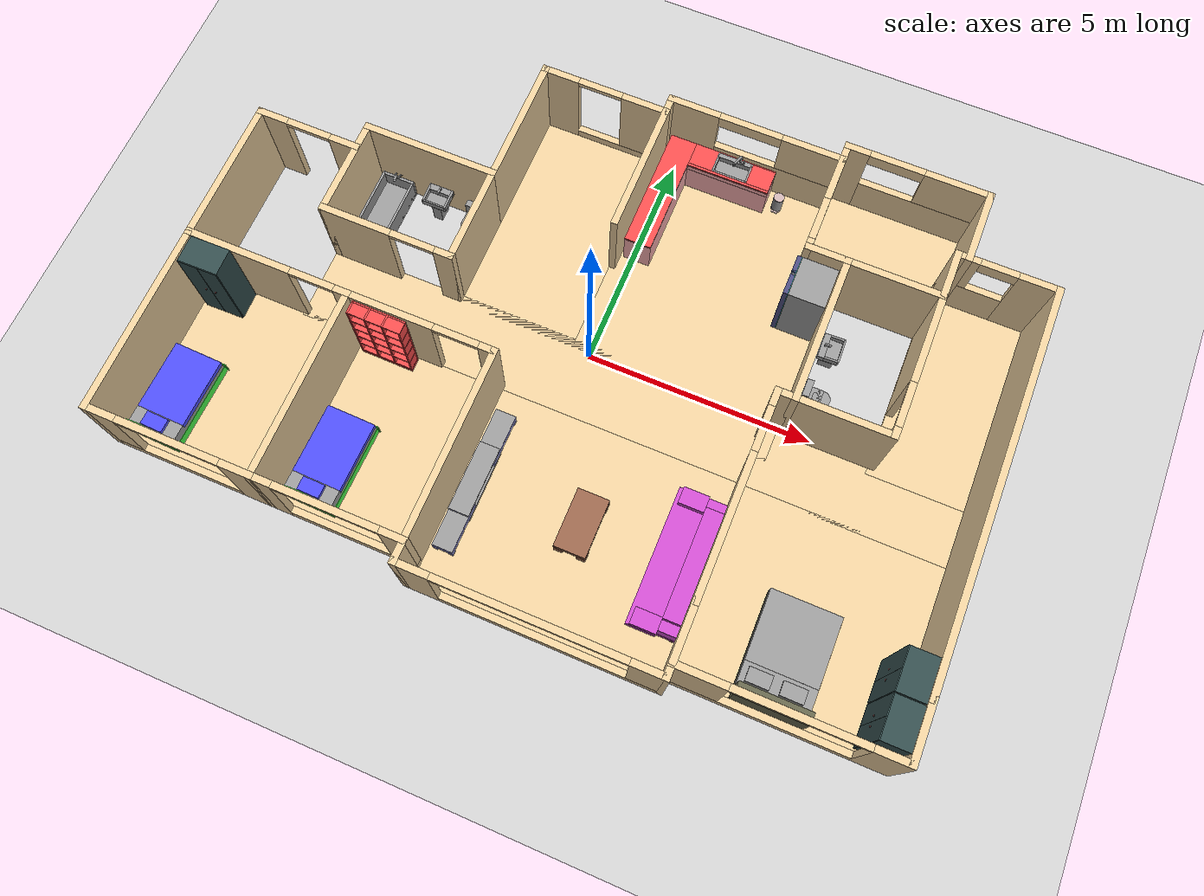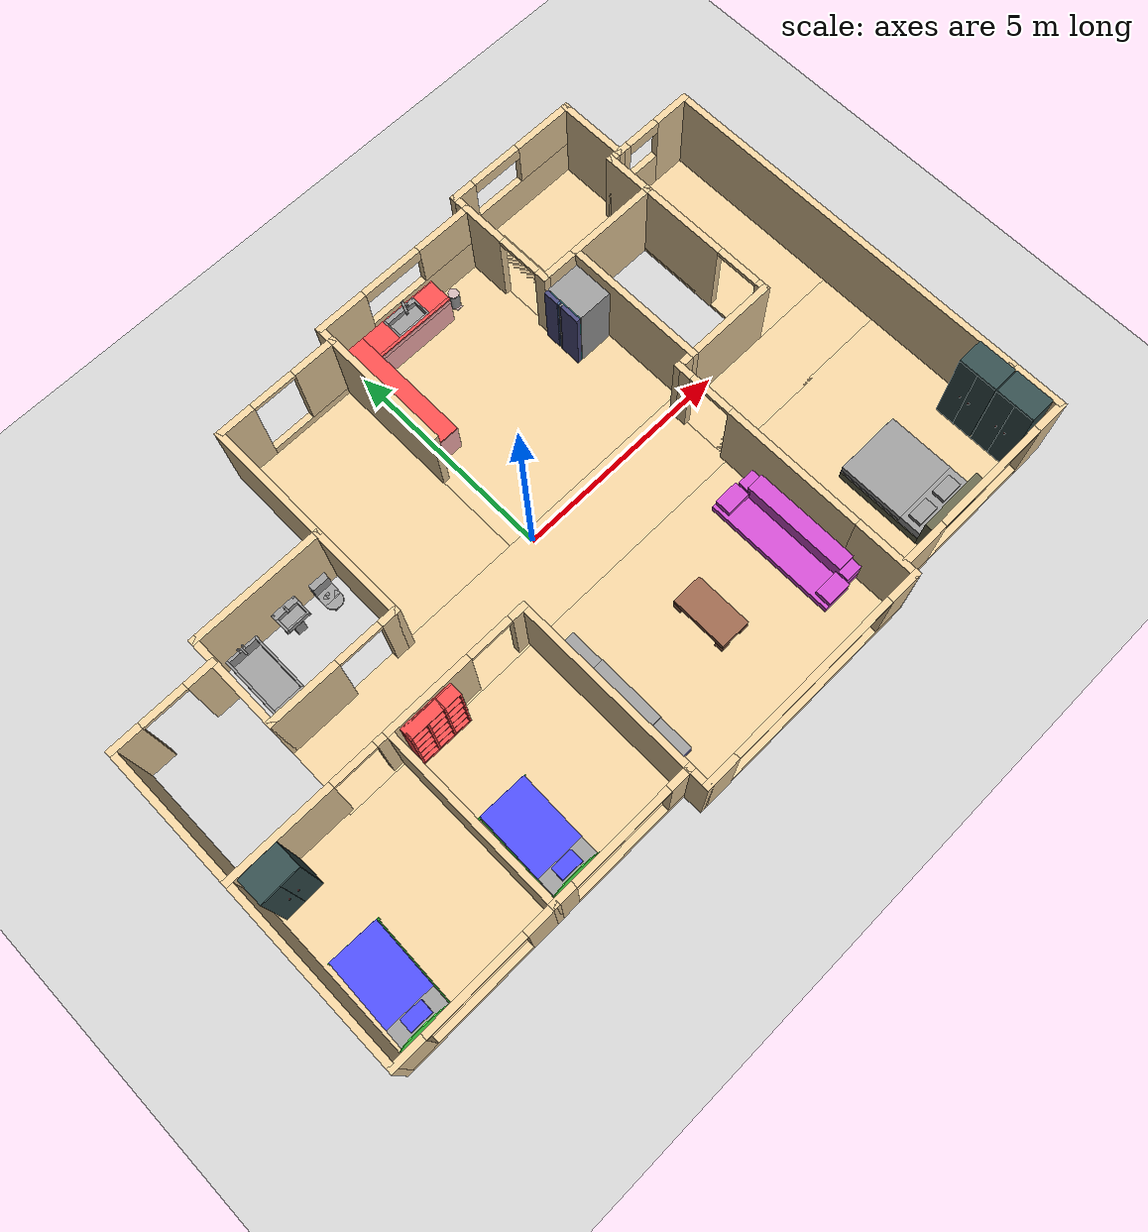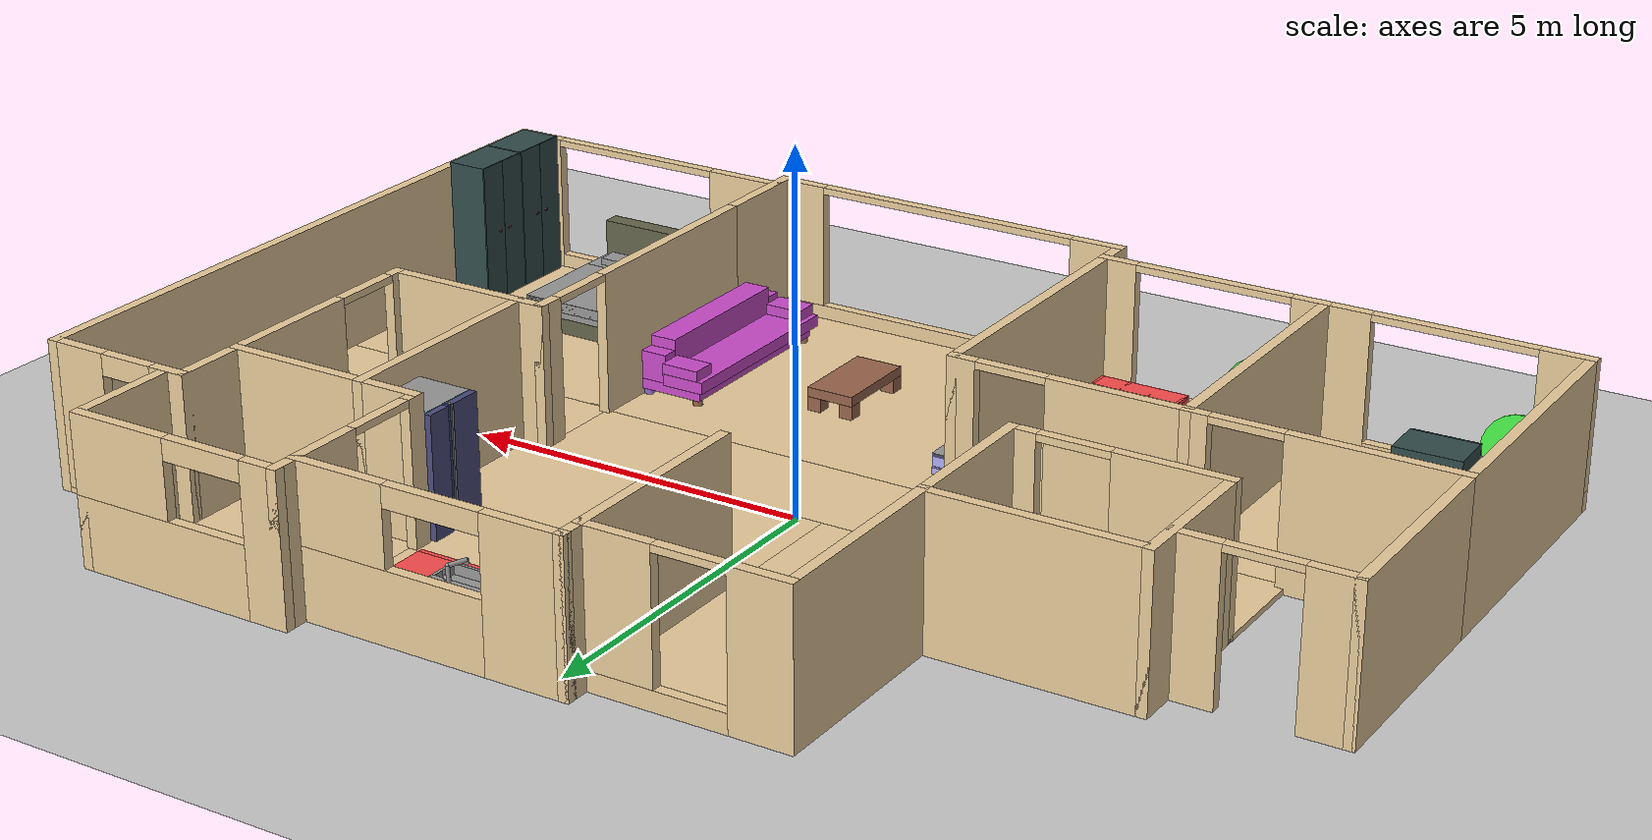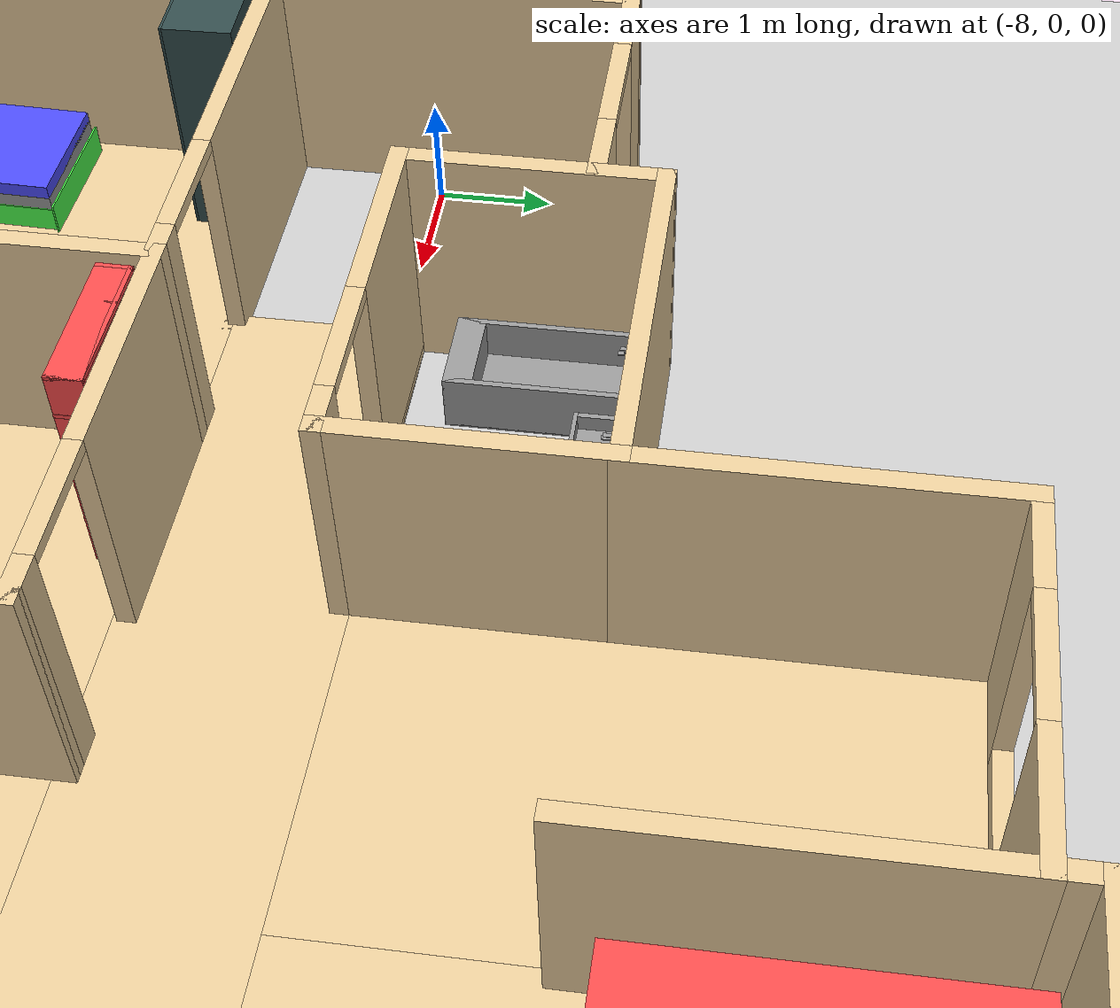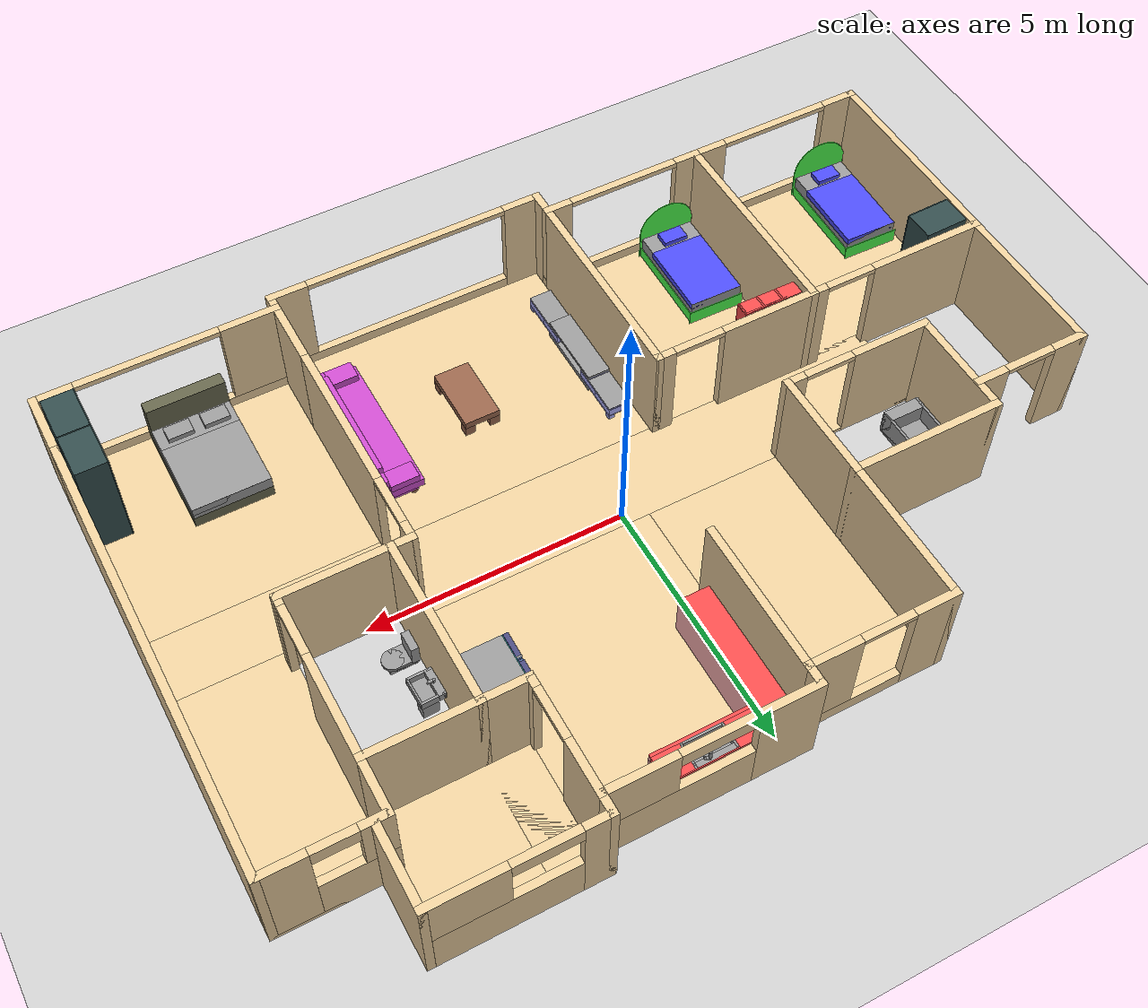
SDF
<sdf version="1.6">
 <world name="default">
  <light name="sun" type="directional">
   <pose>0 0 10 0 -0 0</pose>
   <diffuse>0.8 0.8 0.8 1</diffuse>
   <specular>0.1 0.1 0.1 1</specular>
   <attenuation>
    <range>1000</range>
    <constant>0.9</constant>
    <linear>0.01</linear>
    <quadratic>0.001</quadratic>
   </attenuation>
   <direction>-0.5 0.5 -1</direction>
  </light>
  <model name="ground_plane">
   <static>1</static>
   <link name="link">
    <collision name="collision">
     <geometry><plane><normal>0 0 1</normal><size>100 100</size></plane></geometry>
     <surface><friction><ode><mu>100</mu><mu2>50</mu2></ode></friction></surface>
    </collision>
    <visual name="visual">
     <cast_shadows>0</cast_shadows>
     <geometry><plane><normal>0 0 1</normal><size>100 100</size></plane></geometry>
     <material>
      <script><uri>file://media/materials/scripts/gazebo.material</uri><name>Gazebo/Grey</name></script>
     </material>
    </visual>
   </link>
  </model>
  <gravity>0 0 -9.8</gravity>
  <magnetic_field>6e-06 2.3e-05 -4.2e-05</magnetic_field>
  <atmosphere type="adiabatic"/>
  <physics name="default_physics" default="0" type="ode">
   <max_step_size>0.001</max_step_size>
   <real_time_factor>1</real_time_factor>
   <real_time_update_rate>1000</real_time_update_rate>
  </physics>
  <scene><ambient>0.4 0.4 0.4 1</ambient><background>0.7 0.7 0.7 1</background><shadows>1</shadows></scene>
  <spherical_coordinates>
   <surface_model>EARTH_WGS84</surface_model>
   <latitude_deg>0</latitude_deg>
   <longitude_deg>0</longitude_deg>
   <elevation>0</elevation>
   <heading_deg>0</heading_deg>
  </spherical_coordinates>
  <model name="closet12">
   <link name="link_4">
    <pose>0.1575 -0.07957 1.24924 0 -0 0</pose>
    <visual name="visual">
     <geometry><box><size>0.59 0.882 2.1</size></box></geometry>
     <material>
      <lighting>1</lighting>
      <script><uri>file://media/materials/scripts/gazebo.material</uri><name>Gazebo/Grey</name></script>
      <ambient>0.2 0.3 0.3 1</ambient>
      <diffuse>0.7 0.7 0.7 1</diffuse>
      <specular>1 0.01 0.01 1</specular>
      <emissive>0 0 0 1</emissive>
      <shader type="vertex"><normal_map>__default__</normal_map></shader>
     </material>
    </visual>
    <collision name="collision">
     <geometry><box><size>0.59 0.882 2.1</size></box></geometry>
     <surface>
      <friction>
       <ode><mu>1</mu><mu2>1</mu2><fdir1>0 0 0</fdir1><slip1>0</slip1><slip2>0</slip2></ode>
       <torsional>
        <coefficient>1</coefficient>
        <patch_radius>0</patch_radius>
        <surface_radius>0</surface_radius>
        <use_patch_radius>1</use_patch_radius>
        <ode><slip>0</slip></ode>
       </torsional>
      </friction>
      <bounce><restitution_coefficient>0</restitution_coefficient><threshold>1e+06</threshold></bounce>
      <contact>
       <collide_without_contact>0</collide_without_contact>
       <collide_without_contact_bitmask>1</collide_without_contact_bitmask>
       <collide_bitmask>1</collide_bitmask>
       <ode>
        <soft_cfm>0</soft_cfm>
        <soft_erp>0.2</soft_erp>
        <kp>1e+13</kp>
        <kd>1</kd>
        <max_vel>0.01</max_vel>
        <min_depth>0</min_depth>
       </ode>
       <bullet>
        <split_impulse>1</split_impulse>
        <split_impulse_penetration_threshold>-0.01</split_impulse_penetration_threshold>
        <soft_cfm>0</soft_cfm>
        <soft_erp>0.2</soft_erp>
        <kp>1e+13</kp>
        <kd>1</kd>
       </bullet>
      </contact>
     </surface>
    </collision>
    <inertial>
     <inertia><ixx>1</ixx><ixy>0</ixy><ixz>0</ixz><iyy>1</iyy><iyz>0</iyz><izz>1</izz></inertia>
     <mass>1</mass>
    </inertial>
   </link>
   <link name="link_4_clone">
    <pose>-0.1475 0.14143 1.24924 0 -0 0</pose>
    <visual name="visual">
     <geometry><box><size>0.02 0.44 2.1</size></box></geometry>
     <material>
      <lighting>1</lighting>
      <script><uri>file://media/materials/scripts/gazebo.material</uri><name>Gazebo/Grey</name></script>
      <ambient>0.2 0.3 0.3 1</ambient>
      <diffuse>0.7 0.7 0.7 1</diffuse>
      <specular>1 0.01 0.01 1</specular>
      <emissive>0 0 0 1</emissive>
      <shader type="vertex"><normal_map>__default__</normal_map></shader>
     </material>
    </visual>
    <collision name="collision">
     <geometry><box><size>0.02 0.44 2.1</size></box></geometry>
     <surface>
      <friction>
       <ode><mu>1</mu><mu2>1</mu2><fdir1>0 0 0</fdir1><slip1>0</slip1><slip2>0</slip2></ode>
       <torsional>
        <coefficient>1</coefficient>
        <patch_radius>0</patch_radius>
        <surface_radius>0</surface_radius>
        <use_patch_radius>1</use_patch_radius>
        <ode><slip>0</slip></ode>
       </torsional>
      </friction>
      <bounce><restitution_coefficient>0</restitution_coefficient><threshold>1e+06</threshold></bounce>
      <contact>
       <collide_without_contact>0</collide_without_contact>
       <collide_without_contact_bitmask>1</collide_without_contact_bitmask>
       <collide_bitmask>1</collide_bitmask>
       <ode>
        <soft_cfm>0</soft_cfm>
        <soft_erp>0.2</soft_erp>
        <kp>1e+13</kp>
        <kd>1</kd>
        <max_vel>0.01</max_vel>
        <min_depth>0</min_depth>
       </ode>
       <bullet>
        <split_impulse>1</split_impulse>
        <split_impulse_penetration_threshold>-0.01</split_impulse_penetration_threshold>
        <soft_cfm>0</soft_cfm>
        <soft_erp>0.2</soft_erp>
        <kp>1e+13</kp>
        <kd>1</kd>
       </bullet>
      </contact>
     </surface>
    </collision>
    <inertial>
     <inertia><ixx>1</ixx><ixy>0</ixy><ixz>0</ixz><iyy>1</iyy><iyz>0</iyz><izz>1</izz></inertia>
     <mass>1</mass>
    </inertial>
   </link>
   <link name="link_4_clone_clone">
    <pose>-0.1475 -0.30057 1.24924 0 -0 0</pose>
    <visual name="visual">
     <geometry><box><size>0.02 0.44 2.1</size></box></geometry>
     <material>
      <lighting>1</lighting>
      <script><uri>file://media/materials/scripts/gazebo.material</uri><name>Gazebo/Grey</name></script>
      <ambient>0.2 0.3 0.3 1</ambient>
      <diffuse>0.7 0.7 0.7 1</diffuse>
      <specular>1 0.01 0.01 1</specular>
      <emissive>0 0 0 1</emissive>
      <shader type="vertex"><normal_map>__default__</normal_map></shader>
     </material>
    </visual>
    <collision name="collision">
     <geometry><box><size>0.02 0.44 2.1</size></box></geometry>
     <surface>
      <friction>
       <ode><mu>1</mu><mu2>1</mu2><fdir1>0 0 0</fdir1><slip1>0</slip1><slip2>0</slip2></ode>
       <torsional>
        <coefficient>1</coefficient>
        <patch_radius>0</patch_radius>
        <surface_radius>0</surface_radius>
        <use_patch_radius>1</use_patch_radius>
        <ode><slip>0</slip></ode>
       </torsional>
      </friction>
      <bounce><restitution_coefficient>0</restitution_coefficient><threshold>1e+06</threshold></bounce>
      <contact>
       <collide_without_contact>0</collide_without_contact>
       <collide_without_contact_bitmask>1</collide_without_contact_bitmask>
       <collide_bitmask>1</collide_bitmask>
       <ode>
        <soft_cfm>0</soft_cfm>
        <soft_erp>0.2</soft_erp>
        <kp>1e+13</kp>
        <kd>1</kd>
        <max_vel>0.01</max_vel>
        <min_depth>0</min_depth>
       </ode>
       <bullet>
        <split_impulse>1</split_impulse>
        <split_impulse_penetration_threshold>-0.01</split_impulse_penetration_threshold>
        <soft_cfm>0</soft_cfm>
        <soft_erp>0.2</soft_erp>
        <kp>1e+13</kp>
        <kd>1</kd>
       </bullet>
      </contact>
     </surface>
    </collision>
    <inertial>
     <inertia><ixx>1</ixx><ixy>0</ixy><ixz>0</ixz><iyy>1</iyy><iyz>0</iyz><izz>1</izz></inertia>
     <mass>1</mass>
    </inertial>
   </link>
   <link name="link_6">
    <pose>-0.167502 0.0279 1.24924 0 1.5707 0</pose>
    <visual name="visual">
     <geometry><cylinder><radius>0.02</radius><length>0.02</length></cylinder></geometry>
     <material>
      <lighting>1</lighting>
      <script><uri>file://media/materials/scripts/gazebo.material</uri><name>Gazebo/Grey</name></script>
      <ambient>0.5 0.3 0.3 1</ambient>
      <diffuse>0.7 0.7 0.7 1</diffuse>
      <specular>0.01 0.01 0.01 1</specular>
      <emissive>0 0 0 1</emissive>
      <shader type="vertex"><normal_map>__default__</normal_map></shader>
     </material>
    </visual>
    <collision name="collision">
     <geometry><cylinder><radius>0.02</radius><length>0.02</length></cylinder></geometry>
     <surface>
      <friction>
       <ode><mu>1</mu><mu2>1</mu2><fdir1>0 0 0</fdir1><slip1>0</slip1><slip2>0</slip2></ode>
       <torsional>
        <coefficient>1</coefficient>
        <patch_radius>0</patch_radius>
        <surface_radius>0</surface_radius>
        <use_patch_radius>1</use_patch_radius>
        <ode><slip>0</slip></ode>
       </torsional>
      </friction>
      <bounce><restitution_coefficient>0</restitution_coefficient><threshold>1e+06</threshold></bounce>
      <contact>
       <collide_without_contact>0</collide_without_contact>
       <collide_without_contact_bitmask>1</collide_without_contact_bitmask>
       <collide_bitmask>1</collide_bitmask>
       <ode>
        <soft_cfm>0</soft_cfm>
        <soft_erp>0.2</soft_erp>
        <kp>1e+13</kp>
        <kd>1</kd>
        <max_vel>0.01</max_vel>
        <min_depth>0</min_depth>
       </ode>
       <bullet>
        <split_impulse>1</split_impulse>
        <split_impulse_penetration_threshold>-0.01</split_impulse_penetration_threshold>
        <soft_cfm>0</soft_cfm>
        <soft_erp>0.2</soft_erp>
        <kp>1e+13</kp>
        <kd>1</kd>
       </bullet>
      </contact>
     </surface>
    </collision>
    <inertial>
     <inertia><ixx>1</ixx><ixy>0</ixy><ixz>0</ixz><iyy>1</iyy><iyz>0</iyz><izz>1</izz></inertia>
     <mass>1</mass>
    </inertial>
   </link>
   <link name="link_6_clone">
    <pose>-0.167502 -0.184796 1.24924 0 1.5707 0</pose>
    <visual name="visual">
     <geometry><cylinder><radius>0.02</radius><length>0.02</length></cylinder></geometry>
     <material>
      <lighting>1</lighting>
      <script><uri>file://media/materials/scripts/gazebo.material</uri><name>Gazebo/Grey</name></script>
      <ambient>0.5 0.3 0.3 1</ambient>
      <diffuse>0.7 0.7 0.7 1</diffuse>
      <specular>0.01 0.01 0.01 1</specular>
      <emissive>0 0 0 1</emissive>
      <shader type="vertex"><normal_map>__default__</normal_map></shader>
     </material>
    </visual>
    <collision name="collision">
     <geometry><cylinder><radius>0.02</radius><length>0.02</length></cylinder></geometry>
     <surface>
      <friction>
       <ode><mu>1</mu><mu2>1</mu2><fdir1>0 0 0</fdir1><slip1>0</slip1><slip2>0</slip2></ode>
       <torsional>
        <coefficient>1</coefficient>
        <patch_radius>0</patch_radius>
        <surface_radius>0</surface_radius>
        <use_patch_radius>1</use_patch_radius>
        <ode><slip>0</slip></ode>
       </torsional>
      </friction>
      <bounce><restitution_coefficient>0</restitution_coefficient><threshold>1e+06</threshold></bounce>
      <contact>
       <collide_without_contact>0</collide_without_contact>
       <collide_without_contact_bitmask>1</collide_without_contact_bitmask>
       <collide_bitmask>1</collide_bitmask>
       <ode>
        <soft_cfm>0</soft_cfm>
        <soft_erp>0.2</soft_erp>
        <kp>1e+13</kp>
        <kd>1</kd>
        <max_vel>0.01</max_vel>
        <min_depth>0</min_depth>
       </ode>
       <bullet>
        <split_impulse>1</split_impulse>
        <split_impulse_penetration_threshold>-0.01</split_impulse_penetration_threshold>
        <soft_cfm>0</soft_cfm>
        <soft_erp>0.2</soft_erp>
        <kp>1e+13</kp>
        <kd>1</kd>
       </bullet>
      </contact>
     </surface>
    </collision>
    <inertial>
     <inertia><ixx>1</ixx><ixy>0</ixy><ixz>0</ixz><iyy>1</iyy><iyz>0</iyz><izz>1</izz></inertia>
     <mass>1</mass>
    </inertial>
   </link>
   <joint name="link_4_JOINT_0" type="fixed">
    <parent>link_4</parent>
    <child>link_4_clone_clone</child>
    <physics>
     <ode><limit><cfm>0</cfm><erp>0.2</erp></limit><suspension><cfm>0</cfm><erp>0.2</erp></suspension></ode>
    </physics>
   </joint>
   <joint name="link_4_JOINT_1" type="fixed">
    <parent>link_4</parent>
    <child>link_4_clone</child>
    <physics>
     <ode><limit><cfm>0</cfm><erp>0.2</erp></limit><suspension><cfm>0</cfm><erp>0.2</erp></suspension></ode>
    </physics>
   </joint>
   <joint name="link_4_clone_JOINT_2" type="fixed">
    <parent>link_4_clone</parent>
    <child>link_6</child>
    <physics>
     <ode><limit><cfm>0</cfm><erp>0.2</erp></limit><suspension><cfm>0</cfm><erp>0.2</erp></suspension></ode>
    </physics>
   </joint>
   <joint name="link_4_clone_clone_JOINT_3" type="fixed">
    <parent>link_4_clone_clone</parent>
    <child>link_6_clone</child>
    <physics>
     <ode><limit><cfm>0</cfm><erp>0.2</erp></limit><suspension><cfm>0</cfm><erp>0.2</erp></suspension></ode>
    </physics>
   </joint>
   <joint name="link_4_clone_clone_JOINT_4" type="fixed">
    <parent>link_4_clone_clone</parent>
    <child>link_6_clone</child>
    <physics>
     <ode><limit><cfm>0</cfm><erp>0.2</erp></limit><suspension><cfm>0</cfm><erp>0.2</erp></suspension></ode>
    </physics>
   </joint>
   <static>0</static>
   <pose>-7.79242 -1.9625 -0.11924 -2e-06 -0 1.59015</pose>
  </model>
  <model name="thesink_h_0">
   <link name="link_0_clone">
    <pose>-1.8174 7.06437 0.5 0 -0 0</pose>
    <visual name="visual">
     <geometry><box><size>1.86 0.58 0.7</size></box></geometry>
     <material>
      <lighting>1</lighting>
      <script><uri>file://media/materials/scripts/gazebo.material</uri><name>Gazebo/Grey</name></script>
      <ambient>0.3 0.3 0.3 1</ambient>
      <diffuse>1 0.7 0.7 1</diffuse>
      <specular>0.01 0.01 0.01 1</specular>
      <emissive>0 0 0 1</emissive>
      <shader type="vertex"><normal_map>__default__</normal_map></shader>
     </material>
    </visual>
    <collision name="collision">
     <geometry><box><size>1.86 0.58 0.7</size></box></geometry>
     <surface>
      <friction>
       <ode><mu>1</mu><mu2>1</mu2><fdir1>0 0 0</fdir1><slip1>0</slip1><slip2>0</slip2></ode>
       <torsional>
        <coefficient>1</coefficient>
        <patch_radius>0</patch_radius>
        <surface_radius>0</surface_radius>
        <use_patch_radius>1</use_patch_radius>
        <ode><slip>0</slip></ode>
       </torsional>
      </friction>
      <bounce><restitution_coefficient>0</restitution_coefficient><threshold>1e+06</threshold></bounce>
      <contact>
       <collide_without_contact>0</collide_without_contact>
       <collide_without_contact_bitmask>1</collide_without_contact_bitmask>
       <collide_bitmask>1</collide_bitmask>
       <ode>
        <soft_cfm>0</soft_cfm>
        <soft_erp>0.2</soft_erp>
        <kp>1e+13</kp>
        <kd>1</kd>
        <max_vel>0.01</max_vel>
        <min_depth>0</min_depth>
       </ode>
       <bullet>
        <split_impulse>1</split_impulse>
        <split_impulse_penetration_threshold>-0.01</split_impulse_penetration_threshold>
        <soft_cfm>0</soft_cfm>
        <soft_erp>0.2</soft_erp>
        <kp>1e+13</kp>
        <kd>1</kd>
       </bullet>
      </contact>
     </surface>
    </collision>
    <inertial>
     <inertia><ixx>1</ixx><ixy>0</ixy><ixz>0</ixz><iyy>1</iyy><iyz>0</iyz><izz>1</izz></inertia>
     <mass>1</mass>
    </inertial>
   </link>
   <link name="link_0_clone_clone">
    <pose>-1.8174 6.80437 0.91 0 -0 0</pose>
    <visual name="visual">
     <geometry><box><size>1.86 0.06 0.12</size></box></geometry>
     <material>
      <lighting>1</lighting>
      <script><uri>file://media/materials/scripts/gazebo.material</uri><name>Gazebo/Grey</name></script>
      <ambient>0.3 0.3 0.3 1</ambient>
      <diffuse>1 0.7 0.7 1</diffuse>
      <specular>0.01 0.01 0.01 1</specular>
      <emissive>0 0 0 1</emissive>
      <shader type="vertex"><normal_map>__default__</normal_map></shader>
     </material>
    </visual>
    <collision name="collision">
     <geometry><box><size>1.86 0.06 0.12</size></box></geometry>
     <surface>
      <friction>
       <ode><mu>1</mu><mu2>1</mu2><fdir1>0 0 0</fdir1><slip1>0</slip1><slip2>0</slip2></ode>
       <torsional>
        <coefficient>1</coefficient>
        <patch_radius>0</patch_radius>
        <surface_radius>0</surface_radius>
        <use_patch_radius>1</use_patch_radius>
        <ode><slip>0</slip></ode>
       </torsional>
      </friction>
      <bounce><restitution_coefficient>0</restitution_coefficient><threshold>1e+06</threshold></bounce>
      <contact>
       <collide_without_contact>0</collide_without_contact>
       <collide_without_contact_bitmask>1</collide_without_contact_bitmask>
       <collide_bitmask>1</collide_bitmask>
       <ode>
        <soft_cfm>0</soft_cfm>
        <soft_erp>0.2</soft_erp>
        <kp>1e+13</kp>
        <kd>1</kd>
        <max_vel>0.01</max_vel>
        <min_depth>0</min_depth>
       </ode>
       <bullet>
        <split_impulse>1</split_impulse>
        <split_impulse_penetration_threshold>-0.01</split_impulse_penetration_threshold>
        <soft_cfm>0</soft_cfm>
        <soft_erp>0.2</soft_erp>
        <kp>1e+13</kp>
        <kd>1</kd>
       </bullet>
      </contact>
     </surface>
    </collision>
    <inertial>
     <inertia><ixx>1</ixx><ixy>0</ixy><ixz>0</ixz><iyy>1</iyy><iyz>0</iyz><izz>1</izz></inertia>
     <mass>1</mass>
    </inertial>
   </link>
   <link name="link_0_clone_clone_0">
    <pose>-3.0474 5.95437 0.56 0 -0 0</pose>
    <visual name="visual">
     <geometry><box><size>0.6 2.8 0.82</size></box></geometry>
     <material>
      <lighting>1</lighting>
      <script><uri>file://media/materials/scripts/gazebo.material</uri><name>Gazebo/Grey</name></script>
      <ambient>0.3 0.3 0.3 1</ambient>
      <diffuse>1 0.7 0.7 1</diffuse>
      <specular>0.01 0.01 0.01 1</specular>
      <emissive>0 0 0 1</emissive>
      <shader type="vertex"><normal_map>__default__</normal_map></shader>
     </material>
    </visual>
    <collision name="collision">
     <geometry><box><size>0.6 2.8 0.82</size></box></geometry>
     <surface>
      <friction>
       <ode><mu>1</mu><mu2>1</mu2><fdir1>0 0 0</fdir1><slip1>0</slip1><slip2>0</slip2></ode>
       <torsional>
        <coefficient>1</coefficient>
        <patch_radius>0</patch_radius>
        <surface_radius>0</surface_radius>
        <use_patch_radius>1</use_patch_radius>
        <ode><slip>0</slip></ode>
       </torsional>
      </friction>
      <bounce><restitution_coefficient>0</restitution_coefficient><threshold>1e+06</threshold></bounce>
      <contact>
       <collide_without_contact>0</collide_without_contact>
       <collide_without_contact_bitmask>1</collide_without_contact_bitmask>
       <collide_bitmask>1</collide_bitmask>
       <ode>
        <soft_cfm>0</soft_cfm>
        <soft_erp>0.2</soft_erp>
        <kp>1e+13</kp>
        <kd>1</kd>
        <max_vel>0.01</max_vel>
        <min_depth>0</min_depth>
       </ode>
       <bullet>
        <split_impulse>1</split_impulse>
        <split_impulse_penetration_threshold>-0.01</split_impulse_penetration_threshold>
        <soft_cfm>0</soft_cfm>
        <soft_erp>0.2</soft_erp>
        <kp>1e+13</kp>
        <kd>1</kd>
       </bullet>
      </contact>
     </surface>
    </collision>
    <inertial>
     <inertia><ixx>1</ixx><ixy>0</ixy><ixz>0</ixz><iyy>1</iyy><iyz>0</iyz><izz>1</izz></inertia>
     <mass>1</mass>
    </inertial>
   </link>
   <link name="link_3_clone">
    <pose>-2.4774 7.09437 0.93 0 -0 0</pose>
    <visual name="visual">
     <geometry><box><size>0.54 0.52 0.16</size></box></geometry>
     <material>
      <lighting>1</lighting>
      <script><uri>file://media/materials/scripts/gazebo.material</uri><name>Gazebo/Grey</name></script>
      <ambient>1 0.3 0.3 1</ambient>
      <diffuse>0.7 0.7 0.7 1</diffuse>
      <specular>0.01 0.01 0.01 1</specular>
      <emissive>0 0 0 1</emissive>
      <shader type="vertex"><normal_map>__default__</normal_map></shader>
     </material>
    </visual>
    <collision name="collision">
     <geometry><box><size>0.54 0.52 0.16</size></box></geometry>
     <surface>
      <friction>
       <ode><mu>1</mu><mu2>1</mu2><fdir1>0 0 0</fdir1><slip1>0</slip1><slip2>0</slip2></ode>
       <torsional>
        <coefficient>1</coefficient>
        <patch_radius>0</patch_radius>
        <surface_radius>0</surface_radius>
        <use_patch_radius>1</use_patch_radius>
        <ode><slip>0</slip></ode>
       </torsional>
      </friction>
      <bounce><restitution_coefficient>0</restitution_coefficient><threshold>1e+06</threshold></bounce>
      <contact>
       <collide_without_contact>0</collide_without_contact>
       <collide_without_contact_bitmask>1</collide_without_contact_bitmask>
       <collide_bitmask>1</collide_bitmask>
       <ode>
        <soft_cfm>0</soft_cfm>
        <soft_erp>0.2</soft_erp>
        <kp>1e+13</kp>
        <kd>1</kd>
        <max_vel>0.01</max_vel>
        <min_depth>0</min_depth>
       </ode>
       <bullet>
        <split_impulse>1</split_impulse>
        <split_impulse_penetration_threshold>-0.01</split_impulse_penetration_threshold>
        <soft_cfm>0</soft_cfm>
        <soft_erp>0.2</soft_erp>
        <kp>1e+13</kp>
        <kd>1</kd>
       </bullet>
      </contact>
     </surface>
    </collision>
    <inertial>
     <inertia><ixx>1</ixx><ixy>0</ixy><ixz>0</ixz><iyy>1</iyy><iyz>0</iyz><izz>1</izz></inertia>
     <mass>1</mass>
    </inertial>
   </link>
   <link name="link_4_clone_0">
    <pose>-1.5474 7.34437 0.93 0 -0 0</pose>
    <visual name="visual">
     <geometry><box><size>1.32 0.02 0.16</size></box></geometry>
     <material>
      <lighting>1</lighting>
      <script><uri>file://media/materials/scripts/gazebo.material</uri><name>Gazebo/Grey</name></script>
      <ambient>1 0.3 0.3 1</ambient>
      <diffuse>0.7 0.7 0.7 1</diffuse>
      <specular>0.01 0.01 0.01 1</specular>
      <emissive>0 0 0 1</emissive>
      <shader type="vertex"><normal_map>__default__</normal_map></shader>
     </material>
    </visual>
    <collision name="collision">
     <geometry><box><size>1.32 0.02 0.16</size></box></geometry>
     <surface>
      <friction>
       <ode><mu>1</mu><mu2>1</mu2><fdir1>0 0 0</fdir1><slip1>0</slip1><slip2>0</slip2></ode>
       <torsional>
        <coefficient>1</coefficient>
        <patch_radius>0</patch_radius>
        <surface_radius>0</surface_radius>
        <use_patch_radius>1</use_patch_radius>
        <ode><slip>0</slip></ode>
       </torsional>
      </friction>
      <bounce><restitution_coefficient>0</restitution_coefficient><threshold>1e+06</threshold></bounce>
      <contact>
       <collide_without_contact>0</collide_without_contact>
       <collide_without_contact_bitmask>1</collide_without_contact_bitmask>
       <collide_bitmask>1</collide_bitmask>
       <ode>
        <soft_cfm>0</soft_cfm>
        <soft_erp>0.2</soft_erp>
        <kp>1e+13</kp>
        <kd>1</kd>
        <max_vel>0.01</max_vel>
        <min_depth>0</min_depth>
       </ode>
       <bullet>
        <split_impulse>1</split_impulse>
        <split_impulse_penetration_threshold>-0.01</split_impulse_penetration_threshold>
        <soft_cfm>0</soft_cfm>
        <soft_erp>0.2</soft_erp>
        <kp>1e+13</kp>
        <kd>1</kd>
       </bullet>
      </contact>
     </surface>
    </collision>
    <inertial>
     <inertia><ixx>1</ixx><ixy>0</ixy><ixz>0</ixz><iyy>1</iyy><iyz>0</iyz><izz>1</izz></inertia>
     <mass>1</mass>
    </inertial>
   </link>
   <link name="link_4_clone_clone">
    <pose>-1.8174 6.80437 0.99 0 -0 0</pose>
    <visual name="visual">
     <geometry><box><size>1.86 0.06 0.04</size></box></geometry>
     <material>
      <lighting>1</lighting>
      <script><uri>file://media/materials/scripts/gazebo.material</uri><name>Gazebo/Grey</name></script>
      <ambient>1 0.3 0.3 1</ambient>
      <diffuse>0.7 0.7 0.7 1</diffuse>
      <specular>0.01 0.01 0.01 1</specular>
      <emissive>0 0 0 1</emissive>
      <shader type="vertex"><normal_map>__default__</normal_map></shader>
     </material>
    </visual>
    <collision name="collision">
     <geometry><box><size>1.86 0.06 0.04</size></box></geometry>
     <surface>
      <friction>
       <ode><mu>1</mu><mu2>1</mu2><fdir1>0 0 0</fdir1><slip1>0</slip1><slip2>0</slip2></ode>
       <torsional>
        <coefficient>1</coefficient>
        <patch_radius>0</patch_radius>
        <surface_radius>0</surface_radius>
        <use_patch_radius>1</use_patch_radius>
        <ode><slip>0</slip></ode>
       </torsional>
      </friction>
      <bounce><restitution_coefficient>0</restitution_coefficient><threshold>1e+06</threshold></bounce>
      <contact>
       <collide_without_contact>0</collide_without_contact>
       <collide_without_contact_bitmask>1</collide_without_contact_bitmask>
       <collide_bitmask>1</collide_bitmask>
       <ode>
        <soft_cfm>0</soft_cfm>
        <soft_erp>0.2</soft_erp>
        <kp>1e+13</kp>
        <kd>1</kd>
        <max_vel>0.01</max_vel>
        <min_depth>0</min_depth>
       </ode>
       <bullet>
        <split_impulse>1</split_impulse>
        <split_impulse_penetration_threshold>-0.01</split_impulse_penetration_threshold>
        <soft_cfm>0</soft_cfm>
        <soft_erp>0.2</soft_erp>
        <kp>1e+13</kp>
        <kd>1</kd>
       </bullet>
      </contact>
     </surface>
    </collision>
    <inertial>
     <inertia><ixx>1</ixx><ixy>0</ixy><ixz>0</ixz><iyy>1</iyy><iyz>0</iyz><izz>1</izz></inertia>
     <mass>1</mass>
    </inertial>
   </link>
   <link name="link_4_clone_clone_clone">
    <pose>-3.0474 5.95437 0.99 0 -0 0</pose>
    <visual name="visual">
     <geometry><box><size>0.6 2.8 0.04</size></box></geometry>
     <material>
      <lighting>1</lighting>
      <script><uri>file://media/materials/scripts/gazebo.material</uri><name>Gazebo/Grey</name></script>
      <ambient>1 0.3 0.3 1</ambient>
      <diffuse>0.7 0.7 0.7 1</diffuse>
      <specular>0.01 0.01 0.01 1</specular>
      <emissive>0 0 0 1</emissive>
      <shader type="vertex"><normal_map>__default__</normal_map></shader>
     </material>
    </visual>
    <collision name="collision">
     <geometry><box><size>0.6 2.8 0.04</size></box></geometry>
     <surface>
      <friction>
       <ode><mu>1</mu><mu2>1</mu2><fdir1>0 0 0</fdir1><slip1>0</slip1><slip2>0</slip2></ode>
       <torsional>
        <coefficient>1</coefficient>
        <patch_radius>0</patch_radius>
        <surface_radius>0</surface_radius>
        <use_patch_radius>1</use_patch_radius>
        <ode><slip>0</slip></ode>
       </torsional>
      </friction>
      <bounce><restitution_coefficient>0</restitution_coefficient><threshold>1e+06</threshold></bounce>
      <contact>
       <collide_without_contact>0</collide_without_contact>
       <collide_without_contact_bitmask>1</collide_without_contact_bitmask>
       <collide_bitmask>1</collide_bitmask>
       <ode>
        <soft_cfm>0</soft_cfm>
        <soft_erp>0.2</soft_erp>
        <kp>1e+13</kp>
        <kd>1</kd>
        <max_vel>0.01</max_vel>
        <min_depth>0</min_depth>
       </ode>
       <bullet>
        <split_impulse>1</split_impulse>
        <split_impulse_penetration_threshold>-0.01</split_impulse_penetration_threshold>
        <soft_cfm>0</soft_cfm>
        <soft_erp>0.2</soft_erp>
        <kp>1e+13</kp>
        <kd>1</kd>
       </bullet>
      </contact>
     </surface>
    </collision>
    <inertial>
     <inertia><ixx>1</ixx><ixy>0</ixy><ixz>0</ixz><iyy>1</iyy><iyz>0</iyz><izz>1</izz></inertia>
     <mass>1</mass>
    </inertial>
   </link>
   <link name="link_5_clone_0">
    <pose>-2.1874 7.08437 0.93 0 -0 0</pose>
    <visual name="visual">
     <geometry><box><size>0.04 0.5 0.16</size></box></geometry>
     <material>
      <lighting>1</lighting>
      <script><uri>file://media/materials/scripts/gazebo.material</uri><name>Gazebo/Grey</name></script>
      <ambient>0.3 0.3 0.3 1</ambient>
      <diffuse>0.7 0.7 0.7 1</diffuse>
      <specular>0.01 0.01 0.01 1</specular>
      <emissive>0 0 0 1</emissive>
      <shader type="vertex"><normal_map>__default__</normal_map></shader>
     </material>
    </visual>
    <collision name="collision">
     <geometry><box><size>0.04 0.5 0.16</size></box></geometry>
     <surface>
      <friction>
       <ode><mu>1</mu><mu2>1</mu2><fdir1>0 0 0</fdir1><slip1>0</slip1><slip2>0</slip2></ode>
       <torsional>
        <coefficient>1</coefficient>
        <patch_radius>0</patch_radius>
        <surface_radius>0</surface_radius>
        <use_patch_radius>1</use_patch_radius>
        <ode><slip>0</slip></ode>
       </torsional>
      </friction>
      <bounce><restitution_coefficient>0</restitution_coefficient><threshold>1e+06</threshold></bounce>
      <contact>
       <collide_without_contact>0</collide_without_contact>
       <collide_without_contact_bitmask>1</collide_without_contact_bitmask>
       <collide_bitmask>1</collide_bitmask>
       <ode>
        <soft_cfm>0</soft_cfm>
        <soft_erp>0.2</soft_erp>
        <kp>1e+13</kp>
        <kd>1</kd>
        <max_vel>0.01</max_vel>
        <min_depth>0</min_depth>
       </ode>
       <bullet>
        <split_impulse>1</split_impulse>
        <split_impulse_penetration_threshold>-0.01</split_impulse_penetration_threshold>
        <soft_cfm>0</soft_cfm>
        <soft_erp>0.2</soft_erp>
        <kp>1e+13</kp>
        <kd>1</kd>
       </bullet>
      </contact>
     </surface>
    </collision>
    <inertial>
     <inertia><ixx>1</ixx><ixy>0</ixy><ixz>0</ixz><iyy>1</iyy><iyz>0</iyz><izz>1</izz></inertia>
     <mass>1</mass>
    </inertial>
   </link>
   <link name="link_5_clone_clone">
    <pose>-1.4274 7.08437 0.93 0 -0 0</pose>
    <visual name="visual">
     <geometry><box><size>0.04 0.5 0.16</size></box></geometry>
     <material>
      <lighting>1</lighting>
      <script><uri>file://media/materials/scripts/gazebo.material</uri><name>Gazebo/Grey</name></script>
      <ambient>0.3 0.3 0.3 1</ambient>
      <diffuse>0.7 0.7 0.7 1</diffuse>
      <specular>0.01 0.01 0.01 1</specular>
      <emissive>0 0 0 1</emissive>
      <shader type="vertex"><normal_map>__default__</normal_map></shader>
     </material>
    </visual>
    <collision name="collision">
     <geometry><box><size>0.04 0.5 0.16</size></box></geometry>
     <surface>
      <friction>
       <ode><mu>1</mu><mu2>1</mu2><fdir1>0 0 0</fdir1><slip1>0</slip1><slip2>0</slip2></ode>
       <torsional>
        <coefficient>1</coefficient>
        <patch_radius>0</patch_radius>
        <surface_radius>0</surface_radius>
        <use_patch_radius>1</use_patch_radius>
        <ode><slip>0</slip></ode>
       </torsional>
      </friction>
      <bounce><restitution_coefficient>0</restitution_coefficient><threshold>1e+06</threshold></bounce>
      <contact>
       <collide_without_contact>0</collide_without_contact>
       <collide_without_contact_bitmask>1</collide_without_contact_bitmask>
       <collide_bitmask>1</collide_bitmask>
       <ode>
        <soft_cfm>0</soft_cfm>
        <soft_erp>0.2</soft_erp>
        <kp>1e+13</kp>
        <kd>1</kd>
        <max_vel>0.01</max_vel>
        <min_depth>0</min_depth>
       </ode>
       <bullet>
        <split_impulse>1</split_impulse>
        <split_impulse_penetration_threshold>-0.01</split_impulse_penetration_threshold>
        <soft_cfm>0</soft_cfm>
        <soft_erp>0.2</soft_erp>
        <kp>1e+13</kp>
        <kd>1</kd>
       </bullet>
      </contact>
     </surface>
    </collision>
    <inertial>
     <inertia><ixx>1</ixx><ixy>0</ixy><ixz>0</ixz><iyy>1</iyy><iyz>0</iyz><izz>1</izz></inertia>
     <mass>1</mass>
    </inertial>
   </link>
   <link name="link_6_clone">
    <pose>-1.8074 7.08437 0.86 0 -0 0</pose>
    <visual name="visual">
     <geometry><box><size>0.8 0.5 0.02</size></box></geometry>
     <material>
      <lighting>1</lighting>
      <script><uri>file://media/materials/scripts/gazebo.material</uri><name>Gazebo/Grey</name></script>
      <ambient>0.3 0.3 0.3 1</ambient>
      <diffuse>0.7 0.7 0.7 1</diffuse>
      <specular>0.01 0.01 0.01 1</specular>
      <emissive>0 0 0 1</emissive>
      <shader type="vertex"><normal_map>__default__</normal_map></shader>
     </material>
    </visual>
    <collision name="collision">
     <geometry><box><size>0.8 0.5 0.02</size></box></geometry>
     <surface>
      <friction>
       <ode><mu>1</mu><mu2>1</mu2><fdir1>0 0 0</fdir1><slip1>0</slip1><slip2>0</slip2></ode>
       <torsional>
        <coefficient>1</coefficient>
        <patch_radius>0</patch_radius>
        <surface_radius>0</surface_radius>
        <use_patch_radius>1</use_patch_radius>
        <ode><slip>0</slip></ode>
       </torsional>
      </friction>
      <bounce><restitution_coefficient>0</restitution_coefficient><threshold>1e+06</threshold></bounce>
      <contact>
       <collide_without_contact>0</collide_without_contact>
       <collide_without_contact_bitmask>1</collide_without_contact_bitmask>
       <collide_bitmask>1</collide_bitmask>
       <ode>
        <soft_cfm>0</soft_cfm>
        <soft_erp>0.2</soft_erp>
        <kp>1e+13</kp>
        <kd>1</kd>
        <max_vel>0.01</max_vel>
        <min_depth>0</min_depth>
       </ode>
       <bullet>
        <split_impulse>1</split_impulse>
        <split_impulse_penetration_threshold>-0.01</split_impulse_penetration_threshold>
        <soft_cfm>0</soft_cfm>
        <soft_erp>0.2</soft_erp>
        <kp>1e+13</kp>
        <kd>1</kd>
       </bullet>
      </contact>
     </surface>
    </collision>
    <inertial>
     <inertia><ixx>1</ixx><ixy>0</ixy><ixz>0</ixz><iyy>1</iyy><iyz>0</iyz><izz>1</izz></inertia>
     <mass>1</mass>
    </inertial>
   </link>
   <link name="link_7_clone_0">
    <pose>-1.8074 7.28437 0.93 0 -0 0</pose>
    <visual name="visual">
     <geometry><box><size>0.8 0.1 0.16</size></box></geometry>
     <material>
      <lighting>1</lighting>
      <script><uri>file://media/materials/scripts/gazebo.material</uri><name>Gazebo/Grey</name></script>
      <ambient>0.3 0.3 0.3 1</ambient>
      <diffuse>0.7 0.7 0.7 1</diffuse>
      <specular>0.01 0.01 0.01 1</specular>
      <emissive>0 0 0 1</emissive>
      <shader type="vertex"><normal_map>__default__</normal_map></shader>
     </material>
    </visual>
    <collision name="collision">
     <geometry><box><size>0.8 0.1 0.16</size></box></geometry>
     <surface>
      <friction>
       <ode><mu>1</mu><mu2>1</mu2><fdir1>0 0 0</fdir1><slip1>0</slip1><slip2>0</slip2></ode>
       <torsional>
        <coefficient>1</coefficient>
        <patch_radius>0</patch_radius>
        <surface_radius>0</surface_radius>
        <use_patch_radius>1</use_patch_radius>
        <ode><slip>0</slip></ode>
       </torsional>
      </friction>
      <bounce><restitution_coefficient>0</restitution_coefficient><threshold>1e+06</threshold></bounce>
      <contact>
       <collide_without_contact>0</collide_without_contact>
       <collide_without_contact_bitmask>1</collide_without_contact_bitmask>
       <collide_bitmask>1</collide_bitmask>
       <ode>
        <soft_cfm>0</soft_cfm>
        <soft_erp>0.2</soft_erp>
        <kp>1e+13</kp>
        <kd>1</kd>
        <max_vel>0.01</max_vel>
        <min_depth>0</min_depth>
       </ode>
       <bullet>
        <split_impulse>1</split_impulse>
        <split_impulse_penetration_threshold>-0.01</split_impulse_penetration_threshold>
        <soft_cfm>0</soft_cfm>
        <soft_erp>0.2</soft_erp>
        <kp>1e+13</kp>
        <kd>1</kd>
       </bullet>
      </contact>
     </surface>
    </collision>
    <inertial>
     <inertia><ixx>1</ixx><ixy>0</ixy><ixz>0</ixz><iyy>1</iyy><iyz>0</iyz><izz>1</izz></inertia>
     <mass>1</mass>
    </inertial>
   </link>
   <link name="link_7_clone_clone">
    <pose>-1.8074 6.85437 0.93 0 -0 0</pose>
    <visual name="visual">
     <geometry><box><size>0.8 0.04 0.16</size></box></geometry>
     <material>
      <lighting>1</lighting>
      <script><uri>file://media/materials/scripts/gazebo.material</uri><name>Gazebo/Grey</name></script>
      <ambient>0.3 0.3 0.3 1</ambient>
      <diffuse>0.7 0.7 0.7 1</diffuse>
      <specular>0.01 0.01 0.01 1</specular>
      <emissive>0 0 0 1</emissive>
      <shader type="vertex"><normal_map>__default__</normal_map></shader>
     </material>
    </visual>
    <collision name="collision">
     <geometry><box><size>0.8 0.04 0.16</size></box></geometry>
     <surface>
      <friction>
       <ode><mu>1</mu><mu2>1</mu2><fdir1>0 0 0</fdir1><slip1>0</slip1><slip2>0</slip2></ode>
       <torsional>
        <coefficient>1</coefficient>
        <patch_radius>0</patch_radius>
        <surface_radius>0</surface_radius>
        <use_patch_radius>1</use_patch_radius>
        <ode><slip>0</slip></ode>
       </torsional>
      </friction>
      <bounce><restitution_coefficient>0</restitution_coefficient><threshold>1e+06</threshold></bounce>
      <contact>
       <collide_without_contact>0</collide_without_contact>
       <collide_without_contact_bitmask>1</collide_without_contact_bitmask>
       <collide_bitmask>1</collide_bitmask>
       <ode>
        <soft_cfm>0</soft_cfm>
        <soft_erp>0.2</soft_erp>
        <kp>1e+13</kp>
        <kd>1</kd>
        <max_vel>0.01</max_vel>
        <min_depth>0</min_depth>
       </ode>
       <bullet>
        <split_impulse>1</split_impulse>
        <split_impulse_penetration_threshold>-0.01</split_impulse_penetration_threshold>
        <soft_cfm>0</soft_cfm>
        <soft_erp>0.2</soft_erp>
        <kp>1e+13</kp>
        <kd>1</kd>
       </bullet>
      </contact>
     </surface>
    </collision>
    <inertial>
     <inertia><ixx>1</ixx><ixy>0</ixy><ixz>0</ixz><iyy>1</iyy><iyz>0</iyz><izz>1</izz></inertia>
     <mass>1</mass>
    </inertial>
   </link>
   <link name="link_8_clone">
    <pose>-1.1474 7.08437 0.93 0 -0 0</pose>
    <visual name="visual">
     <geometry><box><size>0.52 0.5 0.16</size></box></geometry>
     <material>
      <lighting>1</lighting>
      <script><uri>file://media/materials/scripts/gazebo.material</uri><name>Gazebo/Grey</name></script>
      <ambient>1 0.3 0.3 1</ambient>
      <diffuse>0.7 0.7 0.7 1</diffuse>
      <specular>0.01 0.01 0.01 1</specular>
      <emissive>0 0 0 1</emissive>
      <shader type="vertex"><normal_map>__default__</normal_map></shader>
     </material>
    </visual>
    <collision name="collision">
     <geometry><box><size>0.52 0.5 0.16</size></box></geometry>
     <surface>
      <friction>
       <ode><mu>1</mu><mu2>1</mu2><fdir1>0 0 0</fdir1><slip1>0</slip1><slip2>0</slip2></ode>
       <torsional>
        <coefficient>1</coefficient>
        <patch_radius>0</patch_radius>
        <surface_radius>0</surface_radius>
        <use_patch_radius>1</use_patch_radius>
        <ode><slip>0</slip></ode>
       </torsional>
      </friction>
      <bounce><restitution_coefficient>0</restitution_coefficient><threshold>1e+06</threshold></bounce>
      <contact>
       <collide_without_contact>0</collide_without_contact>
       <collide_without_contact_bitmask>1</collide_without_contact_bitmask>
       <collide_bitmask>1</collide_bitmask>
       <ode>
        <soft_cfm>0</soft_cfm>
        <soft_erp>0.2</soft_erp>
        <kp>1e+13</kp>
        <kd>1</kd>
        <max_vel>0.01</max_vel>
        <min_depth>0</min_depth>
       </ode>
       <bullet>
        <split_impulse>1</split_impulse>
        <split_impulse_penetration_threshold>-0.01</split_impulse_penetration_threshold>
        <soft_cfm>0</soft_cfm>
        <soft_erp>0.2</soft_erp>
        <kp>1e+13</kp>
        <kd>1</kd>
       </bullet>
      </contact>
     </surface>
    </collision>
    <inertial>
     <inertia><ixx>1</ixx><ixy>0</ixy><ixz>0</ixz><iyy>1</iyy><iyz>0</iyz><izz>1</izz></inertia>
     <mass>1</mass>
    </inertial>
   </link>
   <model name="faucet_3">
    <link name="link_0">
     <pose>-4.16773 1.01211 0.450461 0 -0 0</pose>
     <visual name="visual">
      <geometry><cylinder><radius>0.0275</radius><length>0.22</length></cylinder></geometry>
      <material>
       <lighting>1</lighting>
       <script><uri>file://media/materials/scripts/gazebo.material</uri><name>Gazebo/Grey</name></script>
       <ambient>0.3 0.3 0.3 1</ambient>
       <diffuse>0.7 0.7 0.7 1</diffuse>
       <specular>0.01 0.01 0.01 1</specular>
       <emissive>0 0 0 1</emissive>
       <shader type="vertex"><normal_map>__default__</normal_map></shader>
      </material>
     </visual>
     <collision name="collision">
      <geometry><cylinder><radius>0.0275</radius><length>0.22</length></cylinder></geometry>
      <surface>
       <friction>
        <ode><mu>1</mu><mu2>1</mu2><fdir1>0 0 0</fdir1><slip1>0</slip1><slip2>0</slip2></ode>
        <torsional>
         <coefficient>1</coefficient>
         <patch_radius>0</patch_radius>
         <surface_radius>0</surface_radius>
         <use_patch_radius>1</use_patch_radius>
         <ode><slip>0</slip></ode>
        </torsional>
       </friction>
       <bounce><restitution_coefficient>0</restitution_coefficient><threshold>1e+06</threshold></bounce>
       <contact>
        <collide_without_contact>0</collide_without_contact>
        <collide_without_contact_bitmask>1</collide_without_contact_bitmask>
        <collide_bitmask>1</collide_bitmask>
        <ode>
         <soft_cfm>0</soft_cfm>
         <soft_erp>0.2</soft_erp>
         <kp>1e+13</kp>
         <kd>1</kd>
         <max_vel>0.01</max_vel>
         <min_depth>0</min_depth>
        </ode>
        <bullet>
         <split_impulse>1</split_impulse>
         <split_impulse_penetration_threshold>-0.01</split_impulse_penetration_threshold>
         <soft_cfm>0</soft_cfm>
         <soft_erp>0.2</soft_erp>
         <kp>1e+13</kp>
         <kd>1</kd>
        </bullet>
       </contact>
      </surface>
     </collision>
     <inertial>
      <inertia><ixx>1</ixx><ixy>0</ixy><ixz>0</ixz><iyy>1</iyy><iyz>0</iyz><izz>1</izz></inertia>
      <mass>1</mass>
     </inertial>
    </link>
    <link name="link_0_clone">
     <pose>-4.29273 1.01211 0.56046 0 1.5707 0</pose>
     <visual name="visual">
      <geometry><cylinder><radius>0.0275</radius><length>0.25</length></cylinder></geometry>
      <material>
       <lighting>1</lighting>
       <script><uri>file://media/materials/scripts/gazebo.material</uri><name>Gazebo/Grey</name></script>
       <ambient>0.3 0.3 0.3 1</ambient>
       <diffuse>0.7 0.7 0.7 1</diffuse>
       <specular>0.01 0.01 0.01 1</specular>
       <emissive>0 0 0 1</emissive>
       <shader type="vertex"><normal_map>__default__</normal_map></shader>
      </material>
     </visual>
     <collision name="collision">
      <geometry><cylinder><radius>0.0275</radius><length>0.25</length></cylinder></geometry>
      <surface>
       <friction>
        <ode><mu>1</mu><mu2>1</mu2><fdir1>0 0 0</fdir1><slip1>0</slip1><slip2>0</slip2></ode>
        <torsional>
         <coefficient>1</coefficient>
         <patch_radius>0</patch_radius>
         <surface_radius>0</surface_radius>
         <use_patch_radius>1</use_patch_radius>
         <ode><slip>0</slip></ode>
        </torsional>
       </friction>
       <bounce><restitution_coefficient>0</restitution_coefficient><threshold>1e+06</threshold></bounce>
       <contact>
        <collide_without_contact>0</collide_without_contact>
        <collide_without_contact_bitmask>1</collide_without_contact_bitmask>
        <collide_bitmask>1</collide_bitmask>
        <ode>
         <soft_cfm>0</soft_cfm>
         <soft_erp>0.2</soft_erp>
         <kp>1e+13</kp>
         <kd>1</kd>
         <max_vel>0.01</max_vel>
         <min_depth>0</min_depth>
        </ode>
        <bullet>
         <split_impulse>1</split_impulse>
         <split_impulse_penetration_threshold>-0.01</split_impulse_penetration_threshold>
         <soft_cfm>0</soft_cfm>
         <soft_erp>0.2</soft_erp>
         <kp>1e+13</kp>
         <kd>1</kd>
        </bullet>
       </contact>
      </surface>
     </collision>
     <inertial>
      <inertia><ixx>1</ixx><ixy>0</ixy><ixz>0</ixz><iyy>1</iyy><iyz>0</iyz><izz>1</izz></inertia>
      <mass>1</mass>
     </inertial>
    </link>
    <link name="link_1">
     <pose>-4.16773 1.01211 0.56046 0 -0 0</pose>
     <visual name="visual">
      <geometry><sphere><radius>0.0275</radius></sphere></geometry>
      <material>
       <lighting>1</lighting>
       <script><uri>file://media/materials/scripts/gazebo.material</uri><name>Gazebo/Grey</name></script>
       <ambient>0.3 0.3 0.3 1</ambient>
       <diffuse>0.7 0.7 0.7 1</diffuse>
       <specular>0.01 0.01 0.01 1</specular>
       <emissive>0 0 0 1</emissive>
       <shader type="vertex"><normal_map>__default__</normal_map></shader>
      </material>
     </visual>
     <collision name="collision">
      <geometry><sphere><radius>0.0275</radius></sphere></geometry>
      <surface>
       <friction>
        <ode><mu>1</mu><mu2>1</mu2><fdir1>0 0 0</fdir1><slip1>0</slip1><slip2>0</slip2></ode>
        <torsional>
         <coefficient>1</coefficient>
         <patch_radius>0</patch_radius>
         <surface_radius>0</surface_radius>
         <use_patch_radius>1</use_patch_radius>
         <ode><slip>0</slip></ode>
        </torsional>
       </friction>
       <bounce><restitution_coefficient>0</restitution_coefficient><threshold>1e+06</threshold></bounce>
       <contact>
        <collide_without_contact>0</collide_without_contact>
        <collide_without_contact_bitmask>1</collide_without_contact_bitmask>
        <collide_bitmask>1</collide_bitmask>
        <ode>
         <soft_cfm>0</soft_cfm>
         <soft_erp>0.2</soft_erp>
         <kp>1e+13</kp>
         <kd>1</kd>
         <max_vel>0.01</max_vel>
         <min_depth>0</min_depth>
        </ode>
        <bullet>
         <split_impulse>1</split_impulse>
         <split_impulse_penetration_threshold>-0.01</split_impulse_penetration_threshold>
         <soft_cfm>0</soft_cfm>
         <soft_erp>0.2</soft_erp>
         <kp>1e+13</kp>
         <kd>1</kd>
        </bullet>
       </contact>
      </surface>
     </collision>
     <inertial>
      <inertia><ixx>1</ixx><ixy>0</ixy><ixz>0</ixz><iyy>1</iyy><iyz>0</iyz><izz>1</izz></inertia>
      <mass>1</mass>
     </inertial>
    </link>
    <link name="link_1_clone">
     <pose>-4.41773 1.01211 0.56046 0 -0 0</pose>
     <visual name="visual">
      <geometry><sphere><radius>0.0275</radius></sphere></geometry>
      <material>
       <lighting>1</lighting>
       <script><uri>file://media/materials/scripts/gazebo.material</uri><name>Gazebo/Grey</name></script>
       <ambient>0.3 0.3 0.3 1</ambient>
       <diffuse>0.7 0.7 0.7 1</diffuse>
       <specular>0.01 0.01 0.01 1</specular>
       <emissive>0 0 0 1</emissive>
       <shader type="vertex"><normal_map>__default__</normal_map></shader>
      </material>
     </visual>
     <collision name="collision">
      <geometry><sphere><radius>0.0275</radius></sphere></geometry>
      <surface>
       <friction>
        <ode><mu>1</mu><mu2>1</mu2><fdir1>0 0 0</fdir1><slip1>0</slip1><slip2>0</slip2></ode>
        <torsional>
         <coefficient>1</coefficient>
         <patch_radius>0</patch_radius>
         <surface_radius>0</surface_radius>
         <use_patch_radius>1</use_patch_radius>
         <ode><slip>0</slip></ode>
        </torsional>
       </friction>
       <bounce><restitution_coefficient>0</restitution_coefficient><threshold>1e+06</threshold></bounce>
       <contact>
        <collide_without_contact>0</collide_without_contact>
        <collide_without_contact_bitmask>1</collide_without_contact_bitmask>
        <collide_bitmask>1</collide_bitmask>
        <ode>
         <soft_cfm>0</soft_cfm>
         <soft_erp>0.2</soft_erp>
         <kp>1e+13</kp>
         <kd>1</kd>
         <max_vel>0.01</max_vel>
         <min_depth>0</min_depth>
        </ode>
        <bullet>
         <split_impulse>1</split_impulse>
         <split_impulse_penetration_threshold>-0.01</split_impulse_penetration_threshold>
         <soft_cfm>0</soft_cfm>
         <soft_erp>0.2</soft_erp>
         <kp>1e+13</kp>
         <kd>1</kd>
        </bullet>
       </contact>
      </surface>
     </collision>
     <inertial>
      <inertia><ixx>1</ixx><ixy>0</ixy><ixz>0</ixz><iyy>1</iyy><iyz>0</iyz><izz>1</izz></inertia>
      <mass>1</mass>
     </inertial>
    </link>
    <link name="link_3">
     <pose>-4.41773 1.01211 0.55546 0 -0 0</pose>
     <visual name="visual">
      <geometry><cylinder><radius>0.0275</radius><length>0.01</length></cylinder></geometry>
      <material>
       <lighting>1</lighting>
       <script><uri>file://media/materials/scripts/gazebo.material</uri><name>Gazebo/Grey</name></script>
       <ambient>0.3 0.3 0.3 1</ambient>
       <diffuse>0.7 0.7 0.7 1</diffuse>
       <specular>0.01 0.01 0.01 1</specular>
       <emissive>0 0 0 1</emissive>
       <shader type="vertex"><normal_map>__default__</normal_map></shader>
      </material>
     </visual>
     <collision name="collision">
      <geometry><cylinder><radius>0.0275</radius><length>0.01</length></cylinder></geometry>
      <surface>
       <friction>
        <ode><mu>1</mu><mu2>1</mu2><fdir1>0 0 0</fdir1><slip1>0</slip1><slip2>0</slip2></ode>
        <torsional>
         <coefficient>1</coefficient>
         <patch_radius>0</patch_radius>
         <surface_radius>0</surface_radius>
         <use_patch_radius>1</use_patch_radius>
         <ode><slip>0</slip></ode>
        </torsional>
       </friction>
       <bounce><restitution_coefficient>0</restitution_coefficient><threshold>1e+06</threshold></bounce>
       <contact>
        <collide_without_contact>0</collide_without_contact>
        <collide_without_contact_bitmask>1</collide_without_contact_bitmask>
        <collide_bitmask>1</collide_bitmask>
        <ode>
         <soft_cfm>0</soft_cfm>
         <soft_erp>0.2</soft_erp>
         <kp>1e+13</kp>
         <kd>1</kd>
         <max_vel>0.01</max_vel>
         <min_depth>0</min_depth>
        </ode>
        <bullet>
         <split_impulse>1</split_impulse>
         <split_impulse_penetration_threshold>-0.01</split_impulse_penetration_threshold>
         <soft_cfm>0</soft_cfm>
         <soft_erp>0.2</soft_erp>
         <kp>1e+13</kp>
         <kd>1</kd>
        </bullet>
       </contact>
      </surface>
     </collision>
     <inertial>
      <inertia><ixx>1</ixx><ixy>0</ixy><ixz>0</ixz><iyy>1</iyy><iyz>0</iyz><izz>1</izz></inertia>
      <mass>1</mass>
     </inertial>
    </link>
    <link name="link_4">
     <pose>-4.41773 1.01211 0.53046 0 -0 0</pose>
     <visual name="visual">
      <geometry><cylinder><radius>0.03</radius><length>0.04</length></cylinder></geometry>
      <material>
       <lighting>1</lighting>
       <script><uri>file://media/materials/scripts/gazebo.material</uri><name>Gazebo/Grey</name></script>
       <ambient>0.3 0.3 0.3 1</ambient>
       <diffuse>0.7 0.7 0.7 1</diffuse>
       <specular>0.01 0.01 0.01 1</specular>
       <emissive>0 0 0 1</emissive>
       <shader type="vertex"><normal_map>__default__</normal_map></shader>
      </material>
     </visual>
     <collision name="collision">
      <geometry><cylinder><radius>0.03</radius><length>0.04</length></cylinder></geometry>
      <surface>
       <friction>
        <ode><mu>1</mu><mu2>1</mu2><fdir1>0 0 0</fdir1><slip1>0</slip1><slip2>0</slip2></ode>
        <torsional>
         <coefficient>1</coefficient>
         <patch_radius>0</patch_radius>
         <surface_radius>0</surface_radius>
         <use_patch_radius>1</use_patch_radius>
         <ode><slip>0</slip></ode>
        </torsional>
       </friction>
       <bounce><restitution_coefficient>0</restitution_coefficient><threshold>1e+06</threshold></bounce>
       <contact>
        <collide_without_contact>0</collide_without_contact>
        <collide_without_contact_bitmask>1</collide_without_contact_bitmask>
        <collide_bitmask>1</collide_bitmask>
        <ode>
         <soft_cfm>0</soft_cfm>
         <soft_erp>0.2</soft_erp>
         <kp>1e+13</kp>
         <kd>1</kd>
         <max_vel>0.01</max_vel>
         <min_depth>0</min_depth>
        </ode>
        <bullet>
         <split_impulse>1</split_impulse>
         <split_impulse_penetration_threshold>-0.01</split_impulse_penetration_threshold>
         <soft_cfm>0</soft_cfm>
         <soft_erp>0.2</soft_erp>
         <kp>1e+13</kp>
         <kd>1</kd>
        </bullet>
       </contact>
      </surface>
     </collision>
     <inertial>
      <inertia><ixx>1</ixx><ixy>0</ixy><ixz>0</ixz><iyy>1</iyy><iyz>0</iyz><izz>1</izz></inertia>
      <mass>1</mass>
     </inertial>
    </link>
    <link name="link_5">
     <pose>-4.16773 0.978357 0.381368 1.5707 -0 0</pose>
     <visual name="visual">
      <geometry><cylinder><radius>0.0275</radius><length>0.0675</length></cylinder></geometry>
      <material>
       <lighting>1</lighting>
       <script><uri>file://media/materials/scripts/gazebo.material</uri><name>Gazebo/Grey</name></script>
       <ambient>0.3 0.3 0.3 1</ambient>
       <diffuse>0.7 0.7 0.7 1</diffuse>
       <specular>0.01 0.01 0.01 1</specular>
       <emissive>0 0 0 1</emissive>
       <shader type="vertex"><normal_map>__default__</normal_map></shader>
      </material>
     </visual>
     <collision name="collision">
      <geometry><cylinder><radius>0.0275</radius><length>0.0675</length></cylinder></geometry>
      <surface>
       <friction>
        <ode><mu>1</mu><mu2>1</mu2><fdir1>0 0 0</fdir1><slip1>0</slip1><slip2>0</slip2></ode>
        <torsional>
         <coefficient>1</coefficient>
         <patch_radius>0</patch_radius>
         <surface_radius>0</surface_radius>
         <use_patch_radius>1</use_patch_radius>
         <ode><slip>0</slip></ode>
        </torsional>
       </friction>
       <bounce><restitution_coefficient>0</restitution_coefficient><threshold>1e+06</threshold></bounce>
       <contact>
        <collide_without_contact>0</collide_without_contact>
        <collide_without_contact_bitmask>1</collide_without_contact_bitmask>
        <collide_bitmask>1</collide_bitmask>
        <ode>
         <soft_cfm>0</soft_cfm>
         <soft_erp>0.2</soft_erp>
         <kp>1e+13</kp>
         <kd>1</kd>
         <max_vel>0.01</max_vel>
         <min_depth>0</min_depth>
        </ode>
        <bullet>
         <split_impulse>1</split_impulse>
         <split_impulse_penetration_threshold>-0.01</split_impulse_penetration_threshold>
         <soft_cfm>0</soft_cfm>
         <soft_erp>0.2</soft_erp>
         <kp>1e+13</kp>
         <kd>1</kd>
        </bullet>
       </contact>
      </surface>
     </collision>
     <inertial>
      <inertia><ixx>1</ixx><ixy>0</ixy><ixz>0</ixz><iyy>1</iyy><iyz>0</iyz><izz>1</izz></inertia>
      <mass>1</mass>
     </inertial>
    </link>
    <link name="link_5_clone">
     <pose>-4.16773 0.929098 0.381368 1.5707 -0 0</pose>
     <visual name="visual">
      <geometry><cylinder><radius>0.0275</radius><length>0.025</length></cylinder></geometry>
      <material>
       <lighting>1</lighting>
       <script><uri>file://media/materials/scripts/gazebo.material</uri><name>Gazebo/Grey</name></script>
       <ambient>0.3 0.3 0.3 1</ambient>
       <diffuse>0.7 0.7 0.7 1</diffuse>
       <specular>0.01 0.01 0.01 1</specular>
       <emissive>0 0 0 1</emissive>
       <shader type="vertex"><normal_map>__default__</normal_map></shader>
      </material>
     </visual>
     <collision name="collision">
      <geometry><cylinder><radius>0.0275</radius><length>0.025</length></cylinder></geometry>
      <surface>
       <friction>
        <ode><mu>1</mu><mu2>1</mu2><fdir1>0 0 0</fdir1><slip1>0</slip1><slip2>0</slip2></ode>
        <torsional>
         <coefficient>1</coefficient>
         <patch_radius>0</patch_radius>
         <surface_radius>0</surface_radius>
         <use_patch_radius>1</use_patch_radius>
         <ode><slip>0</slip></ode>
        </torsional>
       </friction>
       <bounce><restitution_coefficient>0</restitution_coefficient><threshold>1e+06</threshold></bounce>
       <contact>
        <collide_without_contact>0</collide_without_contact>
        <collide_without_contact_bitmask>1</collide_without_contact_bitmask>
        <collide_bitmask>1</collide_bitmask>
        <ode>
         <soft_cfm>0</soft_cfm>
         <soft_erp>0.2</soft_erp>
         <kp>1e+13</kp>
         <kd>1</kd>
         <max_vel>0.01</max_vel>
         <min_depth>0</min_depth>
        </ode>
        <bullet>
         <split_impulse>1</split_impulse>
         <split_impulse_penetration_threshold>-0.01</split_impulse_penetration_threshold>
         <soft_cfm>0</soft_cfm>
         <soft_erp>0.2</soft_erp>
         <kp>1e+13</kp>
         <kd>1</kd>
        </bullet>
       </contact>
      </surface>
     </collision>
     <inertial>
      <inertia><ixx>1</ixx><ixy>0</ixy><ixz>0</ixz><iyy>1</iyy><iyz>0</iyz><izz>1</izz></inertia>
      <mass>1</mass>
     </inertial>
    </link>
    <link name="link_6">
     <pose>-4.16773 0.943103 0.381368 1.5707 -0 0</pose>
     <visual name="visual">
      <geometry><cylinder><radius>0.015</radius><length>0.002</length></cylinder></geometry>
      <material>
       <lighting>1</lighting>
       <script><uri>file://media/materials/scripts/gazebo.material</uri><name>Gazebo/Grey</name></script>
       <ambient>0.3 0.3 0.3 1</ambient>
       <diffuse>0.7 0.7 0.7 1</diffuse>
       <specular>0.01 0.01 0.01 1</specular>
       <emissive>0 0 0 1</emissive>
       <shader type="vertex"><normal_map>__default__</normal_map></shader>
      </material>
     </visual>
     <collision name="collision">
      <geometry><cylinder><radius>0.015</radius><length>0.003</length></cylinder></geometry>
      <surface>
       <friction>
        <ode><mu>1</mu><mu2>1</mu2><fdir1>0 0 0</fdir1><slip1>0</slip1><slip2>0</slip2></ode>
        <torsional>
         <coefficient>1</coefficient>
         <patch_radius>0</patch_radius>
         <surface_radius>0</surface_radius>
         <use_patch_radius>1</use_patch_radius>
         <ode><slip>0</slip></ode>
        </torsional>
       </friction>
       <bounce><restitution_coefficient>0</restitution_coefficient><threshold>1e+06</threshold></bounce>
       <contact>
        <collide_without_contact>0</collide_without_contact>
        <collide_without_contact_bitmask>1</collide_without_contact_bitmask>
        <collide_bitmask>1</collide_bitmask>
        <ode>
         <soft_cfm>0</soft_cfm>
         <soft_erp>0.2</soft_erp>
         <kp>1e+13</kp>
         <kd>1</kd>
         <max_vel>0.01</max_vel>
         <min_depth>0</min_depth>
        </ode>
        <bullet>
         <split_impulse>1</split_impulse>
         <split_impulse_penetration_threshold>-0.01</split_impulse_penetration_threshold>
         <soft_cfm>0</soft_cfm>
         <soft_erp>0.2</soft_erp>
         <kp>1e+13</kp>
         <kd>1</kd>
        </bullet>
       </contact>
      </surface>
     </collision>
     <inertial>
      <inertia><ixx>1</ixx><ixy>0</ixy><ixz>0</ixz><iyy>1</iyy><iyz>0</iyz><izz>1</izz></inertia>
      <mass>1</mass>
     </inertial>
    </link>
    <link name="link_7">
     <pose>-4.16773 0.918596 0.426368 0 -0 0</pose>
     <visual name="visual">
      <geometry><box><size>0.05 0.004 0.09</size></box></geometry>
      <material>
       <lighting>1</lighting>
       <script><uri>file://media/materials/scripts/gazebo.material</uri><name>Gazebo/Grey</name></script>
       <ambient>0.3 0.3 0.3 1</ambient>
       <diffuse>0.7 0.7 0.7 1</diffuse>
       <specular>0.01 0.01 0.01 1</specular>
       <emissive>0 0 0 1</emissive>
       <shader type="vertex"><normal_map>__default__</normal_map></shader>
      </material>
     </visual>
     <collision name="collision">
      <geometry><box><size>0.05 0.004 0.09</size></box></geometry>
      <surface>
       <friction>
        <ode><mu>1</mu><mu2>1</mu2><fdir1>0 0 0</fdir1><slip1>0</slip1><slip2>0</slip2></ode>
        <torsional>
         <coefficient>1</coefficient>
         <patch_radius>0</patch_radius>
         <surface_radius>0</surface_radius>
         <use_patch_radius>1</use_patch_radius>
         <ode><slip>0</slip></ode>
        </torsional>
       </friction>
       <bounce><restitution_coefficient>0</restitution_coefficient><threshold>1e+06</threshold></bounce>
       <contact>
        <collide_without_contact>0</collide_without_contact>
        <collide_without_contact_bitmask>1</collide_without_contact_bitmask>
        <collide_bitmask>1</collide_bitmask>
        <ode>
         <soft_cfm>0</soft_cfm>
         <soft_erp>0.2</soft_erp>
         <kp>1e+13</kp>
         <kd>1</kd>
         <max_vel>0.01</max_vel>
         <min_depth>0</min_depth>
        </ode>
        <bullet>
         <split_impulse>1</split_impulse>
         <split_impulse_penetration_threshold>-0.01</split_impulse_penetration_threshold>
         <soft_cfm>0</soft_cfm>
         <soft_erp>0.2</soft_erp>
         <kp>1e+13</kp>
         <kd>1</kd>
        </bullet>
       </contact>
      </surface>
     </collision>
     <inertial>
      <inertia><ixx>1</ixx><ixy>0</ixy><ixz>0</ixz><iyy>1</iyy><iyz>0</iyz><izz>1</izz></inertia>
      <mass>1</mass>
     </inertial>
    </link>
    <joint name="link_0_JOINT_15" type="fixed">
     <parent>link_0</parent>
     <child>link_5</child>
     <physics>
      <ode><limit><cfm>0</cfm><erp>0.2</erp></limit><suspension><cfm>0</cfm><erp>0.2</erp></suspension></ode>
     </physics>
    </joint>
    <joint name="link_0_JOINT_6" type="fixed">
     <parent>link_0</parent>
     <child>link_1</child>
     <physics>
      <ode><limit><cfm>0</cfm><erp>0.2</erp></limit><suspension><cfm>0</cfm><erp>0.2</erp></suspension></ode>
     </physics>
    </joint>
    <joint name="link_0_clone_JOINT_9" type="fixed">
     <parent>link_0_clone</parent>
     <child>link_1_clone</child>
     <physics>
      <ode><limit><cfm>0</cfm><erp>0.2</erp></limit><suspension><cfm>0</cfm><erp>0.2</erp></suspension></ode>
     </physics>
    </joint>
    <joint name="link_1_JOINT_8" type="fixed">
     <parent>link_1</parent>
     <child>link_0_clone</child>
     <physics>
      <ode><limit><cfm>0</cfm><erp>0.2</erp></limit><suspension><cfm>0</cfm><erp>0.2</erp></suspension></ode>
     </physics>
    </joint>
    <joint name="link_1_clone_JOINT_11" type="fixed">
     <parent>link_1_clone</parent>
     <child>link_3</child>
     <physics>
      <ode><limit><cfm>0</cfm><erp>0.2</erp></limit><suspension><cfm>0</cfm><erp>0.2</erp></suspension></ode>
     </physics>
    </joint>
    <joint name="link_3_JOINT_12" type="fixed">
     <parent>link_3</parent>
     <child>link_4</child>
     <physics>
      <ode><limit><cfm>0</cfm><erp>0.2</erp></limit><suspension><cfm>0</cfm><erp>0.2</erp></suspension></ode>
     </physics>
    </joint>
    <joint name="link_3_JOINT_13" type="fixed">
     <parent>link_3</parent>
     <child>link_4</child>
     <physics>
      <ode><limit><cfm>0</cfm><erp>0.2</erp></limit><suspension><cfm>0</cfm><erp>0.2</erp></suspension></ode>
     </physics>
    </joint>
    <joint name="link_5_JOINT_16" type="fixed">
     <parent>link_5</parent>
     <child>link_6</child>
     <physics>
      <ode><limit><cfm>0</cfm><erp>0.2</erp></limit><suspension><cfm>0</cfm><erp>0.2</erp></suspension></ode>
     </physics>
    </joint>
    <joint name="link_5_clone_JOINT_18" type="fixed">
     <parent>link_5_clone</parent>
     <child>link_7</child>
     <physics>
      <ode><limit><cfm>0</cfm><erp>0.2</erp></limit><suspension><cfm>0</cfm><erp>0.2</erp></suspension></ode>
     </physics>
    </joint>
    <joint name="link_6_JOINT_17" type="fixed">
     <parent>link_6</parent>
     <child>link_5_clone</child>
     <physics>
      <ode><limit><cfm>0</cfm><erp>0.2</erp></limit><suspension><cfm>0</cfm><erp>0.2</erp></suspension></ode>
     </physics>
    </joint>
    <static>0</static>
    <pose>0.79467 10.7831 0.661015 0 -0 1.19053</pose>
   </model>
   <joint name="link_0_JOINT_6" type="fixed">
    <parent>faucet_3::link_0</parent>
    <child>faucet_3::link_5</child>
    <physics>
     <ode><limit><cfm>0</cfm><erp>0.2</erp></limit><suspension><cfm>0</cfm><erp>0.2</erp></suspension></ode>
    </physics>
   </joint>
   <joint name="link_0_JOINT_9" type="fixed">
    <parent>faucet_3::link_0</parent>
    <child>faucet_3::link_1</child>
    <physics>
     <ode><limit><cfm>0</cfm><erp>0.2</erp></limit><suspension><cfm>0</cfm><erp>0.2</erp></suspension></ode>
    </physics>
   </joint>
   <joint name="link_0_clone_JOINT_0" type="fixed">
    <parent>link_0_clone</parent>
    <child>link_3_clone</child>
    <physics>
     <ode><limit><cfm>0</cfm><erp>0.2</erp></limit><suspension><cfm>0</cfm><erp>0.2</erp></suspension></ode>
    </physics>
   </joint>
   <joint name="link_0_clone_JOINT_11" type="fixed">
    <parent>faucet_3::link_0_clone</parent>
    <child>faucet_3::link_1_clone</child>
    <physics>
     <ode><limit><cfm>0</cfm><erp>0.2</erp></limit><suspension><cfm>0</cfm><erp>0.2</erp></suspension></ode>
    </physics>
   </joint>
   <joint name="link_0_clone_JOINT_16" type="fixed">
    <parent>link_0_clone</parent>
    <child>link_0_clone_clone_0</child>
    <physics>
     <ode><limit><cfm>0</cfm><erp>0.2</erp></limit><suspension><cfm>0</cfm><erp>0.2</erp></suspension></ode>
    </physics>
   </joint>
   <joint name="link_0_clone_JOINT_1_0" type="fixed">
    <parent>link_0_clone</parent>
    <child>link_0_clone_clone</child>
    <physics>
     <ode><limit><cfm>0</cfm><erp>0.2</erp></limit><suspension><cfm>0</cfm><erp>0.2</erp></suspension></ode>
    </physics>
   </joint>
   <joint name="link_0_clone_JOINT_1" type="fixed">
    <parent>link_0_clone</parent>
    <child>link_3_clone</child>
    <physics>
     <ode><limit><cfm>0</cfm><erp>0.2</erp></limit><suspension><cfm>0</cfm><erp>0.2</erp></suspension></ode>
    </physics>
   </joint>
   <joint name="link_0_clone_clone_0_JOINT_17" type="fixed">
    <parent>link_0_clone_clone_0</parent>
    <child>link_4_clone_clone_clone</child>
    <physics>
     <ode><limit><cfm>0</cfm><erp>0.2</erp></limit><suspension><cfm>0</cfm><erp>0.2</erp></suspension></ode>
    </physics>
   </joint>
   <joint name="link_0_clone_clone_JOINT_2" type="fixed">
    <parent>link_0_clone_clone</parent>
    <child>link_4_clone_clone</child>
    <physics>
     <ode><limit><cfm>0</cfm><erp>0.2</erp></limit><suspension><cfm>0</cfm><erp>0.2</erp></suspension></ode>
    </physics>
   </joint>
   <joint name="link_1_JOINT_10" type="fixed">
    <parent>faucet_3::link_1</parent>
    <child>faucet_3::link_0_clone</child>
    <physics>
     <ode><limit><cfm>0</cfm><erp>0.2</erp></limit><suspension><cfm>0</cfm><erp>0.2</erp></suspension></ode>
    </physics>
   </joint>
   <joint name="link_1_clone_JOINT_12" type="fixed">
    <parent>faucet_3::link_1_clone</parent>
    <child>faucet_3::link_3</child>
    <physics>
     <ode><limit><cfm>0</cfm><erp>0.2</erp></limit><suspension><cfm>0</cfm><erp>0.2</erp></suspension></ode>
    </physics>
   </joint>
   <joint name="link_3_JOINT_13" type="fixed">
    <parent>faucet_3::link_3</parent>
    <child>faucet_3::link_4</child>
    <physics>
     <ode><limit><cfm>0</cfm><erp>0.2</erp></limit><suspension><cfm>0</cfm><erp>0.2</erp></suspension></ode>
    </physics>
   </joint>
   <joint name="link_3_clone_JOINT_2" type="fixed">
    <parent>link_3_clone</parent>
    <child>link_4_clone_0</child>
    <physics>
     <ode><limit><cfm>0</cfm><erp>0.2</erp></limit><suspension><cfm>0</cfm><erp>0.2</erp></suspension></ode>
    </physics>
   </joint>
   <joint name="link_4_clone_0_JOINT_11" type="fixed">
    <parent>link_4_clone_0</parent>
    <child>link_8_clone</child>
    <physics>
     <ode><limit><cfm>0</cfm><erp>0.2</erp></limit><suspension><cfm>0</cfm><erp>0.2</erp></suspension></ode>
    </physics>
   </joint>
   <joint name="link_4_clone_0_JOINT_4" type="fixed">
    <parent>link_4_clone_0</parent>
    <child>link_5_clone_0</child>
    <physics>
     <ode><limit><cfm>0</cfm><erp>0.2</erp></limit><suspension><cfm>0</cfm><erp>0.2</erp></suspension></ode>
    </physics>
   </joint>
   <joint name="link_5_JOINT_7" type="fixed">
    <parent>faucet_3::link_5</parent>
    <child>faucet_3::link_5_clone</child>
    <physics>
     <ode><limit><cfm>0</cfm><erp>0.2</erp></limit><suspension><cfm>0</cfm><erp>0.2</erp></suspension></ode>
    </physics>
   </joint>
   <joint name="link_5_clone_0_JOINT_4" type="fixed">
    <parent>link_5_clone_0</parent>
    <child>link_7_clone_0</child>
    <physics>
     <ode><limit><cfm>0</cfm><erp>0.2</erp></limit><suspension><cfm>0</cfm><erp>0.2</erp></suspension></ode>
    </physics>
   </joint>
   <joint name="link_5_clone_0_JOINT_5" type="fixed">
    <parent>link_5_clone_0</parent>
    <child>link_6_clone</child>
    <physics>
     <ode><limit><cfm>0</cfm><erp>0.2</erp></limit><suspension><cfm>0</cfm><erp>0.2</erp></suspension></ode>
    </physics>
   </joint>
   <joint name="link_5_clone_0_JOINT_7" type="fixed">
    <parent>link_5_clone_0</parent>
    <child>link_7_clone_0</child>
    <physics>
     <ode><limit><cfm>0</cfm><erp>0.2</erp></limit><suspension><cfm>0</cfm><erp>0.2</erp></suspension></ode>
    </physics>
   </joint>
   <joint name="link_5_clone_JOINT_8" type="fixed">
    <parent>faucet_3::link_5_clone</parent>
    <child>faucet_3::link_7</child>
    <physics>
     <ode><limit><cfm>0</cfm><erp>0.2</erp></limit><suspension><cfm>0</cfm><erp>0.2</erp></suspension></ode>
    </physics>
   </joint>
   <joint name="link_5_clone_clone_JOINT_9" type="fixed">
    <parent>link_5_clone_clone</parent>
    <child>link_7_clone_clone</child>
    <physics>
     <ode><limit><cfm>0</cfm><erp>0.2</erp></limit><suspension><cfm>0</cfm><erp>0.2</erp></suspension></ode>
    </physics>
   </joint>
   <joint name="link_7_clone_0_JOINT_5" type="fixed">
    <parent>link_7_clone_0</parent>
    <child>faucet_3::link_0</child>
    <physics>
     <ode><limit><cfm>0</cfm><erp>0.2</erp></limit><suspension><cfm>0</cfm><erp>0.2</erp></suspension></ode>
    </physics>
   </joint>
   <joint name="link_7_clone_0_JOINT_8" type="fixed">
    <parent>link_7_clone_0</parent>
    <child>link_5_clone_clone</child>
    <physics>
     <ode><limit><cfm>0</cfm><erp>0.2</erp></limit><suspension><cfm>0</cfm><erp>0.2</erp></suspension></ode>
    </physics>
   </joint>
   <static>0</static>
   <pose>3.12865 -2.07946 -0.07 0 -0 3.4e-05</pose>
  </model>
  <model name="bedbed">
   <link name="link_0">
    <pose>-1.02143 0 -0.2301 0 -0 0</pose>
    <visual name="visual">
     <geometry><box><size>0.015 1.16 0.29</size></box></geometry>
     <material>
      <lighting>1</lighting>
      <script><uri>file://media/materials/scripts/gazebo.material</uri><name>Gazebo/Grey</name></script>
      <ambient>0.3 1 0.3 1</ambient>
      <diffuse>0.7 0.7 0.7 1</diffuse>
      <specular>0.01 0.01 0.01 1</specular>
      <emissive>0 0 0 1</emissive>
      <shader type="vertex"><normal_map>__default__</normal_map></shader>
     </material>
    </visual>
    <collision name="collision">
     <geometry><box><size>0.015 1.16 0.29</size></box></geometry>
     <surface>
      <friction>
       <ode><mu>1</mu><mu2>1</mu2><fdir1>0 0 0</fdir1><slip1>0</slip1><slip2>0</slip2></ode>
       <torsional>
        <coefficient>1</coefficient>
        <patch_radius>0</patch_radius>
        <surface_radius>0</surface_radius>
        <use_patch_radius>1</use_patch_radius>
        <ode><slip>0</slip></ode>
       </torsional>
      </friction>
      <bounce><restitution_coefficient>0</restitution_coefficient><threshold>1e+06</threshold></bounce>
      <contact>
       <collide_without_contact>0</collide_without_contact>
       <collide_without_contact_bitmask>1</collide_without_contact_bitmask>
       <collide_bitmask>1</collide_bitmask>
       <ode>
        <soft_cfm>0</soft_cfm>
        <soft_erp>0.2</soft_erp>
        <kp>1e+13</kp>
        <kd>1</kd>
        <max_vel>0.01</max_vel>
        <min_depth>0</min_depth>
       </ode>
       <bullet>
        <split_impulse>1</split_impulse>
        <split_impulse_penetration_threshold>-0.01</split_impulse_penetration_threshold>
        <soft_cfm>0</soft_cfm>
        <soft_erp>0.2</soft_erp>
        <kp>1e+13</kp>
        <kd>1</kd>
       </bullet>
      </contact>
     </surface>
    </collision>
    <inertial>
     <inertia><ixx>1</ixx><ixy>0</ixy><ixz>0</ixz><iyy>1</iyy><iyz>0</iyz><izz>1</izz></inertia>
     <mass>1</mass>
    </inertial>
   </link>
   <link name="link_1">
    <pose>-0.013931 0 -0.2601 0 -0 0</pose>
    <visual name="visual">
     <geometry><box><size>2 1.1 0.23</size></box></geometry>
     <material>
      <lighting>1</lighting>
      <script><uri>file://media/materials/scripts/gazebo.material</uri><name>Gazebo/Grey</name></script>
      <ambient>0.3 1 0.3 1</ambient>
      <diffuse>0.7 0.7 0.7 1</diffuse>
      <specular>0.01 0.01 0.01 1</specular>
      <emissive>0 0 0 1</emissive>
      <shader type="vertex"><normal_map>__default__</normal_map></shader>
     </material>
    </visual>
    <collision name="collision">
     <geometry><box><size>2 1.1 0.23</size></box></geometry>
     <surface>
      <friction>
       <ode><mu>1</mu><mu2>1</mu2><fdir1>0 0 0</fdir1><slip1>0</slip1><slip2>0</slip2></ode>
       <torsional>
        <coefficient>1</coefficient>
        <patch_radius>0</patch_radius>
        <surface_radius>0</surface_radius>
        <use_patch_radius>1</use_patch_radius>
        <ode><slip>0</slip></ode>
       </torsional>
      </friction>
      <bounce><restitution_coefficient>0</restitution_coefficient><threshold>1e+06</threshold></bounce>
      <contact>
       <collide_without_contact>0</collide_without_contact>
       <collide_without_contact_bitmask>1</collide_without_contact_bitmask>
       <collide_bitmask>1</collide_bitmask>
       <ode>
        <soft_cfm>0</soft_cfm>
        <soft_erp>0.2</soft_erp>
        <kp>1e+13</kp>
        <kd>1</kd>
        <max_vel>0.01</max_vel>
        <min_depth>0</min_depth>
       </ode>
       <bullet>
        <split_impulse>1</split_impulse>
        <split_impulse_penetration_threshold>-0.01</split_impulse_penetration_threshold>
        <soft_cfm>0</soft_cfm>
        <soft_erp>0.2</soft_erp>
        <kp>1e+13</kp>
        <kd>1</kd>
       </bullet>
      </contact>
     </surface>
    </collision>
    <inertial>
     <inertia><ixx>1</ixx><ixy>0</ixy><ixz>0</ixz><iyy>1</iyy><iyz>0</iyz><izz>1</izz></inertia>
     <mass>1</mass>
    </inertial>
   </link>
   <link name="link_2">
    <pose>-0.013931 0 -0.0201 0 -0 0</pose>
    <visual name="visual">
     <geometry><box><size>1.96 1.08 0.25</size></box></geometry>
     <material>
      <lighting>0</lighting>
      <script><uri>file://media/materials/scripts/gazebo.material</uri><name>Gazebo/Grey</name></script>
      <ambient>0.3 0.3 0.3 1</ambient>
      <diffuse>0.7 0.7 0.7 1</diffuse>
      <specular>0.01 0.01 0.01 1</specular>
      <emissive>0 0 0 1</emissive>
      <shader type="vertex"><normal_map>__default__</normal_map></shader>
     </material>
    </visual>
    <collision name="collision">
     <geometry><box><size>1.96 1.08 0.25</size></box></geometry>
     <surface>
      <friction>
       <ode><mu>1</mu><mu2>1</mu2><fdir1>0 0 0</fdir1><slip1>0</slip1><slip2>0</slip2></ode>
       <torsional>
        <coefficient>1</coefficient>
        <patch_radius>0</patch_radius>
        <surface_radius>0</surface_radius>
        <use_patch_radius>1</use_patch_radius>
        <ode><slip>0</slip></ode>
       </torsional>
      </friction>
      <bounce><restitution_coefficient>0</restitution_coefficient><threshold>1e+06</threshold></bounce>
      <contact>
       <collide_without_contact>0</collide_without_contact>
       <collide_without_contact_bitmask>1</collide_without_contact_bitmask>
       <collide_bitmask>1</collide_bitmask>
       <ode>
        <soft_cfm>0</soft_cfm>
        <soft_erp>0.2</soft_erp>
        <kp>1e+13</kp>
        <kd>1</kd>
        <max_vel>0.01</max_vel>
        <min_depth>0</min_depth>
       </ode>
       <bullet>
        <split_impulse>1</split_impulse>
        <split_impulse_penetration_threshold>-0.01</split_impulse_penetration_threshold>
        <soft_cfm>0</soft_cfm>
        <soft_erp>0.2</soft_erp>
        <kp>1e+13</kp>
        <kd>1</kd>
       </bullet>
      </contact>
     </surface>
    </collision>
    <inertial>
     <inertia><ixx>1</ixx><ixy>0</ixy><ixz>0</ixz><iyy>1</iyy><iyz>0</iyz><izz>1</izz></inertia>
     <mass>1</mass>
    </inertial>
   </link>
   <link name="link_3">
    <pose>0.993569 0 -0.0851 0 -0 0</pose>
    <visual name="visual">
     <geometry><box><size>0.015 1.16 0.58</size></box></geometry>
     <material>
      <lighting>1</lighting>
      <script><uri>file://media/materials/scripts/gazebo.material</uri><name>Gazebo/Grey</name></script>
      <ambient>0.3 1 0.3 1</ambient>
      <diffuse>0.7 0.7 0.7 1</diffuse>
      <specular>0.01 0.01 0.01 1</specular>
      <emissive>0 0 0 1</emissive>
      <shader type="vertex"><normal_map>__default__</normal_map></shader>
     </material>
    </visual>
    <collision name="collision">
     <geometry><box><size>0.015 1.16 0.58</size></box></geometry>
     <surface>
      <friction>
       <ode><mu>1</mu><mu2>1</mu2><fdir1>0 0 0</fdir1><slip1>0</slip1><slip2>0</slip2></ode>
       <torsional>
        <coefficient>1</coefficient>
        <patch_radius>0</patch_radius>
        <surface_radius>0</surface_radius>
        <use_patch_radius>1</use_patch_radius>
        <ode><slip>0</slip></ode>
       </torsional>
      </friction>
      <bounce><restitution_coefficient>0</restitution_coefficient><threshold>1e+06</threshold></bounce>
      <contact>
       <collide_without_contact>0</collide_without_contact>
       <collide_without_contact_bitmask>1</collide_without_contact_bitmask>
       <collide_bitmask>1</collide_bitmask>
       <ode>
        <soft_cfm>0</soft_cfm>
        <soft_erp>0.2</soft_erp>
        <kp>1e+13</kp>
        <kd>1</kd>
        <max_vel>0.01</max_vel>
        <min_depth>0</min_depth>
       </ode>
       <bullet>
        <split_impulse>1</split_impulse>
        <split_impulse_penetration_threshold>-0.01</split_impulse_penetration_threshold>
        <soft_cfm>0</soft_cfm>
        <soft_erp>0.2</soft_erp>
        <kp>1e+13</kp>
        <kd>1</kd>
       </bullet>
      </contact>
     </surface>
    </collision>
    <inertial>
     <inertia><ixx>1</ixx><ixy>0</ixy><ixz>0</ixz><iyy>1</iyy><iyz>0</iyz><izz>1</izz></inertia>
     <mass>1</mass>
    </inertial>
   </link>
   <link name="link_4">
    <pose>0.993509 0 0.204901 0 1.5707 0</pose>
    <visual name="visual">
     <geometry><cylinder><radius>0.58</radius><length>0.015</length></cylinder></geometry>
     <material>
      <lighting>1</lighting>
      <script><uri>file://media/materials/scripts/gazebo.material</uri><name>Gazebo/Grey</name></script>
      <ambient>0.3 1 0.3 1</ambient>
      <diffuse>0.7 0.7 0.7 1</diffuse>
      <specular>0.01 0.01 0.01 1</specular>
      <emissive>0 0 0 1</emissive>
      <shader type="vertex"><normal_map>__default__</normal_map></shader>
     </material>
    </visual>
    <collision name="collision">
     <geometry><cylinder><radius>0.58</radius><length>0.015</length></cylinder></geometry>
     <surface>
      <friction>
       <ode><mu>1</mu><mu2>1</mu2><fdir1>0 0 0</fdir1><slip1>0</slip1><slip2>0</slip2></ode>
       <torsional>
        <coefficient>1</coefficient>
        <patch_radius>0</patch_radius>
        <surface_radius>0</surface_radius>
        <use_patch_radius>1</use_patch_radius>
        <ode><slip>0</slip></ode>
       </torsional>
      </friction>
      <bounce><restitution_coefficient>0</restitution_coefficient><threshold>1e+06</threshold></bounce>
      <contact>
       <collide_without_contact>0</collide_without_contact>
       <collide_without_contact_bitmask>1</collide_without_contact_bitmask>
       <collide_bitmask>1</collide_bitmask>
       <ode>
        <soft_cfm>0</soft_cfm>
        <soft_erp>0.2</soft_erp>
        <kp>1e+13</kp>
        <kd>1</kd>
        <max_vel>0.01</max_vel>
        <min_depth>0</min_depth>
       </ode>
       <bullet>
        <split_impulse>1</split_impulse>
        <split_impulse_penetration_threshold>-0.01</split_impulse_penetration_threshold>
        <soft_cfm>0</soft_cfm>
        <soft_erp>0.2</soft_erp>
        <kp>1e+13</kp>
        <kd>1</kd>
       </bullet>
      </contact>
     </surface>
    </collision>
    <inertial>
     <inertia><ixx>1</ixx><ixy>0</ixy><ixz>0</ixz><iyy>1</iyy><iyz>0</iyz><izz>1</izz></inertia>
     <mass>1</mass>
    </inertial>
   </link>
   <link name="link_5">
    <pose>-0.223931 0 0.1054 0 -0 0</pose>
    <visual name="visual">
     <geometry><box><size>1.54 1.082 0.001</size></box></geometry>
     <material>
      <lighting>1</lighting>
      <script><uri>file://media/materials/scripts/gazebo.material</uri><name>Gazebo/Grey</name></script>
      <ambient>0.3 0.3 1 1</ambient>
      <diffuse>0.7 0.7 0.7 1</diffuse>
      <specular>0.01 0.01 0.01 1</specular>
      <emissive>0 0 0 1</emissive>
      <shader type="vertex"><normal_map>__default__</normal_map></shader>
     </material>
    </visual>
    <collision name="collision">
     <geometry><box><size>1.54 1.082 0.001</size></box></geometry>
     <surface>
      <friction>
       <ode><mu>1</mu><mu2>1</mu2><fdir1>0 0 0</fdir1><slip1>0</slip1><slip2>0</slip2></ode>
       <torsional>
        <coefficient>1</coefficient>
        <patch_radius>0</patch_radius>
        <surface_radius>0</surface_radius>
        <use_patch_radius>1</use_patch_radius>
        <ode><slip>0</slip></ode>
       </torsional>
      </friction>
      <bounce><restitution_coefficient>0</restitution_coefficient><threshold>1e+06</threshold></bounce>
      <contact>
       <collide_without_contact>0</collide_without_contact>
       <collide_without_contact_bitmask>1</collide_without_contact_bitmask>
       <collide_bitmask>1</collide_bitmask>
       <ode>
        <soft_cfm>0</soft_cfm>
        <soft_erp>0.2</soft_erp>
        <kp>1e+13</kp>
        <kd>1</kd>
        <max_vel>0.01</max_vel>
        <min_depth>0</min_depth>
       </ode>
       <bullet>
        <split_impulse>1</split_impulse>
        <split_impulse_penetration_threshold>-0.01</split_impulse_penetration_threshold>
        <soft_cfm>0</soft_cfm>
        <soft_erp>0.2</soft_erp>
        <kp>1e+13</kp>
        <kd>1</kd>
       </bullet>
      </contact>
     </surface>
    </collision>
    <inertial>
     <inertia><ixx>1</ixx><ixy>0</ixy><ixz>0</ixz><iyy>1</iyy><iyz>0</iyz><izz>1</izz></inertia>
     <mass>1</mass>
    </inertial>
   </link>
   <link name="link_6">
    <pose>-0.223931 0.5405 0.0434 0 -0 0</pose>
    <visual name="visual">
     <geometry><box><size>1.54 0.001 0.125</size></box></geometry>
     <material>
      <lighting>1</lighting>
      <script><uri>file://media/materials/scripts/gazebo.material</uri><name>Gazebo/Grey</name></script>
      <ambient>0.3 0.3 1 1</ambient>
      <diffuse>0.7 0.7 0.7 1</diffuse>
      <specular>0.01 0.01 0.01 1</specular>
      <emissive>0 0 0 1</emissive>
      <shader type="vertex"><normal_map>__default__</normal_map></shader>
     </material>
    </visual>
    <collision name="collision">
     <geometry><box><size>1.54 0.001 0.125</size></box></geometry>
     <surface>
      <friction>
       <ode><mu>1</mu><mu2>1</mu2><fdir1>0 0 0</fdir1><slip1>0</slip1><slip2>0</slip2></ode>
       <torsional>
        <coefficient>1</coefficient>
        <patch_radius>0</patch_radius>
        <surface_radius>0</surface_radius>
        <use_patch_radius>1</use_patch_radius>
        <ode><slip>0</slip></ode>
       </torsional>
      </friction>
      <bounce><restitution_coefficient>0</restitution_coefficient><threshold>1e+06</threshold></bounce>
      <contact>
       <collide_without_contact>0</collide_without_contact>
       <collide_without_contact_bitmask>1</collide_without_contact_bitmask>
       <collide_bitmask>1</collide_bitmask>
       <ode>
        <soft_cfm>0</soft_cfm>
        <soft_erp>0.2</soft_erp>
        <kp>1e+13</kp>
        <kd>1</kd>
        <max_vel>0.01</max_vel>
        <min_depth>0</min_depth>
       </ode>
       <bullet>
        <split_impulse>1</split_impulse>
        <split_impulse_penetration_threshold>-0.01</split_impulse_penetration_threshold>
        <soft_cfm>0</soft_cfm>
        <soft_erp>0.2</soft_erp>
        <kp>1e+13</kp>
        <kd>1</kd>
       </bullet>
      </contact>
     </surface>
    </collision>
    <inertial>
     <inertia><ixx>1</ixx><ixy>0</ixy><ixz>0</ixz><iyy>1</iyy><iyz>0</iyz><izz>1</izz></inertia>
     <mass>1</mass>
    </inertial>
   </link>
   <link name="link_6_clone">
    <pose>-0.223931 -0.5405 0.0434 0 -0 0</pose>
    <visual name="visual">
     <geometry><box><size>1.54 0.001 0.125</size></box></geometry>
     <material>
      <lighting>1</lighting>
      <script><uri>file://media/materials/scripts/gazebo.material</uri><name>Gazebo/Grey</name></script>
      <ambient>0.3 0.3 1 1</ambient>
      <diffuse>0.7 0.7 0.7 1</diffuse>
      <specular>0.01 0.01 0.01 1</specular>
      <emissive>0 0 0 1</emissive>
      <shader type="vertex"><normal_map>__default__</normal_map></shader>
     </material>
    </visual>
    <collision name="collision">
     <geometry><box><size>1.54 0.001 0.125</size></box></geometry>
     <surface>
      <friction>
       <ode><mu>1</mu><mu2>1</mu2><fdir1>0 0 0</fdir1><slip1>0</slip1><slip2>0</slip2></ode>
       <torsional>
        <coefficient>1</coefficient>
        <patch_radius>0</patch_radius>
        <surface_radius>0</surface_radius>
        <use_patch_radius>1</use_patch_radius>
        <ode><slip>0</slip></ode>
       </torsional>
      </friction>
      <bounce><restitution_coefficient>0</restitution_coefficient><threshold>1e+06</threshold></bounce>
      <contact>
       <collide_without_contact>0</collide_without_contact>
       <collide_without_contact_bitmask>1</collide_without_contact_bitmask>
       <collide_bitmask>1</collide_bitmask>
       <ode>
        <soft_cfm>0</soft_cfm>
        <soft_erp>0.2</soft_erp>
        <kp>1e+13</kp>
        <kd>1</kd>
        <max_vel>0.01</max_vel>
        <min_depth>0</min_depth>
       </ode>
       <bullet>
        <split_impulse>1</split_impulse>
        <split_impulse_penetration_threshold>-0.01</split_impulse_penetration_threshold>
        <soft_cfm>0</soft_cfm>
        <soft_erp>0.2</soft_erp>
        <kp>1e+13</kp>
        <kd>1</kd>
       </bullet>
      </contact>
     </surface>
    </collision>
    <inertial>
     <inertia><ixx>1</ixx><ixy>0</ixy><ixz>0</ixz><iyy>1</iyy><iyz>0</iyz><izz>1</izz></inertia>
     <mass>1</mass>
    </inertial>
   </link>
   <link name="link_7">
    <pose>-0.993431 0 0.0434 0 -0 0</pose>
    <visual name="visual">
     <geometry><box><size>0.001 1.082 0.125</size></box></geometry>
     <material>
      <lighting>1</lighting>
      <script><uri>file://media/materials/scripts/gazebo.material</uri><name>Gazebo/Grey</name></script>
      <ambient>0.3 0.3 1 1</ambient>
      <diffuse>0.7 0.7 0.7 1</diffuse>
      <specular>0.01 0.01 0.01 1</specular>
      <emissive>0 0 0 1</emissive>
      <shader type="vertex"><normal_map>__default__</normal_map></shader>
     </material>
    </visual>
    <collision name="collision">
     <geometry><box><size>0.001 1.082 0.125</size></box></geometry>
     <surface>
      <friction>
       <ode><mu>1</mu><mu2>1</mu2><fdir1>0 0 0</fdir1><slip1>0</slip1><slip2>0</slip2></ode>
       <torsional>
        <coefficient>1</coefficient>
        <patch_radius>0</patch_radius>
        <surface_radius>0</surface_radius>
        <use_patch_radius>1</use_patch_radius>
        <ode><slip>0</slip></ode>
       </torsional>
      </friction>
      <bounce><restitution_coefficient>0</restitution_coefficient><threshold>1e+06</threshold></bounce>
      <contact>
       <collide_without_contact>0</collide_without_contact>
       <collide_without_contact_bitmask>1</collide_without_contact_bitmask>
       <collide_bitmask>1</collide_bitmask>
       <ode>
        <soft_cfm>0</soft_cfm>
        <soft_erp>0.2</soft_erp>
        <kp>1e+13</kp>
        <kd>1</kd>
        <max_vel>0.01</max_vel>
        <min_depth>0</min_depth>
       </ode>
       <bullet>
        <split_impulse>1</split_impulse>
        <split_impulse_penetration_threshold>-0.01</split_impulse_penetration_threshold>
        <soft_cfm>0</soft_cfm>
        <soft_erp>0.2</soft_erp>
        <kp>1e+13</kp>
        <kd>1</kd>
       </bullet>
      </contact>
     </surface>
    </collision>
    <inertial>
     <inertia><ixx>1</ixx><ixy>0</ixy><ixz>0</ixz><iyy>1</iyy><iyz>0</iyz><izz>1</izz></inertia>
     <mass>1</mass>
    </inertial>
   </link>
   <link name="link_8">
    <pose>0.727434 0 0.1549 0 -0 0</pose>
    <visual name="visual">
     <geometry><box><size>0.3 0.49 0.1</size></box></geometry>
     <material>
      <lighting>1</lighting>
      <script><uri>file://media/materials/scripts/gazebo.material</uri><name>Gazebo/Grey</name></script>
      <ambient>0.3 0.3 1 1</ambient>
      <diffuse>0.7 0.7 0.7 1</diffuse>
      <specular>0.01 0.01 0.01 1</specular>
      <emissive>0 0 0 1</emissive>
      <shader type="vertex"><normal_map>__default__</normal_map></shader>
     </material>
    </visual>
    <collision name="collision">
     <geometry><box><size>0.3 0.49 0.1</size></box></geometry>
     <surface>
      <friction>
       <ode><mu>1</mu><mu2>1</mu2><fdir1>0 0 0</fdir1><slip1>0</slip1><slip2>0</slip2></ode>
       <torsional>
        <coefficient>1</coefficient>
        <patch_radius>0</patch_radius>
        <surface_radius>0</surface_radius>
        <use_patch_radius>1</use_patch_radius>
        <ode><slip>0</slip></ode>
       </torsional>
      </friction>
      <bounce><restitution_coefficient>0</restitution_coefficient><threshold>1e+06</threshold></bounce>
      <contact>
       <collide_without_contact>0</collide_without_contact>
       <collide_without_contact_bitmask>1</collide_without_contact_bitmask>
       <collide_bitmask>1</collide_bitmask>
       <ode>
        <soft_cfm>0</soft_cfm>
        <soft_erp>0.2</soft_erp>
        <kp>1e+13</kp>
        <kd>1</kd>
        <max_vel>0.01</max_vel>
        <min_depth>0</min_depth>
       </ode>
       <bullet>
        <split_impulse>1</split_impulse>
        <split_impulse_penetration_threshold>-0.01</split_impulse_penetration_threshold>
        <soft_cfm>0</soft_cfm>
        <soft_erp>0.2</soft_erp>
        <kp>1e+13</kp>
        <kd>1</kd>
       </bullet>
      </contact>
     </surface>
    </collision>
    <inertial>
     <inertia><ixx>1</ixx><ixy>0</ixy><ixz>0</ixz><iyy>1</iyy><iyz>0</iyz><izz>1</izz></inertia>
     <mass>1</mass>
    </inertial>
   </link>
   <joint name="link_1_JOINT_0" type="fixed">
    <parent>link_1</parent>
    <child>link_0</child>
    <physics>
     <ode><limit><cfm>0</cfm><erp>0.2</erp></limit><suspension><cfm>0</cfm><erp>0.2</erp></suspension></ode>
    </physics>
   </joint>
   <joint name="link_1_JOINT_2" type="fixed">
    <parent>link_1</parent>
    <child>link_3</child>
    <physics>
     <ode><limit><cfm>0</cfm><erp>0.2</erp></limit><suspension><cfm>0</cfm><erp>0.2</erp></suspension></ode>
    </physics>
   </joint>
   <joint name="link_1_JOINT_5" type="fixed">
    <parent>link_1</parent>
    <child>link_2</child>
    <physics>
     <ode><limit><cfm>0</cfm><erp>0.2</erp></limit><suspension><cfm>0</cfm><erp>0.2</erp></suspension></ode>
    </physics>
   </joint>
   <joint name="link_2_JOINT_10" type="fixed">
    <parent>link_2</parent>
    <child>link_8</child>
    <physics>
     <ode><limit><cfm>0</cfm><erp>0.2</erp></limit><suspension><cfm>0</cfm><erp>0.2</erp></suspension></ode>
    </physics>
   </joint>
   <joint name="link_2_JOINT_6" type="fixed">
    <parent>link_2</parent>
    <child>link_5</child>
    <physics>
     <ode><limit><cfm>0</cfm><erp>0.2</erp></limit><suspension><cfm>0</cfm><erp>0.2</erp></suspension></ode>
    </physics>
   </joint>
   <joint name="link_3_JOINT_3" type="fixed">
    <parent>link_3</parent>
    <child>link_4</child>
    <physics>
     <ode><limit><cfm>0</cfm><erp>0.2</erp></limit><suspension><cfm>0</cfm><erp>0.2</erp></suspension></ode>
    </physics>
   </joint>
   <joint name="link_5_JOINT_7" type="fixed">
    <parent>link_5</parent>
    <child>link_6_clone</child>
    <physics>
     <ode><limit><cfm>0</cfm><erp>0.2</erp></limit><suspension><cfm>0</cfm><erp>0.2</erp></suspension></ode>
    </physics>
   </joint>
   <joint name="link_5_JOINT_8" type="fixed">
    <parent>link_5</parent>
    <child>link_6</child>
    <physics>
     <ode><limit><cfm>0</cfm><erp>0.2</erp></limit><suspension><cfm>0</cfm><erp>0.2</erp></suspension></ode>
    </physics>
   </joint>
   <joint name="link_5_JOINT_9" type="fixed">
    <parent>link_5</parent>
    <child>link_7</child>
    <physics>
     <ode><limit><cfm>0</cfm><erp>0.2</erp></limit><suspension><cfm>0</cfm><erp>0.2</erp></suspension></ode>
    </physics>
   </joint>
   <static>0</static>
   <pose>-7.56926 -4.3088 0.455101 -2e-06 -0 -1.59769</pose>
  </model>
  <model name="bedbed_clone">
   <link name="link_0">
    <pose>-1.02143 0 -0.2301 0 -0 0</pose>
    <visual name="visual">
     <geometry><box><size>0.015 1.16 0.29</size></box></geometry>
     <material>
      <lighting>1</lighting>
      <script><uri>file://media/materials/scripts/gazebo.material</uri><name>Gazebo/Grey</name></script>
      <ambient>0.3 1 0.3 1</ambient>
      <diffuse>0.7 0.7 0.7 1</diffuse>
      <specular>0.01 0.01 0.01 1</specular>
      <emissive>0 0 0 1</emissive>
      <shader type="vertex"><normal_map>__default__</normal_map></shader>
     </material>
    </visual>
    <collision name="collision">
     <geometry><box><size>0.015 1.16 0.29</size></box></geometry>
     <surface>
      <friction>
       <ode><mu>1</mu><mu2>1</mu2><fdir1>0 0 0</fdir1><slip1>0</slip1><slip2>0</slip2></ode>
       <torsional>
        <coefficient>1</coefficient>
        <patch_radius>0</patch_radius>
        <surface_radius>0</surface_radius>
        <use_patch_radius>1</use_patch_radius>
        <ode><slip>0</slip></ode>
       </torsional>
      </friction>
      <bounce><restitution_coefficient>0</restitution_coefficient><threshold>1e+06</threshold></bounce>
      <contact>
       <collide_without_contact>0</collide_without_contact>
       <collide_without_contact_bitmask>1</collide_without_contact_bitmask>
       <collide_bitmask>1</collide_bitmask>
       <ode>
        <soft_cfm>0</soft_cfm>
        <soft_erp>0.2</soft_erp>
        <kp>1e+13</kp>
        <kd>1</kd>
        <max_vel>0.01</max_vel>
        <min_depth>0</min_depth>
       </ode>
       <bullet>
        <split_impulse>1</split_impulse>
        <split_impulse_penetration_threshold>-0.01</split_impulse_penetration_threshold>
        <soft_cfm>0</soft_cfm>
        <soft_erp>0.2</soft_erp>
        <kp>1e+13</kp>
        <kd>1</kd>
       </bullet>
      </contact>
     </surface>
    </collision>
    <inertial>
     <inertia><ixx>1</ixx><ixy>0</ixy><ixz>0</ixz><iyy>1</iyy><iyz>0</iyz><izz>1</izz></inertia>
     <mass>1</mass>
    </inertial>
   </link>
   <link name="link_1">
    <pose>-0.013931 0 -0.2601 0 -0 0</pose>
    <visual name="visual">
     <geometry><box><size>2 1.1 0.23</size></box></geometry>
     <material>
      <lighting>1</lighting>
      <script><uri>file://media/materials/scripts/gazebo.material</uri><name>Gazebo/Grey</name></script>
      <ambient>0.3 1 0.3 1</ambient>
      <diffuse>0.7 0.7 0.7 1</diffuse>
      <specular>0.01 0.01 0.01 1</specular>
      <emissive>0 0 0 1</emissive>
      <shader type="vertex"><normal_map>__default__</normal_map></shader>
     </material>
    </visual>
    <collision name="collision">
     <geometry><box><size>2 1.1 0.23</size></box></geometry>
     <surface>
      <friction>
       <ode><mu>1</mu><mu2>1</mu2><fdir1>0 0 0</fdir1><slip1>0</slip1><slip2>0</slip2></ode>
       <torsional>
        <coefficient>1</coefficient>
        <patch_radius>0</patch_radius>
        <surface_radius>0</surface_radius>
        <use_patch_radius>1</use_patch_radius>
        <ode><slip>0</slip></ode>
       </torsional>
      </friction>
      <bounce><restitution_coefficient>0</restitution_coefficient><threshold>1e+06</threshold></bounce>
      <contact>
       <collide_without_contact>0</collide_without_contact>
       <collide_without_contact_bitmask>1</collide_without_contact_bitmask>
       <collide_bitmask>1</collide_bitmask>
       <ode>
        <soft_cfm>0</soft_cfm>
        <soft_erp>0.2</soft_erp>
        <kp>1e+13</kp>
        <kd>1</kd>
        <max_vel>0.01</max_vel>
        <min_depth>0</min_depth>
       </ode>
       <bullet>
        <split_impulse>1</split_impulse>
        <split_impulse_penetration_threshold>-0.01</split_impulse_penetration_threshold>
        <soft_cfm>0</soft_cfm>
        <soft_erp>0.2</soft_erp>
        <kp>1e+13</kp>
        <kd>1</kd>
       </bullet>
      </contact>
     </surface>
    </collision>
    <inertial>
     <inertia><ixx>1</ixx><ixy>0</ixy><ixz>0</ixz><iyy>1</iyy><iyz>0</iyz><izz>1</izz></inertia>
     <mass>1</mass>
    </inertial>
   </link>
   <link name="link_2">
    <pose>-0.013931 0 -0.0201 0 -0 0</pose>
    <visual name="visual">
     <geometry><box><size>1.96 1.08 0.25</size></box></geometry>
     <material>
      <lighting>0</lighting>
      <script><uri>file://media/materials/scripts/gazebo.material</uri><name>Gazebo/Grey</name></script>
      <ambient>0.3 0.3 0.3 1</ambient>
      <diffuse>0.7 0.7 0.7 1</diffuse>
      <specular>0.01 0.01 0.01 1</specular>
      <emissive>0 0 0 1</emissive>
      <shader type="vertex"><normal_map>__default__</normal_map></shader>
     </material>
    </visual>
    <collision name="collision">
     <geometry><box><size>1.96 1.08 0.25</size></box></geometry>
     <surface>
      <friction>
       <ode><mu>1</mu><mu2>1</mu2><fdir1>0 0 0</fdir1><slip1>0</slip1><slip2>0</slip2></ode>
       <torsional>
        <coefficient>1</coefficient>
        <patch_radius>0</patch_radius>
        <surface_radius>0</surface_radius>
        <use_patch_radius>1</use_patch_radius>
        <ode><slip>0</slip></ode>
       </torsional>
      </friction>
      <bounce><restitution_coefficient>0</restitution_coefficient><threshold>1e+06</threshold></bounce>
      <contact>
       <collide_without_contact>0</collide_without_contact>
       <collide_without_contact_bitmask>1</collide_without_contact_bitmask>
       <collide_bitmask>1</collide_bitmask>
       <ode>
        <soft_cfm>0</soft_cfm>
        <soft_erp>0.2</soft_erp>
        <kp>1e+13</kp>
        <kd>1</kd>
        <max_vel>0.01</max_vel>
        <min_depth>0</min_depth>
       </ode>
       <bullet>
        <split_impulse>1</split_impulse>
        <split_impulse_penetration_threshold>-0.01</split_impulse_penetration_threshold>
        <soft_cfm>0</soft_cfm>
        <soft_erp>0.2</soft_erp>
        <kp>1e+13</kp>
        <kd>1</kd>
       </bullet>
      </contact>
     </surface>
    </collision>
    <inertial>
     <inertia><ixx>1</ixx><ixy>0</ixy><ixz>0</ixz><iyy>1</iyy><iyz>0</iyz><izz>1</izz></inertia>
     <mass>1</mass>
    </inertial>
   </link>
   <link name="link_3">
    <pose>0.993569 0 -0.0851 0 -0 0</pose>
    <visual name="visual">
     <geometry><box><size>0.015 1.16 0.58</size></box></geometry>
     <material>
      <lighting>1</lighting>
      <script><uri>file://media/materials/scripts/gazebo.material</uri><name>Gazebo/Grey</name></script>
      <ambient>0.3 1 0.3 1</ambient>
      <diffuse>0.7 0.7 0.7 1</diffuse>
      <specular>0.01 0.01 0.01 1</specular>
      <emissive>0 0 0 1</emissive>
      <shader type="vertex"><normal_map>__default__</normal_map></shader>
     </material>
    </visual>
    <collision name="collision">
     <geometry><box><size>0.015 1.16 0.58</size></box></geometry>
     <surface>
      <friction>
       <ode><mu>1</mu><mu2>1</mu2><fdir1>0 0 0</fdir1><slip1>0</slip1><slip2>0</slip2></ode>
       <torsional>
        <coefficient>1</coefficient>
        <patch_radius>0</patch_radius>
        <surface_radius>0</surface_radius>
        <use_patch_radius>1</use_patch_radius>
        <ode><slip>0</slip></ode>
       </torsional>
      </friction>
      <bounce><restitution_coefficient>0</restitution_coefficient><threshold>1e+06</threshold></bounce>
      <contact>
       <collide_without_contact>0</collide_without_contact>
       <collide_without_contact_bitmask>1</collide_without_contact_bitmask>
       <collide_bitmask>1</collide_bitmask>
       <ode>
        <soft_cfm>0</soft_cfm>
        <soft_erp>0.2</soft_erp>
        <kp>1e+13</kp>
        <kd>1</kd>
        <max_vel>0.01</max_vel>
        <min_depth>0</min_depth>
       </ode>
       <bullet>
        <split_impulse>1</split_impulse>
        <split_impulse_penetration_threshold>-0.01</split_impulse_penetration_threshold>
        <soft_cfm>0</soft_cfm>
        <soft_erp>0.2</soft_erp>
        <kp>1e+13</kp>
        <kd>1</kd>
       </bullet>
      </contact>
     </surface>
    </collision>
    <inertial>
     <inertia><ixx>1</ixx><ixy>0</ixy><ixz>0</ixz><iyy>1</iyy><iyz>0</iyz><izz>1</izz></inertia>
     <mass>1</mass>
    </inertial>
   </link>
   <link name="link_4">
    <pose>0.993509 0 0.204901 0 1.5707 0</pose>
    <visual name="visual">
     <geometry><cylinder><radius>0.58</radius><length>0.015</length></cylinder></geometry>
     <material>
      <lighting>1</lighting>
      <script><uri>file://media/materials/scripts/gazebo.material</uri><name>Gazebo/Grey</name></script>
      <ambient>0.3 1 0.3 1</ambient>
      <diffuse>0.7 0.7 0.7 1</diffuse>
      <specular>0.01 0.01 0.01 1</specular>
      <emissive>0 0 0 1</emissive>
      <shader type="vertex"><normal_map>__default__</normal_map></shader>
     </material>
    </visual>
    <collision name="collision">
     <geometry><cylinder><radius>0.58</radius><length>0.015</length></cylinder></geometry>
     <surface>
      <friction>
       <ode><mu>1</mu><mu2>1</mu2><fdir1>0 0 0</fdir1><slip1>0</slip1><slip2>0</slip2></ode>
       <torsional>
        <coefficient>1</coefficient>
        <patch_radius>0</patch_radius>
        <surface_radius>0</surface_radius>
        <use_patch_radius>1</use_patch_radius>
        <ode><slip>0</slip></ode>
       </torsional>
      </friction>
      <bounce><restitution_coefficient>0</restitution_coefficient><threshold>1e+06</threshold></bounce>
      <contact>
       <collide_without_contact>0</collide_without_contact>
       <collide_without_contact_bitmask>1</collide_without_contact_bitmask>
       <collide_bitmask>1</collide_bitmask>
       <ode>
        <soft_cfm>0</soft_cfm>
        <soft_erp>0.2</soft_erp>
        <kp>1e+13</kp>
        <kd>1</kd>
        <max_vel>0.01</max_vel>
        <min_depth>0</min_depth>
       </ode>
       <bullet>
        <split_impulse>1</split_impulse>
        <split_impulse_penetration_threshold>-0.01</split_impulse_penetration_threshold>
        <soft_cfm>0</soft_cfm>
        <soft_erp>0.2</soft_erp>
        <kp>1e+13</kp>
        <kd>1</kd>
       </bullet>
      </contact>
     </surface>
    </collision>
    <inertial>
     <inertia><ixx>1</ixx><ixy>0</ixy><ixz>0</ixz><iyy>1</iyy><iyz>0</iyz><izz>1</izz></inertia>
     <mass>1</mass>
    </inertial>
   </link>
   <link name="link_5">
    <pose>-0.223931 0 0.1054 0 -0 0</pose>
    <visual name="visual">
     <geometry><box><size>1.54 1.082 0.001</size></box></geometry>
     <material>
      <lighting>1</lighting>
      <script><uri>file://media/materials/scripts/gazebo.material</uri><name>Gazebo/Grey</name></script>
      <ambient>0.3 0.3 1 1</ambient>
      <diffuse>0.7 0.7 0.7 1</diffuse>
      <specular>0.01 0.01 0.01 1</specular>
      <emissive>0 0 0 1</emissive>
      <shader type="vertex"><normal_map>__default__</normal_map></shader>
     </material>
    </visual>
    <collision name="collision">
     <geometry><box><size>1.54 1.082 0.001</size></box></geometry>
     <surface>
      <friction>
       <ode><mu>1</mu><mu2>1</mu2><fdir1>0 0 0</fdir1><slip1>0</slip1><slip2>0</slip2></ode>
       <torsional>
        <coefficient>1</coefficient>
        <patch_radius>0</patch_radius>
        <surface_radius>0</surface_radius>
        <use_patch_radius>1</use_patch_radius>
        <ode><slip>0</slip></ode>
       </torsional>
      </friction>
      <bounce><restitution_coefficient>0</restitution_coefficient><threshold>1e+06</threshold></bounce>
      <contact>
       <collide_without_contact>0</collide_without_contact>
       <collide_without_contact_bitmask>1</collide_without_contact_bitmask>
       <collide_bitmask>1</collide_bitmask>
       <ode>
        <soft_cfm>0</soft_cfm>
        <soft_erp>0.2</soft_erp>
        <kp>1e+13</kp>
        <kd>1</kd>
        <max_vel>0.01</max_vel>
        <min_depth>0</min_depth>
       </ode>
       <bullet>
        <split_impulse>1</split_impulse>
        <split_impulse_penetration_threshold>-0.01</split_impulse_penetration_threshold>
        <soft_cfm>0</soft_cfm>
        <soft_erp>0.2</soft_erp>
        <kp>1e+13</kp>
        <kd>1</kd>
       </bullet>
      </contact>
     </surface>
    </collision>
    <inertial>
     <inertia><ixx>1</ixx><ixy>0</ixy><ixz>0</ixz><iyy>1</iyy><iyz>0</iyz><izz>1</izz></inertia>
     <mass>1</mass>
    </inertial>
   </link>
   <link name="link_6">
    <pose>-0.223931 0.5405 0.0434 0 -0 0</pose>
    <visual name="visual">
     <geometry><box><size>1.54 0.001 0.125</size></box></geometry>
     <material>
      <lighting>1</lighting>
      <script><uri>file://media/materials/scripts/gazebo.material</uri><name>Gazebo/Grey</name></script>
      <ambient>0.3 0.3 1 1</ambient>
      <diffuse>0.7 0.7 0.7 1</diffuse>
      <specular>0.01 0.01 0.01 1</specular>
      <emissive>0 0 0 1</emissive>
      <shader type="vertex"><normal_map>__default__</normal_map></shader>
     </material>
    </visual>
    <collision name="collision">
     <geometry><box><size>1.54 0.001 0.125</size></box></geometry>
     <surface>
      <friction>
       <ode><mu>1</mu><mu2>1</mu2><fdir1>0 0 0</fdir1><slip1>0</slip1><slip2>0</slip2></ode>
       <torsional>
        <coefficient>1</coefficient>
        <patch_radius>0</patch_radius>
        <surface_radius>0</surface_radius>
        <use_patch_radius>1</use_patch_radius>
        <ode><slip>0</slip></ode>
       </torsional>
      </friction>
      <bounce><restitution_coefficient>0</restitution_coefficient><threshold>1e+06</threshold></bounce>
      <contact>
       <collide_without_contact>0</collide_without_contact>
       <collide_without_contact_bitmask>1</collide_without_contact_bitmask>
       <collide_bitmask>1</collide_bitmask>
       <ode>
        <soft_cfm>0</soft_cfm>
        <soft_erp>0.2</soft_erp>
        <kp>1e+13</kp>
        <kd>1</kd>
        <max_vel>0.01</max_vel>
        <min_depth>0</min_depth>
       </ode>
       <bullet>
        <split_impulse>1</split_impulse>
        <split_impulse_penetration_threshold>-0.01</split_impulse_penetration_threshold>
        <soft_cfm>0</soft_cfm>
        <soft_erp>0.2</soft_erp>
        <kp>1e+13</kp>
        <kd>1</kd>
       </bullet>
      </contact>
     </surface>
    </collision>
    <inertial>
     <inertia><ixx>1</ixx><ixy>0</ixy><ixz>0</ixz><iyy>1</iyy><iyz>0</iyz><izz>1</izz></inertia>
     <mass>1</mass>
    </inertial>
   </link>
   <link name="link_6_clone">
    <pose>-0.223931 -0.5405 0.0434 0 -0 0</pose>
    <visual name="visual">
     <geometry><box><size>1.54 0.001 0.125</size></box></geometry>
     <material>
      <lighting>1</lighting>
      <script><uri>file://media/materials/scripts/gazebo.material</uri><name>Gazebo/Grey</name></script>
      <ambient>0.3 0.3 1 1</ambient>
      <diffuse>0.7 0.7 0.7 1</diffuse>
      <specular>0.01 0.01 0.01 1</specular>
      <emissive>0 0 0 1</emissive>
      <shader type="vertex"><normal_map>__default__</normal_map></shader>
     </material>
    </visual>
    <collision name="collision">
     <geometry><box><size>1.54 0.001 0.125</size></box></geometry>
     <surface>
      <friction>
       <ode><mu>1</mu><mu2>1</mu2><fdir1>0 0 0</fdir1><slip1>0</slip1><slip2>0</slip2></ode>
       <torsional>
        <coefficient>1</coefficient>
        <patch_radius>0</patch_radius>
        <surface_radius>0</surface_radius>
        <use_patch_radius>1</use_patch_radius>
        <ode><slip>0</slip></ode>
       </torsional>
      </friction>
      <bounce><restitution_coefficient>0</restitution_coefficient><threshold>1e+06</threshold></bounce>
      <contact>
       <collide_without_contact>0</collide_without_contact>
       <collide_without_contact_bitmask>1</collide_without_contact_bitmask>
       <collide_bitmask>1</collide_bitmask>
       <ode>
        <soft_cfm>0</soft_cfm>
        <soft_erp>0.2</soft_erp>
        <kp>1e+13</kp>
        <kd>1</kd>
        <max_vel>0.01</max_vel>
        <min_depth>0</min_depth>
       </ode>
       <bullet>
        <split_impulse>1</split_impulse>
        <split_impulse_penetration_threshold>-0.01</split_impulse_penetration_threshold>
        <soft_cfm>0</soft_cfm>
        <soft_erp>0.2</soft_erp>
        <kp>1e+13</kp>
        <kd>1</kd>
       </bullet>
      </contact>
     </surface>
    </collision>
    <inertial>
     <inertia><ixx>1</ixx><ixy>0</ixy><ixz>0</ixz><iyy>1</iyy><iyz>0</iyz><izz>1</izz></inertia>
     <mass>1</mass>
    </inertial>
   </link>
   <link name="link_7">
    <pose>-0.993431 0 0.0434 0 -0 0</pose>
    <visual name="visual">
     <geometry><box><size>0.001 1.082 0.125</size></box></geometry>
     <material>
      <lighting>1</lighting>
      <script><uri>file://media/materials/scripts/gazebo.material</uri><name>Gazebo/Grey</name></script>
      <ambient>0.3 0.3 1 1</ambient>
      <diffuse>0.7 0.7 0.7 1</diffuse>
      <specular>0.01 0.01 0.01 1</specular>
      <emissive>0 0 0 1</emissive>
      <shader type="vertex"><normal_map>__default__</normal_map></shader>
     </material>
    </visual>
    <collision name="collision">
     <geometry><box><size>0.001 1.082 0.125</size></box></geometry>
     <surface>
      <friction>
       <ode><mu>1</mu><mu2>1</mu2><fdir1>0 0 0</fdir1><slip1>0</slip1><slip2>0</slip2></ode>
       <torsional>
        <coefficient>1</coefficient>
        <patch_radius>0</patch_radius>
        <surface_radius>0</surface_radius>
        <use_patch_radius>1</use_patch_radius>
        <ode><slip>0</slip></ode>
       </torsional>
      </friction>
      <bounce><restitution_coefficient>0</restitution_coefficient><threshold>1e+06</threshold></bounce>
      <contact>
       <collide_without_contact>0</collide_without_contact>
       <collide_without_contact_bitmask>1</collide_without_contact_bitmask>
       <collide_bitmask>1</collide_bitmask>
       <ode>
        <soft_cfm>0</soft_cfm>
        <soft_erp>0.2</soft_erp>
        <kp>1e+13</kp>
        <kd>1</kd>
        <max_vel>0.01</max_vel>
        <min_depth>0</min_depth>
       </ode>
       <bullet>
        <split_impulse>1</split_impulse>
        <split_impulse_penetration_threshold>-0.01</split_impulse_penetration_threshold>
        <soft_cfm>0</soft_cfm>
        <soft_erp>0.2</soft_erp>
        <kp>1e+13</kp>
        <kd>1</kd>
       </bullet>
      </contact>
     </surface>
    </collision>
    <inertial>
     <inertia><ixx>1</ixx><ixy>0</ixy><ixz>0</ixz><iyy>1</iyy><iyz>0</iyz><izz>1</izz></inertia>
     <mass>1</mass>
    </inertial>
   </link>
   <link name="link_8">
    <pose>0.727434 0 0.1549 0 -0 0</pose>
    <visual name="visual">
     <geometry><box><size>0.3 0.49 0.1</size></box></geometry>
     <material>
      <lighting>1</lighting>
      <script><uri>file://media/materials/scripts/gazebo.material</uri><name>Gazebo/Grey</name></script>
      <ambient>0.3 0.3 1 1</ambient>
      <diffuse>0.7 0.7 0.7 1</diffuse>
      <specular>0.01 0.01 0.01 1</specular>
      <emissive>0 0 0 1</emissive>
      <shader type="vertex"><normal_map>__default__</normal_map></shader>
     </material>
    </visual>
    <collision name="collision">
     <geometry><box><size>0.3 0.49 0.1</size></box></geometry>
     <surface>
      <friction>
       <ode><mu>1</mu><mu2>1</mu2><fdir1>0 0 0</fdir1><slip1>0</slip1><slip2>0</slip2></ode>
       <torsional>
        <coefficient>1</coefficient>
        <patch_radius>0</patch_radius>
        <surface_radius>0</surface_radius>
        <use_patch_radius>1</use_patch_radius>
        <ode><slip>0</slip></ode>
       </torsional>
      </friction>
      <bounce><restitution_coefficient>0</restitution_coefficient><threshold>1e+06</threshold></bounce>
      <contact>
       <collide_without_contact>0</collide_without_contact>
       <collide_without_contact_bitmask>1</collide_without_contact_bitmask>
       <collide_bitmask>1</collide_bitmask>
       <ode>
        <soft_cfm>0</soft_cfm>
        <soft_erp>0.2</soft_erp>
        <kp>1e+13</kp>
        <kd>1</kd>
        <max_vel>0.01</max_vel>
        <min_depth>0</min_depth>
       </ode>
       <bullet>
        <split_impulse>1</split_impulse>
        <split_impulse_penetration_threshold>-0.01</split_impulse_penetration_threshold>
        <soft_cfm>0</soft_cfm>
        <soft_erp>0.2</soft_erp>
        <kp>1e+13</kp>
        <kd>1</kd>
       </bullet>
      </contact>
     </surface>
    </collision>
    <inertial>
     <inertia><ixx>1</ixx><ixy>0</ixy><ixz>0</ixz><iyy>1</iyy><iyz>0</iyz><izz>1</izz></inertia>
     <mass>1</mass>
    </inertial>
   </link>
   <joint name="link_1_JOINT_0" type="fixed">
    <parent>link_1</parent>
    <child>link_0</child>
    <physics>
     <ode><limit><cfm>0</cfm><erp>0.2</erp></limit><suspension><cfm>0</cfm><erp>0.2</erp></suspension></ode>
    </physics>
   </joint>
   <joint name="link_1_JOINT_2" type="fixed">
    <parent>link_1</parent>
    <child>link_3</child>
    <physics>
     <ode><limit><cfm>0</cfm><erp>0.2</erp></limit><suspension><cfm>0</cfm><erp>0.2</erp></suspension></ode>
    </physics>
   </joint>
   <joint name="link_1_JOINT_5" type="fixed">
    <parent>link_1</parent>
    <child>link_2</child>
    <physics>
     <ode><limit><cfm>0</cfm><erp>0.2</erp></limit><suspension><cfm>0</cfm><erp>0.2</erp></suspension></ode>
    </physics>
   </joint>
   <joint name="link_2_JOINT_10" type="fixed">
    <parent>link_2</parent>
    <child>link_8</child>
    <physics>
     <ode><limit><cfm>0</cfm><erp>0.2</erp></limit><suspension><cfm>0</cfm><erp>0.2</erp></suspension></ode>
    </physics>
   </joint>
   <joint name="link_2_JOINT_6" type="fixed">
    <parent>link_2</parent>
    <child>link_5</child>
    <physics>
     <ode><limit><cfm>0</cfm><erp>0.2</erp></limit><suspension><cfm>0</cfm><erp>0.2</erp></suspension></ode>
    </physics>
   </joint>
   <joint name="link_3_JOINT_3" type="fixed">
    <parent>link_3</parent>
    <child>link_4</child>
    <physics>
     <ode><limit><cfm>0</cfm><erp>0.2</erp></limit><suspension><cfm>0</cfm><erp>0.2</erp></suspension></ode>
    </physics>
   </joint>
   <joint name="link_5_JOINT_7" type="fixed">
    <parent>link_5</parent>
    <child>link_6_clone</child>
    <physics>
     <ode><limit><cfm>0</cfm><erp>0.2</erp></limit><suspension><cfm>0</cfm><erp>0.2</erp></suspension></ode>
    </physics>
   </joint>
   <joint name="link_5_JOINT_8" type="fixed">
    <parent>link_5</parent>
    <child>link_6</child>
    <physics>
     <ode><limit><cfm>0</cfm><erp>0.2</erp></limit><suspension><cfm>0</cfm><erp>0.2</erp></suspension></ode>
    </physics>
   </joint>
   <joint name="link_5_JOINT_9" type="fixed">
    <parent>link_5</parent>
    <child>link_7</child>
    <physics>
     <ode><limit><cfm>0</cfm><erp>0.2</erp></limit><suspension><cfm>0</cfm><erp>0.2</erp></suspension></ode>
    </physics>
   </joint>
   <static>0</static>
   <pose>-3.96563 -4.3088 0.455101 -1e-06 -0 -1.59126</pose>
  </model>
  <model name="TVtable_1">
   <link name="link_0">
    <pose>0 0 -0.116 0 -0 0</pose>
    <visual name="visual">
     <geometry><box><size>1.545 0.45 0.091</size></box></geometry>
     <material>
      <lighting>1</lighting>
      <script><uri>file://media/materials/scripts/gazebo.material</uri><name>Gazebo/Grey</name></script>
      <ambient>0.3 0.3 0.3 1</ambient>
      <diffuse>0.7 0.7 0.7 1</diffuse>
      <specular>0.01 0.61 0.01 1</specular>
      <emissive>0 0 0 1</emissive>
      <shader type="vertex"><normal_map>__default__</normal_map></shader>
     </material>
    </visual>
    <collision name="collision">
     <geometry><box><size>1.545 0.45 0.091</size></box></geometry>
     <surface>
      <friction>
       <ode><mu>1</mu><mu2>1</mu2><fdir1>0 0 0</fdir1><slip1>0</slip1><slip2>0</slip2></ode>
       <torsional>
        <coefficient>1</coefficient>
        <patch_radius>0</patch_radius>
        <surface_radius>0</surface_radius>
        <use_patch_radius>1</use_patch_radius>
        <ode><slip>0</slip></ode>
       </torsional>
      </friction>
      <bounce><restitution_coefficient>0</restitution_coefficient><threshold>1e+06</threshold></bounce>
      <contact>
       <collide_without_contact>0</collide_without_contact>
       <collide_without_contact_bitmask>1</collide_without_contact_bitmask>
       <collide_bitmask>1</collide_bitmask>
       <ode>
        <soft_cfm>0</soft_cfm>
        <soft_erp>0.2</soft_erp>
        <kp>1e+13</kp>
        <kd>1</kd>
        <max_vel>0.01</max_vel>
        <min_depth>0</min_depth>
       </ode>
       <bullet>
        <split_impulse>1</split_impulse>
        <split_impulse_penetration_threshold>-0.01</split_impulse_penetration_threshold>
        <soft_cfm>0</soft_cfm>
        <soft_erp>0.2</soft_erp>
        <kp>1e+13</kp>
        <kd>1</kd>
       </bullet>
      </contact>
     </surface>
    </collision>
    <inertial>
     <inertia><ixx>1</ixx><ixy>0</ixy><ixz>0</ixz><iyy>1</iyy><iyz>0</iyz><izz>1</izz></inertia>
     <mass>1</mass>
    </inertial>
   </link>
   <link name="link_1_0">
    <pose>0.76 0 0.147 0 -0 0</pose>
    <visual name="visual">
     <geometry><box><size>0.025 0.4 0.025</size></box></geometry>
     <material>
      <lighting>1</lighting>
      <script><uri>file://media/materials/scripts/gazebo.material</uri><name>Gazebo/Grey</name></script>
      <ambient>0.3 0.3 0.3 1</ambient>
      <diffuse>0.7 0.7 1 1</diffuse>
      <specular>0.01 0.01 0.01 1</specular>
      <emissive>0 0 0 1</emissive>
      <shader type="vertex"><normal_map>__default__</normal_map></shader>
     </material>
    </visual>
    <collision name="collision">
     <geometry><box><size>0.025 0.4 0.025</size></box></geometry>
     <surface>
      <friction>
       <ode><mu>1</mu><mu2>1</mu2><fdir1>0 0 0</fdir1><slip1>0</slip1><slip2>0</slip2></ode>
       <torsional>
        <coefficient>1</coefficient>
        <patch_radius>0</patch_radius>
        <surface_radius>0</surface_radius>
        <use_patch_radius>1</use_patch_radius>
        <ode><slip>0</slip></ode>
       </torsional>
      </friction>
      <bounce><restitution_coefficient>0</restitution_coefficient><threshold>1e+06</threshold></bounce>
      <contact>
       <collide_without_contact>0</collide_without_contact>
       <collide_without_contact_bitmask>1</collide_without_contact_bitmask>
       <collide_bitmask>1</collide_bitmask>
       <ode>
        <soft_cfm>0</soft_cfm>
        <soft_erp>0.2</soft_erp>
        <kp>1e+13</kp>
        <kd>1</kd>
        <max_vel>0.01</max_vel>
        <min_depth>0</min_depth>
       </ode>
       <bullet>
        <split_impulse>1</split_impulse>
        <split_impulse_penetration_threshold>-0.01</split_impulse_penetration_threshold>
        <soft_cfm>0</soft_cfm>
        <soft_erp>0.2</soft_erp>
        <kp>1e+13</kp>
        <kd>1</kd>
       </bullet>
      </contact>
     </surface>
    </collision>
    <inertial>
     <inertia><ixx>1</ixx><ixy>0</ixy><ixz>0</ixz><iyy>1</iyy><iyz>0</iyz><izz>1</izz></inertia>
     <mass>1</mass>
    </inertial>
   </link>
   <link name="link_1_0_clone">
    <pose>-0.76 0 0.147 0 -0 0</pose>
    <visual name="visual_0">
     <geometry><box><size>0.025 0.4 0.025</size></box></geometry>
     <material>
      <lighting>1</lighting>
      <script><uri>file://media/materials/scripts/gazebo.material</uri><name>Gazebo/Grey</name></script>
      <ambient>0.3 0.3 0.3 1</ambient>
      <diffuse>0.7 0.7 1 1</diffuse>
      <specular>0.01 0.01 0.01 1</specular>
      <emissive>0 0 0 1</emissive>
      <shader type="vertex"><normal_map>__default__</normal_map></shader>
     </material>
    </visual>
    <collision name="collision">
     <geometry><box><size>0.025 0.4 0.025</size></box></geometry>
     <surface>
      <friction>
       <ode><mu>1</mu><mu2>1</mu2><fdir1>0 0 0</fdir1><slip1>0</slip1><slip2>0</slip2></ode>
       <torsional>
        <coefficient>1</coefficient>
        <patch_radius>0</patch_radius>
        <surface_radius>0</surface_radius>
        <use_patch_radius>1</use_patch_radius>
        <ode><slip>0</slip></ode>
       </torsional>
      </friction>
      <bounce><restitution_coefficient>0</restitution_coefficient><threshold>1e+06</threshold></bounce>
      <contact>
       <collide_without_contact>0</collide_without_contact>
       <collide_without_contact_bitmask>1</collide_without_contact_bitmask>
       <collide_bitmask>1</collide_bitmask>
       <ode>
        <soft_cfm>0</soft_cfm>
        <soft_erp>0.2</soft_erp>
        <kp>1e+13</kp>
        <kd>1</kd>
        <max_vel>0.01</max_vel>
        <min_depth>0</min_depth>
       </ode>
       <bullet>
        <split_impulse>1</split_impulse>
        <split_impulse_penetration_threshold>-0.01</split_impulse_penetration_threshold>
        <soft_cfm>0</soft_cfm>
        <soft_erp>0.2</soft_erp>
        <kp>1e+13</kp>
        <kd>1</kd>
       </bullet>
      </contact>
     </surface>
    </collision>
    <inertial>
     <inertia><ixx>1</ixx><ixy>0</ixy><ixz>0</ixz><iyy>1</iyy><iyz>0</iyz><izz>1</izz></inertia>
     <mass>1</mass>
    </inertial>
   </link>
   <link name="link_2">
    <pose>-1.0125 0 -0.0605 0 -0 0</pose>
    <visual name="visual">
     <geometry><box><size>1.105 0.45 0.02</size></box></geometry>
     <material>
      <lighting>1</lighting>
      <script><uri>file://media/materials/scripts/gazebo.material</uri><name>Gazebo/Grey</name></script>
      <ambient>0.3 0.3 0.3 1</ambient>
      <diffuse>0.7 0.7 1 1</diffuse>
      <specular>0.01 0.01 0.01 1</specular>
      <emissive>0 0 0 1</emissive>
      <shader type="vertex"><normal_map>__default__</normal_map></shader>
     </material>
    </visual>
    <collision name="collision">
     <geometry><box><size>1.105 0.45 0.02</size></box></geometry>
     <surface>
      <friction>
       <ode><mu>1</mu><mu2>1</mu2><fdir1>0 0 0</fdir1><slip1>0</slip1><slip2>0</slip2></ode>
       <torsional>
        <coefficient>1</coefficient>
        <patch_radius>0</patch_radius>
        <surface_radius>0</surface_radius>
        <use_patch_radius>1</use_patch_radius>
        <ode><slip>0</slip></ode>
       </torsional>
      </friction>
      <bounce><restitution_coefficient>0</restitution_coefficient><threshold>1e+06</threshold></bounce>
      <contact>
       <collide_without_contact>0</collide_without_contact>
       <collide_without_contact_bitmask>1</collide_without_contact_bitmask>
       <collide_bitmask>1</collide_bitmask>
       <ode>
        <soft_cfm>0</soft_cfm>
        <soft_erp>0.2</soft_erp>
        <kp>1e+13</kp>
        <kd>1</kd>
        <max_vel>0.01</max_vel>
        <min_depth>0</min_depth>
       </ode>
       <bullet>
        <split_impulse>1</split_impulse>
        <split_impulse_penetration_threshold>-0.01</split_impulse_penetration_threshold>
        <soft_cfm>0</soft_cfm>
        <soft_erp>0.2</soft_erp>
        <kp>1e+13</kp>
        <kd>1</kd>
       </bullet>
      </contact>
     </surface>
    </collision>
    <inertial>
     <inertia><ixx>1</ixx><ixy>0</ixy><ixz>0</ixz><iyy>1</iyy><iyz>0</iyz><izz>1</izz></inertia>
     <mass>1</mass>
    </inertial>
   </link>
   <link name="link_2_0">
    <pose>0 0 0.1845 0 -0 0</pose>
    <visual name="visual">
     <geometry><box><size>1.545 0.45 0.05</size></box></geometry>
     <material>
      <lighting>1</lighting>
      <script><uri>file://media/materials/scripts/gazebo.material</uri><name>Gazebo/Grey</name></script>
      <ambient>0.3 0.3 0.3 1</ambient>
      <diffuse>0.7 0.7 0.7 1</diffuse>
      <specular>0.01 0.61 0.01 1</specular>
      <emissive>0 0 0 1</emissive>
      <shader type="vertex"><normal_map>__default__</normal_map></shader>
     </material>
    </visual>
    <collision name="collision">
     <geometry><box><size>1.545 0.45 0.05</size></box></geometry>
     <surface>
      <friction>
       <ode><mu>1</mu><mu2>1</mu2><fdir1>0 0 0</fdir1><slip1>0</slip1><slip2>0</slip2></ode>
       <torsional>
        <coefficient>1</coefficient>
        <patch_radius>0</patch_radius>
        <surface_radius>0</surface_radius>
        <use_patch_radius>1</use_patch_radius>
        <ode><slip>0</slip></ode>
       </torsional>
      </friction>
      <bounce><restitution_coefficient>0</restitution_coefficient><threshold>1e+06</threshold></bounce>
      <contact>
       <collide_without_contact>0</collide_without_contact>
       <collide_without_contact_bitmask>1</collide_without_contact_bitmask>
       <collide_bitmask>1</collide_bitmask>
       <ode>
        <soft_cfm>0</soft_cfm>
        <soft_erp>0.2</soft_erp>
        <kp>1e+13</kp>
        <kd>1</kd>
        <max_vel>0.01</max_vel>
        <min_depth>0</min_depth>
       </ode>
       <bullet>
        <split_impulse>1</split_impulse>
        <split_impulse_penetration_threshold>-0.01</split_impulse_penetration_threshold>
        <soft_cfm>0</soft_cfm>
        <soft_erp>0.2</soft_erp>
        <kp>1e+13</kp>
        <kd>1</kd>
       </bullet>
      </contact>
     </surface>
    </collision>
    <inertial>
     <inertia><ixx>1</ixx><ixy>0</ixy><ixz>0</ixz><iyy>1</iyy><iyz>0</iyz><izz>1</izz></inertia>
     <mass>1</mass>
    </inertial>
   </link>
   <link name="link_2_clone">
    <pose>1.0125 0 -0.0605 0 -0 0</pose>
    <visual name="visual">
     <geometry><box><size>1.105 0.45 0.02</size></box></geometry>
     <material>
      <lighting>1</lighting>
      <script><uri>file://media/materials/scripts/gazebo.material</uri><name>Gazebo/Grey</name></script>
      <ambient>0.3 0.3 0.3 1</ambient>
      <diffuse>0.7 0.7 1 1</diffuse>
      <specular>0.01 0.01 0.01 1</specular>
      <emissive>0 0 0 1</emissive>
      <shader type="vertex"><normal_map>__default__</normal_map></shader>
     </material>
    </visual>
    <collision name="collision">
     <geometry><box><size>1.105 0.45 0.02</size></box></geometry>
     <surface>
      <friction>
       <ode><mu>1</mu><mu2>1</mu2><fdir1>0 0 0</fdir1><slip1>0</slip1><slip2>0</slip2></ode>
       <torsional>
        <coefficient>1</coefficient>
        <patch_radius>0</patch_radius>
        <surface_radius>0</surface_radius>
        <use_patch_radius>1</use_patch_radius>
        <ode><slip>0</slip></ode>
       </torsional>
      </friction>
      <bounce><restitution_coefficient>0</restitution_coefficient><threshold>1e+06</threshold></bounce>
      <contact>
       <collide_without_contact>0</collide_without_contact>
       <collide_without_contact_bitmask>1</collide_without_contact_bitmask>
       <collide_bitmask>1</collide_bitmask>
       <ode>
        <soft_cfm>0</soft_cfm>
        <soft_erp>0.2</soft_erp>
        <kp>1e+13</kp>
        <kd>1</kd>
        <max_vel>0.01</max_vel>
        <min_depth>0</min_depth>
       </ode>
       <bullet>
        <split_impulse>1</split_impulse>
        <split_impulse_penetration_threshold>-0.01</split_impulse_penetration_threshold>
        <soft_cfm>0</soft_cfm>
        <soft_erp>0.2</soft_erp>
        <kp>1e+13</kp>
        <kd>1</kd>
       </bullet>
      </contact>
     </surface>
    </collision>
    <inertial>
     <inertia><ixx>1</ixx><ixy>0</ixy><ixz>0</ixz><iyy>1</iyy><iyz>0</iyz><izz>1</izz></inertia>
     <mass>1</mass>
    </inertial>
   </link>
   <link name="link_5">
    <pose>-1.29 0 0.0245 0 -0 0</pose>
    <visual name="visual">
     <geometry><box><size>0.55 0.45 0.14</size></box></geometry>
     <material>
      <lighting>1</lighting>
      <script><uri>file://media/materials/scripts/gazebo.material</uri><name>Gazebo/Grey</name></script>
      <ambient>0.3 0.3 0.3 1</ambient>
      <diffuse>0.7 0.7 1 1</diffuse>
      <specular>0.01 0.01 0.01 1</specular>
      <emissive>0 0 0 1</emissive>
      <shader type="vertex"><normal_map>__default__</normal_map></shader>
     </material>
    </visual>
    <collision name="collision">
     <geometry><box><size>0.55 0.45 0.14</size></box></geometry>
     <surface>
      <friction>
       <ode><mu>1</mu><mu2>1</mu2><fdir1>0 0 0</fdir1><slip1>0</slip1><slip2>0</slip2></ode>
       <torsional>
        <coefficient>1</coefficient>
        <patch_radius>0</patch_radius>
        <surface_radius>0</surface_radius>
        <use_patch_radius>1</use_patch_radius>
        <ode><slip>0</slip></ode>
       </torsional>
      </friction>
      <bounce><restitution_coefficient>0</restitution_coefficient><threshold>1e+06</threshold></bounce>
      <contact>
       <collide_without_contact>0</collide_without_contact>
       <collide_without_contact_bitmask>1</collide_without_contact_bitmask>
       <collide_bitmask>1</collide_bitmask>
       <ode>
        <soft_cfm>0</soft_cfm>
        <soft_erp>0.2</soft_erp>
        <kp>1e+13</kp>
        <kd>1</kd>
        <max_vel>0.01</max_vel>
        <min_depth>0</min_depth>
       </ode>
       <bullet>
        <split_impulse>1</split_impulse>
        <split_impulse_penetration_threshold>-0.01</split_impulse_penetration_threshold>
        <soft_cfm>0</soft_cfm>
        <soft_erp>0.2</soft_erp>
        <kp>1e+13</kp>
        <kd>1</kd>
       </bullet>
      </contact>
     </surface>
    </collision>
    <inertial>
     <inertia><ixx>1</ixx><ixy>0</ixy><ixz>0</ixz><iyy>1</iyy><iyz>0</iyz><izz>1</izz></inertia>
     <mass>1</mass>
    </inertial>
   </link>
   <link name="link_5_clone">
    <pose>-0.735 0 0.0245 0 -0 0</pose>
    <visual name="visual">
     <geometry><box><size>0.55 0.45 0.14</size></box></geometry>
     <material>
      <lighting>1</lighting>
      <script><uri>file://media/materials/scripts/gazebo.material</uri><name>Gazebo/Grey</name></script>
      <ambient>0.3 0.3 0.3 1</ambient>
      <diffuse>0.7 0.7 1 1</diffuse>
      <specular>0.01 0.01 0.01 1</specular>
      <emissive>0 0 0 1</emissive>
      <shader type="vertex"><normal_map>__default__</normal_map></shader>
     </material>
    </visual>
    <collision name="collision">
     <geometry><box><size>0.55 0.45 0.14</size></box></geometry>
     <surface>
      <friction>
       <ode><mu>1</mu><mu2>1</mu2><fdir1>0 0 0</fdir1><slip1>0</slip1><slip2>0</slip2></ode>
       <torsional>
        <coefficient>1</coefficient>
        <patch_radius>0</patch_radius>
        <surface_radius>0</surface_radius>
        <use_patch_radius>1</use_patch_radius>
        <ode><slip>0</slip></ode>
       </torsional>
      </friction>
      <bounce><restitution_coefficient>0</restitution_coefficient><threshold>1e+06</threshold></bounce>
      <contact>
       <collide_without_contact>0</collide_without_contact>
       <collide_without_contact_bitmask>1</collide_without_contact_bitmask>
       <collide_bitmask>1</collide_bitmask>
       <ode>
        <soft_cfm>0</soft_cfm>
        <soft_erp>0.2</soft_erp>
        <kp>1e+13</kp>
        <kd>1</kd>
        <max_vel>0.01</max_vel>
        <min_depth>0</min_depth>
       </ode>
       <bullet>
        <split_impulse>1</split_impulse>
        <split_impulse_penetration_threshold>-0.01</split_impulse_penetration_threshold>
        <soft_cfm>0</soft_cfm>
        <soft_erp>0.2</soft_erp>
        <kp>1e+13</kp>
        <kd>1</kd>
       </bullet>
      </contact>
     </surface>
    </collision>
    <inertial>
     <inertia><ixx>1</ixx><ixy>0</ixy><ixz>0</ixz><iyy>1</iyy><iyz>0</iyz><izz>1</izz></inertia>
     <mass>1</mass>
    </inertial>
   </link>
   <link name="link_5_clone_1">
    <pose>0.735 0 0.0245 0 -0 0</pose>
    <visual name="visual">
     <geometry><box><size>0.55 0.45 0.14</size></box></geometry>
     <material>
      <lighting>1</lighting>
      <script><uri>file://media/materials/scripts/gazebo.material</uri><name>Gazebo/Grey</name></script>
      <ambient>0.3 0.3 0.3 1</ambient>
      <diffuse>0.7 0.7 1 1</diffuse>
      <specular>0.01 0.01 0.01 1</specular>
      <emissive>0 0 0 1</emissive>
      <shader type="vertex"><normal_map>__default__</normal_map></shader>
     </material>
    </visual>
    <collision name="collision">
     <geometry><box><size>0.55 0.45 0.14</size></box></geometry>
     <surface>
      <friction>
       <ode><mu>1</mu><mu2>1</mu2><fdir1>0 0 0</fdir1><slip1>0</slip1><slip2>0</slip2></ode>
       <torsional>
        <coefficient>1</coefficient>
        <patch_radius>0</patch_radius>
        <surface_radius>0</surface_radius>
        <use_patch_radius>1</use_patch_radius>
        <ode><slip>0</slip></ode>
       </torsional>
      </friction>
      <bounce><restitution_coefficient>0</restitution_coefficient><threshold>1e+06</threshold></bounce>
      <contact>
       <collide_without_contact>0</collide_without_contact>
       <collide_without_contact_bitmask>1</collide_without_contact_bitmask>
       <collide_bitmask>1</collide_bitmask>
       <ode>
        <soft_cfm>0</soft_cfm>
        <soft_erp>0.2</soft_erp>
        <kp>1e+13</kp>
        <kd>1</kd>
        <max_vel>0.01</max_vel>
        <min_depth>0</min_depth>
       </ode>
       <bullet>
        <split_impulse>1</split_impulse>
        <split_impulse_penetration_threshold>-0.01</split_impulse_penetration_threshold>
        <soft_cfm>0</soft_cfm>
        <soft_erp>0.2</soft_erp>
        <kp>1e+13</kp>
        <kd>1</kd>
       </bullet>
      </contact>
     </surface>
    </collision>
    <inertial>
     <inertia><ixx>1</ixx><ixy>0</ixy><ixz>0</ixz><iyy>1</iyy><iyz>0</iyz><izz>1</izz></inertia>
     <mass>1</mass>
    </inertial>
   </link>
   <link name="link_5_clone_2">
    <pose>1.29 0 0.0245 0 -0 0</pose>
    <visual name="visual">
     <geometry><box><size>0.55 0.45 0.14</size></box></geometry>
     <material>
      <lighting>1</lighting>
      <script><uri>file://media/materials/scripts/gazebo.material</uri><name>Gazebo/Grey</name></script>
      <ambient>0.3 0.3 0.3 1</ambient>
      <diffuse>0.7 0.7 1 1</diffuse>
      <specular>0.01 0.01 0.01 1</specular>
      <emissive>0 0 0 1</emissive>
      <shader type="vertex"><normal_map>__default__</normal_map></shader>
     </material>
    </visual>
    <collision name="collision">
     <geometry><box><size>0.55 0.45 0.14</size></box></geometry>
     <surface>
      <friction>
       <ode><mu>1</mu><mu2>1</mu2><fdir1>0 0 0</fdir1><slip1>0</slip1><slip2>0</slip2></ode>
       <torsional>
        <coefficient>1</coefficient>
        <patch_radius>0</patch_radius>
        <surface_radius>0</surface_radius>
        <use_patch_radius>1</use_patch_radius>
        <ode><slip>0</slip></ode>
       </torsional>
      </friction>
      <bounce><restitution_coefficient>0</restitution_coefficient><threshold>1e+06</threshold></bounce>
      <contact>
       <collide_without_contact>0</collide_without_contact>
       <collide_without_contact_bitmask>1</collide_without_contact_bitmask>
       <collide_bitmask>1</collide_bitmask>
       <ode>
        <soft_cfm>0</soft_cfm>
        <soft_erp>0.2</soft_erp>
        <kp>1e+13</kp>
        <kd>1</kd>
        <max_vel>0.01</max_vel>
        <min_depth>0</min_depth>
       </ode>
       <bullet>
        <split_impulse>1</split_impulse>
        <split_impulse_penetration_threshold>-0.01</split_impulse_penetration_threshold>
        <soft_cfm>0</soft_cfm>
        <soft_erp>0.2</soft_erp>
        <kp>1e+13</kp>
        <kd>1</kd>
       </bullet>
      </contact>
     </surface>
    </collision>
    <inertial>
     <inertia><ixx>1</ixx><ixy>0</ixy><ixz>0</ixz><iyy>1</iyy><iyz>0</iyz><izz>1</izz></inertia>
     <mass>1</mass>
    </inertial>
   </link>
   <link name="link_6">
    <pose>-1.0125 0 0.1095 0 -0 0</pose>
    <visual name="visual">
     <geometry><box><size>1.105 0.45 0.02</size></box></geometry>
     <material>
      <lighting>1</lighting>
      <script><uri>file://media/materials/scripts/gazebo.material</uri><name>Gazebo/Grey</name></script>
      <ambient>0.3 0.3 0.3 1</ambient>
      <diffuse>0.7 0.7 1 1</diffuse>
      <specular>0.01 0.01 0.01 1</specular>
      <emissive>0 0 0 1</emissive>
      <shader type="vertex"><normal_map>__default__</normal_map></shader>
     </material>
    </visual>
    <collision name="collision">
     <geometry><box><size>1.105 0.45 0.02</size></box></geometry>
     <surface>
      <friction>
       <ode><mu>1</mu><mu2>1</mu2><fdir1>0 0 0</fdir1><slip1>0</slip1><slip2>0</slip2></ode>
       <torsional>
        <coefficient>1</coefficient>
        <patch_radius>0</patch_radius>
        <surface_radius>0</surface_radius>
        <use_patch_radius>1</use_patch_radius>
        <ode><slip>0</slip></ode>
       </torsional>
      </friction>
      <bounce><restitution_coefficient>0</restitution_coefficient><threshold>1e+06</threshold></bounce>
      <contact>
       <collide_without_contact>0</collide_without_contact>
       <collide_without_contact_bitmask>1</collide_without_contact_bitmask>
       <collide_bitmask>1</collide_bitmask>
       <ode>
        <soft_cfm>0</soft_cfm>
        <soft_erp>0.2</soft_erp>
        <kp>1e+13</kp>
        <kd>1</kd>
        <max_vel>0.01</max_vel>
        <min_depth>0</min_depth>
       </ode>
       <bullet>
        <split_impulse>1</split_impulse>
        <split_impulse_penetration_threshold>-0.01</split_impulse_penetration_threshold>
        <soft_cfm>0</soft_cfm>
        <soft_erp>0.2</soft_erp>
        <kp>1e+13</kp>
        <kd>1</kd>
       </bullet>
      </contact>
     </surface>
    </collision>
    <inertial>
     <inertia><ixx>1</ixx><ixy>0</ixy><ixz>0</ixz><iyy>1</iyy><iyz>0</iyz><izz>1</izz></inertia>
     <mass>1</mass>
    </inertial>
   </link>
   <link name="link_6_clone">
    <pose>1.0125 0 0.1095 0 -0 0</pose>
    <visual name="visual">
     <geometry><box><size>1.105 0.45 0.02</size></box></geometry>
     <material>
      <lighting>1</lighting>
      <script><uri>file://media/materials/scripts/gazebo.material</uri><name>Gazebo/Grey</name></script>
      <ambient>0.3 0.3 0.3 1</ambient>
      <diffuse>0.7 0.7 1 1</diffuse>
      <specular>0.01 0.01 0.01 1</specular>
      <emissive>0 0 0 1</emissive>
      <shader type="vertex"><normal_map>__default__</normal_map></shader>
     </material>
    </visual>
    <collision name="collision">
     <geometry><box><size>1.105 0.45 0.02</size></box></geometry>
     <surface>
      <friction>
       <ode><mu>1</mu><mu2>1</mu2><fdir1>0 0 0</fdir1><slip1>0</slip1><slip2>0</slip2></ode>
       <torsional>
        <coefficient>1</coefficient>
        <patch_radius>0</patch_radius>
        <surface_radius>0</surface_radius>
        <use_patch_radius>1</use_patch_radius>
        <ode><slip>0</slip></ode>
       </torsional>
      </friction>
      <bounce><restitution_coefficient>0</restitution_coefficient><threshold>1e+06</threshold></bounce>
      <contact>
       <collide_without_contact>0</collide_without_contact>
       <collide_without_contact_bitmask>1</collide_without_contact_bitmask>
       <collide_bitmask>1</collide_bitmask>
       <ode>
        <soft_cfm>0</soft_cfm>
        <soft_erp>0.2</soft_erp>
        <kp>1e+13</kp>
        <kd>1</kd>
        <max_vel>0.01</max_vel>
        <min_depth>0</min_depth>
       </ode>
       <bullet>
        <split_impulse>1</split_impulse>
        <split_impulse_penetration_threshold>-0.01</split_impulse_penetration_threshold>
        <soft_cfm>0</soft_cfm>
        <soft_erp>0.2</soft_erp>
        <kp>1e+13</kp>
        <kd>1</kd>
       </bullet>
      </contact>
     </surface>
    </collision>
    <inertial>
     <inertia><ixx>1</ixx><ixy>0</ixy><ixz>0</ixz><iyy>1</iyy><iyz>0</iyz><izz>1</izz></inertia>
     <mass>1</mass>
    </inertial>
   </link>
   <link name="link_7">
    <pose>1.0125 0 0.127 0 -0 0</pose>
    <visual name="visual">
     <geometry><box><size>1.105 0.45 0.015</size></box></geometry>
     <material>
      <lighting>1</lighting>
      <script><uri>file://media/materials/scripts/gazebo.material</uri><name>Gazebo/Grey</name></script>
      <ambient>0.3 0.3 0.3 1</ambient>
      <diffuse>0.7 0.7 0.7 1</diffuse>
      <specular>0.01 0.61 0.01 1</specular>
      <emissive>0 0 0 1</emissive>
      <shader type="vertex"><normal_map>__default__</normal_map></shader>
     </material>
    </visual>
    <collision name="collision">
     <geometry><box><size>1.105 0.45 0.015</size></box></geometry>
     <surface>
      <friction>
       <ode><mu>1</mu><mu2>1</mu2><fdir1>0 0 0</fdir1><slip1>0</slip1><slip2>0</slip2></ode>
       <torsional>
        <coefficient>1</coefficient>
        <patch_radius>0</patch_radius>
        <surface_radius>0</surface_radius>
        <use_patch_radius>1</use_patch_radius>
        <ode><slip>0</slip></ode>
       </torsional>
      </friction>
      <bounce><restitution_coefficient>0</restitution_coefficient><threshold>1e+06</threshold></bounce>
      <contact>
       <collide_without_contact>0</collide_without_contact>
       <collide_without_contact_bitmask>1</collide_without_contact_bitmask>
       <collide_bitmask>1</collide_bitmask>
       <ode>
        <soft_cfm>0</soft_cfm>
        <soft_erp>0.2</soft_erp>
        <kp>1e+13</kp>
        <kd>1</kd>
        <max_vel>0.01</max_vel>
        <min_depth>0</min_depth>
       </ode>
       <bullet>
        <split_impulse>1</split_impulse>
        <split_impulse_penetration_threshold>-0.01</split_impulse_penetration_threshold>
        <soft_cfm>0</soft_cfm>
        <soft_erp>0.2</soft_erp>
        <kp>1e+13</kp>
        <kd>1</kd>
       </bullet>
      </contact>
     </surface>
    </collision>
    <inertial>
     <inertia><ixx>1</ixx><ixy>0</ixy><ixz>0</ixz><iyy>1</iyy><iyz>0</iyz><izz>1</izz></inertia>
     <mass>1</mass>
    </inertial>
   </link>
   <link name="link_7_clone">
    <pose>-1.0125 0 0.127 0 -0 0</pose>
    <visual name="visual">
     <geometry><box><size>1.105 0.45 0.015</size></box></geometry>
     <material>
      <lighting>1</lighting>
      <script><uri>file://media/materials/scripts/gazebo.material</uri><name>Gazebo/Grey</name></script>
      <ambient>0.3 0.3 0.3 1</ambient>
      <diffuse>0.7 0.7 0.7 1</diffuse>
      <specular>0.01 0.61 0.01 1</specular>
      <emissive>0 0 0 1</emissive>
      <shader type="vertex"><normal_map>__default__</normal_map></shader>
     </material>
    </visual>
    <collision name="collision">
     <geometry><box><size>1.105 0.45 0.015</size></box></geometry>
     <surface>
      <friction>
       <ode><mu>1</mu><mu2>1</mu2><fdir1>0 0 0</fdir1><slip1>0</slip1><slip2>0</slip2></ode>
       <torsional>
        <coefficient>1</coefficient>
        <patch_radius>0</patch_radius>
        <surface_radius>0</surface_radius>
        <use_patch_radius>1</use_patch_radius>
        <ode><slip>0</slip></ode>
       </torsional>
      </friction>
      <bounce><restitution_coefficient>0</restitution_coefficient><threshold>1e+06</threshold></bounce>
      <contact>
       <collide_without_contact>0</collide_without_contact>
       <collide_without_contact_bitmask>1</collide_without_contact_bitmask>
       <collide_bitmask>1</collide_bitmask>
       <ode>
        <soft_cfm>0</soft_cfm>
        <soft_erp>0.2</soft_erp>
        <kp>1e+13</kp>
        <kd>1</kd>
        <max_vel>0.01</max_vel>
        <min_depth>0</min_depth>
       </ode>
       <bullet>
        <split_impulse>1</split_impulse>
        <split_impulse_penetration_threshold>-0.01</split_impulse_penetration_threshold>
        <soft_cfm>0</soft_cfm>
        <soft_erp>0.2</soft_erp>
        <kp>1e+13</kp>
        <kd>1</kd>
       </bullet>
      </contact>
     </surface>
    </collision>
    <inertial>
     <inertia><ixx>1</ixx><ixy>0</ixy><ixz>0</ixz><iyy>1</iyy><iyz>0</iyz><izz>1</izz></inertia>
     <mass>1</mass>
    </inertial>
   </link>
   <link name="link_8">
    <pose>1.5075 0.1675 -0.116 0 -0 0</pose>
    <visual name="visual">
     <geometry><box><size>0.115 0.115 0.091</size></box></geometry>
     <material>
      <lighting>1</lighting>
      <script><uri>file://media/materials/scripts/gazebo.material</uri><name>Gazebo/Grey</name></script>
      <ambient>0.3 0.3 0.3 1</ambient>
      <diffuse>0.7 0.7 1 1</diffuse>
      <specular>0.01 0.01 0.01 1</specular>
      <emissive>0 0 0 1</emissive>
      <shader type="vertex"><normal_map>__default__</normal_map></shader>
     </material>
    </visual>
    <collision name="collision">
     <geometry><box><size>0.115 0.115 0.091</size></box></geometry>
     <surface>
      <friction>
       <ode><mu>1</mu><mu2>1</mu2><fdir1>0 0 0</fdir1><slip1>0</slip1><slip2>0</slip2></ode>
       <torsional>
        <coefficient>1</coefficient>
        <patch_radius>0</patch_radius>
        <surface_radius>0</surface_radius>
        <use_patch_radius>1</use_patch_radius>
        <ode><slip>0</slip></ode>
       </torsional>
      </friction>
      <bounce><restitution_coefficient>0</restitution_coefficient><threshold>1e+06</threshold></bounce>
      <contact>
       <collide_without_contact>0</collide_without_contact>
       <collide_without_contact_bitmask>1</collide_without_contact_bitmask>
       <collide_bitmask>1</collide_bitmask>
       <ode>
        <soft_cfm>0</soft_cfm>
        <soft_erp>0.2</soft_erp>
        <kp>1e+13</kp>
        <kd>1</kd>
        <max_vel>0.01</max_vel>
        <min_depth>0</min_depth>
       </ode>
       <bullet>
        <split_impulse>1</split_impulse>
        <split_impulse_penetration_threshold>-0.01</split_impulse_penetration_threshold>
        <soft_cfm>0</soft_cfm>
        <soft_erp>0.2</soft_erp>
        <kp>1e+13</kp>
        <kd>1</kd>
       </bullet>
      </contact>
     </surface>
    </collision>
    <inertial>
     <inertia><ixx>1</ixx><ixy>0</ixy><ixz>0</ixz><iyy>1</iyy><iyz>0</iyz><izz>1</izz></inertia>
     <mass>1</mass>
    </inertial>
   </link>
   <link name="link_8_clone">
    <pose>1.5075 -0.1675 -0.116 0 -0 0</pose>
    <visual name="visual">
     <geometry><box><size>0.115 0.115 0.091</size></box></geometry>
     <material>
      <lighting>1</lighting>
      <script><uri>file://media/materials/scripts/gazebo.material</uri><name>Gazebo/Grey</name></script>
      <ambient>0.3 0.3 0.3 1</ambient>
      <diffuse>0.7 0.7 1 1</diffuse>
      <specular>0.01 0.01 0.01 1</specular>
      <emissive>0 0 0 1</emissive>
      <shader type="vertex"><normal_map>__default__</normal_map></shader>
     </material>
    </visual>
    <collision name="collision">
     <geometry><box><size>0.115 0.115 0.091</size></box></geometry>
     <surface>
      <friction>
       <ode><mu>1</mu><mu2>1</mu2><fdir1>0 0 0</fdir1><slip1>0</slip1><slip2>0</slip2></ode>
       <torsional>
        <coefficient>1</coefficient>
        <patch_radius>0</patch_radius>
        <surface_radius>0</surface_radius>
        <use_patch_radius>1</use_patch_radius>
        <ode><slip>0</slip></ode>
       </torsional>
      </friction>
      <bounce><restitution_coefficient>0</restitution_coefficient><threshold>1e+06</threshold></bounce>
      <contact>
       <collide_without_contact>0</collide_without_contact>
       <collide_without_contact_bitmask>1</collide_without_contact_bitmask>
       <collide_bitmask>1</collide_bitmask>
       <ode>
        <soft_cfm>0</soft_cfm>
        <soft_erp>0.2</soft_erp>
        <kp>1e+13</kp>
        <kd>1</kd>
        <max_vel>0.01</max_vel>
        <min_depth>0</min_depth>
       </ode>
       <bullet>
        <split_impulse>1</split_impulse>
        <split_impulse_penetration_threshold>-0.01</split_impulse_penetration_threshold>
        <soft_cfm>0</soft_cfm>
        <soft_erp>0.2</soft_erp>
        <kp>1e+13</kp>
        <kd>1</kd>
       </bullet>
      </contact>
     </surface>
    </collision>
    <inertial>
     <inertia><ixx>1</ixx><ixy>0</ixy><ixz>0</ixz><iyy>1</iyy><iyz>0</iyz><izz>1</izz></inertia>
     <mass>1</mass>
    </inertial>
   </link>
   <link name="link_8_clone_0">
    <pose>-1.5075 0.1675 -0.116 0 -0 0</pose>
    <visual name="visual">
     <geometry><box><size>0.115 0.115 0.091</size></box></geometry>
     <material>
      <lighting>1</lighting>
      <script><uri>file://media/materials/scripts/gazebo.material</uri><name>Gazebo/Grey</name></script>
      <ambient>0.3 0.3 0.3 1</ambient>
      <diffuse>0.7 0.7 1 1</diffuse>
      <specular>0.01 0.01 0.01 1</specular>
      <emissive>0 0 0 1</emissive>
      <shader type="vertex"><normal_map>__default__</normal_map></shader>
     </material>
    </visual>
    <collision name="collision">
     <geometry><box><size>0.115 0.115 0.091</size></box></geometry>
     <surface>
      <friction>
       <ode><mu>1</mu><mu2>1</mu2><fdir1>0 0 0</fdir1><slip1>0</slip1><slip2>0</slip2></ode>
       <torsional>
        <coefficient>1</coefficient>
        <patch_radius>0</patch_radius>
        <surface_radius>0</surface_radius>
        <use_patch_radius>1</use_patch_radius>
        <ode><slip>0</slip></ode>
       </torsional>
      </friction>
      <bounce><restitution_coefficient>0</restitution_coefficient><threshold>1e+06</threshold></bounce>
      <contact>
       <collide_without_contact>0</collide_without_contact>
       <collide_without_contact_bitmask>1</collide_without_contact_bitmask>
       <collide_bitmask>1</collide_bitmask>
       <ode>
        <soft_cfm>0</soft_cfm>
        <soft_erp>0.2</soft_erp>
        <kp>1e+13</kp>
        <kd>1</kd>
        <max_vel>0.01</max_vel>
        <min_depth>0</min_depth>
       </ode>
       <bullet>
        <split_impulse>1</split_impulse>
        <split_impulse_penetration_threshold>-0.01</split_impulse_penetration_threshold>
        <soft_cfm>0</soft_cfm>
        <soft_erp>0.2</soft_erp>
        <kp>1e+13</kp>
        <kd>1</kd>
       </bullet>
      </contact>
     </surface>
    </collision>
    <inertial>
     <inertia><ixx>1</ixx><ixy>0</ixy><ixz>0</ixz><iyy>1</iyy><iyz>0</iyz><izz>1</izz></inertia>
     <mass>1</mass>
    </inertial>
   </link>
   <link name="link_8_clone_1">
    <pose>-1.5075 -0.1675 -0.116 0 -0 0</pose>
    <visual name="visual">
     <geometry><box><size>0.115 0.115 0.091</size></box></geometry>
     <material>
      <lighting>1</lighting>
      <script><uri>file://media/materials/scripts/gazebo.material</uri><name>Gazebo/Grey</name></script>
      <ambient>0.3 0.3 0.3 1</ambient>
      <diffuse>0.7 0.7 1 1</diffuse>
      <specular>0.01 0.01 0.01 1</specular>
      <emissive>0 0 0 1</emissive>
      <shader type="vertex"><normal_map>__default__</normal_map></shader>
     </material>
    </visual>
    <collision name="collision">
     <geometry><box><size>0.115 0.115 0.091</size></box></geometry>
     <surface>
      <friction>
       <ode><mu>1</mu><mu2>1</mu2><fdir1>0 0 0</fdir1><slip1>0</slip1><slip2>0</slip2></ode>
       <torsional>
        <coefficient>1</coefficient>
        <patch_radius>0</patch_radius>
        <surface_radius>0</surface_radius>
        <use_patch_radius>1</use_patch_radius>
        <ode><slip>0</slip></ode>
       </torsional>
      </friction>
      <bounce><restitution_coefficient>0</restitution_coefficient><threshold>1e+06</threshold></bounce>
      <contact>
       <collide_without_contact>0</collide_without_contact>
       <collide_without_contact_bitmask>1</collide_without_contact_bitmask>
       <collide_bitmask>1</collide_bitmask>
       <ode>
        <soft_cfm>0</soft_cfm>
        <soft_erp>0.2</soft_erp>
        <kp>1e+13</kp>
        <kd>1</kd>
        <max_vel>0.01</max_vel>
        <min_depth>0</min_depth>
       </ode>
       <bullet>
        <split_impulse>1</split_impulse>
        <split_impulse_penetration_threshold>-0.01</split_impulse_penetration_threshold>
        <soft_cfm>0</soft_cfm>
        <soft_erp>0.2</soft_erp>
        <kp>1e+13</kp>
        <kd>1</kd>
       </bullet>
      </contact>
     </surface>
    </collision>
    <inertial>
     <inertia><ixx>1</ixx><ixy>0</ixy><ixz>0</ixz><iyy>1</iyy><iyz>0</iyz><izz>1</izz></inertia>
     <mass>1</mass>
    </inertial>
   </link>
   <joint name="link_0_JOINT_10" type="fixed">
    <parent>link_0</parent>
    <child>link_2</child>
    <physics>
     <ode><limit><cfm>0</cfm><erp>0.2</erp></limit><suspension><cfm>0</cfm><erp>0.2</erp></suspension></ode>
    </physics>
   </joint>
   <joint name="link_0_JOINT_11" type="fixed">
    <parent>link_0</parent>
    <child>link_2_clone</child>
    <physics>
     <ode><limit><cfm>0</cfm><erp>0.2</erp></limit><suspension><cfm>0</cfm><erp>0.2</erp></suspension></ode>
    </physics>
   </joint>
   <joint name="link_0_JOINT_3" type="fixed">
    <parent>link_0</parent>
    <child>link_2</child>
    <physics>
     <ode><limit><cfm>0</cfm><erp>0.2</erp></limit><suspension><cfm>0</cfm><erp>0.2</erp></suspension></ode>
    </physics>
   </joint>
   <joint name="link_0_JOINT_4" type="fixed">
    <parent>link_0</parent>
    <child>link_2_clone</child>
    <physics>
     <ode><limit><cfm>0</cfm><erp>0.2</erp></limit><suspension><cfm>0</cfm><erp>0.2</erp></suspension></ode>
    </physics>
   </joint>
   <joint name="link_0_JOINT_6" type="fixed">
    <parent>link_0</parent>
    <child>link_5</child>
    <physics>
     <ode><limit><cfm>0</cfm><erp>0.2</erp></limit><suspension><cfm>0</cfm><erp>0.2</erp></suspension></ode>
    </physics>
   </joint>
   <joint name="link_0_JOINT_7" type="fixed">
    <parent>link_0</parent>
    <child>link_5_clone_1</child>
    <physics>
     <ode><limit><cfm>0</cfm><erp>0.2</erp></limit><suspension><cfm>0</cfm><erp>0.2</erp></suspension></ode>
    </physics>
   </joint>
   <joint name="link_0_JOINT_8" type="fixed">
    <parent>link_0</parent>
    <child>link_5_clone_2</child>
    <physics>
     <ode><limit><cfm>0</cfm><erp>0.2</erp></limit><suspension><cfm>0</cfm><erp>0.2</erp></suspension></ode>
    </physics>
   </joint>
   <joint name="link_0_JOINT_9" type="fixed">
    <parent>link_0</parent>
    <child>link_5_clone_1</child>
    <physics>
     <ode><limit><cfm>0</cfm><erp>0.2</erp></limit><suspension><cfm>0</cfm><erp>0.2</erp></suspension></ode>
    </physics>
   </joint>
   <joint name="link_1_0_JOINT_23" type="fixed">
    <parent>link_1_0</parent>
    <child>link_2_0</child>
    <physics>
     <ode><limit><cfm>0</cfm><erp>0.2</erp></limit><suspension><cfm>0</cfm><erp>0.2</erp></suspension></ode>
    </physics>
   </joint>
   <joint name="link_1_0_JOINT_6" type="fixed">
    <parent>link_1_0</parent>
    <child>link_7</child>
    <physics>
     <ode><limit><cfm>0</cfm><erp>0.2</erp></limit><suspension><cfm>0</cfm><erp>0.2</erp></suspension></ode>
    </physics>
   </joint>
   <joint name="link_1_0_clone_JOINT_22" type="fixed">
    <parent>link_1_0_clone</parent>
    <child>link_2_0</child>
    <physics>
     <ode><limit><cfm>0</cfm><erp>0.2</erp></limit><suspension><cfm>0</cfm><erp>0.2</erp></suspension></ode>
    </physics>
   </joint>
   <joint name="link_1_0_clone_JOINT_5" type="fixed">
    <parent>link_1_0_clone</parent>
    <child>link_7_clone</child>
    <physics>
     <ode><limit><cfm>0</cfm><erp>0.2</erp></limit><suspension><cfm>0</cfm><erp>0.2</erp></suspension></ode>
    </physics>
   </joint>
   <joint name="link_1_0_clone_JOINT_7" type="fixed">
    <parent>link_1_0_clone</parent>
    <child>link_2_0</child>
    <physics>
     <ode><limit><cfm>0</cfm><erp>0.2</erp></limit><suspension><cfm>0</cfm><erp>0.2</erp></suspension></ode>
    </physics>
   </joint>
   <joint name="link_2_0_JOINT_12" type="fixed">
    <parent>link_2_0</parent>
    <child>link_7</child>
    <physics>
     <ode><limit><cfm>0</cfm><erp>0.2</erp></limit><suspension><cfm>0</cfm><erp>0.2</erp></suspension></ode>
    </physics>
   </joint>
   <joint name="link_2_0_JOINT_13" type="fixed">
    <parent>link_2_0</parent>
    <child>link_5_clone</child>
    <physics>
     <ode><limit><cfm>0</cfm><erp>0.2</erp></limit><suspension><cfm>0</cfm><erp>0.2</erp></suspension></ode>
    </physics>
   </joint>
   <joint name="link_2_0_JOINT_8" type="fixed">
    <parent>link_2_0</parent>
    <child>link_1_0</child>
    <physics>
     <ode><limit><cfm>0</cfm><erp>0.2</erp></limit><suspension><cfm>0</cfm><erp>0.2</erp></suspension></ode>
    </physics>
   </joint>
   <joint name="link_2_0_JOINT_9" type="fixed">
    <parent>link_2_0</parent>
    <child>link_0</child>
    <physics>
     <ode><limit><cfm>0</cfm><erp>0.2</erp></limit><suspension><cfm>0</cfm><erp>0.2</erp></suspension></ode>
    </physics>
   </joint>
   <joint name="link_2_JOINT_16" type="fixed">
    <parent>link_2</parent>
    <child>link_5_clone</child>
    <physics>
     <ode><limit><cfm>0</cfm><erp>0.2</erp></limit><suspension><cfm>0</cfm><erp>0.2</erp></suspension></ode>
    </physics>
   </joint>
   <joint name="link_2_JOINT_17" type="fixed">
    <parent>link_2</parent>
    <child>link_5</child>
    <physics>
     <ode><limit><cfm>0</cfm><erp>0.2</erp></limit><suspension><cfm>0</cfm><erp>0.2</erp></suspension></ode>
    </physics>
   </joint>
   <joint name="link_2_JOINT_20" type="fixed">
    <parent>link_2</parent>
    <child>link_8_clone_1</child>
    <physics>
     <ode><limit><cfm>0</cfm><erp>0.2</erp></limit><suspension><cfm>0</cfm><erp>0.2</erp></suspension></ode>
    </physics>
   </joint>
   <joint name="link_2_JOINT_21" type="fixed">
    <parent>link_2</parent>
    <child>link_8_clone_0</child>
    <physics>
     <ode><limit><cfm>0</cfm><erp>0.2</erp></limit><suspension><cfm>0</cfm><erp>0.2</erp></suspension></ode>
    </physics>
   </joint>
   <joint name="link_2_clone_JOINT_18" type="fixed">
    <parent>link_2_clone</parent>
    <child>link_5_clone_1</child>
    <physics>
     <ode><limit><cfm>0</cfm><erp>0.2</erp></limit><suspension><cfm>0</cfm><erp>0.2</erp></suspension></ode>
    </physics>
   </joint>
   <joint name="link_2_clone_JOINT_19" type="fixed">
    <parent>link_2_clone</parent>
    <child>link_5_clone_2</child>
    <physics>
     <ode><limit><cfm>0</cfm><erp>0.2</erp></limit><suspension><cfm>0</cfm><erp>0.2</erp></suspension></ode>
    </physics>
   </joint>
   <joint name="link_2_clone_JOINT_22" type="fixed">
    <parent>link_2_clone</parent>
    <child>link_8_clone</child>
    <physics>
     <ode><limit><cfm>0</cfm><erp>0.2</erp></limit><suspension><cfm>0</cfm><erp>0.2</erp></suspension></ode>
    </physics>
   </joint>
   <joint name="link_2_clone_JOINT_23" type="fixed">
    <parent>link_2_clone</parent>
    <child>link_8</child>
    <physics>
     <ode><limit><cfm>0</cfm><erp>0.2</erp></limit><suspension><cfm>0</cfm><erp>0.2</erp></suspension></ode>
    </physics>
   </joint>
   <joint name="link_6_JOINT_0" type="fixed">
    <parent>link_6</parent>
    <child>link_7_clone</child>
    <physics>
     <ode><limit><cfm>0</cfm><erp>0.2</erp></limit><suspension><cfm>0</cfm><erp>0.2</erp></suspension></ode>
    </physics>
   </joint>
   <joint name="link_6_JOINT_18" type="fixed">
    <parent>link_6</parent>
    <child>link_7_clone</child>
    <physics>
     <ode><limit><cfm>0</cfm><erp>0.2</erp></limit><suspension><cfm>0</cfm><erp>0.2</erp></suspension></ode>
    </physics>
   </joint>
   <joint name="link_6_clone_JOINT_19" type="fixed">
    <parent>link_6_clone</parent>
    <child>link_7</child>
    <physics>
     <ode><limit><cfm>0</cfm><erp>0.2</erp></limit><suspension><cfm>0</cfm><erp>0.2</erp></suspension></ode>
    </physics>
   </joint>
   <joint name="link_7_JOINT_15" type="fixed">
    <parent>link_7</parent>
    <child>link_6_clone</child>
    <physics>
     <ode><limit><cfm>0</cfm><erp>0.2</erp></limit><suspension><cfm>0</cfm><erp>0.2</erp></suspension></ode>
    </physics>
   </joint>
   <joint name="link_7_JOINT_21" type="fixed">
    <parent>link_7</parent>
    <child>link_1_0</child>
    <physics>
     <ode><limit><cfm>0</cfm><erp>0.2</erp></limit><suspension><cfm>0</cfm><erp>0.2</erp></suspension></ode>
    </physics>
   </joint>
   <joint name="link_7_JOINT_4" type="fixed">
    <parent>link_7</parent>
    <child>link_1_0</child>
    <physics>
     <ode><limit><cfm>0</cfm><erp>0.2</erp></limit><suspension><cfm>0</cfm><erp>0.2</erp></suspension></ode>
    </physics>
   </joint>
   <joint name="link_7_clone_JOINT_14" type="fixed">
    <parent>link_7_clone</parent>
    <child>link_6</child>
    <physics>
     <ode><limit><cfm>0</cfm><erp>0.2</erp></limit><suspension><cfm>0</cfm><erp>0.2</erp></suspension></ode>
    </physics>
   </joint>
   <joint name="link_7_clone_JOINT_20" type="fixed">
    <parent>link_7_clone</parent>
    <child>link_1_0_clone</child>
    <physics>
     <ode><limit><cfm>0</cfm><erp>0.2</erp></limit><suspension><cfm>0</cfm><erp>0.2</erp></suspension></ode>
    </physics>
   </joint>
   <joint name="link_7_clone_JOINT_3" type="fixed">
    <parent>link_7_clone</parent>
    <child>link_1_0_clone</child>
    <physics>
     <ode><limit><cfm>0</cfm><erp>0.2</erp></limit><suspension><cfm>0</cfm><erp>0.2</erp></suspension></ode>
    </physics>
   </joint>
   <static>0</static>
   <pose>-1.06249 -3.54487 0.241498 0 -2e-06 1.56754</pose>
  </model>
  <model name="closet12_2">
   <link name="link_4">
    <pose>0.1575 -0.07957 1.24924 0 -0 0</pose>
    <visual name="visual">
     <geometry><box><size>0.59 0.882 2.1</size></box></geometry>
     <material>
      <lighting>1</lighting>
      <script><uri>file://media/materials/scripts/gazebo.material</uri><name>Gazebo/Grey</name></script>
      <ambient>0.2 0.3 0.3 1</ambient>
      <diffuse>0.7 0.7 0.7 1</diffuse>
      <specular>1 0.01 0.01 1</specular>
      <emissive>0 0 0 1</emissive>
      <shader type="vertex"><normal_map>__default__</normal_map></shader>
     </material>
    </visual>
    <collision name="collision">
     <geometry><box><size>0.59 0.882 2.1</size></box></geometry>
     <surface>
      <friction>
       <ode><mu>1</mu><mu2>1</mu2><fdir1>0 0 0</fdir1><slip1>0</slip1><slip2>0</slip2></ode>
       <torsional>
        <coefficient>1</coefficient>
        <patch_radius>0</patch_radius>
        <surface_radius>0</surface_radius>
        <use_patch_radius>1</use_patch_radius>
        <ode><slip>0</slip></ode>
       </torsional>
      </friction>
      <bounce><restitution_coefficient>0</restitution_coefficient><threshold>1e+06</threshold></bounce>
      <contact>
       <collide_without_contact>0</collide_without_contact>
       <collide_without_contact_bitmask>1</collide_without_contact_bitmask>
       <collide_bitmask>1</collide_bitmask>
       <ode>
        <soft_cfm>0</soft_cfm>
        <soft_erp>0.2</soft_erp>
        <kp>1e+13</kp>
        <kd>1</kd>
        <max_vel>0.01</max_vel>
        <min_depth>0</min_depth>
       </ode>
       <bullet>
        <split_impulse>1</split_impulse>
        <split_impulse_penetration_threshold>-0.01</split_impulse_penetration_threshold>
        <soft_cfm>0</soft_cfm>
        <soft_erp>0.2</soft_erp>
        <kp>1e+13</kp>
        <kd>1</kd>
       </bullet>
      </contact>
     </surface>
    </collision>
    <inertial>
     <inertia><ixx>1</ixx><ixy>0</ixy><ixz>0</ixz><iyy>1</iyy><iyz>0</iyz><izz>1</izz></inertia>
     <mass>1</mass>
    </inertial>
   </link>
   <link name="link_4_clone">
    <pose>-0.1475 0.14143 1.24924 0 -0 0</pose>
    <visual name="visual">
     <geometry><box><size>0.02 0.44 2.1</size></box></geometry>
     <material>
      <lighting>1</lighting>
      <script><uri>file://media/materials/scripts/gazebo.material</uri><name>Gazebo/Grey</name></script>
      <ambient>0.2 0.3 0.3 1</ambient>
      <diffuse>0.7 0.7 0.7 1</diffuse>
      <specular>1 0.01 0.01 1</specular>
      <emissive>0 0 0 1</emissive>
      <shader type="vertex"><normal_map>__default__</normal_map></shader>
     </material>
    </visual>
    <collision name="collision">
     <geometry><box><size>0.02 0.44 2.1</size></box></geometry>
     <surface>
      <friction>
       <ode><mu>1</mu><mu2>1</mu2><fdir1>0 0 0</fdir1><slip1>0</slip1><slip2>0</slip2></ode>
       <torsional>
        <coefficient>1</coefficient>
        <patch_radius>0</patch_radius>
        <surface_radius>0</surface_radius>
        <use_patch_radius>1</use_patch_radius>
        <ode><slip>0</slip></ode>
       </torsional>
      </friction>
      <bounce><restitution_coefficient>0</restitution_coefficient><threshold>1e+06</threshold></bounce>
      <contact>
       <collide_without_contact>0</collide_without_contact>
       <collide_without_contact_bitmask>1</collide_without_contact_bitmask>
       <collide_bitmask>1</collide_bitmask>
       <ode>
        <soft_cfm>0</soft_cfm>
        <soft_erp>0.2</soft_erp>
        <kp>1e+13</kp>
        <kd>1</kd>
        <max_vel>0.01</max_vel>
        <min_depth>0</min_depth>
       </ode>
       <bullet>
        <split_impulse>1</split_impulse>
        <split_impulse_penetration_threshold>-0.01</split_impulse_penetration_threshold>
        <soft_cfm>0</soft_cfm>
        <soft_erp>0.2</soft_erp>
        <kp>1e+13</kp>
        <kd>1</kd>
       </bullet>
      </contact>
     </surface>
    </collision>
    <inertial>
     <inertia><ixx>1</ixx><ixy>0</ixy><ixz>0</ixz><iyy>1</iyy><iyz>0</iyz><izz>1</izz></inertia>
     <mass>1</mass>
    </inertial>
   </link>
   <link name="link_4_clone_clone">
    <pose>-0.1475 -0.30057 1.24924 0 -0 0</pose>
    <visual name="visual">
     <geometry><box><size>0.02 0.44 2.1</size></box></geometry>
     <material>
      <lighting>1</lighting>
      <script><uri>file://media/materials/scripts/gazebo.material</uri><name>Gazebo/Grey</name></script>
      <ambient>0.2 0.3 0.3 1</ambient>
      <diffuse>0.7 0.7 0.7 1</diffuse>
      <specular>1 0.01 0.01 1</specular>
      <emissive>0 0 0 1</emissive>
      <shader type="vertex"><normal_map>__default__</normal_map></shader>
     </material>
    </visual>
    <collision name="collision">
     <geometry><box><size>0.02 0.44 2.1</size></box></geometry>
     <surface>
      <friction>
       <ode><mu>1</mu><mu2>1</mu2><fdir1>0 0 0</fdir1><slip1>0</slip1><slip2>0</slip2></ode>
       <torsional>
        <coefficient>1</coefficient>
        <patch_radius>0</patch_radius>
        <surface_radius>0</surface_radius>
        <use_patch_radius>1</use_patch_radius>
        <ode><slip>0</slip></ode>
       </torsional>
      </friction>
      <bounce><restitution_coefficient>0</restitution_coefficient><threshold>1e+06</threshold></bounce>
      <contact>
       <collide_without_contact>0</collide_without_contact>
       <collide_without_contact_bitmask>1</collide_without_contact_bitmask>
       <collide_bitmask>1</collide_bitmask>
       <ode>
        <soft_cfm>0</soft_cfm>
        <soft_erp>0.2</soft_erp>
        <kp>1e+13</kp>
        <kd>1</kd>
        <max_vel>0.01</max_vel>
        <min_depth>0</min_depth>
       </ode>
       <bullet>
        <split_impulse>1</split_impulse>
        <split_impulse_penetration_threshold>-0.01</split_impulse_penetration_threshold>
        <soft_cfm>0</soft_cfm>
        <soft_erp>0.2</soft_erp>
        <kp>1e+13</kp>
        <kd>1</kd>
       </bullet>
      </contact>
     </surface>
    </collision>
    <inertial>
     <inertia><ixx>1</ixx><ixy>0</ixy><ixz>0</ixz><iyy>1</iyy><iyz>0</iyz><izz>1</izz></inertia>
     <mass>1</mass>
    </inertial>
   </link>
   <link name="link_6">
    <pose>-0.167502 0.0279 1.24924 0 1.5707 0</pose>
    <visual name="visual">
     <geometry><cylinder><radius>0.02</radius><length>0.02</length></cylinder></geometry>
     <material>
      <lighting>1</lighting>
      <script><uri>file://media/materials/scripts/gazebo.material</uri><name>Gazebo/Grey</name></script>
      <ambient>0.5 0.3 0.3 1</ambient>
      <diffuse>0.7 0.7 0.7 1</diffuse>
      <specular>0.01 0.01 0.01 1</specular>
      <emissive>0 0 0 1</emissive>
      <shader type="vertex"><normal_map>__default__</normal_map></shader>
     </material>
    </visual>
    <collision name="collision">
     <geometry><cylinder><radius>0.02</radius><length>0.02</length></cylinder></geometry>
     <surface>
      <friction>
       <ode><mu>1</mu><mu2>1</mu2><fdir1>0 0 0</fdir1><slip1>0</slip1><slip2>0</slip2></ode>
       <torsional>
        <coefficient>1</coefficient>
        <patch_radius>0</patch_radius>
        <surface_radius>0</surface_radius>
        <use_patch_radius>1</use_patch_radius>
        <ode><slip>0</slip></ode>
       </torsional>
      </friction>
      <bounce><restitution_coefficient>0</restitution_coefficient><threshold>1e+06</threshold></bounce>
      <contact>
       <collide_without_contact>0</collide_without_contact>
       <collide_without_contact_bitmask>1</collide_without_contact_bitmask>
       <collide_bitmask>1</collide_bitmask>
       <ode>
        <soft_cfm>0</soft_cfm>
        <soft_erp>0.2</soft_erp>
        <kp>1e+13</kp>
        <kd>1</kd>
        <max_vel>0.01</max_vel>
        <min_depth>0</min_depth>
       </ode>
       <bullet>
        <split_impulse>1</split_impulse>
        <split_impulse_penetration_threshold>-0.01</split_impulse_penetration_threshold>
        <soft_cfm>0</soft_cfm>
        <soft_erp>0.2</soft_erp>
        <kp>1e+13</kp>
        <kd>1</kd>
       </bullet>
      </contact>
     </surface>
    </collision>
    <inertial>
     <inertia><ixx>1</ixx><ixy>0</ixy><ixz>0</ixz><iyy>1</iyy><iyz>0</iyz><izz>1</izz></inertia>
     <mass>1</mass>
    </inertial>
   </link>
   <link name="link_6_clone">
    <pose>-0.167502 -0.184796 1.24924 0 1.5707 0</pose>
    <visual name="visual">
     <geometry><cylinder><radius>0.02</radius><length>0.02</length></cylinder></geometry>
     <material>
      <lighting>1</lighting>
      <script><uri>file://media/materials/scripts/gazebo.material</uri><name>Gazebo/Grey</name></script>
      <ambient>0.5 0.3 0.3 1</ambient>
      <diffuse>0.7 0.7 0.7 1</diffuse>
      <specular>0.01 0.01 0.01 1</specular>
      <emissive>0 0 0 1</emissive>
      <shader type="vertex"><normal_map>__default__</normal_map></shader>
     </material>
    </visual>
    <collision name="collision">
     <geometry><cylinder><radius>0.02</radius><length>0.02</length></cylinder></geometry>
     <surface>
      <friction>
       <ode><mu>1</mu><mu2>1</mu2><fdir1>0 0 0</fdir1><slip1>0</slip1><slip2>0</slip2></ode>
       <torsional>
        <coefficient>1</coefficient>
        <patch_radius>0</patch_radius>
        <surface_radius>0</surface_radius>
        <use_patch_radius>1</use_patch_radius>
        <ode><slip>0</slip></ode>
       </torsional>
      </friction>
      <bounce><restitution_coefficient>0</restitution_coefficient><threshold>1e+06</threshold></bounce>
      <contact>
       <collide_without_contact>0</collide_without_contact>
       <collide_without_contact_bitmask>1</collide_without_contact_bitmask>
       <collide_bitmask>1</collide_bitmask>
       <ode>
        <soft_cfm>0</soft_cfm>
        <soft_erp>0.2</soft_erp>
        <kp>1e+13</kp>
        <kd>1</kd>
        <max_vel>0.01</max_vel>
        <min_depth>0</min_depth>
       </ode>
       <bullet>
        <split_impulse>1</split_impulse>
        <split_impulse_penetration_threshold>-0.01</split_impulse_penetration_threshold>
        <soft_cfm>0</soft_cfm>
        <soft_erp>0.2</soft_erp>
        <kp>1e+13</kp>
        <kd>1</kd>
       </bullet>
      </contact>
     </surface>
    </collision>
    <inertial>
     <inertia><ixx>1</ixx><ixy>0</ixy><ixz>0</ixz><iyy>1</iyy><iyz>0</iyz><izz>1</izz></inertia>
     <mass>1</mass>
    </inertial>
   </link>
   <joint name="link_4_JOINT_0" type="fixed">
    <parent>link_4</parent>
    <child>link_4_clone_clone</child>
    <physics>
     <ode><limit><cfm>0</cfm><erp>0.2</erp></limit><suspension><cfm>0</cfm><erp>0.2</erp></suspension></ode>
    </physics>
   </joint>
   <joint name="link_4_JOINT_1" type="fixed">
    <parent>link_4</parent>
    <child>link_4_clone</child>
    <physics>
     <ode><limit><cfm>0</cfm><erp>0.2</erp></limit><suspension><cfm>0</cfm><erp>0.2</erp></suspension></ode>
    </physics>
   </joint>
   <joint name="link_4_clone_JOINT_2" type="fixed">
    <parent>link_4_clone</parent>
    <child>link_6</child>
    <physics>
     <ode><limit><cfm>0</cfm><erp>0.2</erp></limit><suspension><cfm>0</cfm><erp>0.2</erp></suspension></ode>
    </physics>
   </joint>
   <joint name="link_4_clone_clone_JOINT_3" type="fixed">
    <parent>link_4_clone_clone</parent>
    <child>link_6_clone</child>
    <physics>
     <ode><limit><cfm>0</cfm><erp>0.2</erp></limit><suspension><cfm>0</cfm><erp>0.2</erp></suspension></ode>
    </physics>
   </joint>
   <joint name="link_4_clone_clone_JOINT_4" type="fixed">
    <parent>link_4_clone_clone</parent>
    <child>link_6_clone</child>
    <physics>
     <ode><limit><cfm>0</cfm><erp>0.2</erp></limit><suspension><cfm>0</cfm><erp>0.2</erp></suspension></ode>
    </physics>
   </joint>
   <static>0</static>
   <pose>7.92782 -5.01709 -0.119242 -0 -1.3e-05 -0.000121</pose>
  </model>
  <model name="closet12_2_clone">
   <link name="link_4">
    <pose>0.1575 -0.07957 1.24924 0 -0 0</pose>
    <visual name="visual">
     <geometry><box><size>0.59 0.882 2.1</size></box></geometry>
     <material>
      <lighting>1</lighting>
      <script><uri>file://media/materials/scripts/gazebo.material</uri><name>Gazebo/Grey</name></script>
      <ambient>0.2 0.3 0.3 1</ambient>
      <diffuse>0.7 0.7 0.7 1</diffuse>
      <specular>1 0.01 0.01 1</specular>
      <emissive>0 0 0 1</emissive>
      <shader type="vertex"><normal_map>__default__</normal_map></shader>
     </material>
    </visual>
    <collision name="collision">
     <geometry><box><size>0.59 0.882 2.1</size></box></geometry>
     <surface>
      <friction>
       <ode><mu>1</mu><mu2>1</mu2><fdir1>0 0 0</fdir1><slip1>0</slip1><slip2>0</slip2></ode>
       <torsional>
        <coefficient>1</coefficient>
        <patch_radius>0</patch_radius>
        <surface_radius>0</surface_radius>
        <use_patch_radius>1</use_patch_radius>
        <ode><slip>0</slip></ode>
       </torsional>
      </friction>
      <bounce><restitution_coefficient>0</restitution_coefficient><threshold>1e+06</threshold></bounce>
      <contact>
       <collide_without_contact>0</collide_without_contact>
       <collide_without_contact_bitmask>1</collide_without_contact_bitmask>
       <collide_bitmask>1</collide_bitmask>
       <ode>
        <soft_cfm>0</soft_cfm>
        <soft_erp>0.2</soft_erp>
        <kp>1e+13</kp>
        <kd>1</kd>
        <max_vel>0.01</max_vel>
        <min_depth>0</min_depth>
       </ode>
       <bullet>
        <split_impulse>1</split_impulse>
        <split_impulse_penetration_threshold>-0.01</split_impulse_penetration_threshold>
        <soft_cfm>0</soft_cfm>
        <soft_erp>0.2</soft_erp>
        <kp>1e+13</kp>
        <kd>1</kd>
       </bullet>
      </contact>
     </surface>
    </collision>
    <inertial>
     <inertia><ixx>1</ixx><ixy>0</ixy><ixz>0</ixz><iyy>1</iyy><iyz>0</iyz><izz>1</izz></inertia>
     <mass>1</mass>
    </inertial>
   </link>
   <link name="link_4_clone">
    <pose>-0.1475 0.14143 1.24924 0 -0 0</pose>
    <visual name="visual">
     <geometry><box><size>0.02 0.44 2.1</size></box></geometry>
     <material>
      <lighting>1</lighting>
      <script><uri>file://media/materials/scripts/gazebo.material</uri><name>Gazebo/Grey</name></script>
      <ambient>0.2 0.3 0.3 1</ambient>
      <diffuse>0.7 0.7 0.7 1</diffuse>
      <specular>1 0.01 0.01 1</specular>
      <emissive>0 0 0 1</emissive>
      <shader type="vertex"><normal_map>__default__</normal_map></shader>
     </material>
    </visual>
    <collision name="collision">
     <geometry><box><size>0.02 0.44 2.1</size></box></geometry>
     <surface>
      <friction>
       <ode><mu>1</mu><mu2>1</mu2><fdir1>0 0 0</fdir1><slip1>0</slip1><slip2>0</slip2></ode>
       <torsional>
        <coefficient>1</coefficient>
        <patch_radius>0</patch_radius>
        <surface_radius>0</surface_radius>
        <use_patch_radius>1</use_patch_radius>
        <ode><slip>0</slip></ode>
       </torsional>
      </friction>
      <bounce><restitution_coefficient>0</restitution_coefficient><threshold>1e+06</threshold></bounce>
      <contact>
       <collide_without_contact>0</collide_without_contact>
       <collide_without_contact_bitmask>1</collide_without_contact_bitmask>
       <collide_bitmask>1</collide_bitmask>
       <ode>
        <soft_cfm>0</soft_cfm>
        <soft_erp>0.2</soft_erp>
        <kp>1e+13</kp>
        <kd>1</kd>
        <max_vel>0.01</max_vel>
        <min_depth>0</min_depth>
       </ode>
       <bullet>
        <split_impulse>1</split_impulse>
        <split_impulse_penetration_threshold>-0.01</split_impulse_penetration_threshold>
        <soft_cfm>0</soft_cfm>
        <soft_erp>0.2</soft_erp>
        <kp>1e+13</kp>
        <kd>1</kd>
       </bullet>
      </contact>
     </surface>
    </collision>
    <inertial>
     <inertia><ixx>1</ixx><ixy>0</ixy><ixz>0</ixz><iyy>1</iyy><iyz>0</iyz><izz>1</izz></inertia>
     <mass>1</mass>
    </inertial>
   </link>
   <link name="link_4_clone_clone">
    <pose>-0.1475 -0.30057 1.24924 0 -0 0</pose>
    <visual name="visual">
     <geometry><box><size>0.02 0.44 2.1</size></box></geometry>
     <material>
      <lighting>1</lighting>
      <script><uri>file://media/materials/scripts/gazebo.material</uri><name>Gazebo/Grey</name></script>
      <ambient>0.2 0.3 0.3 1</ambient>
      <diffuse>0.7 0.7 0.7 1</diffuse>
      <specular>1 0.01 0.01 1</specular>
      <emissive>0 0 0 1</emissive>
      <shader type="vertex"><normal_map>__default__</normal_map></shader>
     </material>
    </visual>
    <collision name="collision">
     <geometry><box><size>0.02 0.44 2.1</size></box></geometry>
     <surface>
      <friction>
       <ode><mu>1</mu><mu2>1</mu2><fdir1>0 0 0</fdir1><slip1>0</slip1><slip2>0</slip2></ode>
       <torsional>
        <coefficient>1</coefficient>
        <patch_radius>0</patch_radius>
        <surface_radius>0</surface_radius>
        <use_patch_radius>1</use_patch_radius>
        <ode><slip>0</slip></ode>
       </torsional>
      </friction>
      <bounce><restitution_coefficient>0</restitution_coefficient><threshold>1e+06</threshold></bounce>
      <contact>
       <collide_without_contact>0</collide_without_contact>
       <collide_without_contact_bitmask>1</collide_without_contact_bitmask>
       <collide_bitmask>1</collide_bitmask>
       <ode>
        <soft_cfm>0</soft_cfm>
        <soft_erp>0.2</soft_erp>
        <kp>1e+13</kp>
        <kd>1</kd>
        <max_vel>0.01</max_vel>
        <min_depth>0</min_depth>
       </ode>
       <bullet>
        <split_impulse>1</split_impulse>
        <split_impulse_penetration_threshold>-0.01</split_impulse_penetration_threshold>
        <soft_cfm>0</soft_cfm>
        <soft_erp>0.2</soft_erp>
        <kp>1e+13</kp>
        <kd>1</kd>
       </bullet>
      </contact>
     </surface>
    </collision>
    <inertial>
     <inertia><ixx>1</ixx><ixy>0</ixy><ixz>0</ixz><iyy>1</iyy><iyz>0</iyz><izz>1</izz></inertia>
     <mass>1</mass>
    </inertial>
   </link>
   <link name="link_6">
    <pose>-0.167502 0.0279 1.24924 0 1.5707 0</pose>
    <visual name="visual">
     <geometry><cylinder><radius>0.02</radius><length>0.02</length></cylinder></geometry>
     <material>
      <lighting>1</lighting>
      <script><uri>file://media/materials/scripts/gazebo.material</uri><name>Gazebo/Grey</name></script>
      <ambient>0.5 0.3 0.3 1</ambient>
      <diffuse>0.7 0.7 0.7 1</diffuse>
      <specular>0.01 0.01 0.01 1</specular>
      <emissive>0 0 0 1</emissive>
      <shader type="vertex"><normal_map>__default__</normal_map></shader>
     </material>
    </visual>
    <collision name="collision">
     <geometry><cylinder><radius>0.02</radius><length>0.02</length></cylinder></geometry>
     <surface>
      <friction>
       <ode><mu>1</mu><mu2>1</mu2><fdir1>0 0 0</fdir1><slip1>0</slip1><slip2>0</slip2></ode>
       <torsional>
        <coefficient>1</coefficient>
        <patch_radius>0</patch_radius>
        <surface_radius>0</surface_radius>
        <use_patch_radius>1</use_patch_radius>
        <ode><slip>0</slip></ode>
       </torsional>
      </friction>
      <bounce><restitution_coefficient>0</restitution_coefficient><threshold>1e+06</threshold></bounce>
      <contact>
       <collide_without_contact>0</collide_without_contact>
       <collide_without_contact_bitmask>1</collide_without_contact_bitmask>
       <collide_bitmask>1</collide_bitmask>
       <ode>
        <soft_cfm>0</soft_cfm>
        <soft_erp>0.2</soft_erp>
        <kp>1e+13</kp>
        <kd>1</kd>
        <max_vel>0.01</max_vel>
        <min_depth>0</min_depth>
       </ode>
       <bullet>
        <split_impulse>1</split_impulse>
        <split_impulse_penetration_threshold>-0.01</split_impulse_penetration_threshold>
        <soft_cfm>0</soft_cfm>
        <soft_erp>0.2</soft_erp>
        <kp>1e+13</kp>
        <kd>1</kd>
       </bullet>
      </contact>
     </surface>
    </collision>
    <inertial>
     <inertia><ixx>1</ixx><ixy>0</ixy><ixz>0</ixz><iyy>1</iyy><iyz>0</iyz><izz>1</izz></inertia>
     <mass>1</mass>
    </inertial>
   </link>
   <link name="link_6_clone">
    <pose>-0.167502 -0.184796 1.24924 0 1.5707 0</pose>
    <visual name="visual">
     <geometry><cylinder><radius>0.02</radius><length>0.02</length></cylinder></geometry>
     <material>
      <lighting>1</lighting>
      <script><uri>file://media/materials/scripts/gazebo.material</uri><name>Gazebo/Grey</name></script>
      <ambient>0.5 0.3 0.3 1</ambient>
      <diffuse>0.7 0.7 0.7 1</diffuse>
      <specular>0.01 0.01 0.01 1</specular>
      <emissive>0 0 0 1</emissive>
      <shader type="vertex"><normal_map>__default__</normal_map></shader>
     </material>
    </visual>
    <collision name="collision">
     <geometry><cylinder><radius>0.02</radius><length>0.02</length></cylinder></geometry>
     <surface>
      <friction>
       <ode><mu>1</mu><mu2>1</mu2><fdir1>0 0 0</fdir1><slip1>0</slip1><slip2>0</slip2></ode>
       <torsional>
        <coefficient>1</coefficient>
        <patch_radius>0</patch_radius>
        <surface_radius>0</surface_radius>
        <use_patch_radius>1</use_patch_radius>
        <ode><slip>0</slip></ode>
       </torsional>
      </friction>
      <bounce><restitution_coefficient>0</restitution_coefficient><threshold>1e+06</threshold></bounce>
      <contact>
       <collide_without_contact>0</collide_without_contact>
       <collide_without_contact_bitmask>1</collide_without_contact_bitmask>
       <collide_bitmask>1</collide_bitmask>
       <ode>
        <soft_cfm>0</soft_cfm>
        <soft_erp>0.2</soft_erp>
        <kp>1e+13</kp>
        <kd>1</kd>
        <max_vel>0.01</max_vel>
        <min_depth>0</min_depth>
       </ode>
       <bullet>
        <split_impulse>1</split_impulse>
        <split_impulse_penetration_threshold>-0.01</split_impulse_penetration_threshold>
        <soft_cfm>0</soft_cfm>
        <soft_erp>0.2</soft_erp>
        <kp>1e+13</kp>
        <kd>1</kd>
       </bullet>
      </contact>
     </surface>
    </collision>
    <inertial>
     <inertia><ixx>1</ixx><ixy>0</ixy><ixz>0</ixz><iyy>1</iyy><iyz>0</iyz><izz>1</izz></inertia>
     <mass>1</mass>
    </inertial>
   </link>
   <joint name="link_4_JOINT_0" type="fixed">
    <parent>link_4</parent>
    <child>link_4_clone_clone</child>
    <physics>
     <ode><limit><cfm>0</cfm><erp>0.2</erp></limit><suspension><cfm>0</cfm><erp>0.2</erp></suspension></ode>
    </physics>
   </joint>
   <joint name="link_4_JOINT_1" type="fixed">
    <parent>link_4</parent>
    <child>link_4_clone</child>
    <physics>
     <ode><limit><cfm>0</cfm><erp>0.2</erp></limit><suspension><cfm>0</cfm><erp>0.2</erp></suspension></ode>
    </physics>
   </joint>
   <joint name="link_4_clone_JOINT_2" type="fixed">
    <parent>link_4_clone</parent>
    <child>link_6</child>
    <physics>
     <ode><limit><cfm>0</cfm><erp>0.2</erp></limit><suspension><cfm>0</cfm><erp>0.2</erp></suspension></ode>
    </physics>
   </joint>
   <joint name="link_4_clone_clone_JOINT_3" type="fixed">
    <parent>link_4_clone_clone</parent>
    <child>link_6_clone</child>
    <physics>
     <ode><limit><cfm>0</cfm><erp>0.2</erp></limit><suspension><cfm>0</cfm><erp>0.2</erp></suspension></ode>
    </physics>
   </joint>
   <joint name="link_4_clone_clone_JOINT_4" type="fixed">
    <parent>link_4_clone_clone</parent>
    <child>link_6_clone</child>
    <physics>
     <ode><limit><cfm>0</cfm><erp>0.2</erp></limit><suspension><cfm>0</cfm><erp>0.2</erp></suspension></ode>
    </physics>
   </joint>
   <static>0</static>
   <pose>7.92654 -4.11052 -0.11924 1e-06 -0 -3.4e-05</pose>
  </model>
  <model name="bookshelf">
   <link name="link_5">
    <pose>2.67455 -1.1346 0.5 0 -0 0</pose>
    <visual name="visual">
     <geometry><box><size>1.19 0.29 0.037</size></box></geometry>
     <material>
      <lighting>1</lighting>
      <script><uri>file://media/materials/scripts/gazebo.material</uri><name>Gazebo/Grey</name></script>
      <ambient>1 0.3 0.3 1</ambient>
      <diffuse>0.7 0.7 0.7 1</diffuse>
      <specular>0.01 0.01 0.01 1</specular>
      <emissive>0 0 0 1</emissive>
      <shader type="vertex"><normal_map>__default__</normal_map></shader>
     </material>
    </visual>
    <collision name="collision">
     <geometry><box><size>1.19 0.29 0.037</size></box></geometry>
     <surface>
      <friction>
       <ode><mu>1</mu><mu2>1</mu2><fdir1>0 0 0</fdir1><slip1>0</slip1><slip2>0</slip2></ode>
       <torsional>
        <coefficient>1</coefficient>
        <patch_radius>0</patch_radius>
        <surface_radius>0</surface_radius>
        <use_patch_radius>1</use_patch_radius>
        <ode><slip>0</slip></ode>
       </torsional>
      </friction>
      <bounce><restitution_coefficient>0</restitution_coefficient><threshold>1e+06</threshold></bounce>
      <contact>
       <collide_without_contact>0</collide_without_contact>
       <collide_without_contact_bitmask>1</collide_without_contact_bitmask>
       <collide_bitmask>1</collide_bitmask>
       <ode>
        <soft_cfm>0</soft_cfm>
        <soft_erp>0.2</soft_erp>
        <kp>1e+13</kp>
        <kd>1</kd>
        <max_vel>0.01</max_vel>
        <min_depth>0</min_depth>
       </ode>
       <bullet>
        <split_impulse>1</split_impulse>
        <split_impulse_penetration_threshold>-0.01</split_impulse_penetration_threshold>
        <soft_cfm>0</soft_cfm>
        <soft_erp>0.2</soft_erp>
        <kp>1e+13</kp>
        <kd>1</kd>
       </bullet>
      </contact>
     </surface>
    </collision>
    <inertial>
     <inertia><ixx>1</ixx><ixy>0</ixy><ixz>0</ixz><iyy>1</iyy><iyz>0</iyz><izz>1</izz></inertia>
     <mass>1</mass>
    </inertial>
   </link>
   <link name="link_5_clone">
    <pose>2.67055 -1.1346 0.877 0 -0 0</pose>
    <visual name="visual">
     <geometry><box><size>1.19 0.29 0.037</size></box></geometry>
     <material>
      <lighting>1</lighting>
      <script><uri>file://media/materials/scripts/gazebo.material</uri><name>Gazebo/Grey</name></script>
      <ambient>1 0.3 0.3 1</ambient>
      <diffuse>0.7 0.7 0.7 1</diffuse>
      <specular>0.01 0.01 0.01 1</specular>
      <emissive>0 0 0 1</emissive>
      <shader type="vertex"><normal_map>__default__</normal_map></shader>
     </material>
    </visual>
    <collision name="collision">
     <geometry><box><size>1.19 0.29 0.037</size></box></geometry>
     <surface>
      <friction>
       <ode><mu>1</mu><mu2>1</mu2><fdir1>0 0 0</fdir1><slip1>0</slip1><slip2>0</slip2></ode>
       <torsional>
        <coefficient>1</coefficient>
        <patch_radius>0</patch_radius>
        <surface_radius>0</surface_radius>
        <use_patch_radius>1</use_patch_radius>
        <ode><slip>0</slip></ode>
       </torsional>
      </friction>
      <bounce><restitution_coefficient>0</restitution_coefficient><threshold>1e+06</threshold></bounce>
      <contact>
       <collide_without_contact>0</collide_without_contact>
       <collide_without_contact_bitmask>1</collide_without_contact_bitmask>
       <collide_bitmask>1</collide_bitmask>
       <ode>
        <soft_cfm>0</soft_cfm>
        <soft_erp>0.2</soft_erp>
        <kp>1e+13</kp>
        <kd>1</kd>
        <max_vel>0.01</max_vel>
        <min_depth>0</min_depth>
       </ode>
       <bullet>
        <split_impulse>1</split_impulse>
        <split_impulse_penetration_threshold>-0.01</split_impulse_penetration_threshold>
        <soft_cfm>0</soft_cfm>
        <soft_erp>0.2</soft_erp>
        <kp>1e+13</kp>
        <kd>1</kd>
       </bullet>
      </contact>
     </surface>
    </collision>
    <inertial>
     <inertia><ixx>1</ixx><ixy>0</ixy><ixz>0</ixz><iyy>1</iyy><iyz>0</iyz><izz>1</izz></inertia>
     <mass>1</mass>
    </inertial>
   </link>
   <link name="link_5_clone_clone">
    <pose>2.67455 -1.1346 2.378 0 -0 0</pose>
    <visual name="visual">
     <geometry><box><size>1.19 0.29 0.037</size></box></geometry>
     <material>
      <lighting>1</lighting>
      <script><uri>file://media/materials/scripts/gazebo.material</uri><name>Gazebo/Grey</name></script>
      <ambient>1 0.3 0.3 1</ambient>
      <diffuse>0.7 0.7 0.7 1</diffuse>
      <specular>0.01 0.01 0.01 1</specular>
      <emissive>0 0 0 1</emissive>
      <shader type="vertex"><normal_map>__default__</normal_map></shader>
     </material>
    </visual>
    <collision name="collision">
     <geometry><box><size>1.19 0.29 0.037</size></box></geometry>
     <surface>
      <friction>
       <ode><mu>1</mu><mu2>1</mu2><fdir1>0 0 0</fdir1><slip1>0</slip1><slip2>0</slip2></ode>
       <torsional>
        <coefficient>1</coefficient>
        <patch_radius>0</patch_radius>
        <surface_radius>0</surface_radius>
        <use_patch_radius>1</use_patch_radius>
        <ode><slip>0</slip></ode>
       </torsional>
      </friction>
      <bounce><restitution_coefficient>0</restitution_coefficient><threshold>1e+06</threshold></bounce>
      <contact>
       <collide_without_contact>0</collide_without_contact>
       <collide_without_contact_bitmask>1</collide_without_contact_bitmask>
       <collide_bitmask>1</collide_bitmask>
       <ode>
        <soft_cfm>0</soft_cfm>
        <soft_erp>0.2</soft_erp>
        <kp>1e+13</kp>
        <kd>1</kd>
        <max_vel>0.01</max_vel>
        <min_depth>0</min_depth>
       </ode>
       <bullet>
        <split_impulse>1</split_impulse>
        <split_impulse_penetration_threshold>-0.01</split_impulse_penetration_threshold>
        <soft_cfm>0</soft_cfm>
        <soft_erp>0.2</soft_erp>
        <kp>1e+13</kp>
        <kd>1</kd>
       </bullet>
      </contact>
     </surface>
    </collision>
    <inertial>
     <inertia><ixx>1</ixx><ixy>0</ixy><ixz>0</ixz><iyy>1</iyy><iyz>0</iyz><izz>1</izz></inertia>
     <mass>1</mass>
    </inertial>
   </link>
   <link name="link_5_clone_clone_0">
    <pose>2.67055 -1.1346 1.254 0 -0 0</pose>
    <visual name="visual">
     <geometry><box><size>1.19 0.29 0.037</size></box></geometry>
     <material>
      <lighting>1</lighting>
      <script><uri>file://media/materials/scripts/gazebo.material</uri><name>Gazebo/Grey</name></script>
      <ambient>1 0.3 0.3 1</ambient>
      <diffuse>0.7 0.7 0.7 1</diffuse>
      <specular>0.01 0.01 0.01 1</specular>
      <emissive>0 0 0 1</emissive>
      <shader type="vertex"><normal_map>__default__</normal_map></shader>
     </material>
    </visual>
    <collision name="collision">
     <geometry><box><size>1.19 0.29 0.037</size></box></geometry>
     <surface>
      <friction>
       <ode><mu>1</mu><mu2>1</mu2><fdir1>0 0 0</fdir1><slip1>0</slip1><slip2>0</slip2></ode>
       <torsional>
        <coefficient>1</coefficient>
        <patch_radius>0</patch_radius>
        <surface_radius>0</surface_radius>
        <use_patch_radius>1</use_patch_radius>
        <ode><slip>0</slip></ode>
       </torsional>
      </friction>
      <bounce><restitution_coefficient>0</restitution_coefficient><threshold>1e+06</threshold></bounce>
      <contact>
       <collide_without_contact>0</collide_without_contact>
       <collide_without_contact_bitmask>1</collide_without_contact_bitmask>
       <collide_bitmask>1</collide_bitmask>
       <ode>
        <soft_cfm>0</soft_cfm>
        <soft_erp>0.2</soft_erp>
        <kp>1e+13</kp>
        <kd>1</kd>
        <max_vel>0.01</max_vel>
        <min_depth>0</min_depth>
       </ode>
       <bullet>
        <split_impulse>1</split_impulse>
        <split_impulse_penetration_threshold>-0.01</split_impulse_penetration_threshold>
        <soft_cfm>0</soft_cfm>
        <soft_erp>0.2</soft_erp>
        <kp>1e+13</kp>
        <kd>1</kd>
       </bullet>
      </contact>
     </surface>
    </collision>
    <inertial>
     <inertia><ixx>1</ixx><ixy>0</ixy><ixz>0</ixz><iyy>1</iyy><iyz>0</iyz><izz>1</izz></inertia>
     <mass>1</mass>
    </inertial>
   </link>
   <link name="link_5_clone_clone_0_clone">
    <pose>2.67055 -1.1346 2.008 0 -0 0</pose>
    <visual name="visual">
     <geometry><box><size>1.19 0.29 0.037</size></box></geometry>
     <material>
      <lighting>1</lighting>
      <script><uri>file://media/materials/scripts/gazebo.material</uri><name>Gazebo/Grey</name></script>
      <ambient>1 0.3 0.3 1</ambient>
      <diffuse>0.7 0.7 0.7 1</diffuse>
      <specular>0.01 0.01 0.01 1</specular>
      <emissive>0 0 0 1</emissive>
      <shader type="vertex"><normal_map>__default__</normal_map></shader>
     </material>
    </visual>
    <collision name="collision">
     <geometry><box><size>1.19 0.29 0.037</size></box></geometry>
     <surface>
      <friction>
       <ode><mu>1</mu><mu2>1</mu2><fdir1>0 0 0</fdir1><slip1>0</slip1><slip2>0</slip2></ode>
       <torsional>
        <coefficient>1</coefficient>
        <patch_radius>0</patch_radius>
        <surface_radius>0</surface_radius>
        <use_patch_radius>1</use_patch_radius>
        <ode><slip>0</slip></ode>
       </torsional>
      </friction>
      <bounce><restitution_coefficient>0</restitution_coefficient><threshold>1e+06</threshold></bounce>
      <contact>
       <collide_without_contact>0</collide_without_contact>
       <collide_without_contact_bitmask>1</collide_without_contact_bitmask>
       <collide_bitmask>1</collide_bitmask>
       <ode>
        <soft_cfm>0</soft_cfm>
        <soft_erp>0.2</soft_erp>
        <kp>1e+13</kp>
        <kd>1</kd>
        <max_vel>0.01</max_vel>
        <min_depth>0</min_depth>
       </ode>
       <bullet>
        <split_impulse>1</split_impulse>
        <split_impulse_penetration_threshold>-0.01</split_impulse_penetration_threshold>
        <soft_cfm>0</soft_cfm>
        <soft_erp>0.2</soft_erp>
        <kp>1e+13</kp>
        <kd>1</kd>
       </bullet>
      </contact>
     </surface>
    </collision>
    <inertial>
     <inertia><ixx>1</ixx><ixy>0</ixy><ixz>0</ixz><iyy>1</iyy><iyz>0</iyz><izz>1</izz></inertia>
     <mass>1</mass>
    </inertial>
   </link>
   <link name="link_5_clone_clone_0_clone_0">
    <pose>2.67055 -1.1346 1.631 0 -0 0</pose>
    <visual name="visual">
     <geometry><box><size>1.19 0.29 0.037</size></box></geometry>
     <material>
      <lighting>1</lighting>
      <script><uri>file://media/materials/scripts/gazebo.material</uri><name>Gazebo/Grey</name></script>
      <ambient>1 0.3 0.3 1</ambient>
      <diffuse>0.7 0.7 0.7 1</diffuse>
      <specular>0.01 0.01 0.01 1</specular>
      <emissive>0 0 0 1</emissive>
      <shader type="vertex"><normal_map>__default__</normal_map></shader>
     </material>
    </visual>
    <collision name="collision">
     <geometry><box><size>1.19 0.29 0.037</size></box></geometry>
     <surface>
      <friction>
       <ode><mu>1</mu><mu2>1</mu2><fdir1>0 0 0</fdir1><slip1>0</slip1><slip2>0</slip2></ode>
       <torsional>
        <coefficient>1</coefficient>
        <patch_radius>0</patch_radius>
        <surface_radius>0</surface_radius>
        <use_patch_radius>1</use_patch_radius>
        <ode><slip>0</slip></ode>
       </torsional>
      </friction>
      <bounce><restitution_coefficient>0</restitution_coefficient><threshold>1e+06</threshold></bounce>
      <contact>
       <collide_without_contact>0</collide_without_contact>
       <collide_without_contact_bitmask>1</collide_without_contact_bitmask>
       <collide_bitmask>1</collide_bitmask>
       <ode>
        <soft_cfm>0</soft_cfm>
        <soft_erp>0.2</soft_erp>
        <kp>1e+13</kp>
        <kd>1</kd>
        <max_vel>0.01</max_vel>
        <min_depth>0</min_depth>
       </ode>
       <bullet>
        <split_impulse>1</split_impulse>
        <split_impulse_penetration_threshold>-0.01</split_impulse_penetration_threshold>
        <soft_cfm>0</soft_cfm>
        <soft_erp>0.2</soft_erp>
        <kp>1e+13</kp>
        <kd>1</kd>
       </bullet>
      </contact>
     </surface>
    </collision>
    <inertial>
     <inertia><ixx>1</ixx><ixy>0</ixy><ixz>0</ixz><iyy>1</iyy><iyz>0</iyz><izz>1</izz></inertia>
     <mass>1</mass>
    </inertial>
   </link>
   <link name="link_6">
    <pose>2.67455 -1.1346 0.439 0 -0 0</pose>
    <visual name="visual">
     <geometry><box><size>1.19 0.29 0.085</size></box></geometry>
     <material>
      <lighting>1</lighting>
      <script><uri>file://media/materials/scripts/gazebo.material</uri><name>Gazebo/Grey</name></script>
      <ambient>1 0.3 0.3 1</ambient>
      <diffuse>0.7 0.7 0.7 1</diffuse>
      <specular>0.01 0.01 0.01 1</specular>
      <emissive>0 0 0 1</emissive>
      <shader type="vertex"><normal_map>__default__</normal_map></shader>
     </material>
    </visual>
    <collision name="collision">
     <geometry><box><size>1.19 0.29 0.085</size></box></geometry>
     <surface>
      <friction>
       <ode><mu>1</mu><mu2>1</mu2><fdir1>0 0 0</fdir1><slip1>0</slip1><slip2>0</slip2></ode>
       <torsional>
        <coefficient>1</coefficient>
        <patch_radius>0</patch_radius>
        <surface_radius>0</surface_radius>
        <use_patch_radius>1</use_patch_radius>
        <ode><slip>0</slip></ode>
       </torsional>
      </friction>
      <bounce><restitution_coefficient>0</restitution_coefficient><threshold>1e+06</threshold></bounce>
      <contact>
       <collide_without_contact>0</collide_without_contact>
       <collide_without_contact_bitmask>1</collide_without_contact_bitmask>
       <collide_bitmask>1</collide_bitmask>
       <ode>
        <soft_cfm>0</soft_cfm>
        <soft_erp>0.2</soft_erp>
        <kp>1e+13</kp>
        <kd>1</kd>
        <max_vel>0.01</max_vel>
        <min_depth>0</min_depth>
       </ode>
       <bullet>
        <split_impulse>1</split_impulse>
        <split_impulse_penetration_threshold>-0.01</split_impulse_penetration_threshold>
        <soft_cfm>0</soft_cfm>
        <soft_erp>0.2</soft_erp>
        <kp>1e+13</kp>
        <kd>1</kd>
       </bullet>
      </contact>
     </surface>
    </collision>
    <inertial>
     <inertia><ixx>1</ixx><ixy>0</ixy><ixz>0</ixz><iyy>1</iyy><iyz>0</iyz><izz>1</izz></inertia>
     <mass>1</mass>
    </inertial>
   </link>
   <link name="link_7">
    <pose>3.25105 -1.1346 1.3965 0 -0 0</pose>
    <visual name="visual">
     <geometry><box><size>0.037 0.29 2</size></box></geometry>
     <material>
      <lighting>1</lighting>
      <script><uri>file://media/materials/scripts/gazebo.material</uri><name>Gazebo/Grey</name></script>
      <ambient>1 0.3 0.3 1</ambient>
      <diffuse>0.7 0.7 0.7 1</diffuse>
      <specular>0.01 0.01 0.01 1</specular>
      <emissive>0 0 0 1</emissive>
      <shader type="vertex"><normal_map>__default__</normal_map></shader>
     </material>
    </visual>
    <collision name="collision">
     <geometry><box><size>0.037 0.29 2</size></box></geometry>
     <surface>
      <friction>
       <ode><mu>1</mu><mu2>1</mu2><fdir1>0 0 0</fdir1><slip1>0</slip1><slip2>0</slip2></ode>
       <torsional>
        <coefficient>1</coefficient>
        <patch_radius>0</patch_radius>
        <surface_radius>0</surface_radius>
        <use_patch_radius>1</use_patch_radius>
        <ode><slip>0</slip></ode>
       </torsional>
      </friction>
      <bounce><restitution_coefficient>0</restitution_coefficient><threshold>1e+06</threshold></bounce>
      <contact>
       <collide_without_contact>0</collide_without_contact>
       <collide_without_contact_bitmask>1</collide_without_contact_bitmask>
       <collide_bitmask>1</collide_bitmask>
       <ode>
        <soft_cfm>0</soft_cfm>
        <soft_erp>0.2</soft_erp>
        <kp>1e+13</kp>
        <kd>1</kd>
        <max_vel>0.01</max_vel>
        <min_depth>0</min_depth>
       </ode>
       <bullet>
        <split_impulse>1</split_impulse>
        <split_impulse_penetration_threshold>-0.01</split_impulse_penetration_threshold>
        <soft_cfm>0</soft_cfm>
        <soft_erp>0.2</soft_erp>
        <kp>1e+13</kp>
        <kd>1</kd>
       </bullet>
      </contact>
     </surface>
    </collision>
    <inertial>
     <inertia><ixx>1</ixx><ixy>0</ixy><ixz>0</ixz><iyy>1</iyy><iyz>0</iyz><izz>1</izz></inertia>
     <mass>1</mass>
    </inertial>
   </link>
   <link name="link_7_clone">
    <pose>2.86405 -1.1346 1.3965 0 -0 0</pose>
    <visual name="visual">
     <geometry><box><size>0.037 0.29 2</size></box></geometry>
     <material>
      <lighting>1</lighting>
      <script><uri>file://media/materials/scripts/gazebo.material</uri><name>Gazebo/Grey</name></script>
      <ambient>1 0.3 0.3 1</ambient>
      <diffuse>0.7 0.7 0.7 1</diffuse>
      <specular>0.01 0.01 0.01 1</specular>
      <emissive>0 0 0 1</emissive>
      <shader type="vertex"><normal_map>__default__</normal_map></shader>
     </material>
    </visual>
    <collision name="collision">
     <geometry><box><size>0.037 0.29 2</size></box></geometry>
     <surface>
      <friction>
       <ode><mu>1</mu><mu2>1</mu2><fdir1>0 0 0</fdir1><slip1>0</slip1><slip2>0</slip2></ode>
       <torsional>
        <coefficient>1</coefficient>
        <patch_radius>0</patch_radius>
        <surface_radius>0</surface_radius>
        <use_patch_radius>1</use_patch_radius>
        <ode><slip>0</slip></ode>
       </torsional>
      </friction>
      <bounce><restitution_coefficient>0</restitution_coefficient><threshold>1e+06</threshold></bounce>
      <contact>
       <collide_without_contact>0</collide_without_contact>
       <collide_without_contact_bitmask>1</collide_without_contact_bitmask>
       <collide_bitmask>1</collide_bitmask>
       <ode>
        <soft_cfm>0</soft_cfm>
        <soft_erp>0.2</soft_erp>
        <kp>1e+13</kp>
        <kd>1</kd>
        <max_vel>0.01</max_vel>
        <min_depth>0</min_depth>
       </ode>
       <bullet>
        <split_impulse>1</split_impulse>
        <split_impulse_penetration_threshold>-0.01</split_impulse_penetration_threshold>
        <soft_cfm>0</soft_cfm>
        <soft_erp>0.2</soft_erp>
        <kp>1e+13</kp>
        <kd>1</kd>
       </bullet>
      </contact>
     </surface>
    </collision>
    <inertial>
     <inertia><ixx>1</ixx><ixy>0</ixy><ixz>0</ixz><iyy>1</iyy><iyz>0</iyz><izz>1</izz></inertia>
     <mass>1</mass>
    </inertial>
   </link>
   <link name="link_7_clone_clone">
    <pose>2.47705 -1.1346 1.3965 0 -0 0</pose>
    <visual name="visual">
     <geometry><box><size>0.037 0.29 2</size></box></geometry>
     <material>
      <lighting>1</lighting>
      <script><uri>file://media/materials/scripts/gazebo.material</uri><name>Gazebo/Grey</name></script>
      <ambient>1 0.3 0.3 1</ambient>
      <diffuse>0.7 0.7 0.7 1</diffuse>
      <specular>0.01 0.01 0.01 1</specular>
      <emissive>0 0 0 1</emissive>
      <shader type="vertex"><normal_map>__default__</normal_map></shader>
     </material>
    </visual>
    <collision name="collision">
     <geometry><box><size>0.037 0.29 2</size></box></geometry>
     <surface>
      <friction>
       <ode><mu>1</mu><mu2>1</mu2><fdir1>0 0 0</fdir1><slip1>0</slip1><slip2>0</slip2></ode>
       <torsional>
        <coefficient>1</coefficient>
        <patch_radius>0</patch_radius>
        <surface_radius>0</surface_radius>
        <use_patch_radius>1</use_patch_radius>
        <ode><slip>0</slip></ode>
       </torsional>
      </friction>
      <bounce><restitution_coefficient>0</restitution_coefficient><threshold>1e+06</threshold></bounce>
      <contact>
       <collide_without_contact>0</collide_without_contact>
       <collide_without_contact_bitmask>1</collide_without_contact_bitmask>
       <collide_bitmask>1</collide_bitmask>
       <ode>
        <soft_cfm>0</soft_cfm>
        <soft_erp>0.2</soft_erp>
        <kp>1e+13</kp>
        <kd>1</kd>
        <max_vel>0.01</max_vel>
        <min_depth>0</min_depth>
       </ode>
       <bullet>
        <split_impulse>1</split_impulse>
        <split_impulse_penetration_threshold>-0.01</split_impulse_penetration_threshold>
        <soft_cfm>0</soft_cfm>
        <soft_erp>0.2</soft_erp>
        <kp>1e+13</kp>
        <kd>1</kd>
       </bullet>
      </contact>
     </surface>
    </collision>
    <inertial>
     <inertia><ixx>1</ixx><ixy>0</ixy><ixz>0</ixz><iyy>1</iyy><iyz>0</iyz><izz>1</izz></inertia>
     <mass>1</mass>
    </inertial>
   </link>
   <link name="link_7_clone_clone_clone">
    <pose>2.09805 -1.1346 1.3965 0 -0 0</pose>
    <visual name="visual">
     <geometry><box><size>0.037 0.29 2</size></box></geometry>
     <material>
      <lighting>1</lighting>
      <script><uri>file://media/materials/scripts/gazebo.material</uri><name>Gazebo/Grey</name></script>
      <ambient>1 0.3 0.3 1</ambient>
      <diffuse>0.7 0.7 0.7 1</diffuse>
      <specular>0.01 0.01 0.01 1</specular>
      <emissive>0 0 0 1</emissive>
      <shader type="vertex"><normal_map>__default__</normal_map></shader>
     </material>
    </visual>
    <collision name="collision">
     <geometry><box><size>0.037 0.29 2</size></box></geometry>
     <surface>
      <friction>
       <ode><mu>1</mu><mu2>1</mu2><fdir1>0 0 0</fdir1><slip1>0</slip1><slip2>0</slip2></ode>
       <torsional>
        <coefficient>1</coefficient>
        <patch_radius>0</patch_radius>
        <surface_radius>0</surface_radius>
        <use_patch_radius>1</use_patch_radius>
        <ode><slip>0</slip></ode>
       </torsional>
      </friction>
      <bounce><restitution_coefficient>0</restitution_coefficient><threshold>1e+06</threshold></bounce>
      <contact>
       <collide_without_contact>0</collide_without_contact>
       <collide_without_contact_bitmask>1</collide_without_contact_bitmask>
       <collide_bitmask>1</collide_bitmask>
       <ode>
        <soft_cfm>0</soft_cfm>
        <soft_erp>0.2</soft_erp>
        <kp>1e+13</kp>
        <kd>1</kd>
        <max_vel>0.01</max_vel>
        <min_depth>0</min_depth>
       </ode>
       <bullet>
        <split_impulse>1</split_impulse>
        <split_impulse_penetration_threshold>-0.01</split_impulse_penetration_threshold>
        <soft_cfm>0</soft_cfm>
        <soft_erp>0.2</soft_erp>
        <kp>1e+13</kp>
        <kd>1</kd>
       </bullet>
      </contact>
     </surface>
    </collision>
    <inertial>
     <inertia><ixx>1</ixx><ixy>0</ixy><ixz>0</ixz><iyy>1</iyy><iyz>0</iyz><izz>1</izz></inertia>
     <mass>1</mass>
    </inertial>
   </link>
   <link name="link_9">
    <pose>2.67455 -1.2611 1.3965 0 -0 0</pose>
    <visual name="visual">
     <geometry><box><size>1.19 0.037 2</size></box></geometry>
     <material>
      <lighting>1</lighting>
      <script><uri>file://media/materials/scripts/gazebo.material</uri><name>Gazebo/Grey</name></script>
      <ambient>1 0.3 0.3 1</ambient>
      <diffuse>0.7 0.7 0.7 1</diffuse>
      <specular>0.01 0.01 0.01 1</specular>
      <emissive>0 0 0 1</emissive>
      <shader type="vertex"><normal_map>__default__</normal_map></shader>
     </material>
    </visual>
    <collision name="collision">
     <geometry><box><size>1.19 0.037 2</size></box></geometry>
     <surface>
      <friction>
       <ode><mu>1</mu><mu2>1</mu2><fdir1>0 0 0</fdir1><slip1>0</slip1><slip2>0</slip2></ode>
       <torsional>
        <coefficient>1</coefficient>
        <patch_radius>0</patch_radius>
        <surface_radius>0</surface_radius>
        <use_patch_radius>1</use_patch_radius>
        <ode><slip>0</slip></ode>
       </torsional>
      </friction>
      <bounce><restitution_coefficient>0</restitution_coefficient><threshold>1e+06</threshold></bounce>
      <contact>
       <collide_without_contact>0</collide_without_contact>
       <collide_without_contact_bitmask>1</collide_without_contact_bitmask>
       <collide_bitmask>1</collide_bitmask>
       <ode>
        <soft_cfm>0</soft_cfm>
        <soft_erp>0.2</soft_erp>
        <kp>1e+13</kp>
        <kd>1</kd>
        <max_vel>0.01</max_vel>
        <min_depth>0</min_depth>
       </ode>
       <bullet>
        <split_impulse>1</split_impulse>
        <split_impulse_penetration_threshold>-0.01</split_impulse_penetration_threshold>
        <soft_cfm>0</soft_cfm>
        <soft_erp>0.2</soft_erp>
        <kp>1e+13</kp>
        <kd>1</kd>
       </bullet>
      </contact>
     </surface>
    </collision>
    <inertial>
     <inertia><ixx>1</ixx><ixy>0</ixy><ixz>0</ixz><iyy>1</iyy><iyz>0</iyz><izz>1</izz></inertia>
     <mass>1</mass>
    </inertial>
   </link>
   <joint name="link_5_JOINT_15" type="fixed">
    <parent>link_5</parent>
    <child>link_6</child>
    <physics>
     <ode><limit><cfm>0</cfm><erp>0.2</erp></limit><suspension><cfm>0</cfm><erp>0.2</erp></suspension></ode>
    </physics>
   </joint>
   <joint name="link_5_clone_JOINT_35" type="fixed">
    <parent>link_5_clone</parent>
    <child>link_7</child>
    <physics>
     <ode><limit><cfm>0</cfm><erp>0.2</erp></limit><suspension><cfm>0</cfm><erp>0.2</erp></suspension></ode>
    </physics>
   </joint>
   <joint name="link_5_clone_JOINT_36" type="fixed">
    <parent>link_5_clone</parent>
    <child>link_7_clone_clone</child>
    <physics>
     <ode><limit><cfm>0</cfm><erp>0.2</erp></limit><suspension><cfm>0</cfm><erp>0.2</erp></suspension></ode>
    </physics>
   </joint>
   <joint name="link_5_clone_clone_0_JOINT_38" type="fixed">
    <parent>link_5_clone_clone_0</parent>
    <child>link_7_clone_clone_clone</child>
    <physics>
     <ode><limit><cfm>0</cfm><erp>0.2</erp></limit><suspension><cfm>0</cfm><erp>0.2</erp></suspension></ode>
    </physics>
   </joint>
   <joint name="link_5_clone_clone_0_JOINT_43" type="fixed">
    <parent>link_5_clone_clone_0</parent>
    <child>link_7</child>
    <physics>
     <ode><limit><cfm>0</cfm><erp>0.2</erp></limit><suspension><cfm>0</cfm><erp>0.2</erp></suspension></ode>
    </physics>
   </joint>
   <joint name="link_5_clone_clone_0_JOINT_44" type="fixed">
    <parent>link_5_clone_clone_0</parent>
    <child>link_7</child>
    <physics>
     <ode><limit><cfm>0</cfm><erp>0.2</erp></limit><suspension><cfm>0</cfm><erp>0.2</erp></suspension></ode>
    </physics>
   </joint>
   <joint name="link_5_clone_clone_0_clone_0_JOINT_39" type="fixed">
    <parent>link_5_clone_clone_0_clone_0</parent>
    <child>link_7_clone_clone_clone</child>
    <physics>
     <ode><limit><cfm>0</cfm><erp>0.2</erp></limit><suspension><cfm>0</cfm><erp>0.2</erp></suspension></ode>
    </physics>
   </joint>
   <joint name="link_5_clone_clone_0_clone_0_JOINT_42" type="fixed">
    <parent>link_5_clone_clone_0_clone_0</parent>
    <child>link_7</child>
    <physics>
     <ode><limit><cfm>0</cfm><erp>0.2</erp></limit><suspension><cfm>0</cfm><erp>0.2</erp></suspension></ode>
    </physics>
   </joint>
   <joint name="link_5_clone_clone_0_clone_JOINT_40" type="fixed">
    <parent>link_5_clone_clone_0_clone</parent>
    <child>link_7_clone_clone_clone</child>
    <physics>
     <ode><limit><cfm>0</cfm><erp>0.2</erp></limit><suspension><cfm>0</cfm><erp>0.2</erp></suspension></ode>
    </physics>
   </joint>
   <joint name="link_5_clone_clone_0_clone_JOINT_41" type="fixed">
    <parent>link_5_clone_clone_0_clone</parent>
    <child>link_7</child>
    <physics>
     <ode><limit><cfm>0</cfm><erp>0.2</erp></limit><suspension><cfm>0</cfm><erp>0.2</erp></suspension></ode>
    </physics>
   </joint>
   <joint name="link_5_clone_clone_JOINT_37" type="fixed">
    <parent>link_5_clone_clone</parent>
    <child>link_7_clone_clone_clone</child>
    <physics>
     <ode><limit><cfm>0</cfm><erp>0.2</erp></limit><suspension><cfm>0</cfm><erp>0.2</erp></suspension></ode>
    </physics>
   </joint>
   <joint name="link_5_clone_clone_JOINT_46" type="fixed">
    <parent>link_5_clone_clone</parent>
    <child>link_7_clone_clone</child>
    <physics>
     <ode><limit><cfm>0</cfm><erp>0.2</erp></limit><suspension><cfm>0</cfm><erp>0.2</erp></suspension></ode>
    </physics>
   </joint>
   <joint name="link_6_JOINT_16" type="fixed">
    <parent>link_6</parent>
    <child>link_7</child>
    <physics>
     <ode><limit><cfm>0</cfm><erp>0.2</erp></limit><suspension><cfm>0</cfm><erp>0.2</erp></suspension></ode>
    </physics>
   </joint>
   <joint name="link_6_JOINT_22" type="fixed">
    <parent>link_6</parent>
    <child>link_7_clone_clone</child>
    <physics>
     <ode><limit><cfm>0</cfm><erp>0.2</erp></limit><suspension><cfm>0</cfm><erp>0.2</erp></suspension></ode>
    </physics>
   </joint>
   <joint name="link_6_JOINT_23" type="fixed">
    <parent>link_6</parent>
    <child>link_7_clone_clone_clone</child>
    <physics>
     <ode><limit><cfm>0</cfm><erp>0.2</erp></limit><suspension><cfm>0</cfm><erp>0.2</erp></suspension></ode>
    </physics>
   </joint>
   <joint name="link_6_JOINT_47" type="fixed">
    <parent>link_6</parent>
    <child>link_9</child>
    <physics>
     <ode><limit><cfm>0</cfm><erp>0.2</erp></limit><suspension><cfm>0</cfm><erp>0.2</erp></suspension></ode>
    </physics>
   </joint>
   <joint name="link_7_JOINT_24" type="fixed">
    <parent>link_7</parent>
    <child>link_5_clone_clone</child>
    <physics>
     <ode><limit><cfm>0</cfm><erp>0.2</erp></limit><suspension><cfm>0</cfm><erp>0.2</erp></suspension></ode>
    </physics>
   </joint>
   <joint name="link_7_clone_JOINT_32" type="fixed">
    <parent>link_7_clone</parent>
    <child>link_6</child>
    <physics>
     <ode><limit><cfm>0</cfm><erp>0.2</erp></limit><suspension><cfm>0</cfm><erp>0.2</erp></suspension></ode>
    </physics>
   </joint>
   <joint name="link_7_clone_JOINT_45" type="fixed">
    <parent>link_7_clone</parent>
    <child>link_5_clone_clone</child>
    <physics>
     <ode><limit><cfm>0</cfm><erp>0.2</erp></limit><suspension><cfm>0</cfm><erp>0.2</erp></suspension></ode>
    </physics>
   </joint>
   <joint name="link_7_clone_clone_JOINT_33" type="fixed">
    <parent>link_7_clone_clone</parent>
    <child>link_6</child>
    <physics>
     <ode><limit><cfm>0</cfm><erp>0.2</erp></limit><suspension><cfm>0</cfm><erp>0.2</erp></suspension></ode>
    </physics>
   </joint>
   <joint name="link_7_clone_clone_clone_JOINT_34" type="fixed">
    <parent>link_7_clone_clone_clone</parent>
    <child>link_6</child>
    <physics>
     <ode><limit><cfm>0</cfm><erp>0.2</erp></limit><suspension><cfm>0</cfm><erp>0.2</erp></suspension></ode>
    </physics>
   </joint>
   <static>0</static>
   <pose>-1.26776 -2.81484 -0.307641 0 -0 3.13273</pose>
  </model>
  <model name="table">
   <link name="link_2">
    <pose>0 0 0.136 0 -0 0</pose>
    <visual name="visual">
     <geometry><box><size>0.7 1.3 0.14</size></box></geometry>
     <material>
      <lighting>1</lighting>
      <script><uri>file://media/materials/scripts/gazebo.material</uri><name>Gazebo/Grey</name></script>
      <ambient>0.6 0.4 0.3 1</ambient>
      <diffuse>0.7 0.7 0.7 1</diffuse>
      <specular>0.01 0.01 0.01 1</specular>
      <emissive>0 0 0 1</emissive>
      <shader type="vertex"><normal_map>__default__</normal_map></shader>
     </material>
    </visual>
    <collision name="collision">
     <geometry><box><size>0.7 1.3 0.14</size></box></geometry>
     <surface>
      <friction>
       <ode><mu>1</mu><mu2>1</mu2><fdir1>0 0 0</fdir1><slip1>0</slip1><slip2>0</slip2></ode>
       <torsional>
        <coefficient>1</coefficient>
        <patch_radius>0</patch_radius>
        <surface_radius>0</surface_radius>
        <use_patch_radius>1</use_patch_radius>
        <ode><slip>0</slip></ode>
       </torsional>
      </friction>
      <bounce><restitution_coefficient>0</restitution_coefficient><threshold>1e+06</threshold></bounce>
      <contact>
       <collide_without_contact>0</collide_without_contact>
       <collide_without_contact_bitmask>1</collide_without_contact_bitmask>
       <collide_bitmask>1</collide_bitmask>
       <ode>
        <soft_cfm>0</soft_cfm>
        <soft_erp>0.2</soft_erp>
        <kp>1e+13</kp>
        <kd>1</kd>
        <max_vel>0.01</max_vel>
        <min_depth>0</min_depth>
       </ode>
       <bullet>
        <split_impulse>1</split_impulse>
        <split_impulse_penetration_threshold>-0.01</split_impulse_penetration_threshold>
        <soft_cfm>0</soft_cfm>
        <soft_erp>0.2</soft_erp>
        <kp>1e+13</kp>
        <kd>1</kd>
       </bullet>
      </contact>
     </surface>
    </collision>
    <inertial>
     <inertia><ixx>1</ixx><ixy>0</ixy><ixz>0</ixz><iyy>1</iyy><iyz>0</iyz><izz>1</izz></inertia>
     <mass>1</mass>
    </inertial>
   </link>
   <link name="link_2_clone">
    <pose>-0.25 -0.55 -0.034 0 -0 0</pose>
    <visual name="visual">
     <geometry><box><size>0.2 0.2 0.2</size></box></geometry>
     <material>
      <lighting>1</lighting>
      <script><uri>file://media/materials/scripts/gazebo.material</uri><name>Gazebo/Grey</name></script>
      <ambient>0.6 0.4 0.3 1</ambient>
      <diffuse>0.7 0.7 0.7 1</diffuse>
      <specular>0.01 0.01 0.01 1</specular>
      <emissive>0 0 0 1</emissive>
      <shader type="vertex"><normal_map>__default__</normal_map></shader>
     </material>
    </visual>
    <collision name="collision">
     <geometry><box><size>0.2 0.2 0.2</size></box></geometry>
     <surface>
      <friction>
       <ode><mu>1</mu><mu2>1</mu2><fdir1>0 0 0</fdir1><slip1>0</slip1><slip2>0</slip2></ode>
       <torsional>
        <coefficient>1</coefficient>
        <patch_radius>0</patch_radius>
        <surface_radius>0</surface_radius>
        <use_patch_radius>1</use_patch_radius>
        <ode><slip>0</slip></ode>
       </torsional>
      </friction>
      <bounce><restitution_coefficient>0</restitution_coefficient><threshold>1e+06</threshold></bounce>
      <contact>
       <collide_without_contact>0</collide_without_contact>
       <collide_without_contact_bitmask>1</collide_without_contact_bitmask>
       <collide_bitmask>1</collide_bitmask>
       <ode>
        <soft_cfm>0</soft_cfm>
        <soft_erp>0.2</soft_erp>
        <kp>1e+13</kp>
        <kd>1</kd>
        <max_vel>0.01</max_vel>
        <min_depth>0</min_depth>
       </ode>
       <bullet>
        <split_impulse>1</split_impulse>
        <split_impulse_penetration_threshold>-0.01</split_impulse_penetration_threshold>
        <soft_cfm>0</soft_cfm>
        <soft_erp>0.2</soft_erp>
        <kp>1e+13</kp>
        <kd>1</kd>
       </bullet>
      </contact>
     </surface>
    </collision>
    <inertial>
     <inertia><ixx>1</ixx><ixy>0</ixy><ixz>0</ixz><iyy>1</iyy><iyz>0</iyz><izz>1</izz></inertia>
     <mass>1</mass>
    </inertial>
   </link>
   <link name="link_2_clone_clone">
    <pose>0.25 -0.55 -0.034 0 -0 0</pose>
    <visual name="visual">
     <geometry><box><size>0.2 0.2 0.2</size></box></geometry>
     <material>
      <lighting>1</lighting>
      <script><uri>file://media/materials/scripts/gazebo.material</uri><name>Gazebo/Grey</name></script>
      <ambient>0.6 0.4 0.3 1</ambient>
      <diffuse>0.7 0.7 0.7 1</diffuse>
      <specular>0.01 0.01 0.01 1</specular>
      <emissive>0 0 0 1</emissive>
      <shader type="vertex"><normal_map>__default__</normal_map></shader>
     </material>
    </visual>
    <collision name="collision">
     <geometry><box><size>0.2 0.2 0.2</size></box></geometry>
     <surface>
      <friction>
       <ode><mu>1</mu><mu2>1</mu2><fdir1>0 0 0</fdir1><slip1>0</slip1><slip2>0</slip2></ode>
       <torsional>
        <coefficient>1</coefficient>
        <patch_radius>0</patch_radius>
        <surface_radius>0</surface_radius>
        <use_patch_radius>1</use_patch_radius>
        <ode><slip>0</slip></ode>
       </torsional>
      </friction>
      <bounce><restitution_coefficient>0</restitution_coefficient><threshold>1e+06</threshold></bounce>
      <contact>
       <collide_without_contact>0</collide_without_contact>
       <collide_without_contact_bitmask>1</collide_without_contact_bitmask>
       <collide_bitmask>1</collide_bitmask>
       <ode>
        <soft_cfm>0</soft_cfm>
        <soft_erp>0.2</soft_erp>
        <kp>1e+13</kp>
        <kd>1</kd>
        <max_vel>0.01</max_vel>
        <min_depth>0</min_depth>
       </ode>
       <bullet>
        <split_impulse>1</split_impulse>
        <split_impulse_penetration_threshold>-0.01</split_impulse_penetration_threshold>
        <soft_cfm>0</soft_cfm>
        <soft_erp>0.2</soft_erp>
        <kp>1e+13</kp>
        <kd>1</kd>
       </bullet>
      </contact>
     </surface>
    </collision>
    <inertial>
     <inertia><ixx>1</ixx><ixy>0</ixy><ixz>0</ixz><iyy>1</iyy><iyz>0</iyz><izz>1</izz></inertia>
     <mass>1</mass>
    </inertial>
   </link>
   <link name="link_2_clone_clone_0">
    <pose>0.25 0.55 -0.034 0 -0 0</pose>
    <visual name="visual">
     <geometry><box><size>0.2 0.2 0.2</size></box></geometry>
     <material>
      <lighting>1</lighting>
      <script><uri>file://media/materials/scripts/gazebo.material</uri><name>Gazebo/Grey</name></script>
      <ambient>0.6 0.4 0.3 1</ambient>
      <diffuse>0.7 0.7 0.7 1</diffuse>
      <specular>0.01 0.01 0.01 1</specular>
      <emissive>0 0 0 1</emissive>
      <shader type="vertex"><normal_map>__default__</normal_map></shader>
     </material>
    </visual>
    <collision name="collision">
     <geometry><box><size>0.2 0.2 0.2</size></box></geometry>
     <surface>
      <friction>
       <ode><mu>1</mu><mu2>1</mu2><fdir1>0 0 0</fdir1><slip1>0</slip1><slip2>0</slip2></ode>
       <torsional>
        <coefficient>1</coefficient>
        <patch_radius>0</patch_radius>
        <surface_radius>0</surface_radius>
        <use_patch_radius>1</use_patch_radius>
        <ode><slip>0</slip></ode>
       </torsional>
      </friction>
      <bounce><restitution_coefficient>0</restitution_coefficient><threshold>1e+06</threshold></bounce>
      <contact>
       <collide_without_contact>0</collide_without_contact>
       <collide_without_contact_bitmask>1</collide_without_contact_bitmask>
       <collide_bitmask>1</collide_bitmask>
       <ode>
        <soft_cfm>0</soft_cfm>
        <soft_erp>0.2</soft_erp>
        <kp>1e+13</kp>
        <kd>1</kd>
        <max_vel>0.01</max_vel>
        <min_depth>0</min_depth>
       </ode>
       <bullet>
        <split_impulse>1</split_impulse>
        <split_impulse_penetration_threshold>-0.01</split_impulse_penetration_threshold>
        <soft_cfm>0</soft_cfm>
        <soft_erp>0.2</soft_erp>
        <kp>1e+13</kp>
        <kd>1</kd>
       </bullet>
      </contact>
     </surface>
    </collision>
    <inertial>
     <inertia><ixx>1</ixx><ixy>0</ixy><ixz>0</ixz><iyy>1</iyy><iyz>0</iyz><izz>1</izz></inertia>
     <mass>1</mass>
    </inertial>
   </link>
   <link name="link_2_clone_clone_1">
    <pose>-0.25 0.55 -0.034 0 -0 0</pose>
    <visual name="visual">
     <geometry><box><size>0.2 0.2 0.2</size></box></geometry>
     <material>
      <lighting>1</lighting>
      <script><uri>file://media/materials/scripts/gazebo.material</uri><name>Gazebo/Grey</name></script>
      <ambient>0.6 0.4 0.3 1</ambient>
      <diffuse>0.7 0.7 0.7 1</diffuse>
      <specular>0.01 0.01 0.01 1</specular>
      <emissive>0 0 0 1</emissive>
      <shader type="vertex"><normal_map>__default__</normal_map></shader>
     </material>
    </visual>
    <collision name="collision">
     <geometry><box><size>0.2 0.2 0.2</size></box></geometry>
     <surface>
      <friction>
       <ode><mu>1</mu><mu2>1</mu2><fdir1>0 0 0</fdir1><slip1>0</slip1><slip2>0</slip2></ode>
       <torsional>
        <coefficient>1</coefficient>
        <patch_radius>0</patch_radius>
        <surface_radius>0</surface_radius>
        <use_patch_radius>1</use_patch_radius>
        <ode><slip>0</slip></ode>
       </torsional>
      </friction>
      <bounce><restitution_coefficient>0</restitution_coefficient><threshold>1e+06</threshold></bounce>
      <contact>
       <collide_without_contact>0</collide_without_contact>
       <collide_without_contact_bitmask>1</collide_without_contact_bitmask>
       <collide_bitmask>1</collide_bitmask>
       <ode>
        <soft_cfm>0</soft_cfm>
        <soft_erp>0.2</soft_erp>
        <kp>1e+13</kp>
        <kd>1</kd>
        <max_vel>0.01</max_vel>
        <min_depth>0</min_depth>
       </ode>
       <bullet>
        <split_impulse>1</split_impulse>
        <split_impulse_penetration_threshold>-0.01</split_impulse_penetration_threshold>
        <soft_cfm>0</soft_cfm>
        <soft_erp>0.2</soft_erp>
        <kp>1e+13</kp>
        <kd>1</kd>
       </bullet>
      </contact>
     </surface>
    </collision>
    <inertial>
     <inertia><ixx>1</ixx><ixy>0</ixy><ixz>0</ixz><iyy>1</iyy><iyz>0</iyz><izz>1</izz></inertia>
     <mass>1</mass>
    </inertial>
   </link>
   <joint name="link_2_JOINT_5" type="fixed">
    <parent>link_2</parent>
    <child>link_2_clone</child>
    <physics>
     <ode><limit><cfm>0</cfm><erp>0.2</erp></limit><suspension><cfm>0</cfm><erp>0.2</erp></suspension></ode>
    </physics>
   </joint>
   <joint name="link_2_JOINT_7" type="fixed">
    <parent>link_2</parent>
    <child>link_2_clone_clone</child>
    <physics>
     <ode><limit><cfm>0</cfm><erp>0.2</erp></limit><suspension><cfm>0</cfm><erp>0.2</erp></suspension></ode>
    </physics>
   </joint>
   <joint name="link_2_JOINT_8" type="fixed">
    <parent>link_2</parent>
    <child>link_2_clone_clone_0</child>
    <physics>
     <ode><limit><cfm>0</cfm><erp>0.2</erp></limit><suspension><cfm>0</cfm><erp>0.2</erp></suspension></ode>
    </physics>
   </joint>
   <joint name="link_2_JOINT_9" type="fixed">
    <parent>link_2</parent>
    <child>link_2_clone_clone_1</child>
    <physics>
     <ode><limit><cfm>0</cfm><erp>0.2</erp></limit><suspension><cfm>0</cfm><erp>0.2</erp></suspension></ode>
    </physics>
   </joint>
   <static>0</static>
   <pose>1.30888 -3.5502 0.213999 1e-06 -0 0.000211</pose>
  </model>
  <model name="sofa">
   <link name="link_1">
    <pose>-0 -0.016818 -0.114091 0 -0 0</pose>
    <visual name="visual">
     <geometry><box><size>2.84 0.94 0.15</size></box></geometry>
     <material>
      <lighting>1</lighting>
      <script><uri>file://media/materials/scripts/gazebo.material</uri><name>Gazebo/Grey</name></script>
      <ambient>0.8 0.3 0.8 1</ambient>
      <diffuse>0.7 0.7 0.7 1</diffuse>
      <specular>0.01 0.01 0.01 1</specular>
      <emissive>0 0 0 1</emissive>
      <shader type="vertex"><normal_map>__default__</normal_map></shader>
     </material>
    </visual>
    <collision name="collision">
     <geometry><box><size>2.84 0.94 0.15</size></box></geometry>
     <surface>
      <friction>
       <ode><mu>1</mu><mu2>1</mu2><fdir1>0 0 0</fdir1><slip1>0</slip1><slip2>0</slip2></ode>
       <torsional>
        <coefficient>1</coefficient>
        <patch_radius>0</patch_radius>
        <surface_radius>0</surface_radius>
        <use_patch_radius>1</use_patch_radius>
        <ode><slip>0</slip></ode>
       </torsional>
      </friction>
      <bounce><restitution_coefficient>0</restitution_coefficient><threshold>1e+06</threshold></bounce>
      <contact>
       <collide_without_contact>0</collide_without_contact>
       <collide_without_contact_bitmask>1</collide_without_contact_bitmask>
       <collide_bitmask>1</collide_bitmask>
       <ode>
        <soft_cfm>0</soft_cfm>
        <soft_erp>0.2</soft_erp>
        <kp>1e+13</kp>
        <kd>1</kd>
        <max_vel>0.01</max_vel>
        <min_depth>0</min_depth>
       </ode>
       <bullet>
        <split_impulse>1</split_impulse>
        <split_impulse_penetration_threshold>-0.01</split_impulse_penetration_threshold>
        <soft_cfm>0</soft_cfm>
        <soft_erp>0.2</soft_erp>
        <kp>1e+13</kp>
        <kd>1</kd>
       </bullet>
      </contact>
     </surface>
    </collision>
    <inertial>
     <inertia><ixx>1</ixx><ixy>0</ixy><ixz>0</ixz><iyy>1</iyy><iyz>0</iyz><izz>1</izz></inertia>
     <mass>1</mass>
    </inertial>
   </link>
   <link name="link_1_clone">
    <pose>-0 -0.256819 0.045909 0 -0 0</pose>
    <visual name="visual">
     <geometry><box><size>2.98 0.64 0.17</size></box></geometry>
     <material>
      <lighting>1</lighting>
      <script><uri>file://media/materials/scripts/gazebo.material</uri><name>Gazebo/Grey</name></script>
      <ambient>0.8 0.3 0.8 1</ambient>
      <diffuse>0.7 0.7 0.7 1</diffuse>
      <specular>0.01 0.01 0.01 1</specular>
      <emissive>0 0 0 1</emissive>
      <shader type="vertex"><normal_map>__default__</normal_map></shader>
     </material>
    </visual>
    <collision name="collision">
     <geometry><box><size>2.98 0.64 0.17</size></box></geometry>
     <surface>
      <friction>
       <ode><mu>1</mu><mu2>1</mu2><fdir1>0 0 0</fdir1><slip1>0</slip1><slip2>0</slip2></ode>
       <torsional>
        <coefficient>1</coefficient>
        <patch_radius>0</patch_radius>
        <surface_radius>0</surface_radius>
        <use_patch_radius>1</use_patch_radius>
        <ode><slip>0</slip></ode>
       </torsional>
      </friction>
      <bounce><restitution_coefficient>0</restitution_coefficient><threshold>1e+06</threshold></bounce>
      <contact>
       <collide_without_contact>0</collide_without_contact>
       <collide_without_contact_bitmask>1</collide_without_contact_bitmask>
       <collide_bitmask>1</collide_bitmask>
       <ode>
        <soft_cfm>0</soft_cfm>
        <soft_erp>0.2</soft_erp>
        <kp>1e+13</kp>
        <kd>1</kd>
        <max_vel>0.01</max_vel>
        <min_depth>0</min_depth>
       </ode>
       <bullet>
        <split_impulse>1</split_impulse>
        <split_impulse_penetration_threshold>-0.01</split_impulse_penetration_threshold>
        <soft_cfm>0</soft_cfm>
        <soft_erp>0.2</soft_erp>
        <kp>1e+13</kp>
        <kd>1</kd>
       </bullet>
      </contact>
     </surface>
    </collision>
    <inertial>
     <inertia><ixx>1</ixx><ixy>0</ixy><ixz>0</ixz><iyy>1</iyy><iyz>0</iyz><izz>1</izz></inertia>
     <mass>1</mass>
    </inertial>
   </link>
   <link name="link_1_clone_clone">
    <pose>1.27 0.258181 0.165909 0 -0 0</pose>
    <visual name="visual">
     <geometry><box><size>0.3 0.39 0.41</size></box></geometry>
     <material>
      <lighting>1</lighting>
      <script><uri>file://media/materials/scripts/gazebo.material</uri><name>Gazebo/Grey</name></script>
      <ambient>0.8 0.3 0.8 1</ambient>
      <diffuse>0.7 0.7 0.7 1</diffuse>
      <specular>0.01 0.01 0.01 1</specular>
      <emissive>0 0 0 1</emissive>
      <shader type="vertex"><normal_map>__default__</normal_map></shader>
     </material>
    </visual>
    <collision name="collision">
     <geometry><box><size>0.3 0.39 0.41</size></box></geometry>
     <surface>
      <friction>
       <ode><mu>1</mu><mu2>1</mu2><fdir1>0 0 0</fdir1><slip1>0</slip1><slip2>0</slip2></ode>
       <torsional>
        <coefficient>1</coefficient>
        <patch_radius>0</patch_radius>
        <surface_radius>0</surface_radius>
        <use_patch_radius>1</use_patch_radius>
        <ode><slip>0</slip></ode>
       </torsional>
      </friction>
      <bounce><restitution_coefficient>0</restitution_coefficient><threshold>1e+06</threshold></bounce>
      <contact>
       <collide_without_contact>0</collide_without_contact>
       <collide_without_contact_bitmask>1</collide_without_contact_bitmask>
       <collide_bitmask>1</collide_bitmask>
       <ode>
        <soft_cfm>0</soft_cfm>
        <soft_erp>0.2</soft_erp>
        <kp>1e+13</kp>
        <kd>1</kd>
        <max_vel>0.01</max_vel>
        <min_depth>0</min_depth>
       </ode>
       <bullet>
        <split_impulse>1</split_impulse>
        <split_impulse_penetration_threshold>-0.01</split_impulse_penetration_threshold>
        <soft_cfm>0</soft_cfm>
        <soft_erp>0.2</soft_erp>
        <kp>1e+13</kp>
        <kd>1</kd>
       </bullet>
      </contact>
     </surface>
    </collision>
    <inertial>
     <inertia><ixx>1</ixx><ixy>0</ixy><ixz>0</ixz><iyy>1</iyy><iyz>0</iyz><izz>1</izz></inertia>
     <mass>1</mass>
    </inertial>
   </link>
   <link name="link_1_clone_clone_0">
    <pose>-0 0.258181 0.240909 0 -0 0</pose>
    <visual name="visual">
     <geometry><box><size>2.38 0.39 0.56</size></box></geometry>
     <material>
      <lighting>1</lighting>
      <script><uri>file://media/materials/scripts/gazebo.material</uri><name>Gazebo/Grey</name></script>
      <ambient>0.8 0.3 0.8 1</ambient>
      <diffuse>0.7 0.7 0.7 1</diffuse>
      <specular>0.01 0.01 0.01 1</specular>
      <emissive>0 0 0 1</emissive>
      <shader type="vertex"><normal_map>__default__</normal_map></shader>
     </material>
    </visual>
    <collision name="collision">
     <geometry><box><size>2.38 0.39 0.56</size></box></geometry>
     <surface>
      <friction>
       <ode><mu>1</mu><mu2>1</mu2><fdir1>0 0 0</fdir1><slip1>0</slip1><slip2>0</slip2></ode>
       <torsional>
        <coefficient>1</coefficient>
        <patch_radius>0</patch_radius>
        <surface_radius>0</surface_radius>
        <use_patch_radius>1</use_patch_radius>
        <ode><slip>0</slip></ode>
       </torsional>
      </friction>
      <bounce><restitution_coefficient>0</restitution_coefficient><threshold>1e+06</threshold></bounce>
      <contact>
       <collide_without_contact>0</collide_without_contact>
       <collide_without_contact_bitmask>1</collide_without_contact_bitmask>
       <collide_bitmask>1</collide_bitmask>
       <ode>
        <soft_cfm>0</soft_cfm>
        <soft_erp>0.2</soft_erp>
        <kp>1e+13</kp>
        <kd>1</kd>
        <max_vel>0.01</max_vel>
        <min_depth>0</min_depth>
       </ode>
       <bullet>
        <split_impulse>1</split_impulse>
        <split_impulse_penetration_threshold>-0.01</split_impulse_penetration_threshold>
        <soft_cfm>0</soft_cfm>
        <soft_erp>0.2</soft_erp>
        <kp>1e+13</kp>
        <kd>1</kd>
       </bullet>
      </contact>
     </surface>
    </collision>
    <inertial>
     <inertia><ixx>1</ixx><ixy>0</ixy><ixz>0</ixz><iyy>1</iyy><iyz>0</iyz><izz>1</izz></inertia>
     <mass>1</mass>
    </inertial>
   </link>
   <link name="link_1_clone_clone_clone">
    <pose>-1.27 0.258181 0.165909 0 -0 0</pose>
    <visual name="visual">
     <geometry><box><size>0.3 0.39 0.41</size></box></geometry>
     <material>
      <lighting>1</lighting>
      <script><uri>file://media/materials/scripts/gazebo.material</uri><name>Gazebo/Grey</name></script>
      <ambient>0.8 0.3 0.8 1</ambient>
      <diffuse>0.7 0.7 0.7 1</diffuse>
      <specular>0.01 0.01 0.01 1</specular>
      <emissive>0 0 0 1</emissive>
      <shader type="vertex"><normal_map>__default__</normal_map></shader>
     </material>
    </visual>
    <collision name="collision">
     <geometry><box><size>0.3 0.39 0.41</size></box></geometry>
     <surface>
      <friction>
       <ode><mu>1</mu><mu2>1</mu2><fdir1>0 0 0</fdir1><slip1>0</slip1><slip2>0</slip2></ode>
       <torsional>
        <coefficient>1</coefficient>
        <patch_radius>0</patch_radius>
        <surface_radius>0</surface_radius>
        <use_patch_radius>1</use_patch_radius>
        <ode><slip>0</slip></ode>
       </torsional>
      </friction>
      <bounce><restitution_coefficient>0</restitution_coefficient><threshold>1e+06</threshold></bounce>
      <contact>
       <collide_without_contact>0</collide_without_contact>
       <collide_without_contact_bitmask>1</collide_without_contact_bitmask>
       <collide_bitmask>1</collide_bitmask>
       <ode>
        <soft_cfm>0</soft_cfm>
        <soft_erp>0.2</soft_erp>
        <kp>1e+13</kp>
        <kd>1</kd>
        <max_vel>0.01</max_vel>
        <min_depth>0</min_depth>
       </ode>
       <bullet>
        <split_impulse>1</split_impulse>
        <split_impulse_penetration_threshold>-0.01</split_impulse_penetration_threshold>
        <soft_cfm>0</soft_cfm>
        <soft_erp>0.2</soft_erp>
        <kp>1e+13</kp>
        <kd>1</kd>
       </bullet>
      </contact>
     </surface>
    </collision>
    <inertial>
     <inertia><ixx>1</ixx><ixy>0</ixy><ixz>0</ixz><iyy>1</iyy><iyz>0</iyz><izz>1</izz></inertia>
     <mass>1</mass>
    </inertial>
   </link>
   <link name="link_1_clone_clone_clone_0">
    <pose>1.31 -0.216819 0.205909 0 -0 0</pose>
    <visual name="visual">
     <geometry><box><size>0.36 0.56 0.15</size></box></geometry>
     <material>
      <lighting>1</lighting>
      <script><uri>file://media/materials/scripts/gazebo.material</uri><name>Gazebo/Grey</name></script>
      <ambient>0.8 0.3 0.8 1</ambient>
      <diffuse>0.7 0.7 0.7 1</diffuse>
      <specular>0.01 0.01 0.01 1</specular>
      <emissive>0 0 0 1</emissive>
      <shader type="vertex"><normal_map>__default__</normal_map></shader>
     </material>
    </visual>
    <collision name="collision">
     <geometry><box><size>0.36 0.56 0.15</size></box></geometry>
     <surface>
      <friction>
       <ode><mu>1</mu><mu2>1</mu2><fdir1>0 0 0</fdir1><slip1>0</slip1><slip2>0</slip2></ode>
       <torsional>
        <coefficient>1</coefficient>
        <patch_radius>0</patch_radius>
        <surface_radius>0</surface_radius>
        <use_patch_radius>1</use_patch_radius>
        <ode><slip>0</slip></ode>
       </torsional>
      </friction>
      <bounce><restitution_coefficient>0</restitution_coefficient><threshold>1e+06</threshold></bounce>
      <contact>
       <collide_without_contact>0</collide_without_contact>
       <collide_without_contact_bitmask>1</collide_without_contact_bitmask>
       <collide_bitmask>1</collide_bitmask>
       <ode>
        <soft_cfm>0</soft_cfm>
        <soft_erp>0.2</soft_erp>
        <kp>1e+13</kp>
        <kd>1</kd>
        <max_vel>0.01</max_vel>
        <min_depth>0</min_depth>
       </ode>
       <bullet>
        <split_impulse>1</split_impulse>
        <split_impulse_penetration_threshold>-0.01</split_impulse_penetration_threshold>
        <soft_cfm>0</soft_cfm>
        <soft_erp>0.2</soft_erp>
        <kp>1e+13</kp>
        <kd>1</kd>
       </bullet>
      </contact>
     </surface>
    </collision>
    <inertial>
     <inertia><ixx>1</ixx><ixy>0</ixy><ixz>0</ixz><iyy>1</iyy><iyz>0</iyz><izz>1</izz></inertia>
     <mass>1</mass>
    </inertial>
   </link>
   <link name="link_1_clone_clone_clone_0_clone">
    <pose>-1.31 -0.216819 0.205909 0 -0 0</pose>
    <visual name="visual">
     <geometry><box><size>0.36 0.56 0.15</size></box></geometry>
     <material>
      <lighting>1</lighting>
      <script><uri>file://media/materials/scripts/gazebo.material</uri><name>Gazebo/Grey</name></script>
      <ambient>0.8 0.3 0.8 1</ambient>
      <diffuse>0.7 0.7 0.7 1</diffuse>
      <specular>0.01 0.01 0.01 1</specular>
      <emissive>0 0 0 1</emissive>
      <shader type="vertex"><normal_map>__default__</normal_map></shader>
     </material>
    </visual>
    <collision name="collision">
     <geometry><box><size>0.36 0.56 0.15</size></box></geometry>
     <surface>
      <friction>
       <ode><mu>1</mu><mu2>1</mu2><fdir1>0 0 0</fdir1><slip1>0</slip1><slip2>0</slip2></ode>
       <torsional>
        <coefficient>1</coefficient>
        <patch_radius>0</patch_radius>
        <surface_radius>0</surface_radius>
        <use_patch_radius>1</use_patch_radius>
        <ode><slip>0</slip></ode>
       </torsional>
      </friction>
      <bounce><restitution_coefficient>0</restitution_coefficient><threshold>1e+06</threshold></bounce>
      <contact>
       <collide_without_contact>0</collide_without_contact>
       <collide_without_contact_bitmask>1</collide_without_contact_bitmask>
       <collide_bitmask>1</collide_bitmask>
       <ode>
        <soft_cfm>0</soft_cfm>
        <soft_erp>0.2</soft_erp>
        <kp>1e+13</kp>
        <kd>1</kd>
        <max_vel>0.01</max_vel>
        <min_depth>0</min_depth>
       </ode>
       <bullet>
        <split_impulse>1</split_impulse>
        <split_impulse_penetration_threshold>-0.01</split_impulse_penetration_threshold>
        <soft_cfm>0</soft_cfm>
        <soft_erp>0.2</soft_erp>
        <kp>1e+13</kp>
        <kd>1</kd>
       </bullet>
      </contact>
     </surface>
    </collision>
    <inertial>
     <inertia><ixx>1</ixx><ixy>0</ixy><ixz>0</ixz><iyy>1</iyy><iyz>0</iyz><izz>1</izz></inertia>
     <mass>1</mass>
    </inertial>
   </link>
   <link name="link_2">
    <pose>-1.35 0.383181 -0.229091 0 -0 0</pose>
    <visual name="visual">
     <geometry><cylinder><radius>0.07</radius><length>0.08</length></cylinder></geometry>
     <material>
      <lighting>1</lighting>
      <script><uri>file://media/materials/scripts/gazebo.material</uri><name>Gazebo/Grey</name></script>
      <ambient>0.6 0.4 0.8 1</ambient>
      <diffuse>0 0 0 1</diffuse>
      <specular>0.01 0.01 0.01 1</specular>
      <emissive>0 0 0 1</emissive>
      <shader type="vertex"><normal_map>__default__</normal_map></shader>
     </material>
    </visual>
    <collision name="collision">
     <geometry><cylinder><radius>0.07</radius><length>0.08</length></cylinder></geometry>
     <surface>
      <friction>
       <ode><mu>1</mu><mu2>1</mu2><fdir1>0 0 0</fdir1><slip1>0</slip1><slip2>0</slip2></ode>
       <torsional>
        <coefficient>1</coefficient>
        <patch_radius>0</patch_radius>
        <surface_radius>0</surface_radius>
        <use_patch_radius>1</use_patch_radius>
        <ode><slip>0</slip></ode>
       </torsional>
      </friction>
      <bounce><restitution_coefficient>0</restitution_coefficient><threshold>1e+06</threshold></bounce>
      <contact>
       <collide_without_contact>0</collide_without_contact>
       <collide_without_contact_bitmask>1</collide_without_contact_bitmask>
       <collide_bitmask>1</collide_bitmask>
       <ode>
        <soft_cfm>0</soft_cfm>
        <soft_erp>0.2</soft_erp>
        <kp>1e+13</kp>
        <kd>1</kd>
        <max_vel>0.01</max_vel>
        <min_depth>0</min_depth>
       </ode>
       <bullet>
        <split_impulse>1</split_impulse>
        <split_impulse_penetration_threshold>-0.01</split_impulse_penetration_threshold>
        <soft_cfm>0</soft_cfm>
        <soft_erp>0.2</soft_erp>
        <kp>1e+13</kp>
        <kd>1</kd>
       </bullet>
      </contact>
     </surface>
    </collision>
    <inertial>
     <inertia><ixx>1</ixx><ixy>0</ixy><ixz>0</ixz><iyy>1</iyy><iyz>0</iyz><izz>1</izz></inertia>
     <mass>1</mass>
    </inertial>
   </link>
   <link name="link_2_clone">
    <pose>-1.35 -0.416818 -0.229091 0 -0 0</pose>
    <visual name="visual">
     <geometry><cylinder><radius>0.07</radius><length>0.08</length></cylinder></geometry>
     <material>
      <lighting>1</lighting>
      <script><uri>file://media/materials/scripts/gazebo.material</uri><name>Gazebo/Grey</name></script>
      <ambient>0.6 0.4 0.3 1</ambient>
      <diffuse>0 0 0 1</diffuse>
      <specular>0.01 0.01 0.01 1</specular>
      <emissive>0 0 0 1</emissive>
      <shader type="vertex"><normal_map>__default__</normal_map></shader>
     </material>
    </visual>
    <collision name="collision">
     <geometry><cylinder><radius>0.07</radius><length>0.08</length></cylinder></geometry>
     <surface>
      <friction>
       <ode><mu>1</mu><mu2>1</mu2><fdir1>0 0 0</fdir1><slip1>0</slip1><slip2>0</slip2></ode>
       <torsional>
        <coefficient>1</coefficient>
        <patch_radius>0</patch_radius>
        <surface_radius>0</surface_radius>
        <use_patch_radius>1</use_patch_radius>
        <ode><slip>0</slip></ode>
       </torsional>
      </friction>
      <bounce><restitution_coefficient>0</restitution_coefficient><threshold>1e+06</threshold></bounce>
      <contact>
       <collide_without_contact>0</collide_without_contact>
       <collide_without_contact_bitmask>1</collide_without_contact_bitmask>
       <collide_bitmask>1</collide_bitmask>
       <ode>
        <soft_cfm>0</soft_cfm>
        <soft_erp>0.2</soft_erp>
        <kp>1e+13</kp>
        <kd>1</kd>
        <max_vel>0.01</max_vel>
        <min_depth>0</min_depth>
       </ode>
       <bullet>
        <split_impulse>1</split_impulse>
        <split_impulse_penetration_threshold>-0.01</split_impulse_penetration_threshold>
        <soft_cfm>0</soft_cfm>
        <soft_erp>0.2</soft_erp>
        <kp>1e+13</kp>
        <kd>1</kd>
       </bullet>
      </contact>
     </surface>
    </collision>
    <inertial>
     <inertia><ixx>1</ixx><ixy>0</ixy><ixz>0</ixz><iyy>1</iyy><iyz>0</iyz><izz>1</izz></inertia>
     <mass>1</mass>
    </inertial>
   </link>
   <link name="link_2_clone_0">
    <pose>1.35 -0.416818 -0.229091 0 -0 0</pose>
    <visual name="visual">
     <geometry><cylinder><radius>0.07</radius><length>0.08</length></cylinder></geometry>
     <material>
      <lighting>1</lighting>
      <script><uri>file://media/materials/scripts/gazebo.material</uri><name>Gazebo/Grey</name></script>
      <ambient>0.6 0.4 0.3 1</ambient>
      <diffuse>0 0 0 1</diffuse>
      <specular>0.01 0.01 0.01 1</specular>
      <emissive>0 0 0 1</emissive>
      <shader type="vertex"><normal_map>__default__</normal_map></shader>
     </material>
    </visual>
    <collision name="collision">
     <geometry><cylinder><radius>0.07</radius><length>0.08</length></cylinder></geometry>
     <surface>
      <friction>
       <ode><mu>1</mu><mu2>1</mu2><fdir1>0 0 0</fdir1><slip1>0</slip1><slip2>0</slip2></ode>
       <torsional>
        <coefficient>1</coefficient>
        <patch_radius>0</patch_radius>
        <surface_radius>0</surface_radius>
        <use_patch_radius>1</use_patch_radius>
        <ode><slip>0</slip></ode>
       </torsional>
      </friction>
      <bounce><restitution_coefficient>0</restitution_coefficient><threshold>1e+06</threshold></bounce>
      <contact>
       <collide_without_contact>0</collide_without_contact>
       <collide_without_contact_bitmask>1</collide_without_contact_bitmask>
       <collide_bitmask>1</collide_bitmask>
       <ode>
        <soft_cfm>0</soft_cfm>
        <soft_erp>0.2</soft_erp>
        <kp>1e+13</kp>
        <kd>1</kd>
        <max_vel>0.01</max_vel>
        <min_depth>0</min_depth>
       </ode>
       <bullet>
        <split_impulse>1</split_impulse>
        <split_impulse_penetration_threshold>-0.01</split_impulse_penetration_threshold>
        <soft_cfm>0</soft_cfm>
        <soft_erp>0.2</soft_erp>
        <kp>1e+13</kp>
        <kd>1</kd>
       </bullet>
      </contact>
     </surface>
    </collision>
    <inertial>
     <inertia><ixx>1</ixx><ixy>0</ixy><ixz>0</ixz><iyy>1</iyy><iyz>0</iyz><izz>1</izz></inertia>
     <mass>1</mass>
    </inertial>
   </link>
   <link name="link_2_clone_1">
    <pose>1.35 0.383181 -0.229091 0 -0 0</pose>
    <visual name="visual">
     <geometry><cylinder><radius>0.07</radius><length>0.08</length></cylinder></geometry>
     <material>
      <lighting>1</lighting>
      <script><uri>file://media/materials/scripts/gazebo.material</uri><name>Gazebo/Grey</name></script>
      <ambient>0.6 0.4 0.3 1</ambient>
      <diffuse>0 0 0 1</diffuse>
      <specular>0.01 0.01 0.01 1</specular>
      <emissive>0 0 0 1</emissive>
      <shader type="vertex"><normal_map>__default__</normal_map></shader>
     </material>
    </visual>
    <collision name="collision">
     <geometry><cylinder><radius>0.07</radius><length>0.08</length></cylinder></geometry>
     <surface>
      <friction>
       <ode><mu>1</mu><mu2>1</mu2><fdir1>0 0 0</fdir1><slip1>0</slip1><slip2>0</slip2></ode>
       <torsional>
        <coefficient>1</coefficient>
        <patch_radius>0</patch_radius>
        <surface_radius>0</surface_radius>
        <use_patch_radius>1</use_patch_radius>
        <ode><slip>0</slip></ode>
       </torsional>
      </friction>
      <bounce><restitution_coefficient>0</restitution_coefficient><threshold>1e+06</threshold></bounce>
      <contact>
       <collide_without_contact>0</collide_without_contact>
       <collide_without_contact_bitmask>1</collide_without_contact_bitmask>
       <collide_bitmask>1</collide_bitmask>
       <ode>
        <soft_cfm>0</soft_cfm>
        <soft_erp>0.2</soft_erp>
        <kp>1e+13</kp>
        <kd>1</kd>
        <max_vel>0.01</max_vel>
        <min_depth>0</min_depth>
       </ode>
       <bullet>
        <split_impulse>1</split_impulse>
        <split_impulse_penetration_threshold>-0.01</split_impulse_penetration_threshold>
        <soft_cfm>0</soft_cfm>
        <soft_erp>0.2</soft_erp>
        <kp>1e+13</kp>
        <kd>1</kd>
       </bullet>
      </contact>
     </surface>
    </collision>
    <inertial>
     <inertia><ixx>1</ixx><ixy>0</ixy><ixz>0</ixz><iyy>1</iyy><iyz>0</iyz><izz>1</izz></inertia>
     <mass>1</mass>
    </inertial>
   </link>
   <joint name="link_1_JOINT_27" type="fixed">
    <parent>link_1</parent>
    <child>link_1_clone_clone</child>
    <physics>
     <ode><limit><cfm>0</cfm><erp>0.2</erp></limit><suspension><cfm>0</cfm><erp>0.2</erp></suspension></ode>
    </physics>
   </joint>
   <joint name="link_1_JOINT_28" type="fixed">
    <parent>link_1</parent>
    <child>link_1_clone_clone_clone</child>
    <physics>
     <ode><limit><cfm>0</cfm><erp>0.2</erp></limit><suspension><cfm>0</cfm><erp>0.2</erp></suspension></ode>
    </physics>
   </joint>
   <joint name="link_1_JOINT_33" type="fixed">
    <parent>link_1</parent>
    <child>link_1_clone</child>
    <physics>
     <ode><limit><cfm>0</cfm><erp>0.2</erp></limit><suspension><cfm>0</cfm><erp>0.2</erp></suspension></ode>
    </physics>
   </joint>
   <joint name="link_1_JOINT_38" type="fixed">
    <parent>link_1</parent>
    <child>link_2_clone_1</child>
    <physics>
     <ode><limit><cfm>0</cfm><erp>0.2</erp></limit><suspension><cfm>0</cfm><erp>0.2</erp></suspension></ode>
    </physics>
   </joint>
   <joint name="link_1_JOINT_39" type="fixed">
    <parent>link_1</parent>
    <child>link_2_clone_0</child>
    <physics>
     <ode><limit><cfm>0</cfm><erp>0.2</erp></limit><suspension><cfm>0</cfm><erp>0.2</erp></suspension></ode>
    </physics>
   </joint>
   <joint name="link_1_JOINT_40" type="fixed">
    <parent>link_1</parent>
    <child>link_2_clone</child>
    <physics>
     <ode><limit><cfm>0</cfm><erp>0.2</erp></limit><suspension><cfm>0</cfm><erp>0.2</erp></suspension></ode>
    </physics>
   </joint>
   <joint name="link_1_JOINT_41" type="fixed">
    <parent>link_1</parent>
    <child>link_2</child>
    <physics>
     <ode><limit><cfm>0</cfm><erp>0.2</erp></limit><suspension><cfm>0</cfm><erp>0.2</erp></suspension></ode>
    </physics>
   </joint>
   <joint name="link_1_clone_JOINT_34" type="fixed">
    <parent>link_1_clone</parent>
    <child>link_1_clone_clone_clone_0</child>
    <physics>
     <ode><limit><cfm>0</cfm><erp>0.2</erp></limit><suspension><cfm>0</cfm><erp>0.2</erp></suspension></ode>
    </physics>
   </joint>
   <joint name="link_1_clone_JOINT_35" type="fixed">
    <parent>link_1_clone</parent>
    <child>link_1_clone_clone_clone_0_clone</child>
    <physics>
     <ode><limit><cfm>0</cfm><erp>0.2</erp></limit><suspension><cfm>0</cfm><erp>0.2</erp></suspension></ode>
    </physics>
   </joint>
   <joint name="link_1_clone_JOINT_36" type="fixed">
    <parent>link_1_clone</parent>
    <child>link_1_clone_clone_clone_0</child>
    <physics>
     <ode><limit><cfm>0</cfm><erp>0.2</erp></limit><suspension><cfm>0</cfm><erp>0.2</erp></suspension></ode>
    </physics>
   </joint>
   <joint name="link_1_clone_JOINT_37" type="fixed">
    <parent>link_1_clone</parent>
    <child>link_1_clone_clone_0</child>
    <physics>
     <ode><limit><cfm>0</cfm><erp>0.2</erp></limit><suspension><cfm>0</cfm><erp>0.2</erp></suspension></ode>
    </physics>
   </joint>
   <static>0</static>
   <pose>3.44319 -3.59239 0.355794 1e-06 0 -1.56983</pose>
  </model>
  <model name="trashcan">
   <link name="link_0">
    <pose>-0.0312 0 -0.1775 0 -0 0</pose>
    <visual name="visual">
     <geometry><cylinder><radius>0.115</radius><length>0.05</length></cylinder></geometry>
     <material>
      <lighting>1</lighting>
      <script><uri>file://media/materials/scripts/gazebo.material</uri><name>Gazebo/Grey</name></script>
      <ambient>0.3 0.3 0.3 1</ambient>
      <diffuse>0.8 0.7 0.7 1</diffuse>
      <specular>0.01 0.01 0.21 1</specular>
      <emissive>0 0 0 1</emissive>
      <shader type="vertex"><normal_map>__default__</normal_map></shader>
     </material>
    </visual>
    <collision name="collision">
     <geometry><cylinder><radius>0.115</radius><length>0.05</length></cylinder></geometry>
     <surface>
      <friction>
       <ode><mu>1</mu><mu2>1</mu2><fdir1>0 0 0</fdir1><slip1>0</slip1><slip2>0</slip2></ode>
       <torsional>
        <coefficient>1</coefficient>
        <patch_radius>0</patch_radius>
        <surface_radius>0</surface_radius>
        <use_patch_radius>1</use_patch_radius>
        <ode><slip>0</slip></ode>
       </torsional>
      </friction>
      <bounce><restitution_coefficient>0</restitution_coefficient><threshold>1e+06</threshold></bounce>
      <contact>
       <collide_without_contact>0</collide_without_contact>
       <collide_without_contact_bitmask>1</collide_without_contact_bitmask>
       <collide_bitmask>1</collide_bitmask>
       <ode>
        <soft_cfm>0</soft_cfm>
        <soft_erp>0.2</soft_erp>
        <kp>1e+13</kp>
        <kd>1</kd>
        <max_vel>0.01</max_vel>
        <min_depth>0</min_depth>
       </ode>
       <bullet>
        <split_impulse>1</split_impulse>
        <split_impulse_penetration_threshold>-0.01</split_impulse_penetration_threshold>
        <soft_cfm>0</soft_cfm>
        <soft_erp>0.2</soft_erp>
        <kp>1e+13</kp>
        <kd>1</kd>
       </bullet>
      </contact>
     </surface>
    </collision>
    <inertial>
     <inertia><ixx>1</ixx><ixy>0</ixy><ixz>0</ixz><iyy>1</iyy><iyz>0</iyz><izz>1</izz></inertia>
     <mass>1</mass>
    </inertial>
   </link>
   <link name="link_0_clone">
    <pose>-0.0312 0 0.2675 0 -0 0</pose>
    <visual name="visual">
     <geometry><cylinder><radius>0.115</radius><length>0.02</length></cylinder></geometry>
     <material>
      <lighting>1</lighting>
      <script><uri>file://media/materials/scripts/gazebo.material</uri><name>Gazebo/Grey</name></script>
      <ambient>0.3 0.3 0.3 1</ambient>
      <diffuse>0.8 0.7 0.7 1</diffuse>
      <specular>0.01 0.01 0.21 1</specular>
      <emissive>0 0 0 1</emissive>
      <shader type="vertex"><normal_map>__default__</normal_map></shader>
     </material>
    </visual>
    <collision name="collision">
     <geometry><cylinder><radius>0.115</radius><length>0.02</length></cylinder></geometry>
     <surface>
      <friction>
       <ode><mu>1</mu><mu2>1</mu2><fdir1>0 0 0</fdir1><slip1>0</slip1><slip2>0</slip2></ode>
       <torsional>
        <coefficient>1</coefficient>
        <patch_radius>0</patch_radius>
        <surface_radius>0</surface_radius>
        <use_patch_radius>1</use_patch_radius>
        <ode><slip>0</slip></ode>
       </torsional>
      </friction>
      <bounce><restitution_coefficient>0</restitution_coefficient><threshold>1e+06</threshold></bounce>
      <contact>
       <collide_without_contact>0</collide_without_contact>
       <collide_without_contact_bitmask>1</collide_without_contact_bitmask>
       <collide_bitmask>1</collide_bitmask>
       <ode>
        <soft_cfm>0</soft_cfm>
        <soft_erp>0.2</soft_erp>
        <kp>1e+13</kp>
        <kd>1</kd>
        <max_vel>0.01</max_vel>
        <min_depth>0</min_depth>
       </ode>
       <bullet>
        <split_impulse>1</split_impulse>
        <split_impulse_penetration_threshold>-0.01</split_impulse_penetration_threshold>
        <soft_cfm>0</soft_cfm>
        <soft_erp>0.2</soft_erp>
        <kp>1e+13</kp>
        <kd>1</kd>
       </bullet>
      </contact>
     </surface>
    </collision>
    <inertial>
     <inertia><ixx>1</ixx><ixy>0</ixy><ixz>0</ixz><iyy>1</iyy><iyz>0</iyz><izz>1</izz></inertia>
     <mass>1</mass>
    </inertial>
   </link>
   <link name="link_1">
    <pose>-0.0312 0 0.0525 0 -0 0</pose>
    <visual name="visual">
     <geometry><cylinder><radius>0.115</radius><length>0.41</length></cylinder></geometry>
     <material>
      <lighting>1</lighting>
      <script><uri>file://media/materials/scripts/gazebo.material</uri><name>Gazebo/Grey</name></script>
      <ambient>0.3 0.3 0.3 1</ambient>
      <diffuse>0.7 0.7 0.7 1</diffuse>
      <specular>0.01 1 0.01 1</specular>
      <emissive>0 0 0 1</emissive>
      <shader type="vertex"><normal_map>__default__</normal_map></shader>
     </material>
    </visual>
    <collision name="collision">
     <geometry><cylinder><radius>0.115</radius><length>0.41</length></cylinder></geometry>
     <surface>
      <friction>
       <ode><mu>1</mu><mu2>1</mu2><fdir1>0 0 0</fdir1><slip1>0</slip1><slip2>0</slip2></ode>
       <torsional>
        <coefficient>1</coefficient>
        <patch_radius>0</patch_radius>
        <surface_radius>0</surface_radius>
        <use_patch_radius>1</use_patch_radius>
        <ode><slip>0</slip></ode>
       </torsional>
      </friction>
      <bounce><restitution_coefficient>0</restitution_coefficient><threshold>1e+06</threshold></bounce>
      <contact>
       <collide_without_contact>0</collide_without_contact>
       <collide_without_contact_bitmask>1</collide_without_contact_bitmask>
       <collide_bitmask>1</collide_bitmask>
       <ode>
        <soft_cfm>0</soft_cfm>
        <soft_erp>0.2</soft_erp>
        <kp>1e+13</kp>
        <kd>1</kd>
        <max_vel>0.01</max_vel>
        <min_depth>0</min_depth>
       </ode>
       <bullet>
        <split_impulse>1</split_impulse>
        <split_impulse_penetration_threshold>-0.01</split_impulse_penetration_threshold>
        <soft_cfm>0</soft_cfm>
        <soft_erp>0.2</soft_erp>
        <kp>1e+13</kp>
        <kd>1</kd>
       </bullet>
      </contact>
     </surface>
    </collision>
    <inertial>
     <inertia><ixx>1</ixx><ixy>0</ixy><ixz>0</ixz><iyy>1</iyy><iyz>0</iyz><izz>1</izz></inertia>
     <mass>1</mass>
    </inertial>
   </link>
   <link name="link_2">
    <pose>0.093602 0 -0.1425 0 -0 0</pose>
    <visual name="visual">
     <geometry><box><size>0.065 0.145 0.02</size></box></geometry>
     <material>
      <lighting>1</lighting>
      <script><uri>file://media/materials/scripts/gazebo.material</uri><name>Gazebo/Grey</name></script>
      <ambient>0.3 0.3 0.3 1</ambient>
      <diffuse>0.8 0.7 0.7 1</diffuse>
      <specular>0.01 0.01 0.21 1</specular>
      <emissive>0 0 0 1</emissive>
      <shader type="vertex"><normal_map>__default__</normal_map></shader>
     </material>
    </visual>
    <collision name="collision">
     <geometry><box><size>0.065 0.145 0.02</size></box></geometry>
     <surface>
      <friction>
       <ode><mu>1</mu><mu2>1</mu2><fdir1>0 0 0</fdir1><slip1>0</slip1><slip2>0</slip2></ode>
       <torsional>
        <coefficient>1</coefficient>
        <patch_radius>0</patch_radius>
        <surface_radius>0</surface_radius>
        <use_patch_radius>1</use_patch_radius>
        <ode><slip>0</slip></ode>
       </torsional>
      </friction>
      <bounce><restitution_coefficient>0</restitution_coefficient><threshold>1e+06</threshold></bounce>
      <contact>
       <collide_without_contact>0</collide_without_contact>
       <collide_without_contact_bitmask>1</collide_without_contact_bitmask>
       <collide_bitmask>1</collide_bitmask>
       <ode>
        <soft_cfm>0</soft_cfm>
        <soft_erp>0.2</soft_erp>
        <kp>1e+13</kp>
        <kd>1</kd>
        <max_vel>0.01</max_vel>
        <min_depth>0</min_depth>
       </ode>
       <bullet>
        <split_impulse>1</split_impulse>
        <split_impulse_penetration_threshold>-0.01</split_impulse_penetration_threshold>
        <soft_cfm>0</soft_cfm>
        <soft_erp>0.2</soft_erp>
        <kp>1e+13</kp>
        <kd>1</kd>
       </bullet>
      </contact>
     </surface>
    </collision>
    <inertial>
     <inertia><ixx>1</ixx><ixy>0</ixy><ixz>0</ixz><iyy>1</iyy><iyz>0</iyz><izz>1</izz></inertia>
     <mass>1</mass>
    </inertial>
   </link>
   <joint name="link_0_JOINT_0" type="fixed">
    <parent>link_0</parent>
    <child>link_1</child>
    <physics>
     <ode><limit><cfm>0</cfm><erp>0.2</erp></limit><suspension><cfm>0</cfm><erp>0.2</erp></suspension></ode>
    </physics>
   </joint>
   <joint name="link_0_JOINT_2" type="fixed">
    <parent>link_0</parent>
    <child>link_2</child>
    <physics>
     <ode><limit><cfm>0</cfm><erp>0.2</erp></limit><suspension><cfm>0</cfm><erp>0.2</erp></suspension></ode>
    </physics>
   </joint>
   <joint name="link_1_JOINT_1" type="fixed">
    <parent>link_1</parent>
    <child>link_0_clone</child>
    <physics>
     <ode><limit><cfm>0</cfm><erp>0.2</erp></limit><suspension><cfm>0</cfm><erp>0.2</erp></suspension></ode>
    </physics>
   </joint>
   <static>0</static>
   <pose>2.4949 4.90328 0.282519 -4.2e-05 -7e-06 -1.6074</pose>
  </model>
  <model name="refrigerator">
   <link name="link_0">
    <pose>0 0.268333 0 0 -0 0</pose>
    <visual name="visual">
     <geometry><box><size>0.915 0.792 1.71</size></box></geometry>
     <material>
      <lighting>1</lighting>
      <script><uri>file://media/materials/scripts/gazebo.material</uri><name>Gazebo/Grey</name></script>
      <ambient>0.3 0.3 0.3 1</ambient>
      <diffuse>0.7 0.7 0.7 1</diffuse>
      <specular>0.01 0.01 0.01 1</specular>
      <emissive>0 0 0 1</emissive>
      <shader type="vertex"><normal_map>__default__</normal_map></shader>
     </material>
    </visual>
    <collision name="collision">
     <geometry><box><size>0.915 0.792 1.71</size></box></geometry>
     <surface>
      <friction>
       <ode><mu>1</mu><mu2>1</mu2><fdir1>0 0 0</fdir1><slip1>0</slip1><slip2>0</slip2></ode>
       <torsional>
        <coefficient>1</coefficient>
        <patch_radius>0</patch_radius>
        <surface_radius>0</surface_radius>
        <use_patch_radius>1</use_patch_radius>
        <ode><slip>0</slip></ode>
       </torsional>
      </friction>
      <bounce><restitution_coefficient>0</restitution_coefficient><threshold>1e+06</threshold></bounce>
      <contact>
       <collide_without_contact>0</collide_without_contact>
       <collide_without_contact_bitmask>1</collide_without_contact_bitmask>
       <collide_bitmask>1</collide_bitmask>
       <ode>
        <soft_cfm>0</soft_cfm>
        <soft_erp>0.2</soft_erp>
        <kp>1e+13</kp>
        <kd>1</kd>
        <max_vel>0.01</max_vel>
        <min_depth>0</min_depth>
       </ode>
       <bullet>
        <split_impulse>1</split_impulse>
        <split_impulse_penetration_threshold>-0.01</split_impulse_penetration_threshold>
        <soft_cfm>0</soft_cfm>
        <soft_erp>0.2</soft_erp>
        <kp>1e+13</kp>
        <kd>1</kd>
       </bullet>
      </contact>
     </surface>
    </collision>
    <inertial>
     <inertia><ixx>1</ixx><ixy>0</ixy><ixz>0</ixz><iyy>1</iyy><iyz>0</iyz><izz>1</izz></inertia>
     <mass>1</mass>
    </inertial>
   </link>
   <link name="link_0_0">
    <pose>-0.28263 -0.188543 0 0 0 -0.002148</pose>
    <visual name="visual">
     <geometry><box><size>0.35 0.095 1.71</size></box></geometry>
     <material>
      <lighting>1</lighting>
      <script><uri>file://media/materials/scripts/gazebo.material</uri><name>Gazebo/Grey</name></script>
      <ambient>0.3 0.3 0.5 1</ambient>
      <diffuse>0.7 0.7 0.7 1</diffuse>
      <specular>0.01 0.01 0.01 1</specular>
      <emissive>0 0 0 1</emissive>
      <shader type="vertex"><normal_map>__default__</normal_map></shader>
     </material>
    </visual>
    <collision name="collision">
     <geometry><box><size>0.35 0.095 1.71</size></box></geometry>
     <surface>
      <friction>
       <ode><mu>1</mu><mu2>1</mu2><fdir1>0 0 0</fdir1><slip1>0</slip1><slip2>0</slip2></ode>
       <torsional>
        <coefficient>1</coefficient>
        <patch_radius>0</patch_radius>
        <surface_radius>0</surface_radius>
        <use_patch_radius>1</use_patch_radius>
        <ode><slip>0</slip></ode>
       </torsional>
      </friction>
      <bounce><restitution_coefficient>0</restitution_coefficient><threshold>1e+06</threshold></bounce>
      <contact>
       <collide_without_contact>0</collide_without_contact>
       <collide_without_contact_bitmask>1</collide_without_contact_bitmask>
       <collide_bitmask>1</collide_bitmask>
       <ode>
        <soft_cfm>0</soft_cfm>
        <soft_erp>0.2</soft_erp>
        <kp>1e+13</kp>
        <kd>1</kd>
        <max_vel>0.01</max_vel>
        <min_depth>0</min_depth>
       </ode>
       <bullet>
        <split_impulse>1</split_impulse>
        <split_impulse_penetration_threshold>-0.01</split_impulse_penetration_threshold>
        <soft_cfm>0</soft_cfm>
        <soft_erp>0.2</soft_erp>
        <kp>1e+13</kp>
        <kd>1</kd>
       </bullet>
      </contact>
     </surface>
    </collision>
    <inertial>
     <inertia><ixx>1</ixx><ixy>0</ixy><ixz>0</ixz><iyy>1</iyy><iyz>0</iyz><izz>1</izz></inertia>
     <mass>1</mass>
    </inertial>
   </link>
   <link name="link_0_0_clone">
    <pose>0.227291 -0.190132 0 0 0 -0.004296</pose>
    <visual name="visual_0">
     <geometry><box><size>0.46 0.095 1.71</size></box></geometry>
     <material>
      <lighting>1</lighting>
      <script><uri>file://media/materials/scripts/gazebo.material</uri><name>Gazebo/Grey</name></script>
      <ambient>0.3 0.3 0.5 1</ambient>
      <diffuse>0.7 0.7 0.7 1</diffuse>
      <specular>0.01 0.01 0.01 1</specular>
      <emissive>0 0 0 1</emissive>
      <shader type="vertex"><normal_map>__default__</normal_map></shader>
     </material>
    </visual>
    <collision name="collision">
     <geometry><box><size>0.46 0.095 1.71</size></box></geometry>
     <surface>
      <friction>
       <ode><mu>1</mu><mu2>1</mu2><fdir1>0 0 0</fdir1><slip1>0</slip1><slip2>0</slip2></ode>
       <torsional>
        <coefficient>1</coefficient>
        <patch_radius>0</patch_radius>
        <surface_radius>0</surface_radius>
        <use_patch_radius>1</use_patch_radius>
        <ode><slip>0</slip></ode>
       </torsional>
      </friction>
      <bounce><restitution_coefficient>0</restitution_coefficient><threshold>1e+06</threshold></bounce>
      <contact>
       <collide_without_contact>0</collide_without_contact>
       <collide_without_contact_bitmask>1</collide_without_contact_bitmask>
       <collide_bitmask>1</collide_bitmask>
       <ode>
        <soft_cfm>0</soft_cfm>
        <soft_erp>0.2</soft_erp>
        <kp>1e+13</kp>
        <kd>1</kd>
        <max_vel>0.01</max_vel>
        <min_depth>0</min_depth>
       </ode>
       <bullet>
        <split_impulse>1</split_impulse>
        <split_impulse_penetration_threshold>-0.01</split_impulse_penetration_threshold>
        <soft_cfm>0</soft_cfm>
        <soft_erp>0.2</soft_erp>
        <kp>1e+13</kp>
        <kd>1</kd>
       </bullet>
      </contact>
     </surface>
    </collision>
    <inertial>
     <inertia><ixx>1</ixx><ixy>0</ixy><ixz>0</ixz><iyy>1</iyy><iyz>0</iyz><izz>1</izz></inertia>
     <mass>1</mass>
    </inertial>
   </link>
   <link name="link_0_0_clone_clone">
    <pose>-0.020514 -0.1896 -0.295 0 0 -0.006444</pose>
    <visual name="visual_0">
     <geometry><box><size>0.035 0.095 1.12</size></box></geometry>
     <material>
      <lighting>1</lighting>
      <script><uri>file://media/materials/scripts/gazebo.material</uri><name>Gazebo/Grey</name></script>
      <ambient>0.3 0.3 0.3 1</ambient>
      <diffuse>0.7 0.7 0.7 1</diffuse>
      <specular>0.01 0.01 0.01 1</specular>
      <emissive>0 0 0 1</emissive>
      <shader type="vertex"><normal_map>__default__</normal_map></shader>
     </material>
    </visual>
    <collision name="collision">
     <geometry><box><size>0.035 0.095 1.12</size></box></geometry>
     <surface>
      <friction>
       <ode><mu>1</mu><mu2>1</mu2><fdir1>0 0 0</fdir1><slip1>0</slip1><slip2>0</slip2></ode>
       <torsional>
        <coefficient>1</coefficient>
        <patch_radius>0</patch_radius>
        <surface_radius>0</surface_radius>
        <use_patch_radius>1</use_patch_radius>
        <ode><slip>0</slip></ode>
       </torsional>
      </friction>
      <bounce><restitution_coefficient>0</restitution_coefficient><threshold>1e+06</threshold></bounce>
      <contact>
       <collide_without_contact>0</collide_without_contact>
       <collide_without_contact_bitmask>1</collide_without_contact_bitmask>
       <collide_bitmask>1</collide_bitmask>
       <ode>
        <soft_cfm>0</soft_cfm>
        <soft_erp>0.2</soft_erp>
        <kp>1e+13</kp>
        <kd>1</kd>
        <max_vel>0.01</max_vel>
        <min_depth>0</min_depth>
       </ode>
       <bullet>
        <split_impulse>1</split_impulse>
        <split_impulse_penetration_threshold>-0.01</split_impulse_penetration_threshold>
        <soft_cfm>0</soft_cfm>
        <soft_erp>0.2</soft_erp>
        <kp>1e+13</kp>
        <kd>1</kd>
       </bullet>
      </contact>
     </surface>
    </collision>
    <inertial>
     <inertia><ixx>1</ixx><ixy>0</ixy><ixz>0</ixz><iyy>1</iyy><iyz>0</iyz><izz>1</izz></inertia>
     <mass>1</mass>
    </inertial>
   </link>
   <link name="link_0_0_clone_clone_clone">
    <pose>-0.020615 -0.189218 0.56 0 0 -0.008592</pose>
    <visual name="visual_0">
     <geometry><box><size>0.035 0.095 0.59</size></box></geometry>
     <material>
      <lighting>1</lighting>
      <script><uri>file://media/materials/scripts/gazebo.material</uri><name>Gazebo/Grey</name></script>
      <ambient>0.3 0.3 0.3 1</ambient>
      <diffuse>0.7 0.7 0.7 1</diffuse>
      <specular>0.01 0.01 0.01 1</specular>
      <emissive>0 0 0 1</emissive>
      <shader type="vertex"><normal_map>__default__</normal_map></shader>
     </material>
    </visual>
    <collision name="collision">
     <geometry><box><size>0.035 0.095 0.59</size></box></geometry>
     <surface>
      <friction>
       <ode><mu>1</mu><mu2>1</mu2><fdir1>0 0 0</fdir1><slip1>0</slip1><slip2>0</slip2></ode>
       <torsional>
        <coefficient>1</coefficient>
        <patch_radius>0</patch_radius>
        <surface_radius>0</surface_radius>
        <use_patch_radius>1</use_patch_radius>
        <ode><slip>0</slip></ode>
       </torsional>
      </friction>
      <bounce><restitution_coefficient>0</restitution_coefficient><threshold>1e+06</threshold></bounce>
      <contact>
       <collide_without_contact>0</collide_without_contact>
       <collide_without_contact_bitmask>1</collide_without_contact_bitmask>
       <collide_bitmask>1</collide_bitmask>
       <ode>
        <soft_cfm>0</soft_cfm>
        <soft_erp>0.2</soft_erp>
        <kp>1e+13</kp>
        <kd>1</kd>
        <max_vel>0.01</max_vel>
        <min_depth>0</min_depth>
       </ode>
       <bullet>
        <split_impulse>1</split_impulse>
        <split_impulse_penetration_threshold>-0.01</split_impulse_penetration_threshold>
        <soft_cfm>0</soft_cfm>
        <soft_erp>0.2</soft_erp>
        <kp>1e+13</kp>
        <kd>1</kd>
       </bullet>
      </contact>
     </surface>
    </collision>
    <inertial>
     <inertia><ixx>1</ixx><ixy>0</ixy><ixz>0</ixz><iyy>1</iyy><iyz>0</iyz><izz>1</izz></inertia>
     <mass>1</mass>
    </inertial>
   </link>
   <link name="link_1">
    <pose>0 -0.134167 0 0 -0 0</pose>
    <visual name="visual">
     <geometry><box><size>0.9 0.013 1.7</size></box></geometry>
     <material>
      <lighting>1</lighting>
      <script><uri>file://media/materials/scripts/gazebo.material</uri><name>Gazebo/Grey</name></script>
      <ambient>0 0.3 0.3 1</ambient>
      <diffuse>0.2 0.7 0.7 1</diffuse>
      <specular>0.01 0.01 0.01 1</specular>
      <emissive>0 0 0 1</emissive>
      <shader type="vertex"><normal_map>__default__</normal_map></shader>
     </material>
    </visual>
    <collision name="collision">
     <geometry><box><size>0.9 0.013 1.7</size></box></geometry>
     <surface>
      <friction>
       <ode><mu>1</mu><mu2>1</mu2><fdir1>0 0 0</fdir1><slip1>0</slip1><slip2>0</slip2></ode>
       <torsional>
        <coefficient>1</coefficient>
        <patch_radius>0</patch_radius>
        <surface_radius>0</surface_radius>
        <use_patch_radius>1</use_patch_radius>
        <ode><slip>0</slip></ode>
       </torsional>
      </friction>
      <bounce><restitution_coefficient>0</restitution_coefficient><threshold>1e+06</threshold></bounce>
      <contact>
       <collide_without_contact>0</collide_without_contact>
       <collide_without_contact_bitmask>1</collide_without_contact_bitmask>
       <collide_bitmask>1</collide_bitmask>
       <ode>
        <soft_cfm>0</soft_cfm>
        <soft_erp>0.2</soft_erp>
        <kp>1e+13</kp>
        <kd>1</kd>
        <max_vel>0.01</max_vel>
        <min_depth>0</min_depth>
       </ode>
       <bullet>
        <split_impulse>1</split_impulse>
        <split_impulse_penetration_threshold>-0.01</split_impulse_penetration_threshold>
        <soft_cfm>0</soft_cfm>
        <soft_erp>0.2</soft_erp>
        <kp>1e+13</kp>
        <kd>1</kd>
       </bullet>
      </contact>
     </surface>
    </collision>
    <inertial>
     <inertia><ixx>1</ixx><ixy>0</ixy><ixz>0</ixz><iyy>1</iyy><iyz>0</iyz><izz>1</izz></inertia>
     <mass>1</mass>
    </inertial>
   </link>
   <link name="link_1_0">
    <pose>-0.090119 -0.183956 0 0 0 -0.002148</pose>
    <visual name="visual">
     <geometry><box><size>0.035 0.085 1.71</size></box></geometry>
     <material>
      <lighting>1</lighting>
      <script><uri>file://media/materials/scripts/gazebo.material</uri><name>Gazebo/Grey</name></script>
      <ambient>0.3 0.4 0.6 1</ambient>
      <diffuse>0.7 0.7 0.7 1</diffuse>
      <specular>0.01 0.01 0.01 1</specular>
      <emissive>0 0 0 1</emissive>
      <shader type="vertex"><normal_map>__default__</normal_map></shader>
     </material>
    </visual>
    <collision name="collision">
     <geometry><box><size>0.035 0.085 1.71</size></box></geometry>
     <surface>
      <friction>
       <ode><mu>1</mu><mu2>1</mu2><fdir1>0 0 0</fdir1><slip1>0</slip1><slip2>0</slip2></ode>
       <torsional>
        <coefficient>1</coefficient>
        <patch_radius>0</patch_radius>
        <surface_radius>0</surface_radius>
        <use_patch_radius>1</use_patch_radius>
        <ode><slip>0</slip></ode>
       </torsional>
      </friction>
      <bounce><restitution_coefficient>0</restitution_coefficient><threshold>1e+06</threshold></bounce>
      <contact>
       <collide_without_contact>0</collide_without_contact>
       <collide_without_contact_bitmask>1</collide_without_contact_bitmask>
       <collide_bitmask>1</collide_bitmask>
       <ode>
        <soft_cfm>0</soft_cfm>
        <soft_erp>0.2</soft_erp>
        <kp>1e+13</kp>
        <kd>1</kd>
        <max_vel>0.01</max_vel>
        <min_depth>0</min_depth>
       </ode>
       <bullet>
        <split_impulse>1</split_impulse>
        <split_impulse_penetration_threshold>-0.01</split_impulse_penetration_threshold>
        <soft_cfm>0</soft_cfm>
        <soft_erp>0.2</soft_erp>
        <kp>1e+13</kp>
        <kd>1</kd>
       </bullet>
      </contact>
     </surface>
    </collision>
    <inertial>
     <inertia><ixx>1</ixx><ixy>0</ixy><ixz>0</ixz><iyy>1</iyy><iyz>0</iyz><izz>1</izz></inertia>
     <mass>1</mass>
    </inertial>
   </link>
   <link name="link_1_0_clone">
    <pose>-0.048502 -0.184067 0 0 0 -0.004296</pose>
    <visual name="visual_0">
     <geometry><box><size>0.02 0.085 1.71</size></box></geometry>
     <material>
      <lighting>1</lighting>
      <script><uri>file://media/materials/scripts/gazebo.material</uri><name>Gazebo/Grey</name></script>
      <ambient>0.3 0.4 0.6 1</ambient>
      <diffuse>0.7 0.7 0.7 1</diffuse>
      <specular>0.01 0.01 0.01 1</specular>
      <emissive>0 0 0 1</emissive>
      <shader type="vertex"><normal_map>__default__</normal_map></shader>
     </material>
    </visual>
    <collision name="collision">
     <geometry><box><size>0.02 0.085 1.71</size></box></geometry>
     <surface>
      <friction>
       <ode><mu>1</mu><mu2>1</mu2><fdir1>0 0 0</fdir1><slip1>0</slip1><slip2>0</slip2></ode>
       <torsional>
        <coefficient>1</coefficient>
        <patch_radius>0</patch_radius>
        <surface_radius>0</surface_radius>
        <use_patch_radius>1</use_patch_radius>
        <ode><slip>0</slip></ode>
       </torsional>
      </friction>
      <bounce><restitution_coefficient>0</restitution_coefficient><threshold>1e+06</threshold></bounce>
      <contact>
       <collide_without_contact>0</collide_without_contact>
       <collide_without_contact_bitmask>1</collide_without_contact_bitmask>
       <collide_bitmask>1</collide_bitmask>
       <ode>
        <soft_cfm>0</soft_cfm>
        <soft_erp>0.2</soft_erp>
        <kp>1e+13</kp>
        <kd>1</kd>
        <max_vel>0.01</max_vel>
        <min_depth>0</min_depth>
       </ode>
       <bullet>
        <split_impulse>1</split_impulse>
        <split_impulse_penetration_threshold>-0.01</split_impulse_penetration_threshold>
        <soft_cfm>0</soft_cfm>
        <soft_erp>0.2</soft_erp>
        <kp>1e+13</kp>
        <kd>1</kd>
       </bullet>
      </contact>
     </surface>
    </collision>
    <inertial>
     <inertia><ixx>1</ixx><ixy>0</ixy><ixz>0</ixz><iyy>1</iyy><iyz>0</iyz><izz>1</izz></inertia>
     <mass>1</mass>
    </inertial>
   </link>
   <joint name="link_0_0_JOINT_5" type="fixed">
    <parent>link_0_0</parent>
    <child>link_1_0</child>
    <physics>
     <ode><limit><cfm>0</cfm><erp>0.2</erp></limit><suspension><cfm>0</cfm><erp>0.2</erp></suspension></ode>
    </physics>
   </joint>
   <joint name="link_0_0_clone_JOINT_6" type="fixed">
    <parent>link_0_0_clone</parent>
    <child>link_0_0_clone_clone_clone</child>
    <physics>
     <ode><limit><cfm>0</cfm><erp>0.2</erp></limit><suspension><cfm>0</cfm><erp>0.2</erp></suspension></ode>
    </physics>
   </joint>
   <joint name="link_0_0_clone_JOINT_7" type="fixed">
    <parent>link_0_0_clone</parent>
    <child>link_0_0_clone_clone</child>
    <physics>
     <ode><limit><cfm>0</cfm><erp>0.2</erp></limit><suspension><cfm>0</cfm><erp>0.2</erp></suspension></ode>
    </physics>
   </joint>
   <joint name="link_0_0_clone_clone_clone_JOINT_9" type="fixed">
    <parent>link_0_0_clone_clone_clone</parent>
    <child>link_1_0_clone</child>
    <physics>
     <ode><limit><cfm>0</cfm><erp>0.2</erp></limit><suspension><cfm>0</cfm><erp>0.2</erp></suspension></ode>
    </physics>
   </joint>
   <joint name="link_0_JOINT_0" type="fixed">
    <parent>link_0</parent>
    <child>link_1</child>
    <physics>
     <ode><limit><cfm>0</cfm><erp>0.2</erp></limit><suspension><cfm>0</cfm><erp>0.2</erp></suspension></ode>
    </physics>
   </joint>
   <joint name="link_1_JOINT_3" type="fixed">
    <parent>link_1</parent>
    <child>link_0_0</child>
    <physics>
     <ode><limit><cfm>0</cfm><erp>0.2</erp></limit><suspension><cfm>0</cfm><erp>0.2</erp></suspension></ode>
    </physics>
   </joint>
   <joint name="link_1_JOINT_4" type="fixed">
    <parent>link_1</parent>
    <child>link_0_0_clone</child>
    <physics>
     <ode><limit><cfm>0</cfm><erp>0.2</erp></limit><suspension><cfm>0</cfm><erp>0.2</erp></suspension></ode>
    </physics>
   </joint>
   <static>0</static>
   <pose>3.59754 2.60343 0.935003 8e-06 1e-06 -1.57252</pose>
  </model>
  <model name="bathhhhh_2_0">
   <link name="link_10">
    <pose>-0.698 0 0.035 0 -0 0</pose>
    <visual name="visual">
     <geometry><box><size>0.24 0.75 0.51</size></box></geometry>
     <material>
      <lighting>1</lighting>
      <script><uri>file://media/materials/scripts/gazebo.material</uri><name>Gazebo/Grey</name></script>
      <ambient>0.3 0.3 0.3 1</ambient>
      <diffuse>0.7 0.7 0.7 1</diffuse>
      <specular>0.01 0.01 1 1</specular>
      <emissive>0 0 0 1</emissive>
      <shader type="vertex"><normal_map>__default__</normal_map></shader>
     </material>
    </visual>
    <collision name="collision">
     <geometry><box><size>0.24 0.75 0.51</size></box></geometry>
     <surface>
      <friction>
       <ode><mu>1</mu><mu2>1</mu2><fdir1>0 0 0</fdir1><slip1>0</slip1><slip2>0</slip2></ode>
       <torsional>
        <coefficient>1</coefficient>
        <patch_radius>0</patch_radius>
        <surface_radius>0</surface_radius>
        <use_patch_radius>1</use_patch_radius>
        <ode><slip>0</slip></ode>
       </torsional>
      </friction>
      <bounce><restitution_coefficient>0</restitution_coefficient><threshold>1e+06</threshold></bounce>
      <contact>
       <collide_without_contact>0</collide_without_contact>
       <collide_without_contact_bitmask>1</collide_without_contact_bitmask>
       <collide_bitmask>1</collide_bitmask>
       <ode>
        <soft_cfm>0</soft_cfm>
        <soft_erp>0.2</soft_erp>
        <kp>1e+13</kp>
        <kd>1</kd>
        <max_vel>0.01</max_vel>
        <min_depth>0</min_depth>
       </ode>
       <bullet>
        <split_impulse>1</split_impulse>
        <split_impulse_penetration_threshold>-0.01</split_impulse_penetration_threshold>
        <soft_cfm>0</soft_cfm>
        <soft_erp>0.2</soft_erp>
        <kp>1e+13</kp>
        <kd>1</kd>
       </bullet>
      </contact>
     </surface>
    </collision>
    <inertial>
     <inertia><ixx>1</ixx><ixy>0</ixy><ixz>0</ixz><iyy>1</iyy><iyz>0</iyz><izz>1</izz></inertia>
     <mass>1</mass>
    </inertial>
   </link>
   <link name="link_7">
    <pose>-0.018 0 -0.14 0 -0 0</pose>
    <visual name="visual">
     <geometry><box><size>1.6 0.75 0.16</size></box></geometry>
     <material>
      <lighting>1</lighting>
      <script><uri>file://media/materials/scripts/gazebo.material</uri><name>Gazebo/Grey</name></script>
      <ambient>0.3 0.3 0.3 1</ambient>
      <diffuse>0.7 0.7 0.7 1</diffuse>
      <specular>0.01 0.01 1 1</specular>
      <emissive>0 0 0 1</emissive>
      <shader type="vertex"><normal_map>__default__</normal_map></shader>
     </material>
    </visual>
    <collision name="collision">
     <geometry><box><size>1.6 0.75 0.16</size></box></geometry>
     <surface>
      <friction>
       <ode><mu>1</mu><mu2>1</mu2><fdir1>0 0 0</fdir1><slip1>0</slip1><slip2>0</slip2></ode>
       <torsional>
        <coefficient>1</coefficient>
        <patch_radius>0</patch_radius>
        <surface_radius>0</surface_radius>
        <use_patch_radius>1</use_patch_radius>
        <ode><slip>0</slip></ode>
       </torsional>
      </friction>
      <bounce><restitution_coefficient>0</restitution_coefficient><threshold>1e+06</threshold></bounce>
      <contact>
       <collide_without_contact>0</collide_without_contact>
       <collide_without_contact_bitmask>1</collide_without_contact_bitmask>
       <collide_bitmask>1</collide_bitmask>
       <ode>
        <soft_cfm>0</soft_cfm>
        <soft_erp>0.2</soft_erp>
        <kp>1e+13</kp>
        <kd>1</kd>
        <max_vel>0.01</max_vel>
        <min_depth>0</min_depth>
       </ode>
       <bullet>
        <split_impulse>1</split_impulse>
        <split_impulse_penetration_threshold>-0.01</split_impulse_penetration_threshold>
        <soft_cfm>0</soft_cfm>
        <soft_erp>0.2</soft_erp>
        <kp>1e+13</kp>
        <kd>1</kd>
       </bullet>
      </contact>
     </surface>
    </collision>
    <inertial>
     <inertia><ixx>1</ixx><ixy>0</ixy><ixz>0</ixz><iyy>1</iyy><iyz>0</iyz><izz>1</izz></inertia>
     <mass>1</mass>
    </inertial>
   </link>
   <link name="link_8">
    <pose>-0.018 -0.35 0.035 0 -0 0</pose>
    <visual name="visual">
     <geometry><box><size>1.6 0.05 0.51</size></box></geometry>
     <material>
      <lighting>1</lighting>
      <script><uri>file://media/materials/scripts/gazebo.material</uri><name>Gazebo/Grey</name></script>
      <ambient>0.3 0.3 0.3 1</ambient>
      <diffuse>0.7 0.7 0.7 1</diffuse>
      <specular>0.01 0.01 1 1</specular>
      <emissive>0 0 0 1</emissive>
      <shader type="vertex"><normal_map>__default__</normal_map></shader>
     </material>
    </visual>
    <collision name="collision">
     <geometry><box><size>1.6 0.05 0.51</size></box></geometry>
     <surface>
      <friction>
       <ode><mu>1</mu><mu2>1</mu2><fdir1>0 0 0</fdir1><slip1>0</slip1><slip2>0</slip2></ode>
       <torsional>
        <coefficient>1</coefficient>
        <patch_radius>0</patch_radius>
        <surface_radius>0</surface_radius>
        <use_patch_radius>1</use_patch_radius>
        <ode><slip>0</slip></ode>
       </torsional>
      </friction>
      <bounce><restitution_coefficient>0</restitution_coefficient><threshold>1e+06</threshold></bounce>
      <contact>
       <collide_without_contact>0</collide_without_contact>
       <collide_without_contact_bitmask>1</collide_without_contact_bitmask>
       <collide_bitmask>1</collide_bitmask>
       <ode>
        <soft_cfm>0</soft_cfm>
        <soft_erp>0.2</soft_erp>
        <kp>1e+13</kp>
        <kd>1</kd>
        <max_vel>0.01</max_vel>
        <min_depth>0</min_depth>
       </ode>
       <bullet>
        <split_impulse>1</split_impulse>
        <split_impulse_penetration_threshold>-0.01</split_impulse_penetration_threshold>
        <soft_cfm>0</soft_cfm>
        <soft_erp>0.2</soft_erp>
        <kp>1e+13</kp>
        <kd>1</kd>
       </bullet>
      </contact>
     </surface>
    </collision>
    <inertial>
     <inertia><ixx>1</ixx><ixy>0</ixy><ixz>0</ixz><iyy>1</iyy><iyz>0</iyz><izz>1</izz></inertia>
     <mass>1</mass>
    </inertial>
   </link>
   <link name="link_8_clone">
    <pose>-0.018 0.35 0.035 0 -0 0</pose>
    <visual name="visual">
     <geometry><box><size>1.6 0.05 0.51</size></box></geometry>
     <material>
      <lighting>1</lighting>
      <script><uri>file://media/materials/scripts/gazebo.material</uri><name>Gazebo/Grey</name></script>
      <ambient>0.3 0.3 0.3 1</ambient>
      <diffuse>0.7 0.7 0.7 1</diffuse>
      <specular>0.01 0.01 1 1</specular>
      <emissive>0 0 0 1</emissive>
      <shader type="vertex"><normal_map>__default__</normal_map></shader>
     </material>
    </visual>
    <collision name="collision">
     <geometry><box><size>1.6 0.05 0.51</size></box></geometry>
     <surface>
      <friction>
       <ode><mu>1</mu><mu2>1</mu2><fdir1>0 0 0</fdir1><slip1>0</slip1><slip2>0</slip2></ode>
       <torsional>
        <coefficient>1</coefficient>
        <patch_radius>0</patch_radius>
        <surface_radius>0</surface_radius>
        <use_patch_radius>1</use_patch_radius>
        <ode><slip>0</slip></ode>
       </torsional>
      </friction>
      <bounce><restitution_coefficient>0</restitution_coefficient><threshold>1e+06</threshold></bounce>
      <contact>
       <collide_without_contact>0</collide_without_contact>
       <collide_without_contact_bitmask>1</collide_without_contact_bitmask>
       <collide_bitmask>1</collide_bitmask>
       <ode>
        <soft_cfm>0</soft_cfm>
        <soft_erp>0.2</soft_erp>
        <kp>1e+13</kp>
        <kd>1</kd>
        <max_vel>0.01</max_vel>
        <min_depth>0</min_depth>
       </ode>
       <bullet>
        <split_impulse>1</split_impulse>
        <split_impulse_penetration_threshold>-0.01</split_impulse_penetration_threshold>
        <soft_cfm>0</soft_cfm>
        <soft_erp>0.2</soft_erp>
        <kp>1e+13</kp>
        <kd>1</kd>
       </bullet>
      </contact>
     </surface>
    </collision>
    <inertial>
     <inertia><ixx>1</ixx><ixy>0</ixy><ixz>0</ixz><iyy>1</iyy><iyz>0</iyz><izz>1</izz></inertia>
     <mass>1</mass>
    </inertial>
   </link>
   <link name="link_9">
    <pose>0.752 0 0.035 0 -0 0</pose>
    <visual name="visual">
     <geometry><box><size>0.06 0.75 0.51</size></box></geometry>
     <material>
      <lighting>1</lighting>
      <script><uri>file://media/materials/scripts/gazebo.material</uri><name>Gazebo/Grey</name></script>
      <ambient>0.3 0.3 0.3 1</ambient>
      <diffuse>0.7 0.7 0.7 1</diffuse>
      <specular>0.01 0.01 1 1</specular>
      <emissive>0 0 0 1</emissive>
      <shader type="vertex"><normal_map>__default__</normal_map></shader>
     </material>
    </visual>
    <collision name="collision">
     <geometry><box><size>0.06 0.75 0.51</size></box></geometry>
     <surface>
      <friction>
       <ode><mu>1</mu><mu2>1</mu2><fdir1>0 0 0</fdir1><slip1>0</slip1><slip2>0</slip2></ode>
       <torsional>
        <coefficient>1</coefficient>
        <patch_radius>0</patch_radius>
        <surface_radius>0</surface_radius>
        <use_patch_radius>1</use_patch_radius>
        <ode><slip>0</slip></ode>
       </torsional>
      </friction>
      <bounce><restitution_coefficient>0</restitution_coefficient><threshold>1e+06</threshold></bounce>
      <contact>
       <collide_without_contact>0</collide_without_contact>
       <collide_without_contact_bitmask>1</collide_without_contact_bitmask>
       <collide_bitmask>1</collide_bitmask>
       <ode>
        <soft_cfm>0</soft_cfm>
        <soft_erp>0.2</soft_erp>
        <kp>1e+13</kp>
        <kd>1</kd>
        <max_vel>0.01</max_vel>
        <min_depth>0</min_depth>
       </ode>
       <bullet>
        <split_impulse>1</split_impulse>
        <split_impulse_penetration_threshold>-0.01</split_impulse_penetration_threshold>
        <soft_cfm>0</soft_cfm>
        <soft_erp>0.2</soft_erp>
        <kp>1e+13</kp>
        <kd>1</kd>
       </bullet>
      </contact>
     </surface>
    </collision>
    <inertial>
     <inertia><ixx>1</ixx><ixy>0</ixy><ixz>0</ixz><iyy>1</iyy><iyz>0</iyz><izz>1</izz></inertia>
     <mass>1</mass>
    </inertial>
   </link>
   <model name="faucet_2">
    <link name="link_13">
     <pose>0.049996 0 0.029687 0 -0 0</pose>
     <visual name="visual">
      <geometry><box><size>0.11 0.04 0.004</size></box></geometry>
      <material>
       <lighting>1</lighting>
       <script><uri>file://media/materials/scripts/gazebo.material</uri><name>Gazebo/Grey</name></script>
       <ambient>0.3 0.3 0.3 1</ambient>
       <diffuse>0.7 0.7 0.7 1</diffuse>
       <specular>0.01 0.01 0.01 1</specular>
       <emissive>0 0 0 1</emissive>
       <shader type="vertex"><normal_map>__default__</normal_map></shader>
      </material>
     </visual>
     <collision name="collision">
      <geometry><box><size>0.11 0.04 0.004</size></box></geometry>
      <surface>
       <friction>
        <ode><mu>1</mu><mu2>1</mu2><fdir1>0 0 0</fdir1><slip1>0</slip1><slip2>0</slip2></ode>
        <torsional>
         <coefficient>1</coefficient>
         <patch_radius>0</patch_radius>
         <surface_radius>0</surface_radius>
         <use_patch_radius>1</use_patch_radius>
         <ode><slip>0</slip></ode>
        </torsional>
       </friction>
       <bounce><restitution_coefficient>0</restitution_coefficient><threshold>1e+06</threshold></bounce>
       <contact>
        <collide_without_contact>0</collide_without_contact>
        <collide_without_contact_bitmask>1</collide_without_contact_bitmask>
        <collide_bitmask>1</collide_bitmask>
        <ode>
         <soft_cfm>0</soft_cfm>
         <soft_erp>0.2</soft_erp>
         <kp>1e+13</kp>
         <kd>1</kd>
         <max_vel>0.01</max_vel>
         <min_depth>0</min_depth>
        </ode>
        <bullet>
         <split_impulse>1</split_impulse>
         <split_impulse_penetration_threshold>-0.01</split_impulse_penetration_threshold>
         <soft_cfm>0</soft_cfm>
         <soft_erp>0.2</soft_erp>
         <kp>1e+13</kp>
         <kd>1</kd>
        </bullet>
       </contact>
      </surface>
     </collision>
     <inertial>
      <inertia><ixx>1</ixx><ixy>0</ixy><ixz>0</ixz><iyy>1</iyy><iyz>0</iyz><izz>1</izz></inertia>
      <mass>1</mass>
     </inertial>
    </link>
    <link name="link_14">
     <pose>0.037063 0 -0.023313 0 -0 0</pose>
     <visual name="visual">
      <geometry><box><size>0.12 0.04 0.01</size></box></geometry>
      <material>
       <lighting>1</lighting>
       <script><uri>file://media/materials/scripts/gazebo.material</uri><name>Gazebo/Grey</name></script>
       <ambient>0.3 0.3 0.3 1</ambient>
       <diffuse>0.7 0.7 0.7 1</diffuse>
       <specular>0.01 0.01 0.01 1</specular>
       <emissive>0 0 0 1</emissive>
       <shader type="vertex"><normal_map>__default__</normal_map></shader>
      </material>
     </visual>
     <collision name="collision">
      <geometry><box><size>0.12 0.04 0.01</size></box></geometry>
      <surface>
       <friction>
        <ode><mu>1</mu><mu2>1</mu2><fdir1>0 0 0</fdir1><slip1>0</slip1><slip2>0</slip2></ode>
        <torsional>
         <coefficient>1</coefficient>
         <patch_radius>0</patch_radius>
         <surface_radius>0</surface_radius>
         <use_patch_radius>1</use_patch_radius>
         <ode><slip>0</slip></ode>
        </torsional>
       </friction>
       <bounce><restitution_coefficient>0</restitution_coefficient><threshold>1e+06</threshold></bounce>
       <contact>
        <collide_without_contact>0</collide_without_contact>
        <collide_without_contact_bitmask>1</collide_without_contact_bitmask>
        <collide_bitmask>1</collide_bitmask>
        <ode>
         <soft_cfm>0</soft_cfm>
         <soft_erp>0.2</soft_erp>
         <kp>1e+13</kp>
         <kd>1</kd>
         <max_vel>0.01</max_vel>
         <min_depth>0</min_depth>
        </ode>
        <bullet>
         <split_impulse>1</split_impulse>
         <split_impulse_penetration_threshold>-0.01</split_impulse_penetration_threshold>
         <soft_cfm>0</soft_cfm>
         <soft_erp>0.2</soft_erp>
         <kp>1e+13</kp>
         <kd>1</kd>
        </bullet>
       </contact>
      </surface>
     </collision>
     <inertial>
      <inertia><ixx>1</ixx><ixy>0</ixy><ixz>0</ixz><iyy>1</iyy><iyz>0</iyz><izz>1</izz></inertia>
      <mass>1</mass>
     </inertial>
    </link>
    <link name="link_16">
     <pose>0.001784 0 -0.031563 0 -0 0</pose>
     <visual name="visual">
      <geometry><cylinder><radius>0.0125</radius><length>0.0065</length></cylinder></geometry>
      <material>
       <lighting>1</lighting>
       <script><uri>file://media/materials/scripts/gazebo.material</uri><name>Gazebo/Grey</name></script>
       <ambient>0.3 0.3 0.3 1</ambient>
       <diffuse>0.7 0.7 0.7 1</diffuse>
       <specular>0.01 0.01 0.01 1</specular>
       <emissive>0 0 0 1</emissive>
       <shader type="vertex"><normal_map>__default__</normal_map></shader>
      </material>
     </visual>
     <collision name="collision">
      <geometry><cylinder><radius>0.0125</radius><length>0.0065</length></cylinder></geometry>
      <surface>
       <friction>
        <ode><mu>1</mu><mu2>1</mu2><fdir1>0 0 0</fdir1><slip1>0</slip1><slip2>0</slip2></ode>
        <torsional>
         <coefficient>1</coefficient>
         <patch_radius>0</patch_radius>
         <surface_radius>0</surface_radius>
         <use_patch_radius>1</use_patch_radius>
         <ode><slip>0</slip></ode>
        </torsional>
       </friction>
       <bounce><restitution_coefficient>0</restitution_coefficient><threshold>1e+06</threshold></bounce>
       <contact>
        <collide_without_contact>0</collide_without_contact>
        <collide_without_contact_bitmask>1</collide_without_contact_bitmask>
        <collide_bitmask>1</collide_bitmask>
        <ode>
         <soft_cfm>0</soft_cfm>
         <soft_erp>0.2</soft_erp>
         <kp>1e+13</kp>
         <kd>1</kd>
         <max_vel>0.01</max_vel>
         <min_depth>0</min_depth>
        </ode>
        <bullet>
         <split_impulse>1</split_impulse>
         <split_impulse_penetration_threshold>-0.01</split_impulse_penetration_threshold>
         <soft_cfm>0</soft_cfm>
         <soft_erp>0.2</soft_erp>
         <kp>1e+13</kp>
         <kd>1</kd>
        </bullet>
       </contact>
      </surface>
     </collision>
     <inertial>
      <inertia><ixx>1</ixx><ixy>0</ixy><ixz>0</ixz><iyy>1</iyy><iyz>0</iyz><izz>1</izz></inertia>
      <mass>1</mass>
     </inertial>
    </link>
    <link name="link_17">
     <pose>0.037063 0 -0.008313 0 -0 0</pose>
     <visual name="visual">
      <geometry><cylinder><radius>0.01</radius><length>0.02</length></cylinder></geometry>
      <material>
       <lighting>1</lighting>
       <script><uri>file://media/materials/scripts/gazebo.material</uri><name>Gazebo/Grey</name></script>
       <ambient>0.3 0.3 0.3 1</ambient>
       <diffuse>0.7 0.7 0.7 1</diffuse>
       <specular>0.01 0.01 0.01 1</specular>
       <emissive>0 0 0 1</emissive>
       <shader type="vertex"><normal_map>__default__</normal_map></shader>
      </material>
     </visual>
     <collision name="collision">
      <geometry><cylinder><radius>0.01</radius><length>0.02</length></cylinder></geometry>
      <surface>
       <friction>
        <ode><mu>1</mu><mu2>1</mu2><fdir1>0 0 0</fdir1><slip1>0</slip1><slip2>0</slip2></ode>
        <torsional>
         <coefficient>1</coefficient>
         <patch_radius>0</patch_radius>
         <surface_radius>0</surface_radius>
         <use_patch_radius>1</use_patch_radius>
         <ode><slip>0</slip></ode>
        </torsional>
       </friction>
       <bounce><restitution_coefficient>0</restitution_coefficient><threshold>1e+06</threshold></bounce>
       <contact>
        <collide_without_contact>0</collide_without_contact>
        <collide_without_contact_bitmask>1</collide_without_contact_bitmask>
        <collide_bitmask>1</collide_bitmask>
        <ode>
         <soft_cfm>0</soft_cfm>
         <soft_erp>0.2</soft_erp>
         <kp>1e+13</kp>
         <kd>1</kd>
         <max_vel>0.01</max_vel>
         <min_depth>0</min_depth>
        </ode>
        <bullet>
         <split_impulse>1</split_impulse>
         <split_impulse_penetration_threshold>-0.01</split_impulse_penetration_threshold>
         <soft_cfm>0</soft_cfm>
         <soft_erp>0.2</soft_erp>
         <kp>1e+13</kp>
         <kd>1</kd>
        </bullet>
       </contact>
      </surface>
     </collision>
     <inertial>
      <inertia><ixx>1</ixx><ixy>0</ixy><ixz>0</ixz><iyy>1</iyy><iyz>0</iyz><izz>1</izz></inertia>
      <mass>1</mass>
     </inertial>
    </link>
    <link name="link_18">
     <pose>0.101123 0 0.001687 0 -0 0</pose>
     <visual name="visual">
      <geometry><cylinder><radius>0.025</radius><length>0.06</length></cylinder></geometry>
      <material>
       <lighting>1</lighting>
       <script><uri>file://media/materials/scripts/gazebo.material</uri><name>Gazebo/Grey</name></script>
       <ambient>0.3 0.3 0.3 1</ambient>
       <diffuse>0.7 0.7 0.7 1</diffuse>
       <specular>0.01 0.01 0.01 1</specular>
       <emissive>0 0 0 1</emissive>
       <shader type="vertex"><normal_map>__default__</normal_map></shader>
      </material>
     </visual>
     <collision name="collision">
      <geometry><cylinder><radius>0.025</radius><length>0.06</length></cylinder></geometry>
      <surface>
       <friction>
        <ode><mu>1</mu><mu2>1</mu2><fdir1>0 0 0</fdir1><slip1>0</slip1><slip2>0</slip2></ode>
        <torsional>
         <coefficient>1</coefficient>
         <patch_radius>0</patch_radius>
         <surface_radius>0</surface_radius>
         <use_patch_radius>1</use_patch_radius>
         <ode><slip>0</slip></ode>
        </torsional>
       </friction>
       <bounce><restitution_coefficient>0</restitution_coefficient><threshold>1e+06</threshold></bounce>
       <contact>
        <collide_without_contact>0</collide_without_contact>
        <collide_without_contact_bitmask>1</collide_without_contact_bitmask>
        <collide_bitmask>1</collide_bitmask>
        <ode>
         <soft_cfm>0</soft_cfm>
         <soft_erp>0.2</soft_erp>
         <kp>1e+13</kp>
         <kd>1</kd>
         <max_vel>0.01</max_vel>
         <min_depth>0</min_depth>
        </ode>
        <bullet>
         <split_impulse>1</split_impulse>
         <split_impulse_penetration_threshold>-0.01</split_impulse_penetration_threshold>
         <soft_cfm>0</soft_cfm>
         <soft_erp>0.2</soft_erp>
         <kp>1e+13</kp>
         <kd>1</kd>
        </bullet>
       </contact>
      </surface>
     </collision>
     <inertial>
      <inertia><ixx>1</ixx><ixy>0</ixy><ixz>0</ixz><iyy>1</iyy><iyz>0</iyz><izz>1</izz></inertia>
      <mass>1</mass>
     </inertial>
    </link>
    <link name="link_19">
     <pose>0.101123 -0.040964 -0.023313 0 -0 0</pose>
     <visual name="visual">
      <geometry><box><size>0.04 0.065 0.01</size></box></geometry>
      <material>
       <lighting>1</lighting>
       <script><uri>file://media/materials/scripts/gazebo.material</uri><name>Gazebo/Grey</name></script>
       <ambient>0.3 0.3 0.3 1</ambient>
       <diffuse>0.7 0.7 0.7 1</diffuse>
       <specular>0.01 0.01 0.01 1</specular>
       <emissive>0 0 0 1</emissive>
       <shader type="vertex"><normal_map>__default__</normal_map></shader>
      </material>
     </visual>
     <collision name="collision">
      <geometry><box><size>0.04 0.065 0.01</size></box></geometry>
      <surface>
       <friction>
        <ode><mu>1</mu><mu2>1</mu2><fdir1>0 0 0</fdir1><slip1>0</slip1><slip2>0</slip2></ode>
        <torsional>
         <coefficient>1</coefficient>
         <patch_radius>0</patch_radius>
         <surface_radius>0</surface_radius>
         <use_patch_radius>1</use_patch_radius>
         <ode><slip>0</slip></ode>
        </torsional>
       </friction>
       <bounce><restitution_coefficient>0</restitution_coefficient><threshold>1e+06</threshold></bounce>
       <contact>
        <collide_without_contact>0</collide_without_contact>
        <collide_without_contact_bitmask>1</collide_without_contact_bitmask>
        <collide_bitmask>1</collide_bitmask>
        <ode>
         <soft_cfm>0</soft_cfm>
         <soft_erp>0.2</soft_erp>
         <kp>1e+13</kp>
         <kd>1</kd>
         <max_vel>0.01</max_vel>
         <min_depth>0</min_depth>
        </ode>
        <bullet>
         <split_impulse>1</split_impulse>
         <split_impulse_penetration_threshold>-0.01</split_impulse_penetration_threshold>
         <soft_cfm>0</soft_cfm>
         <soft_erp>0.2</soft_erp>
         <kp>1e+13</kp>
         <kd>1</kd>
        </bullet>
       </contact>
      </surface>
     </collision>
     <inertial>
      <inertia><ixx>1</ixx><ixy>0</ixy><ixz>0</ixz><iyy>1</iyy><iyz>0</iyz><izz>1</izz></inertia>
      <mass>1</mass>
     </inertial>
    </link>
    <link name="link_19_clone">
     <pose>0.101123 0.042584 -0.023313 0 -0 0</pose>
     <visual name="visual">
      <geometry><box><size>0.04 0.065 0.01</size></box></geometry>
      <material>
       <lighting>1</lighting>
       <script><uri>file://media/materials/scripts/gazebo.material</uri><name>Gazebo/Grey</name></script>
       <ambient>0.3 0.3 0.3 1</ambient>
       <diffuse>0.7 0.7 0.7 1</diffuse>
       <specular>0.01 0.01 0.01 1</specular>
       <emissive>0 0 0 1</emissive>
       <shader type="vertex"><normal_map>__default__</normal_map></shader>
      </material>
     </visual>
     <collision name="collision">
      <geometry><box><size>0.04 0.065 0.01</size></box></geometry>
      <surface>
       <friction>
        <ode><mu>1</mu><mu2>1</mu2><fdir1>0 0 0</fdir1><slip1>0</slip1><slip2>0</slip2></ode>
        <torsional>
         <coefficient>1</coefficient>
         <patch_radius>0</patch_radius>
         <surface_radius>0</surface_radius>
         <use_patch_radius>1</use_patch_radius>
         <ode><slip>0</slip></ode>
        </torsional>
       </friction>
       <bounce><restitution_coefficient>0</restitution_coefficient><threshold>1e+06</threshold></bounce>
       <contact>
        <collide_without_contact>0</collide_without_contact>
        <collide_without_contact_bitmask>1</collide_without_contact_bitmask>
        <collide_bitmask>1</collide_bitmask>
        <ode>
         <soft_cfm>0</soft_cfm>
         <soft_erp>0.2</soft_erp>
         <kp>1e+13</kp>
         <kd>1</kd>
         <max_vel>0.01</max_vel>
         <min_depth>0</min_depth>
        </ode>
        <bullet>
         <split_impulse>1</split_impulse>
         <split_impulse_penetration_threshold>-0.01</split_impulse_penetration_threshold>
         <soft_cfm>0</soft_cfm>
         <soft_erp>0.2</soft_erp>
         <kp>1e+13</kp>
         <kd>1</kd>
        </bullet>
       </contact>
      </surface>
     </collision>
     <inertial>
      <inertia><ixx>1</ixx><ixy>0</ixy><ixz>0</ixz><iyy>1</iyy><iyz>0</iyz><izz>1</izz></inertia>
      <mass>1</mass>
     </inertial>
    </link>
    <link name="link_20">
     <pose>0.131125 -0.055964 -0.023313 0 1.5707 0</pose>
     <visual name="visual">
      <geometry><cylinder><radius>0.0175</radius><length>0.02</length></cylinder></geometry>
      <material>
       <lighting>1</lighting>
       <script><uri>file://media/materials/scripts/gazebo.material</uri><name>Gazebo/Grey</name></script>
       <ambient>0.3 0.3 0.3 1</ambient>
       <diffuse>0.7 0.7 0.7 1</diffuse>
       <specular>0.01 0.01 0.01 1</specular>
       <emissive>0 0 0 1</emissive>
       <shader type="vertex"><normal_map>__default__</normal_map></shader>
      </material>
     </visual>
     <collision name="collision">
      <geometry><cylinder><radius>0.0175</radius><length>0.02</length></cylinder></geometry>
      <surface>
       <friction>
        <ode><mu>1</mu><mu2>1</mu2><fdir1>0 0 0</fdir1><slip1>0</slip1><slip2>0</slip2></ode>
        <torsional>
         <coefficient>1</coefficient>
         <patch_radius>0</patch_radius>
         <surface_radius>0</surface_radius>
         <use_patch_radius>1</use_patch_radius>
         <ode><slip>0</slip></ode>
        </torsional>
       </friction>
       <bounce><restitution_coefficient>0</restitution_coefficient><threshold>1e+06</threshold></bounce>
       <contact>
        <collide_without_contact>0</collide_without_contact>
        <collide_without_contact_bitmask>1</collide_without_contact_bitmask>
        <collide_bitmask>1</collide_bitmask>
        <ode>
         <soft_cfm>0</soft_cfm>
         <soft_erp>0.2</soft_erp>
         <kp>1e+13</kp>
         <kd>1</kd>
         <max_vel>0.01</max_vel>
         <min_depth>0</min_depth>
        </ode>
        <bullet>
         <split_impulse>1</split_impulse>
         <split_impulse_penetration_threshold>-0.01</split_impulse_penetration_threshold>
         <soft_cfm>0</soft_cfm>
         <soft_erp>0.2</soft_erp>
         <kp>1e+13</kp>
         <kd>1</kd>
        </bullet>
       </contact>
      </surface>
     </collision>
     <inertial>
      <inertia><ixx>1</ixx><ixy>0</ixy><ixz>0</ixz><iyy>1</iyy><iyz>0</iyz><izz>1</izz></inertia>
      <mass>1</mass>
     </inertial>
    </link>
    <link name="link_20_clone">
     <pose>0.131125 0.057584 -0.023313 0 1.5707 0</pose>
     <visual name="visual">
      <geometry><cylinder><radius>0.0175</radius><length>0.02</length></cylinder></geometry>
      <material>
       <lighting>1</lighting>
       <script><uri>file://media/materials/scripts/gazebo.material</uri><name>Gazebo/Grey</name></script>
       <ambient>0.3 0.3 0.3 1</ambient>
       <diffuse>0.7 0.7 0.7 1</diffuse>
       <specular>0.01 0.01 0.01 1</specular>
       <emissive>0 0 0 1</emissive>
       <shader type="vertex"><normal_map>__default__</normal_map></shader>
      </material>
     </visual>
     <collision name="collision">
      <geometry><cylinder><radius>0.0175</radius><length>0.02</length></cylinder></geometry>
      <surface>
       <friction>
        <ode><mu>1</mu><mu2>1</mu2><fdir1>0 0 0</fdir1><slip1>0</slip1><slip2>0</slip2></ode>
        <torsional>
         <coefficient>1</coefficient>
         <patch_radius>0</patch_radius>
         <surface_radius>0</surface_radius>
         <use_patch_radius>1</use_patch_radius>
         <ode><slip>0</slip></ode>
        </torsional>
       </friction>
       <bounce><restitution_coefficient>0</restitution_coefficient><threshold>1e+06</threshold></bounce>
       <contact>
        <collide_without_contact>0</collide_without_contact>
        <collide_without_contact_bitmask>1</collide_without_contact_bitmask>
        <collide_bitmask>1</collide_bitmask>
        <ode>
         <soft_cfm>0</soft_cfm>
         <soft_erp>0.2</soft_erp>
         <kp>1e+13</kp>
         <kd>1</kd>
         <max_vel>0.01</max_vel>
         <min_depth>0</min_depth>
        </ode>
        <bullet>
         <split_impulse>1</split_impulse>
         <split_impulse_penetration_threshold>-0.01</split_impulse_penetration_threshold>
         <soft_cfm>0</soft_cfm>
         <soft_erp>0.2</soft_erp>
         <kp>1e+13</kp>
         <kd>1</kd>
        </bullet>
       </contact>
      </surface>
     </collision>
     <inertial>
      <inertia><ixx>1</ixx><ixy>0</ixy><ixz>0</ixz><iyy>1</iyy><iyz>0</iyz><izz>1</izz></inertia>
      <mass>1</mass>
     </inertial>
    </link>
    <link name="link_21">
     <pose>0.146126 0.057584 -0.045812 0 -0 0</pose>
     <visual name="visual">
      <geometry><box><size>0.01 0.025 0.08</size></box></geometry>
      <material>
       <lighting>1</lighting>
       <script><uri>file://media/materials/scripts/gazebo.material</uri><name>Gazebo/Grey</name></script>
       <ambient>0.3 0.3 0.3 1</ambient>
       <diffuse>0.7 0.7 0.7 1</diffuse>
       <specular>0.01 0.01 0.01 1</specular>
       <emissive>0 0 0 1</emissive>
       <shader type="vertex"><normal_map>__default__</normal_map></shader>
      </material>
     </visual>
     <collision name="collision">
      <geometry><box><size>0.01 0.025 0.08</size></box></geometry>
      <surface>
       <friction>
        <ode><mu>1</mu><mu2>1</mu2><fdir1>0 0 0</fdir1><slip1>0</slip1><slip2>0</slip2></ode>
        <torsional>
         <coefficient>1</coefficient>
         <patch_radius>0</patch_radius>
         <surface_radius>0</surface_radius>
         <use_patch_radius>1</use_patch_radius>
         <ode><slip>0</slip></ode>
        </torsional>
       </friction>
       <bounce><restitution_coefficient>0</restitution_coefficient><threshold>1e+06</threshold></bounce>
       <contact>
        <collide_without_contact>0</collide_without_contact>
        <collide_without_contact_bitmask>1</collide_without_contact_bitmask>
        <collide_bitmask>1</collide_bitmask>
        <ode>
         <soft_cfm>0</soft_cfm>
         <soft_erp>0.2</soft_erp>
         <kp>1e+13</kp>
         <kd>1</kd>
         <max_vel>0.01</max_vel>
         <min_depth>0</min_depth>
        </ode>
        <bullet>
         <split_impulse>1</split_impulse>
         <split_impulse_penetration_threshold>-0.01</split_impulse_penetration_threshold>
         <soft_cfm>0</soft_cfm>
         <soft_erp>0.2</soft_erp>
         <kp>1e+13</kp>
         <kd>1</kd>
        </bullet>
       </contact>
      </surface>
     </collision>
     <inertial>
      <inertia><ixx>1</ixx><ixy>0</ixy><ixz>0</ixz><iyy>1</iyy><iyz>0</iyz><izz>1</izz></inertia>
      <mass>1</mass>
     </inertial>
    </link>
    <link name="link_21_clone">
     <pose>0.146126 -0.055964 -0.045812 0 -0 0</pose>
     <visual name="visual">
      <geometry><box><size>0.01 0.025 0.08</size></box></geometry>
      <material>
       <lighting>1</lighting>
       <script><uri>file://media/materials/scripts/gazebo.material</uri><name>Gazebo/Grey</name></script>
       <ambient>0.3 0.3 0.3 1</ambient>
       <diffuse>0.7 0.7 0.7 1</diffuse>
       <specular>0.01 0.01 0.01 1</specular>
       <emissive>0 0 0 1</emissive>
       <shader type="vertex"><normal_map>__default__</normal_map></shader>
      </material>
     </visual>
     <collision name="collision">
      <geometry><box><size>0.01 0.025 0.08</size></box></geometry>
      <surface>
       <friction>
        <ode><mu>1</mu><mu2>1</mu2><fdir1>0 0 0</fdir1><slip1>0</slip1><slip2>0</slip2></ode>
        <torsional>
         <coefficient>1</coefficient>
         <patch_radius>0</patch_radius>
         <surface_radius>0</surface_radius>
         <use_patch_radius>1</use_patch_radius>
         <ode><slip>0</slip></ode>
        </torsional>
       </friction>
       <bounce><restitution_coefficient>0</restitution_coefficient><threshold>1e+06</threshold></bounce>
       <contact>
        <collide_without_contact>0</collide_without_contact>
        <collide_without_contact_bitmask>1</collide_without_contact_bitmask>
        <collide_bitmask>1</collide_bitmask>
        <ode>
         <soft_cfm>0</soft_cfm>
         <soft_erp>0.2</soft_erp>
         <kp>1e+13</kp>
         <kd>1</kd>
         <max_vel>0.01</max_vel>
         <min_depth>0</min_depth>
        </ode>
        <bullet>
         <split_impulse>1</split_impulse>
         <split_impulse_penetration_threshold>-0.01</split_impulse_penetration_threshold>
         <soft_cfm>0</soft_cfm>
         <soft_erp>0.2</soft_erp>
         <kp>1e+13</kp>
         <kd>1</kd>
        </bullet>
       </contact>
      </surface>
     </collision>
     <inertial>
      <inertia><ixx>1</ixx><ixy>0</ixy><ixz>0</ixz><iyy>1</iyy><iyz>0</iyz><izz>1</izz></inertia>
      <mass>1</mass>
     </inertial>
    </link>
    <link name="link_22">
     <pose>0.171127 0.057584 -0.07331 0 1.5707 0</pose>
     <visual name="visual">
      <geometry><cylinder><radius>0.0125</radius><length>0.04</length></cylinder></geometry>
      <material>
       <lighting>1</lighting>
       <script><uri>file://media/materials/scripts/gazebo.material</uri><name>Gazebo/Grey</name></script>
       <ambient>0.3 0.3 0.3 1</ambient>
       <diffuse>0.7 0.7 0.7 1</diffuse>
       <specular>0.01 0.01 0.01 1</specular>
       <emissive>0 0 0 1</emissive>
       <shader type="vertex"><normal_map>__default__</normal_map></shader>
      </material>
     </visual>
     <collision name="collision">
      <geometry><cylinder><radius>0.0125</radius><length>0.04</length></cylinder></geometry>
      <surface>
       <friction>
        <ode><mu>1</mu><mu2>1</mu2><fdir1>0 0 0</fdir1><slip1>0</slip1><slip2>0</slip2></ode>
        <torsional>
         <coefficient>1</coefficient>
         <patch_radius>0</patch_radius>
         <surface_radius>0</surface_radius>
         <use_patch_radius>1</use_patch_radius>
         <ode><slip>0</slip></ode>
        </torsional>
       </friction>
       <bounce><restitution_coefficient>0</restitution_coefficient><threshold>1e+06</threshold></bounce>
       <contact>
        <collide_without_contact>0</collide_without_contact>
        <collide_without_contact_bitmask>1</collide_without_contact_bitmask>
        <collide_bitmask>1</collide_bitmask>
        <ode>
         <soft_cfm>0</soft_cfm>
         <soft_erp>0.2</soft_erp>
         <kp>1e+13</kp>
         <kd>1</kd>
         <max_vel>0.01</max_vel>
         <min_depth>0</min_depth>
        </ode>
        <bullet>
         <split_impulse>1</split_impulse>
         <split_impulse_penetration_threshold>-0.01</split_impulse_penetration_threshold>
         <soft_cfm>0</soft_cfm>
         <soft_erp>0.2</soft_erp>
         <kp>1e+13</kp>
         <kd>1</kd>
        </bullet>
       </contact>
      </surface>
     </collision>
     <inertial>
      <inertia><ixx>1</ixx><ixy>0</ixy><ixz>0</ixz><iyy>1</iyy><iyz>0</iyz><izz>1</izz></inertia>
      <mass>1</mass>
     </inertial>
    </link>
    <link name="link_22_clone">
     <pose>0.171127 -0.055964 -0.07331 0 1.5707 0</pose>
     <visual name="visual">
      <geometry><cylinder><radius>0.0125</radius><length>0.04</length></cylinder></geometry>
      <material>
       <lighting>1</lighting>
       <script><uri>file://media/materials/scripts/gazebo.material</uri><name>Gazebo/Grey</name></script>
       <ambient>0.3 0.3 0.3 1</ambient>
       <diffuse>0.7 0.7 0.7 1</diffuse>
       <specular>0.01 0.01 0.01 1</specular>
       <emissive>0 0 0 1</emissive>
       <shader type="vertex"><normal_map>__default__</normal_map></shader>
      </material>
     </visual>
     <collision name="collision">
      <geometry><cylinder><radius>0.0125</radius><length>0.04</length></cylinder></geometry>
      <surface>
       <friction>
        <ode><mu>1</mu><mu2>1</mu2><fdir1>0 0 0</fdir1><slip1>0</slip1><slip2>0</slip2></ode>
        <torsional>
         <coefficient>1</coefficient>
         <patch_radius>0</patch_radius>
         <surface_radius>0</surface_radius>
         <use_patch_radius>1</use_patch_radius>
         <ode><slip>0</slip></ode>
        </torsional>
       </friction>
       <bounce><restitution_coefficient>0</restitution_coefficient><threshold>1e+06</threshold></bounce>
       <contact>
        <collide_without_contact>0</collide_without_contact>
        <collide_without_contact_bitmask>1</collide_without_contact_bitmask>
        <collide_bitmask>1</collide_bitmask>
        <ode>
         <soft_cfm>0</soft_cfm>
         <soft_erp>0.2</soft_erp>
         <kp>1e+13</kp>
         <kd>1</kd>
         <max_vel>0.01</max_vel>
         <min_depth>0</min_depth>
        </ode>
        <bullet>
         <split_impulse>1</split_impulse>
         <split_impulse_penetration_threshold>-0.01</split_impulse_penetration_threshold>
         <soft_cfm>0</soft_cfm>
         <soft_erp>0.2</soft_erp>
         <kp>1e+13</kp>
         <kd>1</kd>
        </bullet>
       </contact>
      </surface>
     </collision>
     <inertial>
      <inertia><ixx>1</ixx><ixy>0</ixy><ixz>0</ixz><iyy>1</iyy><iyz>0</iyz><izz>1</izz></inertia>
      <mass>1</mass>
     </inertial>
    </link>
    <link name="link_23">
     <pose>0.196131 -0.055964 -0.07331 0 1.5707 0</pose>
     <visual name="visual">
      <geometry><cylinder><radius>0.025</radius><length>0.01</length></cylinder></geometry>
      <material>
       <lighting>1</lighting>
       <script><uri>file://media/materials/scripts/gazebo.material</uri><name>Gazebo/Grey</name></script>
       <ambient>0.3 0.3 0.3 1</ambient>
       <diffuse>0.7 0.7 0.7 1</diffuse>
       <specular>0.01 0.01 0.01 1</specular>
       <emissive>0 0 0 1</emissive>
       <shader type="vertex"><normal_map>__default__</normal_map></shader>
      </material>
     </visual>
     <collision name="collision">
      <geometry><cylinder><radius>0.025</radius><length>0.01</length></cylinder></geometry>
      <surface>
       <friction>
        <ode><mu>1</mu><mu2>1</mu2><fdir1>0 0 0</fdir1><slip1>0</slip1><slip2>0</slip2></ode>
        <torsional>
         <coefficient>1</coefficient>
         <patch_radius>0</patch_radius>
         <surface_radius>0</surface_radius>
         <use_patch_radius>1</use_patch_radius>
         <ode><slip>0</slip></ode>
        </torsional>
       </friction>
       <bounce><restitution_coefficient>0</restitution_coefficient><threshold>1e+06</threshold></bounce>
       <contact>
        <collide_without_contact>0</collide_without_contact>
        <collide_without_contact_bitmask>1</collide_without_contact_bitmask>
        <collide_bitmask>1</collide_bitmask>
        <ode>
         <soft_cfm>0</soft_cfm>
         <soft_erp>0.2</soft_erp>
         <kp>1e+13</kp>
         <kd>1</kd>
         <max_vel>0.01</max_vel>
         <min_depth>0</min_depth>
        </ode>
        <bullet>
         <split_impulse>1</split_impulse>
         <split_impulse_penetration_threshold>-0.01</split_impulse_penetration_threshold>
         <soft_cfm>0</soft_cfm>
         <soft_erp>0.2</soft_erp>
         <kp>1e+13</kp>
         <kd>1</kd>
        </bullet>
       </contact>
      </surface>
     </collision>
     <inertial>
      <inertia><ixx>1</ixx><ixy>0</ixy><ixz>0</ixz><iyy>1</iyy><iyz>0</iyz><izz>1</izz></inertia>
      <mass>1</mass>
     </inertial>
    </link>
    <link name="link_23_clone">
     <pose>0.196131 0.057584 -0.07331 0 1.5707 0</pose>
     <visual name="visual">
      <geometry><cylinder><radius>0.025</radius><length>0.01</length></cylinder></geometry>
      <material>
       <lighting>1</lighting>
       <script><uri>file://media/materials/scripts/gazebo.material</uri><name>Gazebo/Grey</name></script>
       <ambient>0.3 0.3 0.3 1</ambient>
       <diffuse>0.7 0.7 0.7 1</diffuse>
       <specular>0.01 0.01 0.01 1</specular>
       <emissive>0 0 0 1</emissive>
       <shader type="vertex"><normal_map>__default__</normal_map></shader>
      </material>
     </visual>
     <collision name="collision">
      <geometry><cylinder><radius>0.025</radius><length>0.01</length></cylinder></geometry>
      <surface>
       <friction>
        <ode><mu>1</mu><mu2>1</mu2><fdir1>0 0 0</fdir1><slip1>0</slip1><slip2>0</slip2></ode>
        <torsional>
         <coefficient>1</coefficient>
         <patch_radius>0</patch_radius>
         <surface_radius>0</surface_radius>
         <use_patch_radius>1</use_patch_radius>
         <ode><slip>0</slip></ode>
        </torsional>
       </friction>
       <bounce><restitution_coefficient>0</restitution_coefficient><threshold>1e+06</threshold></bounce>
       <contact>
        <collide_without_contact>0</collide_without_contact>
        <collide_without_contact_bitmask>1</collide_without_contact_bitmask>
        <collide_bitmask>1</collide_bitmask>
        <ode>
         <soft_cfm>0</soft_cfm>
         <soft_erp>0.2</soft_erp>
         <kp>1e+13</kp>
         <kd>1</kd>
         <max_vel>0.01</max_vel>
         <min_depth>0</min_depth>
        </ode>
        <bullet>
         <split_impulse>1</split_impulse>
         <split_impulse_penetration_threshold>-0.01</split_impulse_penetration_threshold>
         <soft_cfm>0</soft_cfm>
         <soft_erp>0.2</soft_erp>
         <kp>1e+13</kp>
         <kd>1</kd>
        </bullet>
       </contact>
      </surface>
     </collision>
     <inertial>
      <inertia><ixx>1</ixx><ixy>0</ixy><ixz>0</ixz><iyy>1</iyy><iyz>0</iyz><izz>1</izz></inertia>
      <mass>1</mass>
     </inertial>
    </link>
    <joint name="link_14_JOINT_49" type="fixed">
     <parent>link_14</parent>
     <child>link_18</child>
     <physics>
      <ode><limit><cfm>0</cfm><erp>0.2</erp></limit><suspension><cfm>0</cfm><erp>0.2</erp></suspension></ode>
     </physics>
    </joint>
    <joint name="link_14_JOINT_52" type="fixed">
     <parent>link_14</parent>
     <child>link_17</child>
     <physics>
      <ode><limit><cfm>0</cfm><erp>0.2</erp></limit><suspension><cfm>0</cfm><erp>0.2</erp></suspension></ode>
     </physics>
    </joint>
    <joint name="link_14_JOINT_53" type="fixed">
     <parent>link_14</parent>
     <child>link_16</child>
     <physics>
      <ode><limit><cfm>0</cfm><erp>0.2</erp></limit><suspension><cfm>0</cfm><erp>0.2</erp></suspension></ode>
     </physics>
    </joint>
    <joint name="link_18_JOINT_50" type="fixed">
     <parent>link_18</parent>
     <child>link_14</child>
     <physics>
      <ode><limit><cfm>0</cfm><erp>0.2</erp></limit><suspension><cfm>0</cfm><erp>0.2</erp></suspension></ode>
     </physics>
    </joint>
    <joint name="link_18_JOINT_51" type="fixed">
     <parent>link_18</parent>
     <child>link_13</child>
     <physics>
      <ode><limit><cfm>0</cfm><erp>0.2</erp></limit><suspension><cfm>0</cfm><erp>0.2</erp></suspension></ode>
     </physics>
    </joint>
    <joint name="link_18_JOINT_54" type="fixed">
     <parent>link_18</parent>
     <child>link_19_clone</child>
     <physics>
      <ode><limit><cfm>0</cfm><erp>0.2</erp></limit><suspension><cfm>0</cfm><erp>0.2</erp></suspension></ode>
     </physics>
    </joint>
    <joint name="link_18_JOINT_55" type="fixed">
     <parent>link_18</parent>
     <child>link_19</child>
     <physics>
      <ode><limit><cfm>0</cfm><erp>0.2</erp></limit><suspension><cfm>0</cfm><erp>0.2</erp></suspension></ode>
     </physics>
    </joint>
    <joint name="link_19_JOINT_57" type="fixed">
     <parent>link_19</parent>
     <child>link_20</child>
     <physics>
      <ode><limit><cfm>0</cfm><erp>0.2</erp></limit><suspension><cfm>0</cfm><erp>0.2</erp></suspension></ode>
     </physics>
    </joint>
    <joint name="link_19_JOINT_58" type="fixed">
     <parent>link_19</parent>
     <child>link_20</child>
     <physics>
      <ode><limit><cfm>0</cfm><erp>0.2</erp></limit><suspension><cfm>0</cfm><erp>0.2</erp></suspension></ode>
     </physics>
    </joint>
    <joint name="link_19_clone_JOINT_56" type="fixed">
     <parent>link_19_clone</parent>
     <child>link_20_clone</child>
     <physics>
      <ode><limit><cfm>0</cfm><erp>0.2</erp></limit><suspension><cfm>0</cfm><erp>0.2</erp></suspension></ode>
     </physics>
    </joint>
    <joint name="link_20_JOINT_60" type="fixed">
     <parent>link_20</parent>
     <child>link_21_clone</child>
     <physics>
      <ode><limit><cfm>0</cfm><erp>0.2</erp></limit><suspension><cfm>0</cfm><erp>0.2</erp></suspension></ode>
     </physics>
    </joint>
    <joint name="link_20_clone_JOINT_59" type="fixed">
     <parent>link_20_clone</parent>
     <child>link_21</child>
     <physics>
      <ode><limit><cfm>0</cfm><erp>0.2</erp></limit><suspension><cfm>0</cfm><erp>0.2</erp></suspension></ode>
     </physics>
    </joint>
    <joint name="link_21_JOINT_62" type="fixed">
     <parent>link_21</parent>
     <child>link_22</child>
     <physics>
      <ode><limit><cfm>0</cfm><erp>0.2</erp></limit><suspension><cfm>0</cfm><erp>0.2</erp></suspension></ode>
     </physics>
    </joint>
    <joint name="link_21_clone_JOINT_61" type="fixed">
     <parent>link_21_clone</parent>
     <child>link_22_clone</child>
     <physics>
      <ode><limit><cfm>0</cfm><erp>0.2</erp></limit><suspension><cfm>0</cfm><erp>0.2</erp></suspension></ode>
     </physics>
    </joint>
    <joint name="link_22_JOINT_64" type="fixed">
     <parent>link_22</parent>
     <child>link_23_clone</child>
     <physics>
      <ode><limit><cfm>0</cfm><erp>0.2</erp></limit><suspension><cfm>0</cfm><erp>0.2</erp></suspension></ode>
     </physics>
    </joint>
    <joint name="link_22_clone_JOINT_63" type="fixed">
     <parent>link_22_clone</parent>
     <child>link_23</child>
     <physics>
      <ode><limit><cfm>0</cfm><erp>0.2</erp></limit><suspension><cfm>0</cfm><erp>0.2</erp></suspension></ode>
     </physics>
    </joint>
    <static>0</static>
    <pose>0.586417 -0.009954 0.450387 0 -0 0</pose>
   </model>
   <joint name="link_14_JOINT_11" type="fixed">
    <parent>faucet_2::link_14</parent>
    <child>faucet_2::link_17</child>
    <physics>
     <ode><limit><cfm>0</cfm><erp>0.2</erp></limit><suspension><cfm>0</cfm><erp>0.2</erp></suspension></ode>
    </physics>
   </joint>
   <joint name="link_14_JOINT_12" type="fixed">
    <parent>faucet_2::link_14</parent>
    <child>faucet_2::link_16</child>
    <physics>
     <ode><limit><cfm>0</cfm><erp>0.2</erp></limit><suspension><cfm>0</cfm><erp>0.2</erp></suspension></ode>
    </physics>
   </joint>
   <joint name="link_14_JOINT_13" type="fixed">
    <parent>faucet_2::link_14</parent>
    <child>faucet_2::link_18</child>
    <physics>
     <ode><limit><cfm>0</cfm><erp>0.2</erp></limit><suspension><cfm>0</cfm><erp>0.2</erp></suspension></ode>
    </physics>
   </joint>
   <joint name="link_18_JOINT_10" type="fixed">
    <parent>faucet_2::link_18</parent>
    <child>faucet_2::link_13</child>
    <physics>
     <ode><limit><cfm>0</cfm><erp>0.2</erp></limit><suspension><cfm>0</cfm><erp>0.2</erp></suspension></ode>
    </physics>
   </joint>
   <joint name="link_19_JOINT_18" type="fixed">
    <parent>faucet_2::link_19</parent>
    <child>faucet_2::link_18</child>
    <physics>
     <ode><limit><cfm>0</cfm><erp>0.2</erp></limit><suspension><cfm>0</cfm><erp>0.2</erp></suspension></ode>
    </physics>
   </joint>
   <joint name="link_19_clone_JOINT_9" type="fixed">
    <parent>faucet_2::link_19_clone</parent>
    <child>faucet_2::link_18</child>
    <physics>
     <ode><limit><cfm>0</cfm><erp>0.2</erp></limit><suspension><cfm>0</cfm><erp>0.2</erp></suspension></ode>
    </physics>
   </joint>
   <joint name="link_20_JOINT_17" type="fixed">
    <parent>faucet_2::link_20</parent>
    <child>faucet_2::link_19</child>
    <physics>
     <ode><limit><cfm>0</cfm><erp>0.2</erp></limit><suspension><cfm>0</cfm><erp>0.2</erp></suspension></ode>
    </physics>
   </joint>
   <joint name="link_20_clone_JOINT_6" type="fixed">
    <parent>faucet_2::link_20_clone</parent>
    <child>faucet_2::link_21_clone</child>
    <physics>
     <ode><limit><cfm>0</cfm><erp>0.2</erp></limit><suspension><cfm>0</cfm><erp>0.2</erp></suspension></ode>
    </physics>
   </joint>
   <joint name="link_20_clone_JOINT_7" type="fixed">
    <parent>faucet_2::link_20_clone</parent>
    <child>faucet_2::link_21_clone</child>
    <physics>
     <ode><limit><cfm>0</cfm><erp>0.2</erp></limit><suspension><cfm>0</cfm><erp>0.2</erp></suspension></ode>
    </physics>
   </joint>
   <joint name="link_21_JOINT_5" type="fixed">
    <parent>faucet_2::link_21</parent>
    <child>faucet_2::link_20_clone</child>
    <physics>
     <ode><limit><cfm>0</cfm><erp>0.2</erp></limit><suspension><cfm>0</cfm><erp>0.2</erp></suspension></ode>
    </physics>
   </joint>
   <joint name="link_21_clone_JOINT_16" type="fixed">
    <parent>faucet_2::link_21_clone</parent>
    <child>faucet_2::link_20</child>
    <physics>
     <ode><limit><cfm>0</cfm><erp>0.2</erp></limit><suspension><cfm>0</cfm><erp>0.2</erp></suspension></ode>
    </physics>
   </joint>
   <joint name="link_21_clone_JOINT_8" type="fixed">
    <parent>faucet_2::link_21_clone</parent>
    <child>faucet_2::link_19_clone</child>
    <physics>
     <ode><limit><cfm>0</cfm><erp>0.2</erp></limit><suspension><cfm>0</cfm><erp>0.2</erp></suspension></ode>
    </physics>
   </joint>
   <joint name="link_22_JOINT_2" type="fixed">
    <parent>faucet_2::link_22</parent>
    <child>faucet_2::link_21</child>
    <physics>
     <ode><limit><cfm>0</cfm><erp>0.2</erp></limit><suspension><cfm>0</cfm><erp>0.2</erp></suspension></ode>
    </physics>
   </joint>
   <joint name="link_22_JOINT_3" type="fixed">
    <parent>faucet_2::link_22</parent>
    <child>faucet_2::link_23_clone</child>
    <physics>
     <ode><limit><cfm>0</cfm><erp>0.2</erp></limit><suspension><cfm>0</cfm><erp>0.2</erp></suspension></ode>
    </physics>
   </joint>
   <joint name="link_22_JOINT_4" type="fixed">
    <parent>faucet_2::link_22</parent>
    <child>faucet_2::link_21</child>
    <physics>
     <ode><limit><cfm>0</cfm><erp>0.2</erp></limit><suspension><cfm>0</cfm><erp>0.2</erp></suspension></ode>
    </physics>
   </joint>
   <joint name="link_22_clone_JOINT_14" type="fixed">
    <parent>faucet_2::link_22_clone</parent>
    <child>faucet_2::link_23</child>
    <physics>
     <ode><limit><cfm>0</cfm><erp>0.2</erp></limit><suspension><cfm>0</cfm><erp>0.2</erp></suspension></ode>
    </physics>
   </joint>
   <joint name="link_22_clone_JOINT_15" type="fixed">
    <parent>faucet_2::link_22_clone</parent>
    <child>faucet_2::link_21_clone</child>
    <physics>
     <ode><limit><cfm>0</cfm><erp>0.2</erp></limit><suspension><cfm>0</cfm><erp>0.2</erp></suspension></ode>
    </physics>
   </joint>
   <joint name="link_7_JOINT_37" type="fixed">
    <parent>link_7</parent>
    <child>link_8</child>
    <physics>
     <ode><limit><cfm>0</cfm><erp>0.2</erp></limit><suspension><cfm>0</cfm><erp>0.2</erp></suspension></ode>
    </physics>
   </joint>
   <joint name="link_7_JOINT_38" type="fixed">
    <parent>link_7</parent>
    <child>link_9</child>
    <physics>
     <ode><limit><cfm>0</cfm><erp>0.2</erp></limit><suspension><cfm>0</cfm><erp>0.2</erp></suspension></ode>
    </physics>
   </joint>
   <joint name="link_7_JOINT_39" type="fixed">
    <parent>link_7</parent>
    <child>link_10</child>
    <physics>
     <ode><limit><cfm>0</cfm><erp>0.2</erp></limit><suspension><cfm>0</cfm><erp>0.2</erp></suspension></ode>
    </physics>
   </joint>
   <joint name="link_7_JOINT_40" type="fixed">
    <parent>link_7</parent>
    <child>link_8_clone</child>
    <physics>
     <ode><limit><cfm>0</cfm><erp>0.2</erp></limit><suspension><cfm>0</cfm><erp>0.2</erp></suspension></ode>
    </physics>
   </joint>
   <joint name="link_7_JOINT_41" type="fixed">
    <parent>link_7</parent>
    <child>link_9</child>
    <physics>
     <ode><limit><cfm>0</cfm><erp>0.2</erp></limit><suspension><cfm>0</cfm><erp>0.2</erp></suspension></ode>
    </physics>
   </joint>
   <joint name="link_8_JOINT_1" type="fixed">
    <parent>link_8</parent>
    <child>faucet_2::link_22_clone</child>
    <physics>
     <ode><limit><cfm>0</cfm><erp>0.2</erp></limit><suspension><cfm>0</cfm><erp>0.2</erp></suspension></ode>
    </physics>
   </joint>
   <joint name="link_8_clone_JOINT_0" type="fixed">
    <parent>link_8_clone</parent>
    <child>faucet_2::link_22</child>
    <physics>
     <ode><limit><cfm>0</cfm><erp>0.2</erp></limit><suspension><cfm>0</cfm><erp>0.2</erp></suspension></ode>
    </physics>
   </joint>
   <static>0</static>
   <pose>-5.51518 1.38696 0.231496 2e-06 5e-06 1.56986</pose>
  </model>
  <model name="basin_2">
   <link name="link_0">
    <pose>0 0.00875 -0.31375 0 -0 0</pose>
    <visual name="ModelPreview_0::link_0::visual_4">
     <geometry><box><size>0.21 0.3 0.63</size></box></geometry>
     <material>
      <lighting>1</lighting>
      <script><uri>file://media/materials/scripts/gazebo.material</uri><name>Gazebo/Grey</name></script>
      <ambient>0.3 0.3 0.3 1</ambient>
      <diffuse>0.7 0.7 0.7 1</diffuse>
      <specular>0.01 0.01 0.01 1</specular>
      <emissive>0 0 0 1</emissive>
      <shader type="vertex"><normal_map>__default__</normal_map></shader>
     </material>
    </visual>
    <visual name="ModelPreview_0::link_0::visual_5">
     <geometry><box><size>0.21 0.3 0.63</size></box></geometry>
     <material>
      <lighting>1</lighting>
      <script><uri>file://media/materials/scripts/gazebo.material</uri><name>Gazebo/Grey</name></script>
      <ambient>0.3 0.3 0.3 1</ambient>
      <diffuse>0.7 0.7 0.7 1</diffuse>
      <specular>0.01 0.01 1 1</specular>
      <emissive>0 0 0 1</emissive>
      <shader type="vertex"><normal_map>__default__</normal_map></shader>
     </material>
    </visual>
    <visual name="visual">
     <geometry><box><size>0.21 0.3 0.63</size></box></geometry>
     <material>
      <lighting>1</lighting>
      <script><uri>file://media/materials/scripts/gazebo.material</uri><name>Gazebo/Grey</name></script>
      <ambient>0.3 0.3 0.3 1</ambient>
      <diffuse>0.7 0.7 0.7 1</diffuse>
      <specular>0.01 1 1 1</specular>
      <emissive>0 0 0 1</emissive>
      <shader type="vertex"><normal_map>__default__</normal_map></shader>
     </material>
    </visual>
    <collision name="collision">
     <geometry><box><size>0.21 0.3 0.63</size></box></geometry>
     <surface>
      <friction>
       <ode><mu>1</mu><mu2>1</mu2><fdir1>0 0 0</fdir1><slip1>0</slip1><slip2>0</slip2></ode>
       <torsional>
        <coefficient>1</coefficient>
        <patch_radius>0</patch_radius>
        <surface_radius>0</surface_radius>
        <use_patch_radius>1</use_patch_radius>
        <ode><slip>0</slip></ode>
       </torsional>
      </friction>
      <bounce><restitution_coefficient>0</restitution_coefficient><threshold>1e+06</threshold></bounce>
      <contact>
       <collide_without_contact>0</collide_without_contact>
       <collide_without_contact_bitmask>1</collide_without_contact_bitmask>
       <collide_bitmask>1</collide_bitmask>
       <ode>
        <soft_cfm>0</soft_cfm>
        <soft_erp>0.2</soft_erp>
        <kp>1e+13</kp>
        <kd>1</kd>
        <max_vel>0.01</max_vel>
        <min_depth>0</min_depth>
       </ode>
       <bullet>
        <split_impulse>1</split_impulse>
        <split_impulse_penetration_threshold>-0.01</split_impulse_penetration_threshold>
        <soft_cfm>0</soft_cfm>
        <soft_erp>0.2</soft_erp>
        <kp>1e+13</kp>
        <kd>1</kd>
       </bullet>
      </contact>
     </surface>
    </collision>
    <inertial>
     <inertia><ixx>1</ixx><ixy>0</ixy><ixz>0</ixz><iyy>1</iyy><iyz>0</iyz><izz>1</izz></inertia>
     <mass>1</mass>
    </inertial>
   </link>
   <link name="link_1">
    <pose>0 0.00875 0.00875 0 -0 0</pose>
    <visual name="visual">
     <geometry><box><size>0.56 0.46 0.015</size></box></geometry>
     <material>
      <lighting>1</lighting>
      <script><uri>file://media/materials/scripts/gazebo.material</uri><name>Gazebo/Grey</name></script>
      <ambient>0.3 0.3 0.3 1</ambient>
      <diffuse>0.7 0.7 0.7 1</diffuse>
      <specular>0.01 1 1 1</specular>
      <emissive>0 0 0 1</emissive>
      <shader type="vertex"><normal_map>__default__</normal_map></shader>
     </material>
    </visual>
    <collision name="collision">
     <geometry><box><size>0.56 0.46 0.015</size></box></geometry>
     <surface>
      <friction>
       <ode><mu>1</mu><mu2>1</mu2><fdir1>0 0 0</fdir1><slip1>0</slip1><slip2>0</slip2></ode>
       <torsional>
        <coefficient>1</coefficient>
        <patch_radius>0</patch_radius>
        <surface_radius>0</surface_radius>
        <use_patch_radius>1</use_patch_radius>
        <ode><slip>0</slip></ode>
       </torsional>
      </friction>
      <bounce><restitution_coefficient>0</restitution_coefficient><threshold>1e+06</threshold></bounce>
      <contact>
       <collide_without_contact>0</collide_without_contact>
       <collide_without_contact_bitmask>1</collide_without_contact_bitmask>
       <collide_bitmask>1</collide_bitmask>
       <ode>
        <soft_cfm>0</soft_cfm>
        <soft_erp>0.2</soft_erp>
        <kp>1e+13</kp>
        <kd>1</kd>
        <max_vel>0.01</max_vel>
        <min_depth>0</min_depth>
       </ode>
       <bullet>
        <split_impulse>1</split_impulse>
        <split_impulse_penetration_threshold>-0.01</split_impulse_penetration_threshold>
        <soft_cfm>0</soft_cfm>
        <soft_erp>0.2</soft_erp>
        <kp>1e+13</kp>
        <kd>1</kd>
       </bullet>
      </contact>
     </surface>
    </collision>
    <inertial>
     <inertia><ixx>1</ixx><ixy>0</ixy><ixz>0</ixz><iyy>1</iyy><iyz>0</iyz><izz>1</izz></inertia>
     <mass>1</mass>
    </inertial>
   </link>
   <link name="link_2">
    <pose>-0.2575 0.00875 0.07625 0 -0 0</pose>
    <visual name="visual">
     <geometry><box><size>0.045 0.46 0.15</size></box></geometry>
     <material>
      <lighting>1</lighting>
      <script><uri>file://media/materials/scripts/gazebo.material</uri><name>Gazebo/Grey</name></script>
      <ambient>0.3 0.3 0.3 1</ambient>
      <diffuse>0.7 0.7 0.7 1</diffuse>
      <specular>0.01 1 1 1</specular>
      <emissive>0 0 0 1</emissive>
      <shader type="vertex"><normal_map>__default__</normal_map></shader>
     </material>
    </visual>
    <collision name="collision">
     <geometry><box><size>0.045 0.46 0.15</size></box></geometry>
     <surface>
      <friction>
       <ode><mu>1</mu><mu2>1</mu2><fdir1>0 0 0</fdir1><slip1>0</slip1><slip2>0</slip2></ode>
       <torsional>
        <coefficient>1</coefficient>
        <patch_radius>0</patch_radius>
        <surface_radius>0</surface_radius>
        <use_patch_radius>1</use_patch_radius>
        <ode><slip>0</slip></ode>
       </torsional>
      </friction>
      <bounce><restitution_coefficient>0</restitution_coefficient><threshold>1e+06</threshold></bounce>
      <contact>
       <collide_without_contact>0</collide_without_contact>
       <collide_without_contact_bitmask>1</collide_without_contact_bitmask>
       <collide_bitmask>1</collide_bitmask>
       <ode>
        <soft_cfm>0</soft_cfm>
        <soft_erp>0.2</soft_erp>
        <kp>1e+13</kp>
        <kd>1</kd>
        <max_vel>0.01</max_vel>
        <min_depth>0</min_depth>
       </ode>
       <bullet>
        <split_impulse>1</split_impulse>
        <split_impulse_penetration_threshold>-0.01</split_impulse_penetration_threshold>
        <soft_cfm>0</soft_cfm>
        <soft_erp>0.2</soft_erp>
        <kp>1e+13</kp>
        <kd>1</kd>
       </bullet>
      </contact>
     </surface>
    </collision>
    <inertial>
     <inertia><ixx>1</ixx><ixy>0</ixy><ixz>0</ixz><iyy>1</iyy><iyz>0</iyz><izz>1</izz></inertia>
     <mass>1</mass>
    </inertial>
   </link>
   <link name="link_2_clone">
    <pose>0.2575 0.00875 0.07625 0 -0 0</pose>
    <visual name="visual">
     <geometry><box><size>0.045 0.46 0.15</size></box></geometry>
     <material>
      <lighting>1</lighting>
      <script><uri>file://media/materials/scripts/gazebo.material</uri><name>Gazebo/Grey</name></script>
      <ambient>0.3 0.3 0.3 1</ambient>
      <diffuse>0.7 0.7 0.7 1</diffuse>
      <specular>0.01 1 1 1</specular>
      <emissive>0 0 0 1</emissive>
      <shader type="vertex"><normal_map>__default__</normal_map></shader>
     </material>
    </visual>
    <collision name="collision">
     <geometry><box><size>0.045 0.46 0.15</size></box></geometry>
     <surface>
      <friction>
       <ode><mu>1</mu><mu2>1</mu2><fdir1>0 0 0</fdir1><slip1>0</slip1><slip2>0</slip2></ode>
       <torsional>
        <coefficient>1</coefficient>
        <patch_radius>0</patch_radius>
        <surface_radius>0</surface_radius>
        <use_patch_radius>1</use_patch_radius>
        <ode><slip>0</slip></ode>
       </torsional>
      </friction>
      <bounce><restitution_coefficient>0</restitution_coefficient><threshold>1e+06</threshold></bounce>
      <contact>
       <collide_without_contact>0</collide_without_contact>
       <collide_without_contact_bitmask>1</collide_without_contact_bitmask>
       <collide_bitmask>1</collide_bitmask>
       <ode>
        <soft_cfm>0</soft_cfm>
        <soft_erp>0.2</soft_erp>
        <kp>1e+13</kp>
        <kd>1</kd>
        <max_vel>0.01</max_vel>
        <min_depth>0</min_depth>
       </ode>
       <bullet>
        <split_impulse>1</split_impulse>
        <split_impulse_penetration_threshold>-0.01</split_impulse_penetration_threshold>
        <soft_cfm>0</soft_cfm>
        <soft_erp>0.2</soft_erp>
        <kp>1e+13</kp>
        <kd>1</kd>
       </bullet>
      </contact>
     </surface>
    </collision>
    <inertial>
     <inertia><ixx>1</ixx><ixy>0</ixy><ixz>0</ixz><iyy>1</iyy><iyz>0</iyz><izz>1</izz></inertia>
     <mass>1</mass>
    </inertial>
   </link>
   <link name="link_2_clone_0">
    <pose>0 0.16875 0.07625 0 -0 0</pose>
    <visual name="visual">
     <geometry><box><size>0.56 0.14 0.15</size></box></geometry>
     <material>
      <lighting>1</lighting>
      <script><uri>file://media/materials/scripts/gazebo.material</uri><name>Gazebo/Grey</name></script>
      <ambient>0.3 0.3 0.3 1</ambient>
      <diffuse>0.7 0.7 0.7 1</diffuse>
      <specular>0.01 1 1 1</specular>
      <emissive>0 0 0 1</emissive>
      <shader type="vertex"><normal_map>__default__</normal_map></shader>
     </material>
    </visual>
    <collision name="collision">
     <geometry><box><size>0.56 0.14 0.15</size></box></geometry>
     <surface>
      <friction>
       <ode><mu>1</mu><mu2>1</mu2><fdir1>0 0 0</fdir1><slip1>0</slip1><slip2>0</slip2></ode>
       <torsional>
        <coefficient>1</coefficient>
        <patch_radius>0</patch_radius>
        <surface_radius>0</surface_radius>
        <use_patch_radius>1</use_patch_radius>
        <ode><slip>0</slip></ode>
       </torsional>
      </friction>
      <bounce><restitution_coefficient>0</restitution_coefficient><threshold>1e+06</threshold></bounce>
      <contact>
       <collide_without_contact>0</collide_without_contact>
       <collide_without_contact_bitmask>1</collide_without_contact_bitmask>
       <collide_bitmask>1</collide_bitmask>
       <ode>
        <soft_cfm>0</soft_cfm>
        <soft_erp>0.2</soft_erp>
        <kp>1e+13</kp>
        <kd>1</kd>
        <max_vel>0.01</max_vel>
        <min_depth>0</min_depth>
       </ode>
       <bullet>
        <split_impulse>1</split_impulse>
        <split_impulse_penetration_threshold>-0.01</split_impulse_penetration_threshold>
        <soft_cfm>0</soft_cfm>
        <soft_erp>0.2</soft_erp>
        <kp>1e+13</kp>
        <kd>1</kd>
       </bullet>
      </contact>
     </surface>
    </collision>
    <inertial>
     <inertia><ixx>1</ixx><ixy>0</ixy><ixz>0</ixz><iyy>1</iyy><iyz>0</iyz><izz>1</izz></inertia>
     <mass>1</mass>
    </inertial>
   </link>
   <link name="link_2_clone_0_clone">
    <pose>0 -0.20375 0.07625 0 -0 0</pose>
    <visual name="visual">
     <geometry><box><size>0.56 0.035 0.15</size></box></geometry>
     <material>
      <lighting>1</lighting>
      <script><uri>file://media/materials/scripts/gazebo.material</uri><name>Gazebo/Grey</name></script>
      <ambient>0.3 0.3 0.3 1</ambient>
      <diffuse>0.7 0.7 0.7 1</diffuse>
      <specular>0.01 1 1 1</specular>
      <emissive>0 0 0 1</emissive>
      <shader type="vertex"><normal_map>__default__</normal_map></shader>
     </material>
    </visual>
    <collision name="collision">
     <geometry><box><size>0.56 0.035 0.15</size></box></geometry>
     <surface>
      <friction>
       <ode><mu>1</mu><mu2>1</mu2><fdir1>0 0 0</fdir1><slip1>0</slip1><slip2>0</slip2></ode>
       <torsional>
        <coefficient>1</coefficient>
        <patch_radius>0</patch_radius>
        <surface_radius>0</surface_radius>
        <use_patch_radius>1</use_patch_radius>
        <ode><slip>0</slip></ode>
       </torsional>
      </friction>
      <bounce><restitution_coefficient>0</restitution_coefficient><threshold>1e+06</threshold></bounce>
      <contact>
       <collide_without_contact>0</collide_without_contact>
       <collide_without_contact_bitmask>1</collide_without_contact_bitmask>
       <collide_bitmask>1</collide_bitmask>
       <ode>
        <soft_cfm>0</soft_cfm>
        <soft_erp>0.2</soft_erp>
        <kp>1e+13</kp>
        <kd>1</kd>
        <max_vel>0.01</max_vel>
        <min_depth>0</min_depth>
       </ode>
       <bullet>
        <split_impulse>1</split_impulse>
        <split_impulse_penetration_threshold>-0.01</split_impulse_penetration_threshold>
        <soft_cfm>0</soft_cfm>
        <soft_erp>0.2</soft_erp>
        <kp>1e+13</kp>
        <kd>1</kd>
       </bullet>
      </contact>
     </surface>
    </collision>
    <inertial>
     <inertia><ixx>1</ixx><ixy>0</ixy><ixz>0</ixz><iyy>1</iyy><iyz>0</iyz><izz>1</izz></inertia>
     <mass>1</mass>
    </inertial>
   </link>
   <model name="faucet">
    <link name="link_12">
     <pose>0.036877 0 -0.013812 0 -0 0</pose>
     <visual name="visual">
      <geometry><cylinder><radius>0.025</radius><length>0.089</length></cylinder></geometry>
      <material>
       <lighting>1</lighting>
       <script><uri>file://media/materials/scripts/gazebo.material</uri><name>Gazebo/Grey</name></script>
       <ambient>0.3 0.3 0.3 1</ambient>
       <diffuse>0.7 0.7 0.7 1</diffuse>
       <specular>0.01 0.01 0.01 1</specular>
       <emissive>0 0 0 1</emissive>
       <shader type="vertex"><normal_map>__default__</normal_map></shader>
      </material>
     </visual>
     <collision name="collision">
      <geometry><cylinder><radius>0.025</radius><length>0.089</length></cylinder></geometry>
      <surface>
       <friction>
        <ode><mu>1</mu><mu2>1</mu2><fdir1>0 0 0</fdir1><slip1>0</slip1><slip2>0</slip2></ode>
        <torsional>
         <coefficient>1</coefficient>
         <patch_radius>0</patch_radius>
         <surface_radius>0</surface_radius>
         <use_patch_radius>1</use_patch_radius>
         <ode><slip>0</slip></ode>
        </torsional>
       </friction>
       <bounce><restitution_coefficient>0</restitution_coefficient><threshold>1e+06</threshold></bounce>
       <contact>
        <collide_without_contact>0</collide_without_contact>
        <collide_without_contact_bitmask>1</collide_without_contact_bitmask>
        <collide_bitmask>1</collide_bitmask>
        <ode>
         <soft_cfm>0</soft_cfm>
         <soft_erp>0.2</soft_erp>
         <kp>1e+13</kp>
         <kd>1</kd>
         <max_vel>0.01</max_vel>
         <min_depth>0</min_depth>
        </ode>
        <bullet>
         <split_impulse>1</split_impulse>
         <split_impulse_penetration_threshold>-0.01</split_impulse_penetration_threshold>
         <soft_cfm>0</soft_cfm>
         <soft_erp>0.2</soft_erp>
         <kp>1e+13</kp>
         <kd>1</kd>
        </bullet>
       </contact>
      </surface>
     </collision>
     <inertial>
      <inertia><ixx>1</ixx><ixy>0</ixy><ixz>0</ixz><iyy>1</iyy><iyz>0</iyz><izz>1</izz></inertia>
      <mass>1</mass>
     </inertial>
    </link>
    <link name="link_13">
     <pose>-0.019042 0 0.028688 0 -0 0</pose>
     <visual name="visual">
      <geometry><box><size>0.11 0.04 0.004</size></box></geometry>
      <material>
       <lighting>1</lighting>
       <script><uri>file://media/materials/scripts/gazebo.material</uri><name>Gazebo/Grey</name></script>
       <ambient>0.3 0.3 0.3 1</ambient>
       <diffuse>0.7 0.7 0.7 1</diffuse>
       <specular>0.01 0.01 0.01 1</specular>
       <emissive>0 0 0 1</emissive>
       <shader type="vertex"><normal_map>__default__</normal_map></shader>
      </material>
     </visual>
     <collision name="collision">
      <geometry><box><size>0.11 0.04 0.004</size></box></geometry>
      <surface>
       <friction>
        <ode><mu>1</mu><mu2>1</mu2><fdir1>0 0 0</fdir1><slip1>0</slip1><slip2>0</slip2></ode>
        <torsional>
         <coefficient>1</coefficient>
         <patch_radius>0</patch_radius>
         <surface_radius>0</surface_radius>
         <use_patch_radius>1</use_patch_radius>
         <ode><slip>0</slip></ode>
        </torsional>
       </friction>
       <bounce><restitution_coefficient>0</restitution_coefficient><threshold>1e+06</threshold></bounce>
       <contact>
        <collide_without_contact>0</collide_without_contact>
        <collide_without_contact_bitmask>1</collide_without_contact_bitmask>
        <collide_bitmask>1</collide_bitmask>
        <ode>
         <soft_cfm>0</soft_cfm>
         <soft_erp>0.2</soft_erp>
         <kp>1e+13</kp>
         <kd>1</kd>
         <max_vel>0.01</max_vel>
         <min_depth>0</min_depth>
        </ode>
        <bullet>
         <split_impulse>1</split_impulse>
         <split_impulse_penetration_threshold>-0.01</split_impulse_penetration_threshold>
         <soft_cfm>0</soft_cfm>
         <soft_erp>0.2</soft_erp>
         <kp>1e+13</kp>
         <kd>1</kd>
        </bullet>
       </contact>
      </surface>
     </collision>
     <inertial>
      <inertia><ixx>1</ixx><ixy>0</ixy><ixz>0</ixz><iyy>1</iyy><iyz>0</iyz><izz>1</izz></inertia>
      <mass>1</mass>
     </inertial>
    </link>
    <link name="link_14">
     <pose>-0.028095 0 -0.003313 0 -0 0</pose>
     <visual name="visual">
      <geometry><box><size>0.12 0.04 0.01</size></box></geometry>
      <material>
       <lighting>1</lighting>
       <script><uri>file://media/materials/scripts/gazebo.material</uri><name>Gazebo/Grey</name></script>
       <ambient>0.3 0.3 0.3 1</ambient>
       <diffuse>0.7 0.7 0.7 1</diffuse>
       <specular>0.01 0.01 0.01 1</specular>
       <emissive>0 0 0 1</emissive>
       <shader type="vertex"><normal_map>__default__</normal_map></shader>
      </material>
     </visual>
     <collision name="collision">
      <geometry><box><size>0.12 0.04 0.01</size></box></geometry>
      <surface>
       <friction>
        <ode><mu>1</mu><mu2>1</mu2><fdir1>0 0 0</fdir1><slip1>0</slip1><slip2>0</slip2></ode>
        <torsional>
         <coefficient>1</coefficient>
         <patch_radius>0</patch_radius>
         <surface_radius>0</surface_radius>
         <use_patch_radius>1</use_patch_radius>
         <ode><slip>0</slip></ode>
        </torsional>
       </friction>
       <bounce><restitution_coefficient>0</restitution_coefficient><threshold>1e+06</threshold></bounce>
       <contact>
        <collide_without_contact>0</collide_without_contact>
        <collide_without_contact_bitmask>1</collide_without_contact_bitmask>
        <collide_bitmask>1</collide_bitmask>
        <ode>
         <soft_cfm>0</soft_cfm>
         <soft_erp>0.2</soft_erp>
         <kp>1e+13</kp>
         <kd>1</kd>
         <max_vel>0.01</max_vel>
         <min_depth>0</min_depth>
        </ode>
        <bullet>
         <split_impulse>1</split_impulse>
         <split_impulse_penetration_threshold>-0.01</split_impulse_penetration_threshold>
         <soft_cfm>0</soft_cfm>
         <soft_erp>0.2</soft_erp>
         <kp>1e+13</kp>
         <kd>1</kd>
        </bullet>
       </contact>
      </surface>
     </collision>
     <inertial>
      <inertia><ixx>1</ixx><ixy>0</ixy><ixz>0</ixz><iyy>1</iyy><iyz>0</iyz><izz>1</izz></inertia>
      <mass>1</mass>
     </inertial>
    </link>
    <link name="link_16">
     <pose>-0.064267 0 -0.011562 0 -0 0</pose>
     <visual name="visual">
      <geometry><cylinder><radius>0.0125</radius><length>0.0065</length></cylinder></geometry>
      <material>
       <lighting>1</lighting>
       <script><uri>file://media/materials/scripts/gazebo.material</uri><name>Gazebo/Grey</name></script>
       <ambient>0.3 0.3 0.3 1</ambient>
       <diffuse>0.7 0.7 0.7 1</diffuse>
       <specular>0.01 0.01 0.01 1</specular>
       <emissive>0 0 0 1</emissive>
       <shader type="vertex"><normal_map>__default__</normal_map></shader>
      </material>
     </visual>
     <collision name="collision">
      <geometry><cylinder><radius>0.0125</radius><length>0.0065</length></cylinder></geometry>
      <surface>
       <friction>
        <ode><mu>1</mu><mu2>1</mu2><fdir1>0 0 0</fdir1><slip1>0</slip1><slip2>0</slip2></ode>
        <torsional>
         <coefficient>1</coefficient>
         <patch_radius>0</patch_radius>
         <surface_radius>0</surface_radius>
         <use_patch_radius>1</use_patch_radius>
         <ode><slip>0</slip></ode>
        </torsional>
       </friction>
       <bounce><restitution_coefficient>0</restitution_coefficient><threshold>1e+06</threshold></bounce>
       <contact>
        <collide_without_contact>0</collide_without_contact>
        <collide_without_contact_bitmask>1</collide_without_contact_bitmask>
        <collide_bitmask>1</collide_bitmask>
        <ode>
         <soft_cfm>0</soft_cfm>
         <soft_erp>0.2</soft_erp>
         <kp>1e+13</kp>
         <kd>1</kd>
         <max_vel>0.01</max_vel>
         <min_depth>0</min_depth>
        </ode>
        <bullet>
         <split_impulse>1</split_impulse>
         <split_impulse_penetration_threshold>-0.01</split_impulse_penetration_threshold>
         <soft_cfm>0</soft_cfm>
         <soft_erp>0.2</soft_erp>
         <kp>1e+13</kp>
         <kd>1</kd>
        </bullet>
       </contact>
      </surface>
     </collision>
     <inertial>
      <inertia><ixx>1</ixx><ixy>0</ixy><ixz>0</ixz><iyy>1</iyy><iyz>0</iyz><izz>1</izz></inertia>
      <mass>1</mass>
     </inertial>
    </link>
    <joint name="link_12_JOINT_42" type="fixed">
     <parent>link_12</parent>
     <child>link_13</child>
     <physics>
      <ode><limit><cfm>0</cfm><erp>0.2</erp></limit><suspension><cfm>0</cfm><erp>0.2</erp></suspension></ode>
     </physics>
    </joint>
    <joint name="link_12_JOINT_43" type="fixed">
     <parent>link_12</parent>
     <child>link_14</child>
     <physics>
      <ode><limit><cfm>0</cfm><erp>0.2</erp></limit><suspension><cfm>0</cfm><erp>0.2</erp></suspension></ode>
     </physics>
    </joint>
    <joint name="link_12_JOINT_44" type="fixed">
     <parent>link_12</parent>
     <child>link_13</child>
     <physics>
      <ode><limit><cfm>0</cfm><erp>0.2</erp></limit><suspension><cfm>0</cfm><erp>0.2</erp></suspension></ode>
     </physics>
    </joint>
    <joint name="link_14_JOINT_45" type="fixed">
     <parent>link_14</parent>
     <child>link_16</child>
     <physics>
      <ode><limit><cfm>0</cfm><erp>0.2</erp></limit><suspension><cfm>0</cfm><erp>0.2</erp></suspension></ode>
     </physics>
    </joint>
    <static>0</static>
    <pose>-9e-05 0.115152 0.199689 0.024131 0 1.55117</pose>
   </model>
   <joint name="link_0_JOINT_0" type="fixed">
    <parent>link_0</parent>
    <child>link_1</child>
    <physics>
     <ode><limit><cfm>0</cfm><erp>0.2</erp></limit><suspension><cfm>0</cfm><erp>0.2</erp></suspension></ode>
    </physics>
   </joint>
   <joint name="link_1_JOINT_1" type="fixed">
    <parent>link_1</parent>
    <child>link_2</child>
    <physics>
     <ode><limit><cfm>0</cfm><erp>0.2</erp></limit><suspension><cfm>0</cfm><erp>0.2</erp></suspension></ode>
    </physics>
   </joint>
   <joint name="link_1_JOINT_2" type="fixed">
    <parent>link_1</parent>
    <child>link_2_clone</child>
    <physics>
     <ode><limit><cfm>0</cfm><erp>0.2</erp></limit><suspension><cfm>0</cfm><erp>0.2</erp></suspension></ode>
    </physics>
   </joint>
   <joint name="link_1_JOINT_3" type="fixed">
    <parent>link_1</parent>
    <child>link_2_clone_0</child>
    <physics>
     <ode><limit><cfm>0</cfm><erp>0.2</erp></limit><suspension><cfm>0</cfm><erp>0.2</erp></suspension></ode>
    </physics>
   </joint>
   <joint name="link_1_JOINT_4" type="fixed">
    <parent>link_1</parent>
    <child>link_2_clone_0_clone</child>
    <physics>
     <ode><limit><cfm>0</cfm><erp>0.2</erp></limit><suspension><cfm>0</cfm><erp>0.2</erp></suspension></ode>
    </physics>
   </joint>
   <joint name="link_2_clone_0_JOINT_1" type="fixed">
    <parent>link_2_clone_0</parent>
    <child>faucet::link_12</child>
    <physics>
     <ode><limit><cfm>0</cfm><erp>0.2</erp></limit><suspension><cfm>0</cfm><erp>0.2</erp></suspension></ode>
    </physics>
   </joint>
   <static>0</static>
   <pose>-4.42065 1.92873 0.628745 1.2e-05 2e-06 0.005267</pose>
  </model>
  <model name="toilet_0">
   <link name="link_3">
    <pose>2.86172 0.097134 0.225194 0 -0 0</pose>
    <visual name="visual">
     <geometry><box><size>0.17 0.515 0.085</size></box></geometry>
     <material>
      <lighting>1</lighting>
      <script><uri>file://media/materials/scripts/gazebo.material</uri><name>Gazebo/Grey</name></script>
      <ambient>0.3 0.3 0.3 1</ambient>
      <diffuse>0.7 0.7 0.7 1</diffuse>
      <specular>0.01 1 1 1</specular>
      <emissive>0 0 0 1</emissive>
      <shader type="vertex"><normal_map>__default__</normal_map></shader>
     </material>
    </visual>
    <collision name="collision">
     <geometry><box><size>0.17 0.515 0.085</size></box></geometry>
     <surface>
      <friction>
       <ode><mu>1</mu><mu2>1</mu2><fdir1>0 0 0</fdir1><slip1>0</slip1><slip2>0</slip2></ode>
       <torsional>
        <coefficient>1</coefficient>
        <patch_radius>0</patch_radius>
        <surface_radius>0</surface_radius>
        <use_patch_radius>1</use_patch_radius>
        <ode><slip>0</slip></ode>
       </torsional>
      </friction>
      <bounce><restitution_coefficient>0</restitution_coefficient><threshold>1e+06</threshold></bounce>
      <contact>
       <collide_without_contact>0</collide_without_contact>
       <collide_without_contact_bitmask>1</collide_without_contact_bitmask>
       <collide_bitmask>1</collide_bitmask>
       <ode>
        <soft_cfm>0</soft_cfm>
        <soft_erp>0.2</soft_erp>
        <kp>1e+13</kp>
        <kd>1</kd>
        <max_vel>0.01</max_vel>
        <min_depth>0</min_depth>
       </ode>
       <bullet>
        <split_impulse>1</split_impulse>
        <split_impulse_penetration_threshold>-0.01</split_impulse_penetration_threshold>
        <soft_cfm>0</soft_cfm>
        <soft_erp>0.2</soft_erp>
        <kp>1e+13</kp>
        <kd>1</kd>
       </bullet>
      </contact>
     </surface>
    </collision>
    <inertial>
     <inertia><ixx>1</ixx><ixy>0</ixy><ixz>0</ixz><iyy>1</iyy><iyz>0</iyz><izz>1</izz></inertia>
     <mass>1</mass>
    </inertial>
   </link>
   <link name="link_3_clone">
    <pose>2.86172 0.064634 0.310194 0 -0 0</pose>
    <visual name="visual">
     <geometry><box><size>0.17 0.45 0.085</size></box></geometry>
     <material>
      <lighting>1</lighting>
      <script><uri>file://media/materials/scripts/gazebo.material</uri><name>Gazebo/Grey</name></script>
      <ambient>0.3 0.3 0.3 1</ambient>
      <diffuse>0.7 0.7 0.7 1</diffuse>
      <specular>0.01 1 1 1</specular>
      <emissive>0 0 0 1</emissive>
      <shader type="vertex"><normal_map>__default__</normal_map></shader>
     </material>
    </visual>
    <collision name="collision">
     <geometry><box><size>0.17 0.45 0.085</size></box></geometry>
     <surface>
      <friction>
       <ode><mu>1</mu><mu2>1</mu2><fdir1>0 0 0</fdir1><slip1>0</slip1><slip2>0</slip2></ode>
       <torsional>
        <coefficient>1</coefficient>
        <patch_radius>0</patch_radius>
        <surface_radius>0</surface_radius>
        <use_patch_radius>1</use_patch_radius>
        <ode><slip>0</slip></ode>
       </torsional>
      </friction>
      <bounce><restitution_coefficient>0</restitution_coefficient><threshold>1e+06</threshold></bounce>
      <contact>
       <collide_without_contact>0</collide_without_contact>
       <collide_without_contact_bitmask>1</collide_without_contact_bitmask>
       <collide_bitmask>1</collide_bitmask>
       <ode>
        <soft_cfm>0</soft_cfm>
        <soft_erp>0.2</soft_erp>
        <kp>1e+13</kp>
        <kd>1</kd>
        <max_vel>0.01</max_vel>
        <min_depth>0</min_depth>
       </ode>
       <bullet>
        <split_impulse>1</split_impulse>
        <split_impulse_penetration_threshold>-0.01</split_impulse_penetration_threshold>
        <soft_cfm>0</soft_cfm>
        <soft_erp>0.2</soft_erp>
        <kp>1e+13</kp>
        <kd>1</kd>
       </bullet>
      </contact>
     </surface>
    </collision>
    <inertial>
     <inertia><ixx>1</ixx><ixy>0</ixy><ixz>0</ixz><iyy>1</iyy><iyz>0</iyz><izz>1</izz></inertia>
     <mass>1</mass>
    </inertial>
   </link>
   <link name="link_3_clone_0">
    <pose>2.86172 -0.087866 0.627694 0 -0 0</pose>
    <visual name="visual">
     <geometry><box><size>0.39 0.145 0.39</size></box></geometry>
     <material>
      <lighting>1</lighting>
      <script><uri>file://media/materials/scripts/gazebo.material</uri><name>Gazebo/Grey</name></script>
      <ambient>0.3 0.3 0.3 1</ambient>
      <diffuse>0.7 0.7 0.7 1</diffuse>
      <specular>0.01 1 1 1</specular>
      <emissive>0 0 0 1</emissive>
      <shader type="vertex"><normal_map>__default__</normal_map></shader>
     </material>
    </visual>
    <collision name="collision">
     <geometry><box><size>0.39 0.145 0.39</size></box></geometry>
     <surface>
      <friction>
       <ode><mu>1</mu><mu2>1</mu2><fdir1>0 0 0</fdir1><slip1>0</slip1><slip2>0</slip2></ode>
       <torsional>
        <coefficient>1</coefficient>
        <patch_radius>0</patch_radius>
        <surface_radius>0</surface_radius>
        <use_patch_radius>1</use_patch_radius>
        <ode><slip>0</slip></ode>
       </torsional>
      </friction>
      <bounce><restitution_coefficient>0</restitution_coefficient><threshold>1e+06</threshold></bounce>
      <contact>
       <collide_without_contact>0</collide_without_contact>
       <collide_without_contact_bitmask>1</collide_without_contact_bitmask>
       <collide_bitmask>1</collide_bitmask>
       <ode>
        <soft_cfm>0</soft_cfm>
        <soft_erp>0.2</soft_erp>
        <kp>1e+13</kp>
        <kd>1</kd>
        <max_vel>0.01</max_vel>
        <min_depth>0</min_depth>
       </ode>
       <bullet>
        <split_impulse>1</split_impulse>
        <split_impulse_penetration_threshold>-0.01</split_impulse_penetration_threshold>
        <soft_cfm>0</soft_cfm>
        <soft_erp>0.2</soft_erp>
        <kp>1e+13</kp>
        <kd>1</kd>
       </bullet>
      </contact>
     </surface>
    </collision>
    <inertial>
     <inertia><ixx>1</ixx><ixy>0</ixy><ixz>0</ixz><iyy>1</iyy><iyz>0</iyz><izz>1</izz></inertia>
     <mass>1</mass>
    </inertial>
   </link>
   <link name="link_4">
    <pose>2.86172 0.024634 0.392694 0 -0 0</pose>
    <visual name="visual">
     <geometry><box><size>0.34 0.37 0.08</size></box></geometry>
     <material>
      <lighting>1</lighting>
      <script><uri>file://media/materials/scripts/gazebo.material</uri><name>Gazebo/Grey</name></script>
      <ambient>0.3 0.3 0.3 1</ambient>
      <diffuse>0.7 0.7 0.7 1</diffuse>
      <specular>0.01 1 1 1</specular>
      <emissive>0 0 0 1</emissive>
      <shader type="vertex"><normal_map>__default__</normal_map></shader>
     </material>
    </visual>
    <collision name="collision">
     <geometry><box><size>0.34 0.37 0.08</size></box></geometry>
     <surface>
      <friction>
       <ode><mu>1</mu><mu2>1</mu2><fdir1>0 0 0</fdir1><slip1>0</slip1><slip2>0</slip2></ode>
       <torsional>
        <coefficient>1</coefficient>
        <patch_radius>0</patch_radius>
        <surface_radius>0</surface_radius>
        <use_patch_radius>1</use_patch_radius>
        <ode><slip>0</slip></ode>
       </torsional>
      </friction>
      <bounce><restitution_coefficient>0</restitution_coefficient><threshold>1e+06</threshold></bounce>
      <contact>
       <collide_without_contact>0</collide_without_contact>
       <collide_without_contact_bitmask>1</collide_without_contact_bitmask>
       <collide_bitmask>1</collide_bitmask>
       <ode>
        <soft_cfm>0</soft_cfm>
        <soft_erp>0.2</soft_erp>
        <kp>1e+13</kp>
        <kd>1</kd>
        <max_vel>0.01</max_vel>
        <min_depth>0</min_depth>
       </ode>
       <bullet>
        <split_impulse>1</split_impulse>
        <split_impulse_penetration_threshold>-0.01</split_impulse_penetration_threshold>
        <soft_cfm>0</soft_cfm>
        <soft_erp>0.2</soft_erp>
        <kp>1e+13</kp>
        <kd>1</kd>
       </bullet>
      </contact>
     </surface>
    </collision>
    <inertial>
     <inertia><ixx>1</ixx><ixy>0</ixy><ixz>0</ixz><iyy>1</iyy><iyz>0</iyz><izz>1</izz></inertia>
     <mass>1</mass>
    </inertial>
   </link>
   <link name="link_6">
    <pose>2.86172 0.209635 0.392694 0 -0 0</pose>
    <visual name="visual">
     <geometry><cylinder><radius>0.17</radius><length>0.08</length></cylinder></geometry>
     <material>
      <lighting>1</lighting>
      <script><uri>file://media/materials/scripts/gazebo.material</uri><name>Gazebo/Grey</name></script>
      <ambient>0.3 0.3 0.3 1</ambient>
      <diffuse>0.7 0.7 0.7 1</diffuse>
      <specular>0.01 1 1 1</specular>
      <emissive>0 0 0 1</emissive>
      <shader type="vertex"><normal_map>__default__</normal_map></shader>
     </material>
    </visual>
    <collision name="collision">
     <geometry><cylinder><radius>0.17</radius><length>0.08</length></cylinder></geometry>
     <surface>
      <friction>
       <ode><mu>1</mu><mu2>1</mu2><fdir1>0 0 0</fdir1><slip1>0</slip1><slip2>0</slip2></ode>
       <torsional>
        <coefficient>1</coefficient>
        <patch_radius>0</patch_radius>
        <surface_radius>0</surface_radius>
        <use_patch_radius>1</use_patch_radius>
        <ode><slip>0</slip></ode>
       </torsional>
      </friction>
      <bounce><restitution_coefficient>0</restitution_coefficient><threshold>1e+06</threshold></bounce>
      <contact>
       <collide_without_contact>0</collide_without_contact>
       <collide_without_contact_bitmask>1</collide_without_contact_bitmask>
       <collide_bitmask>1</collide_bitmask>
       <ode>
        <soft_cfm>0</soft_cfm>
        <soft_erp>0.2</soft_erp>
        <kp>1e+13</kp>
        <kd>1</kd>
        <max_vel>0.01</max_vel>
        <min_depth>0</min_depth>
       </ode>
       <bullet>
        <split_impulse>1</split_impulse>
        <split_impulse_penetration_threshold>-0.01</split_impulse_penetration_threshold>
        <soft_cfm>0</soft_cfm>
        <soft_erp>0.2</soft_erp>
        <kp>1e+13</kp>
        <kd>1</kd>
       </bullet>
      </contact>
     </surface>
    </collision>
    <inertial>
     <inertia><ixx>1</ixx><ixy>0</ixy><ixz>0</ixz><iyy>1</iyy><iyz>0</iyz><izz>1</izz></inertia>
     <mass>1</mass>
    </inertial>
   </link>
   <link name="link_7">
    <pose>2.86172 0.119634 0.460194 0 -0 0</pose>
    <visual name="visual">
     <geometry><box><size>0.39 0.27 0.055</size></box></geometry>
     <material>
      <lighting>1</lighting>
      <script><uri>file://media/materials/scripts/gazebo.material</uri><name>Gazebo/Grey</name></script>
      <ambient>0.3 0.3 0.3 1</ambient>
      <diffuse>0.7 0.7 0.7 1</diffuse>
      <specular>0.01 1 1 1</specular>
      <emissive>0 0 0 1</emissive>
      <shader type="vertex"><normal_map>__default__</normal_map></shader>
     </material>
    </visual>
    <collision name="collision">
     <geometry><box><size>0.39 0.27 0.055</size></box></geometry>
     <surface>
      <friction>
       <ode><mu>1</mu><mu2>1</mu2><fdir1>0 0 0</fdir1><slip1>0</slip1><slip2>0</slip2></ode>
       <torsional>
        <coefficient>1</coefficient>
        <patch_radius>0</patch_radius>
        <surface_radius>0</surface_radius>
        <use_patch_radius>1</use_patch_radius>
        <ode><slip>0</slip></ode>
       </torsional>
      </friction>
      <bounce><restitution_coefficient>0</restitution_coefficient><threshold>1e+06</threshold></bounce>
      <contact>
       <collide_without_contact>0</collide_without_contact>
       <collide_without_contact_bitmask>1</collide_without_contact_bitmask>
       <collide_bitmask>1</collide_bitmask>
       <ode>
        <soft_cfm>0</soft_cfm>
        <soft_erp>0.2</soft_erp>
        <kp>1e+13</kp>
        <kd>1</kd>
        <max_vel>0.01</max_vel>
        <min_depth>0</min_depth>
       </ode>
       <bullet>
        <split_impulse>1</split_impulse>
        <split_impulse_penetration_threshold>-0.01</split_impulse_penetration_threshold>
        <soft_cfm>0</soft_cfm>
        <soft_erp>0.2</soft_erp>
        <kp>1e+13</kp>
        <kd>1</kd>
       </bullet>
      </contact>
     </surface>
    </collision>
    <inertial>
     <inertia><ixx>1</ixx><ixy>0</ixy><ixz>0</ixz><iyy>1</iyy><iyz>0</iyz><izz>1</izz></inertia>
     <mass>1</mass>
    </inertial>
   </link>
   <link name="link_8">
    <pose>2.86172 0.254634 0.460194 0 -0 0</pose>
    <visual name="visual">
     <geometry><cylinder><radius>0.195</radius><length>0.055</length></cylinder></geometry>
     <material>
      <lighting>1</lighting>
      <script><uri>file://media/materials/scripts/gazebo.material</uri><name>Gazebo/Grey</name></script>
      <ambient>0.3 0.3 0.3 1</ambient>
      <diffuse>0.7 0.7 0.7 1</diffuse>
      <specular>0.01 1 1 1</specular>
      <emissive>0 0 0 1</emissive>
      <shader type="vertex"><normal_map>__default__</normal_map></shader>
     </material>
    </visual>
    <collision name="collision">
     <geometry><cylinder><radius>0.195</radius><length>0.055</length></cylinder></geometry>
     <surface>
      <friction>
       <ode><mu>1</mu><mu2>1</mu2><fdir1>0 0 0</fdir1><slip1>0</slip1><slip2>0</slip2></ode>
       <torsional>
        <coefficient>1</coefficient>
        <patch_radius>0</patch_radius>
        <surface_radius>0</surface_radius>
        <use_patch_radius>1</use_patch_radius>
        <ode><slip>0</slip></ode>
       </torsional>
      </friction>
      <bounce><restitution_coefficient>0</restitution_coefficient><threshold>1e+06</threshold></bounce>
      <contact>
       <collide_without_contact>0</collide_without_contact>
       <collide_without_contact_bitmask>1</collide_without_contact_bitmask>
       <collide_bitmask>1</collide_bitmask>
       <ode>
        <soft_cfm>0</soft_cfm>
        <soft_erp>0.2</soft_erp>
        <kp>1e+13</kp>
        <kd>1</kd>
        <max_vel>0.01</max_vel>
        <min_depth>0</min_depth>
       </ode>
       <bullet>
        <split_impulse>1</split_impulse>
        <split_impulse_penetration_threshold>-0.01</split_impulse_penetration_threshold>
        <soft_cfm>0</soft_cfm>
        <soft_erp>0.2</soft_erp>
        <kp>1e+13</kp>
        <kd>1</kd>
       </bullet>
      </contact>
     </surface>
    </collision>
    <inertial>
     <inertia><ixx>1</ixx><ixy>0</ixy><ixz>0</ixz><iyy>1</iyy><iyz>0</iyz><izz>1</izz></inertia>
     <mass>1</mass>
    </inertial>
   </link>
   <link name="link_9">
    <pose>3.06673 -0.087866 0.72514 0 1.5707 0</pose>
    <visual name="visual">
     <geometry><cylinder><radius>0.02</radius><length>0.02</length></cylinder></geometry>
     <material>
      <lighting>1</lighting>
      <script><uri>file://media/materials/scripts/gazebo.material</uri><name>Gazebo/Grey</name></script>
      <ambient>0.3 0.3 0.3 1</ambient>
      <diffuse>0.7 0.7 0.7 1</diffuse>
      <specular>0.01 0.01 0.01 1</specular>
      <emissive>0 0 0 1</emissive>
      <shader type="vertex"><normal_map>__default__</normal_map></shader>
     </material>
    </visual>
    <collision name="collision">
     <geometry><cylinder><radius>0.02</radius><length>0.02</length></cylinder></geometry>
     <surface>
      <friction>
       <ode><mu>1</mu><mu2>1</mu2><fdir1>0 0 0</fdir1><slip1>0</slip1><slip2>0</slip2></ode>
       <torsional>
        <coefficient>1</coefficient>
        <patch_radius>0</patch_radius>
        <surface_radius>0</surface_radius>
        <use_patch_radius>1</use_patch_radius>
        <ode><slip>0</slip></ode>
       </torsional>
      </friction>
      <bounce><restitution_coefficient>0</restitution_coefficient><threshold>1e+06</threshold></bounce>
      <contact>
       <collide_without_contact>0</collide_without_contact>
       <collide_without_contact_bitmask>1</collide_without_contact_bitmask>
       <collide_bitmask>1</collide_bitmask>
       <ode>
        <soft_cfm>0</soft_cfm>
        <soft_erp>0.2</soft_erp>
        <kp>1e+13</kp>
        <kd>1</kd>
        <max_vel>0.01</max_vel>
        <min_depth>0</min_depth>
       </ode>
       <bullet>
        <split_impulse>1</split_impulse>
        <split_impulse_penetration_threshold>-0.01</split_impulse_penetration_threshold>
        <soft_cfm>0</soft_cfm>
        <soft_erp>0.2</soft_erp>
        <kp>1e+13</kp>
        <kd>1</kd>
       </bullet>
      </contact>
     </surface>
    </collision>
    <inertial>
     <inertia><ixx>1</ixx><ixy>0</ixy><ixz>0</ixz><iyy>1</iyy><iyz>0</iyz><izz>1</izz></inertia>
     <mass>1</mass>
    </inertial>
   </link>
   <joint name="link_3_clone_0_JOINT_11" type="fixed">
    <parent>link_3_clone_0</parent>
    <child>link_7</child>
    <physics>
     <ode><limit><cfm>0</cfm><erp>0.2</erp></limit><suspension><cfm>0</cfm><erp>0.2</erp></suspension></ode>
    </physics>
   </joint>
   <joint name="link_3_clone_0_JOINT_15" type="fixed">
    <parent>link_3_clone_0</parent>
    <child>link_9</child>
    <physics>
     <ode><limit><cfm>0</cfm><erp>0.2</erp></limit><suspension><cfm>0</cfm><erp>0.2</erp></suspension></ode>
    </physics>
   </joint>
   <joint name="link_3_clone_JOINT_14" type="fixed">
    <parent>link_3_clone</parent>
    <child>link_3</child>
    <physics>
     <ode><limit><cfm>0</cfm><erp>0.2</erp></limit><suspension><cfm>0</cfm><erp>0.2</erp></suspension></ode>
    </physics>
   </joint>
   <joint name="link_4_JOINT_10" type="fixed">
    <parent>link_4</parent>
    <child>link_3_clone_0</child>
    <physics>
     <ode><limit><cfm>0</cfm><erp>0.2</erp></limit><suspension><cfm>0</cfm><erp>0.2</erp></suspension></ode>
    </physics>
   </joint>
   <joint name="link_4_JOINT_13" type="fixed">
    <parent>link_4</parent>
    <child>link_3_clone</child>
    <physics>
     <ode><limit><cfm>0</cfm><erp>0.2</erp></limit><suspension><cfm>0</cfm><erp>0.2</erp></suspension></ode>
    </physics>
   </joint>
   <joint name="link_4_JOINT_9" type="fixed">
    <parent>link_4</parent>
    <child>link_6</child>
    <physics>
     <ode><limit><cfm>0</cfm><erp>0.2</erp></limit><suspension><cfm>0</cfm><erp>0.2</erp></suspension></ode>
    </physics>
   </joint>
   <joint name="link_7_JOINT_12" type="fixed">
    <parent>link_7</parent>
    <child>link_8</child>
    <physics>
     <ode><limit><cfm>0</cfm><erp>0.2</erp></limit><suspension><cfm>0</cfm><erp>0.2</erp></suspension></ode>
    </physics>
   </joint>
   <static>0</static>
   <pose>-0.754105 1.96964 -0.182725 1e-06 -1.1e-05 3.12709</pose>
  </model>
  <model name="toilet_2">
   <link name="link_3">
    <pose>2.86172 0.097134 0.225194 0 -0 0</pose>
    <visual name="visual">
     <geometry><box><size>0.17 0.515 0.085</size></box></geometry>
     <material>
      <lighting>1</lighting>
      <script><uri>file://media/materials/scripts/gazebo.material</uri><name>Gazebo/Grey</name></script>
      <ambient>0.3 0.3 0.3 1</ambient>
      <diffuse>0.7 0.7 0.7 1</diffuse>
      <specular>0.01 1 1 1</specular>
      <emissive>0 0 0 1</emissive>
      <shader type="vertex"><normal_map>__default__</normal_map></shader>
     </material>
    </visual>
    <collision name="collision">
     <geometry><box><size>0.17 0.515 0.085</size></box></geometry>
     <surface>
      <friction>
       <ode><mu>1</mu><mu2>1</mu2><fdir1>0 0 0</fdir1><slip1>0</slip1><slip2>0</slip2></ode>
       <torsional>
        <coefficient>1</coefficient>
        <patch_radius>0</patch_radius>
        <surface_radius>0</surface_radius>
        <use_patch_radius>1</use_patch_radius>
        <ode><slip>0</slip></ode>
       </torsional>
      </friction>
      <bounce><restitution_coefficient>0</restitution_coefficient><threshold>1e+06</threshold></bounce>
      <contact>
       <collide_without_contact>0</collide_without_contact>
       <collide_without_contact_bitmask>1</collide_without_contact_bitmask>
       <collide_bitmask>1</collide_bitmask>
       <ode>
        <soft_cfm>0</soft_cfm>
        <soft_erp>0.2</soft_erp>
        <kp>1e+13</kp>
        <kd>1</kd>
        <max_vel>0.01</max_vel>
        <min_depth>0</min_depth>
       </ode>
       <bullet>
        <split_impulse>1</split_impulse>
        <split_impulse_penetration_threshold>-0.01</split_impulse_penetration_threshold>
        <soft_cfm>0</soft_cfm>
        <soft_erp>0.2</soft_erp>
        <kp>1e+13</kp>
        <kd>1</kd>
       </bullet>
      </contact>
     </surface>
    </collision>
    <inertial>
     <inertia><ixx>1</ixx><ixy>0</ixy><ixz>0</ixz><iyy>1</iyy><iyz>0</iyz><izz>1</izz></inertia>
     <mass>1</mass>
    </inertial>
   </link>
   <link name="link_3_clone">
    <pose>2.86172 0.064634 0.310194 0 -0 0</pose>
    <visual name="visual">
     <geometry><box><size>0.17 0.45 0.085</size></box></geometry>
     <material>
      <lighting>1</lighting>
      <script><uri>file://media/materials/scripts/gazebo.material</uri><name>Gazebo/Grey</name></script>
      <ambient>0.3 0.3 0.3 1</ambient>
      <diffuse>0.7 0.7 0.7 1</diffuse>
      <specular>0.01 1 1 1</specular>
      <emissive>0 0 0 1</emissive>
      <shader type="vertex"><normal_map>__default__</normal_map></shader>
     </material>
    </visual>
    <collision name="collision">
     <geometry><box><size>0.17 0.45 0.085</size></box></geometry>
     <surface>
      <friction>
       <ode><mu>1</mu><mu2>1</mu2><fdir1>0 0 0</fdir1><slip1>0</slip1><slip2>0</slip2></ode>
       <torsional>
        <coefficient>1</coefficient>
        <patch_radius>0</patch_radius>
        <surface_radius>0</surface_radius>
        <use_patch_radius>1</use_patch_radius>
        <ode><slip>0</slip></ode>
       </torsional>
      </friction>
      <bounce><restitution_coefficient>0</restitution_coefficient><threshold>1e+06</threshold></bounce>
      <contact>
       <collide_without_contact>0</collide_without_contact>
       <collide_without_contact_bitmask>1</collide_without_contact_bitmask>
       <collide_bitmask>1</collide_bitmask>
       <ode>
        <soft_cfm>0</soft_cfm>
        <soft_erp>0.2</soft_erp>
        <kp>1e+13</kp>
        <kd>1</kd>
        <max_vel>0.01</max_vel>
        <min_depth>0</min_depth>
       </ode>
       <bullet>
        <split_impulse>1</split_impulse>
        <split_impulse_penetration_threshold>-0.01</split_impulse_penetration_threshold>
        <soft_cfm>0</soft_cfm>
        <soft_erp>0.2</soft_erp>
        <kp>1e+13</kp>
        <kd>1</kd>
       </bullet>
      </contact>
     </surface>
    </collision>
    <inertial>
     <inertia><ixx>1</ixx><ixy>0</ixy><ixz>0</ixz><iyy>1</iyy><iyz>0</iyz><izz>1</izz></inertia>
     <mass>1</mass>
    </inertial>
   </link>
   <link name="link_3_clone_0">
    <pose>2.86172 -0.087866 0.627694 0 -0 0</pose>
    <visual name="visual">
     <geometry><box><size>0.39 0.145 0.39</size></box></geometry>
     <material>
      <lighting>1</lighting>
      <script><uri>file://media/materials/scripts/gazebo.material</uri><name>Gazebo/Grey</name></script>
      <ambient>0.3 0.3 0.3 1</ambient>
      <diffuse>0.7 0.7 0.7 1</diffuse>
      <specular>0.01 1 1 1</specular>
      <emissive>0 0 0 1</emissive>
      <shader type="vertex"><normal_map>__default__</normal_map></shader>
     </material>
    </visual>
    <collision name="collision">
     <geometry><box><size>0.39 0.145 0.39</size></box></geometry>
     <surface>
      <friction>
       <ode><mu>1</mu><mu2>1</mu2><fdir1>0 0 0</fdir1><slip1>0</slip1><slip2>0</slip2></ode>
       <torsional>
        <coefficient>1</coefficient>
        <patch_radius>0</patch_radius>
        <surface_radius>0</surface_radius>
        <use_patch_radius>1</use_patch_radius>
        <ode><slip>0</slip></ode>
       </torsional>
      </friction>
      <bounce><restitution_coefficient>0</restitution_coefficient><threshold>1e+06</threshold></bounce>
      <contact>
       <collide_without_contact>0</collide_without_contact>
       <collide_without_contact_bitmask>1</collide_without_contact_bitmask>
       <collide_bitmask>1</collide_bitmask>
       <ode>
        <soft_cfm>0</soft_cfm>
        <soft_erp>0.2</soft_erp>
        <kp>1e+13</kp>
        <kd>1</kd>
        <max_vel>0.01</max_vel>
        <min_depth>0</min_depth>
       </ode>
       <bullet>
        <split_impulse>1</split_impulse>
        <split_impulse_penetration_threshold>-0.01</split_impulse_penetration_threshold>
        <soft_cfm>0</soft_cfm>
        <soft_erp>0.2</soft_erp>
        <kp>1e+13</kp>
        <kd>1</kd>
       </bullet>
      </contact>
     </surface>
    </collision>
    <inertial>
     <inertia><ixx>1</ixx><ixy>0</ixy><ixz>0</ixz><iyy>1</iyy><iyz>0</iyz><izz>1</izz></inertia>
     <mass>1</mass>
    </inertial>
   </link>
   <link name="link_4">
    <pose>2.86172 0.024634 0.392694 0 -0 0</pose>
    <visual name="visual">
     <geometry><box><size>0.34 0.37 0.08</size></box></geometry>
     <material>
      <lighting>1</lighting>
      <script><uri>file://media/materials/scripts/gazebo.material</uri><name>Gazebo/Grey</name></script>
      <ambient>0.3 0.3 0.3 1</ambient>
      <diffuse>0.7 0.7 0.7 1</diffuse>
      <specular>0.01 1 1 1</specular>
      <emissive>0 0 0 1</emissive>
      <shader type="vertex"><normal_map>__default__</normal_map></shader>
     </material>
    </visual>
    <collision name="collision">
     <geometry><box><size>0.34 0.37 0.08</size></box></geometry>
     <surface>
      <friction>
       <ode><mu>1</mu><mu2>1</mu2><fdir1>0 0 0</fdir1><slip1>0</slip1><slip2>0</slip2></ode>
       <torsional>
        <coefficient>1</coefficient>
        <patch_radius>0</patch_radius>
        <surface_radius>0</surface_radius>
        <use_patch_radius>1</use_patch_radius>
        <ode><slip>0</slip></ode>
       </torsional>
      </friction>
      <bounce><restitution_coefficient>0</restitution_coefficient><threshold>1e+06</threshold></bounce>
      <contact>
       <collide_without_contact>0</collide_without_contact>
       <collide_without_contact_bitmask>1</collide_without_contact_bitmask>
       <collide_bitmask>1</collide_bitmask>
       <ode>
        <soft_cfm>0</soft_cfm>
        <soft_erp>0.2</soft_erp>
        <kp>1e+13</kp>
        <kd>1</kd>
        <max_vel>0.01</max_vel>
        <min_depth>0</min_depth>
       </ode>
       <bullet>
        <split_impulse>1</split_impulse>
        <split_impulse_penetration_threshold>-0.01</split_impulse_penetration_threshold>
        <soft_cfm>0</soft_cfm>
        <soft_erp>0.2</soft_erp>
        <kp>1e+13</kp>
        <kd>1</kd>
       </bullet>
      </contact>
     </surface>
    </collision>
    <inertial>
     <inertia><ixx>1</ixx><ixy>0</ixy><ixz>0</ixz><iyy>1</iyy><iyz>0</iyz><izz>1</izz></inertia>
     <mass>1</mass>
    </inertial>
   </link>
   <link name="link_6">
    <pose>2.86172 0.209635 0.392694 0 -0 0</pose>
    <visual name="visual">
     <geometry><cylinder><radius>0.17</radius><length>0.08</length></cylinder></geometry>
     <material>
      <lighting>1</lighting>
      <script><uri>file://media/materials/scripts/gazebo.material</uri><name>Gazebo/Grey</name></script>
      <ambient>0.3 0.3 0.3 1</ambient>
      <diffuse>0.7 0.7 0.7 1</diffuse>
      <specular>0.01 1 1 1</specular>
      <emissive>0 0 0 1</emissive>
      <shader type="vertex"><normal_map>__default__</normal_map></shader>
     </material>
    </visual>
    <collision name="collision">
     <geometry><cylinder><radius>0.17</radius><length>0.08</length></cylinder></geometry>
     <surface>
      <friction>
       <ode><mu>1</mu><mu2>1</mu2><fdir1>0 0 0</fdir1><slip1>0</slip1><slip2>0</slip2></ode>
       <torsional>
        <coefficient>1</coefficient>
        <patch_radius>0</patch_radius>
        <surface_radius>0</surface_radius>
        <use_patch_radius>1</use_patch_radius>
        <ode><slip>0</slip></ode>
       </torsional>
      </friction>
      <bounce><restitution_coefficient>0</restitution_coefficient><threshold>1e+06</threshold></bounce>
      <contact>
       <collide_without_contact>0</collide_without_contact>
       <collide_without_contact_bitmask>1</collide_without_contact_bitmask>
       <collide_bitmask>1</collide_bitmask>
       <ode>
        <soft_cfm>0</soft_cfm>
        <soft_erp>0.2</soft_erp>
        <kp>1e+13</kp>
        <kd>1</kd>
        <max_vel>0.01</max_vel>
        <min_depth>0</min_depth>
       </ode>
       <bullet>
        <split_impulse>1</split_impulse>
        <split_impulse_penetration_threshold>-0.01</split_impulse_penetration_threshold>
        <soft_cfm>0</soft_cfm>
        <soft_erp>0.2</soft_erp>
        <kp>1e+13</kp>
        <kd>1</kd>
       </bullet>
      </contact>
     </surface>
    </collision>
    <inertial>
     <inertia><ixx>1</ixx><ixy>0</ixy><ixz>0</ixz><iyy>1</iyy><iyz>0</iyz><izz>1</izz></inertia>
     <mass>1</mass>
    </inertial>
   </link>
   <link name="link_7">
    <pose>2.86172 0.119634 0.460194 0 -0 0</pose>
    <visual name="visual">
     <geometry><box><size>0.39 0.27 0.055</size></box></geometry>
     <material>
      <lighting>1</lighting>
      <script><uri>file://media/materials/scripts/gazebo.material</uri><name>Gazebo/Grey</name></script>
      <ambient>0.3 0.3 0.3 1</ambient>
      <diffuse>0.7 0.7 0.7 1</diffuse>
      <specular>0.01 1 1 1</specular>
      <emissive>0 0 0 1</emissive>
      <shader type="vertex"><normal_map>__default__</normal_map></shader>
     </material>
    </visual>
    <collision name="collision">
     <geometry><box><size>0.39 0.27 0.055</size></box></geometry>
     <surface>
      <friction>
       <ode><mu>1</mu><mu2>1</mu2><fdir1>0 0 0</fdir1><slip1>0</slip1><slip2>0</slip2></ode>
       <torsional>
        <coefficient>1</coefficient>
        <patch_radius>0</patch_radius>
        <surface_radius>0</surface_radius>
        <use_patch_radius>1</use_patch_radius>
        <ode><slip>0</slip></ode>
       </torsional>
      </friction>
      <bounce><restitution_coefficient>0</restitution_coefficient><threshold>1e+06</threshold></bounce>
      <contact>
       <collide_without_contact>0</collide_without_contact>
       <collide_without_contact_bitmask>1</collide_without_contact_bitmask>
       <collide_bitmask>1</collide_bitmask>
       <ode>
        <soft_cfm>0</soft_cfm>
        <soft_erp>0.2</soft_erp>
        <kp>1e+13</kp>
        <kd>1</kd>
        <max_vel>0.01</max_vel>
        <min_depth>0</min_depth>
       </ode>
       <bullet>
        <split_impulse>1</split_impulse>
        <split_impulse_penetration_threshold>-0.01</split_impulse_penetration_threshold>
        <soft_cfm>0</soft_cfm>
        <soft_erp>0.2</soft_erp>
        <kp>1e+13</kp>
        <kd>1</kd>
       </bullet>
      </contact>
     </surface>
    </collision>
    <inertial>
     <inertia><ixx>1</ixx><ixy>0</ixy><ixz>0</ixz><iyy>1</iyy><iyz>0</iyz><izz>1</izz></inertia>
     <mass>1</mass>
    </inertial>
   </link>
   <link name="link_8">
    <pose>2.86172 0.254634 0.460194 0 -0 0</pose>
    <visual name="visual">
     <geometry><cylinder><radius>0.195</radius><length>0.055</length></cylinder></geometry>
     <material>
      <lighting>1</lighting>
      <script><uri>file://media/materials/scripts/gazebo.material</uri><name>Gazebo/Grey</name></script>
      <ambient>0.3 0.3 0.3 1</ambient>
      <diffuse>0.7 0.7 0.7 1</diffuse>
      <specular>0.01 1 1 1</specular>
      <emissive>0 0 0 1</emissive>
      <shader type="vertex"><normal_map>__default__</normal_map></shader>
     </material>
    </visual>
    <collision name="collision">
     <geometry><cylinder><radius>0.195</radius><length>0.055</length></cylinder></geometry>
     <surface>
      <friction>
       <ode><mu>1</mu><mu2>1</mu2><fdir1>0 0 0</fdir1><slip1>0</slip1><slip2>0</slip2></ode>
       <torsional>
        <coefficient>1</coefficient>
        <patch_radius>0</patch_radius>
        <surface_radius>0</surface_radius>
        <use_patch_radius>1</use_patch_radius>
        <ode><slip>0</slip></ode>
       </torsional>
      </friction>
      <bounce><restitution_coefficient>0</restitution_coefficient><threshold>1e+06</threshold></bounce>
      <contact>
       <collide_without_contact>0</collide_without_contact>
       <collide_without_contact_bitmask>1</collide_without_contact_bitmask>
       <collide_bitmask>1</collide_bitmask>
       <ode>
        <soft_cfm>0</soft_cfm>
        <soft_erp>0.2</soft_erp>
        <kp>1e+13</kp>
        <kd>1</kd>
        <max_vel>0.01</max_vel>
        <min_depth>0</min_depth>
       </ode>
       <bullet>
        <split_impulse>1</split_impulse>
        <split_impulse_penetration_threshold>-0.01</split_impulse_penetration_threshold>
        <soft_cfm>0</soft_cfm>
        <soft_erp>0.2</soft_erp>
        <kp>1e+13</kp>
        <kd>1</kd>
       </bullet>
      </contact>
     </surface>
    </collision>
    <inertial>
     <inertia><ixx>1</ixx><ixy>0</ixy><ixz>0</ixz><iyy>1</iyy><iyz>0</iyz><izz>1</izz></inertia>
     <mass>1</mass>
    </inertial>
   </link>
   <link name="link_9">
    <pose>3.06673 -0.087866 0.72514 0 1.5707 0</pose>
    <visual name="visual">
     <geometry><cylinder><radius>0.02</radius><length>0.02</length></cylinder></geometry>
     <material>
      <lighting>1</lighting>
      <script><uri>file://media/materials/scripts/gazebo.material</uri><name>Gazebo/Grey</name></script>
      <ambient>0.3 0.3 0.3 1</ambient>
      <diffuse>0.7 0.7 0.7 1</diffuse>
      <specular>0.01 0.01 0.01 1</specular>
      <emissive>0 0 0 1</emissive>
      <shader type="vertex"><normal_map>__default__</normal_map></shader>
     </material>
    </visual>
    <collision name="collision">
     <geometry><cylinder><radius>0.02</radius><length>0.02</length></cylinder></geometry>
     <surface>
      <friction>
       <ode><mu>1</mu><mu2>1</mu2><fdir1>0 0 0</fdir1><slip1>0</slip1><slip2>0</slip2></ode>
       <torsional>
        <coefficient>1</coefficient>
        <patch_radius>0</patch_radius>
        <surface_radius>0</surface_radius>
        <use_patch_radius>1</use_patch_radius>
        <ode><slip>0</slip></ode>
       </torsional>
      </friction>
      <bounce><restitution_coefficient>0</restitution_coefficient><threshold>1e+06</threshold></bounce>
      <contact>
       <collide_without_contact>0</collide_without_contact>
       <collide_without_contact_bitmask>1</collide_without_contact_bitmask>
       <collide_bitmask>1</collide_bitmask>
       <ode>
        <soft_cfm>0</soft_cfm>
        <soft_erp>0.2</soft_erp>
        <kp>1e+13</kp>
        <kd>1</kd>
        <max_vel>0.01</max_vel>
        <min_depth>0</min_depth>
       </ode>
       <bullet>
        <split_impulse>1</split_impulse>
        <split_impulse_penetration_threshold>-0.01</split_impulse_penetration_threshold>
        <soft_cfm>0</soft_cfm>
        <soft_erp>0.2</soft_erp>
        <kp>1e+13</kp>
        <kd>1</kd>
       </bullet>
      </contact>
     </surface>
    </collision>
    <inertial>
     <inertia><ixx>1</ixx><ixy>0</ixy><ixz>0</ixz><iyy>1</iyy><iyz>0</iyz><izz>1</izz></inertia>
     <mass>1</mass>
    </inertial>
   </link>
   <joint name="link_3_clone_0_JOINT_11" type="fixed">
    <parent>link_3_clone_0</parent>
    <child>link_7</child>
    <physics>
     <ode><limit><cfm>0</cfm><erp>0.2</erp></limit><suspension><cfm>0</cfm><erp>0.2</erp></suspension></ode>
    </physics>
   </joint>
   <joint name="link_3_clone_0_JOINT_15" type="fixed">
    <parent>link_3_clone_0</parent>
    <child>link_9</child>
    <physics>
     <ode><limit><cfm>0</cfm><erp>0.2</erp></limit><suspension><cfm>0</cfm><erp>0.2</erp></suspension></ode>
    </physics>
   </joint>
   <joint name="link_3_clone_JOINT_14" type="fixed">
    <parent>link_3_clone</parent>
    <child>link_3</child>
    <physics>
     <ode><limit><cfm>0</cfm><erp>0.2</erp></limit><suspension><cfm>0</cfm><erp>0.2</erp></suspension></ode>
    </physics>
   </joint>
   <joint name="link_4_JOINT_10" type="fixed">
    <parent>link_4</parent>
    <child>link_3_clone_0</child>
    <physics>
     <ode><limit><cfm>0</cfm><erp>0.2</erp></limit><suspension><cfm>0</cfm><erp>0.2</erp></suspension></ode>
    </physics>
   </joint>
   <joint name="link_4_JOINT_13" type="fixed">
    <parent>link_4</parent>
    <child>link_3_clone</child>
    <physics>
     <ode><limit><cfm>0</cfm><erp>0.2</erp></limit><suspension><cfm>0</cfm><erp>0.2</erp></suspension></ode>
    </physics>
   </joint>
   <joint name="link_4_JOINT_9" type="fixed">
    <parent>link_4</parent>
    <child>link_6</child>
    <physics>
     <ode><limit><cfm>0</cfm><erp>0.2</erp></limit><suspension><cfm>0</cfm><erp>0.2</erp></suspension></ode>
    </physics>
   </joint>
   <joint name="link_7_JOINT_12" type="fixed">
    <parent>link_7</parent>
    <child>link_8</child>
    <physics>
     <ode><limit><cfm>0</cfm><erp>0.2</erp></limit><suspension><cfm>0</cfm><erp>0.2</erp></suspension></ode>
    </physics>
   </joint>
   <static>0</static>
   <pose>4.64185 3.74076 -0.182667 -3e-06 1e-05 -1.56916</pose>
  </model>
  <model name="basin_2_1">
   <link name="link_0">
    <pose>0 0.00875 -0.31375 0 -0 0</pose>
    <visual name="ModelPreview_0::link_0::visual_4">
     <geometry><box><size>0.21 0.3 0.63</size></box></geometry>
     <material>
      <lighting>1</lighting>
      <script><uri>file://media/materials/scripts/gazebo.material</uri><name>Gazebo/Grey</name></script>
      <ambient>0.3 0.3 0.3 1</ambient>
      <diffuse>0.7 0.7 0.7 1</diffuse>
      <specular>0.01 0.01 0.01 1</specular>
      <emissive>0 0 0 1</emissive>
      <shader type="vertex"><normal_map>__default__</normal_map></shader>
     </material>
    </visual>
    <visual name="ModelPreview_0::link_0::visual_5">
     <geometry><box><size>0.21 0.3 0.63</size></box></geometry>
     <material>
      <lighting>1</lighting>
      <script><uri>file://media/materials/scripts/gazebo.material</uri><name>Gazebo/Grey</name></script>
      <ambient>0.3 0.3 0.3 1</ambient>
      <diffuse>0.7 0.7 0.7 1</diffuse>
      <specular>0.01 0.01 1 1</specular>
      <emissive>0 0 0 1</emissive>
      <shader type="vertex"><normal_map>__default__</normal_map></shader>
     </material>
    </visual>
    <visual name="visual">
     <geometry><box><size>0.21 0.3 0.63</size></box></geometry>
     <material>
      <lighting>1</lighting>
      <script><uri>file://media/materials/scripts/gazebo.material</uri><name>Gazebo/Grey</name></script>
      <ambient>0.3 0.3 0.3 1</ambient>
      <diffuse>0.7 0.7 0.7 1</diffuse>
      <specular>0.01 1 1 1</specular>
      <emissive>0 0 0 1</emissive>
      <shader type="vertex"><normal_map>__default__</normal_map></shader>
     </material>
    </visual>
    <collision name="collision">
     <geometry><box><size>0.21 0.3 0.63</size></box></geometry>
     <surface>
      <friction>
       <ode><mu>1</mu><mu2>1</mu2><fdir1>0 0 0</fdir1><slip1>0</slip1><slip2>0</slip2></ode>
       <torsional>
        <coefficient>1</coefficient>
        <patch_radius>0</patch_radius>
        <surface_radius>0</surface_radius>
        <use_patch_radius>1</use_patch_radius>
        <ode><slip>0</slip></ode>
       </torsional>
      </friction>
      <bounce><restitution_coefficient>0</restitution_coefficient><threshold>1e+06</threshold></bounce>
      <contact>
       <collide_without_contact>0</collide_without_contact>
       <collide_without_contact_bitmask>1</collide_without_contact_bitmask>
       <collide_bitmask>1</collide_bitmask>
       <ode>
        <soft_cfm>0</soft_cfm>
        <soft_erp>0.2</soft_erp>
        <kp>1e+13</kp>
        <kd>1</kd>
        <max_vel>0.01</max_vel>
        <min_depth>0</min_depth>
       </ode>
       <bullet>
        <split_impulse>1</split_impulse>
        <split_impulse_penetration_threshold>-0.01</split_impulse_penetration_threshold>
        <soft_cfm>0</soft_cfm>
        <soft_erp>0.2</soft_erp>
        <kp>1e+13</kp>
        <kd>1</kd>
       </bullet>
      </contact>
     </surface>
    </collision>
    <inertial>
     <inertia><ixx>1</ixx><ixy>0</ixy><ixz>0</ixz><iyy>1</iyy><iyz>0</iyz><izz>1</izz></inertia>
     <mass>1</mass>
    </inertial>
   </link>
   <link name="link_1">
    <pose>0 0.00875 0.00875 0 -0 0</pose>
    <visual name="visual">
     <geometry><box><size>0.56 0.46 0.015</size></box></geometry>
     <material>
      <lighting>1</lighting>
      <script><uri>file://media/materials/scripts/gazebo.material</uri><name>Gazebo/Grey</name></script>
      <ambient>0.3 0.3 0.3 1</ambient>
      <diffuse>0.7 0.7 0.7 1</diffuse>
      <specular>0.01 1 1 1</specular>
      <emissive>0 0 0 1</emissive>
      <shader type="vertex"><normal_map>__default__</normal_map></shader>
     </material>
    </visual>
    <collision name="collision">
     <geometry><box><size>0.56 0.46 0.015</size></box></geometry>
     <surface>
      <friction>
       <ode><mu>1</mu><mu2>1</mu2><fdir1>0 0 0</fdir1><slip1>0</slip1><slip2>0</slip2></ode>
       <torsional>
        <coefficient>1</coefficient>
        <patch_radius>0</patch_radius>
        <surface_radius>0</surface_radius>
        <use_patch_radius>1</use_patch_radius>
        <ode><slip>0</slip></ode>
       </torsional>
      </friction>
      <bounce><restitution_coefficient>0</restitution_coefficient><threshold>1e+06</threshold></bounce>
      <contact>
       <collide_without_contact>0</collide_without_contact>
       <collide_without_contact_bitmask>1</collide_without_contact_bitmask>
       <collide_bitmask>1</collide_bitmask>
       <ode>
        <soft_cfm>0</soft_cfm>
        <soft_erp>0.2</soft_erp>
        <kp>1e+13</kp>
        <kd>1</kd>
        <max_vel>0.01</max_vel>
        <min_depth>0</min_depth>
       </ode>
       <bullet>
        <split_impulse>1</split_impulse>
        <split_impulse_penetration_threshold>-0.01</split_impulse_penetration_threshold>
        <soft_cfm>0</soft_cfm>
        <soft_erp>0.2</soft_erp>
        <kp>1e+13</kp>
        <kd>1</kd>
       </bullet>
      </contact>
     </surface>
    </collision>
    <inertial>
     <inertia><ixx>1</ixx><ixy>0</ixy><ixz>0</ixz><iyy>1</iyy><iyz>0</iyz><izz>1</izz></inertia>
     <mass>1</mass>
    </inertial>
   </link>
   <link name="link_2">
    <pose>-0.2575 0.00875 0.07625 0 -0 0</pose>
    <visual name="visual">
     <geometry><box><size>0.045 0.46 0.15</size></box></geometry>
     <material>
      <lighting>1</lighting>
      <script><uri>file://media/materials/scripts/gazebo.material</uri><name>Gazebo/Grey</name></script>
      <ambient>0.3 0.3 0.3 1</ambient>
      <diffuse>0.7 0.7 0.7 1</diffuse>
      <specular>0.01 1 1 1</specular>
      <emissive>0 0 0 1</emissive>
      <shader type="vertex"><normal_map>__default__</normal_map></shader>
     </material>
    </visual>
    <collision name="collision">
     <geometry><box><size>0.045 0.46 0.15</size></box></geometry>
     <surface>
      <friction>
       <ode><mu>1</mu><mu2>1</mu2><fdir1>0 0 0</fdir1><slip1>0</slip1><slip2>0</slip2></ode>
       <torsional>
        <coefficient>1</coefficient>
        <patch_radius>0</patch_radius>
        <surface_radius>0</surface_radius>
        <use_patch_radius>1</use_patch_radius>
        <ode><slip>0</slip></ode>
       </torsional>
      </friction>
      <bounce><restitution_coefficient>0</restitution_coefficient><threshold>1e+06</threshold></bounce>
      <contact>
       <collide_without_contact>0</collide_without_contact>
       <collide_without_contact_bitmask>1</collide_without_contact_bitmask>
       <collide_bitmask>1</collide_bitmask>
       <ode>
        <soft_cfm>0</soft_cfm>
        <soft_erp>0.2</soft_erp>
        <kp>1e+13</kp>
        <kd>1</kd>
        <max_vel>0.01</max_vel>
        <min_depth>0</min_depth>
       </ode>
       <bullet>
        <split_impulse>1</split_impulse>
        <split_impulse_penetration_threshold>-0.01</split_impulse_penetration_threshold>
        <soft_cfm>0</soft_cfm>
        <soft_erp>0.2</soft_erp>
        <kp>1e+13</kp>
        <kd>1</kd>
       </bullet>
      </contact>
     </surface>
    </collision>
    <inertial>
     <inertia><ixx>1</ixx><ixy>0</ixy><ixz>0</ixz><iyy>1</iyy><iyz>0</iyz><izz>1</izz></inertia>
     <mass>1</mass>
    </inertial>
   </link>
   <link name="link_2_clone">
    <pose>0.2575 0.00875 0.07625 0 -0 0</pose>
    <visual name="visual">
     <geometry><box><size>0.045 0.46 0.15</size></box></geometry>
     <material>
      <lighting>1</lighting>
      <script><uri>file://media/materials/scripts/gazebo.material</uri><name>Gazebo/Grey</name></script>
      <ambient>0.3 0.3 0.3 1</ambient>
      <diffuse>0.7 0.7 0.7 1</diffuse>
      <specular>0.01 1 1 1</specular>
      <emissive>0 0 0 1</emissive>
      <shader type="vertex"><normal_map>__default__</normal_map></shader>
     </material>
    </visual>
    <collision name="collision">
     <geometry><box><size>0.045 0.46 0.15</size></box></geometry>
     <surface>
      <friction>
       <ode><mu>1</mu><mu2>1</mu2><fdir1>0 0 0</fdir1><slip1>0</slip1><slip2>0</slip2></ode>
       <torsional>
        <coefficient>1</coefficient>
        <patch_radius>0</patch_radius>
        <surface_radius>0</surface_radius>
        <use_patch_radius>1</use_patch_radius>
        <ode><slip>0</slip></ode>
       </torsional>
      </friction>
      <bounce><restitution_coefficient>0</restitution_coefficient><threshold>1e+06</threshold></bounce>
      <contact>
       <collide_without_contact>0</collide_without_contact>
       <collide_without_contact_bitmask>1</collide_without_contact_bitmask>
       <collide_bitmask>1</collide_bitmask>
       <ode>
        <soft_cfm>0</soft_cfm>
        <soft_erp>0.2</soft_erp>
        <kp>1e+13</kp>
        <kd>1</kd>
        <max_vel>0.01</max_vel>
        <min_depth>0</min_depth>
       </ode>
       <bullet>
        <split_impulse>1</split_impulse>
        <split_impulse_penetration_threshold>-0.01</split_impulse_penetration_threshold>
        <soft_cfm>0</soft_cfm>
        <soft_erp>0.2</soft_erp>
        <kp>1e+13</kp>
        <kd>1</kd>
       </bullet>
      </contact>
     </surface>
    </collision>
    <inertial>
     <inertia><ixx>1</ixx><ixy>0</ixy><ixz>0</ixz><iyy>1</iyy><iyz>0</iyz><izz>1</izz></inertia>
     <mass>1</mass>
    </inertial>
   </link>
   <link name="link_2_clone_0">
    <pose>0 0.16875 0.07625 0 -0 0</pose>
    <visual name="visual">
     <geometry><box><size>0.56 0.14 0.15</size></box></geometry>
     <material>
      <lighting>1</lighting>
      <script><uri>file://media/materials/scripts/gazebo.material</uri><name>Gazebo/Grey</name></script>
      <ambient>0.3 0.3 0.3 1</ambient>
      <diffuse>0.7 0.7 0.7 1</diffuse>
      <specular>0.01 1 1 1</specular>
      <emissive>0 0 0 1</emissive>
      <shader type="vertex"><normal_map>__default__</normal_map></shader>
     </material>
    </visual>
    <collision name="collision">
     <geometry><box><size>0.56 0.14 0.15</size></box></geometry>
     <surface>
      <friction>
       <ode><mu>1</mu><mu2>1</mu2><fdir1>0 0 0</fdir1><slip1>0</slip1><slip2>0</slip2></ode>
       <torsional>
        <coefficient>1</coefficient>
        <patch_radius>0</patch_radius>
        <surface_radius>0</surface_radius>
        <use_patch_radius>1</use_patch_radius>
        <ode><slip>0</slip></ode>
       </torsional>
      </friction>
      <bounce><restitution_coefficient>0</restitution_coefficient><threshold>1e+06</threshold></bounce>
      <contact>
       <collide_without_contact>0</collide_without_contact>
       <collide_without_contact_bitmask>1</collide_without_contact_bitmask>
       <collide_bitmask>1</collide_bitmask>
       <ode>
        <soft_cfm>0</soft_cfm>
        <soft_erp>0.2</soft_erp>
        <kp>1e+13</kp>
        <kd>1</kd>
        <max_vel>0.01</max_vel>
        <min_depth>0</min_depth>
       </ode>
       <bullet>
        <split_impulse>1</split_impulse>
        <split_impulse_penetration_threshold>-0.01</split_impulse_penetration_threshold>
        <soft_cfm>0</soft_cfm>
        <soft_erp>0.2</soft_erp>
        <kp>1e+13</kp>
        <kd>1</kd>
       </bullet>
      </contact>
     </surface>
    </collision>
    <inertial>
     <inertia><ixx>1</ixx><ixy>0</ixy><ixz>0</ixz><iyy>1</iyy><iyz>0</iyz><izz>1</izz></inertia>
     <mass>1</mass>
    </inertial>
   </link>
   <link name="link_2_clone_0_clone">
    <pose>0 -0.20375 0.07625 0 -0 0</pose>
    <visual name="visual">
     <geometry><box><size>0.56 0.035 0.15</size></box></geometry>
     <material>
      <lighting>1</lighting>
      <script><uri>file://media/materials/scripts/gazebo.material</uri><name>Gazebo/Grey</name></script>
      <ambient>0.3 0.3 0.3 1</ambient>
      <diffuse>0.7 0.7 0.7 1</diffuse>
      <specular>0.01 1 1 1</specular>
      <emissive>0 0 0 1</emissive>
      <shader type="vertex"><normal_map>__default__</normal_map></shader>
     </material>
    </visual>
    <collision name="collision">
     <geometry><box><size>0.56 0.035 0.15</size></box></geometry>
     <surface>
      <friction>
       <ode><mu>1</mu><mu2>1</mu2><fdir1>0 0 0</fdir1><slip1>0</slip1><slip2>0</slip2></ode>
       <torsional>
        <coefficient>1</coefficient>
        <patch_radius>0</patch_radius>
        <surface_radius>0</surface_radius>
        <use_patch_radius>1</use_patch_radius>
        <ode><slip>0</slip></ode>
       </torsional>
      </friction>
      <bounce><restitution_coefficient>0</restitution_coefficient><threshold>1e+06</threshold></bounce>
      <contact>
       <collide_without_contact>0</collide_without_contact>
       <collide_without_contact_bitmask>1</collide_without_contact_bitmask>
       <collide_bitmask>1</collide_bitmask>
       <ode>
        <soft_cfm>0</soft_cfm>
        <soft_erp>0.2</soft_erp>
        <kp>1e+13</kp>
        <kd>1</kd>
        <max_vel>0.01</max_vel>
        <min_depth>0</min_depth>
       </ode>
       <bullet>
        <split_impulse>1</split_impulse>
        <split_impulse_penetration_threshold>-0.01</split_impulse_penetration_threshold>
        <soft_cfm>0</soft_cfm>
        <soft_erp>0.2</soft_erp>
        <kp>1e+13</kp>
        <kd>1</kd>
       </bullet>
      </contact>
     </surface>
    </collision>
    <inertial>
     <inertia><ixx>1</ixx><ixy>0</ixy><ixz>0</ixz><iyy>1</iyy><iyz>0</iyz><izz>1</izz></inertia>
     <mass>1</mass>
    </inertial>
   </link>
   <model name="faucet">
    <link name="link_12">
     <pose>0.036877 0 -0.013812 0 -0 0</pose>
     <visual name="visual">
      <geometry><cylinder><radius>0.025</radius><length>0.089</length></cylinder></geometry>
      <material>
       <lighting>1</lighting>
       <script><uri>file://media/materials/scripts/gazebo.material</uri><name>Gazebo/Grey</name></script>
       <ambient>0.3 0.3 0.3 1</ambient>
       <diffuse>0.7 0.7 0.7 1</diffuse>
       <specular>0.01 0.01 0.01 1</specular>
       <emissive>0 0 0 1</emissive>
       <shader type="vertex"><normal_map>__default__</normal_map></shader>
      </material>
     </visual>
     <collision name="collision">
      <geometry><cylinder><radius>0.025</radius><length>0.089</length></cylinder></geometry>
      <surface>
       <friction>
        <ode><mu>1</mu><mu2>1</mu2><fdir1>0 0 0</fdir1><slip1>0</slip1><slip2>0</slip2></ode>
        <torsional>
         <coefficient>1</coefficient>
         <patch_radius>0</patch_radius>
         <surface_radius>0</surface_radius>
         <use_patch_radius>1</use_patch_radius>
         <ode><slip>0</slip></ode>
        </torsional>
       </friction>
       <bounce><restitution_coefficient>0</restitution_coefficient><threshold>1e+06</threshold></bounce>
       <contact>
        <collide_without_contact>0</collide_without_contact>
        <collide_without_contact_bitmask>1</collide_without_contact_bitmask>
        <collide_bitmask>1</collide_bitmask>
        <ode>
         <soft_cfm>0</soft_cfm>
         <soft_erp>0.2</soft_erp>
         <kp>1e+13</kp>
         <kd>1</kd>
         <max_vel>0.01</max_vel>
         <min_depth>0</min_depth>
        </ode>
        <bullet>
         <split_impulse>1</split_impulse>
         <split_impulse_penetration_threshold>-0.01</split_impulse_penetration_threshold>
         <soft_cfm>0</soft_cfm>
         <soft_erp>0.2</soft_erp>
         <kp>1e+13</kp>
         <kd>1</kd>
        </bullet>
       </contact>
      </surface>
     </collision>
     <inertial>
      <inertia><ixx>1</ixx><ixy>0</ixy><ixz>0</ixz><iyy>1</iyy><iyz>0</iyz><izz>1</izz></inertia>
      <mass>1</mass>
     </inertial>
    </link>
    <link name="link_13">
     <pose>-0.019042 0 0.028688 0 -0 0</pose>
     <visual name="visual">
      <geometry><box><size>0.11 0.04 0.004</size></box></geometry>
      <material>
       <lighting>1</lighting>
       <script><uri>file://media/materials/scripts/gazebo.material</uri><name>Gazebo/Grey</name></script>
       <ambient>0.3 0.3 0.3 1</ambient>
       <diffuse>0.7 0.7 0.7 1</diffuse>
       <specular>0.01 0.01 0.01 1</specular>
       <emissive>0 0 0 1</emissive>
       <shader type="vertex"><normal_map>__default__</normal_map></shader>
      </material>
     </visual>
     <collision name="collision">
      <geometry><box><size>0.11 0.04 0.004</size></box></geometry>
      <surface>
       <friction>
        <ode><mu>1</mu><mu2>1</mu2><fdir1>0 0 0</fdir1><slip1>0</slip1><slip2>0</slip2></ode>
        <torsional>
         <coefficient>1</coefficient>
         <patch_radius>0</patch_radius>
         <surface_radius>0</surface_radius>
         <use_patch_radius>1</use_patch_radius>
         <ode><slip>0</slip></ode>
        </torsional>
       </friction>
       <bounce><restitution_coefficient>0</restitution_coefficient><threshold>1e+06</threshold></bounce>
       <contact>
        <collide_without_contact>0</collide_without_contact>
        <collide_without_contact_bitmask>1</collide_without_contact_bitmask>
        <collide_bitmask>1</collide_bitmask>
        <ode>
         <soft_cfm>0</soft_cfm>
         <soft_erp>0.2</soft_erp>
         <kp>1e+13</kp>
         <kd>1</kd>
         <max_vel>0.01</max_vel>
         <min_depth>0</min_depth>
        </ode>
        <bullet>
         <split_impulse>1</split_impulse>
         <split_impulse_penetration_threshold>-0.01</split_impulse_penetration_threshold>
         <soft_cfm>0</soft_cfm>
         <soft_erp>0.2</soft_erp>
         <kp>1e+13</kp>
         <kd>1</kd>
        </bullet>
       </contact>
      </surface>
     </collision>
     <inertial>
      <inertia><ixx>1</ixx><ixy>0</ixy><ixz>0</ixz><iyy>1</iyy><iyz>0</iyz><izz>1</izz></inertia>
      <mass>1</mass>
     </inertial>
    </link>
    <link name="link_14">
     <pose>-0.028095 0 -0.003313 0 -0 0</pose>
     <visual name="visual">
      <geometry><box><size>0.12 0.04 0.01</size></box></geometry>
      <material>
       <lighting>1</lighting>
       <script><uri>file://media/materials/scripts/gazebo.material</uri><name>Gazebo/Grey</name></script>
       <ambient>0.3 0.3 0.3 1</ambient>
       <diffuse>0.7 0.7 0.7 1</diffuse>
       <specular>0.01 0.01 0.01 1</specular>
       <emissive>0 0 0 1</emissive>
       <shader type="vertex"><normal_map>__default__</normal_map></shader>
      </material>
     </visual>
     <collision name="collision">
      <geometry><box><size>0.12 0.04 0.01</size></box></geometry>
      <surface>
       <friction>
        <ode><mu>1</mu><mu2>1</mu2><fdir1>0 0 0</fdir1><slip1>0</slip1><slip2>0</slip2></ode>
        <torsional>
         <coefficient>1</coefficient>
         <patch_radius>0</patch_radius>
         <surface_radius>0</surface_radius>
         <use_patch_radius>1</use_patch_radius>
         <ode><slip>0</slip></ode>
        </torsional>
       </friction>
       <bounce><restitution_coefficient>0</restitution_coefficient><threshold>1e+06</threshold></bounce>
       <contact>
        <collide_without_contact>0</collide_without_contact>
        <collide_without_contact_bitmask>1</collide_without_contact_bitmask>
        <collide_bitmask>1</collide_bitmask>
        <ode>
         <soft_cfm>0</soft_cfm>
         <soft_erp>0.2</soft_erp>
         <kp>1e+13</kp>
         <kd>1</kd>
         <max_vel>0.01</max_vel>
         <min_depth>0</min_depth>
        </ode>
        <bullet>
         <split_impulse>1</split_impulse>
         <split_impulse_penetration_threshold>-0.01</split_impulse_penetration_threshold>
         <soft_cfm>0</soft_cfm>
         <soft_erp>0.2</soft_erp>
         <kp>1e+13</kp>
         <kd>1</kd>
        </bullet>
       </contact>
      </surface>
     </collision>
     <inertial>
      <inertia><ixx>1</ixx><ixy>0</ixy><ixz>0</ixz><iyy>1</iyy><iyz>0</iyz><izz>1</izz></inertia>
      <mass>1</mass>
     </inertial>
    </link>
    <link name="link_16">
     <pose>-0.064267 0 -0.011562 0 -0 0</pose>
     <visual name="visual">
      <geometry><cylinder><radius>0.0125</radius><length>0.0065</length></cylinder></geometry>
      <material>
       <lighting>1</lighting>
       <script><uri>file://media/materials/scripts/gazebo.material</uri><name>Gazebo/Grey</name></script>
       <ambient>0.3 0.3 0.3 1</ambient>
       <diffuse>0.7 0.7 0.7 1</diffuse>
       <specular>0.01 0.01 0.01 1</specular>
       <emissive>0 0 0 1</emissive>
       <shader type="vertex"><normal_map>__default__</normal_map></shader>
      </material>
     </visual>
     <collision name="collision">
      <geometry><cylinder><radius>0.0125</radius><length>0.0065</length></cylinder></geometry>
      <surface>
       <friction>
        <ode><mu>1</mu><mu2>1</mu2><fdir1>0 0 0</fdir1><slip1>0</slip1><slip2>0</slip2></ode>
        <torsional>
         <coefficient>1</coefficient>
         <patch_radius>0</patch_radius>
         <surface_radius>0</surface_radius>
         <use_patch_radius>1</use_patch_radius>
         <ode><slip>0</slip></ode>
        </torsional>
       </friction>
       <bounce><restitution_coefficient>0</restitution_coefficient><threshold>1e+06</threshold></bounce>
       <contact>
        <collide_without_contact>0</collide_without_contact>
        <collide_without_contact_bitmask>1</collide_without_contact_bitmask>
        <collide_bitmask>1</collide_bitmask>
        <ode>
         <soft_cfm>0</soft_cfm>
         <soft_erp>0.2</soft_erp>
         <kp>1e+13</kp>
         <kd>1</kd>
         <max_vel>0.01</max_vel>
         <min_depth>0</min_depth>
        </ode>
        <bullet>
         <split_impulse>1</split_impulse>
         <split_impulse_penetration_threshold>-0.01</split_impulse_penetration_threshold>
         <soft_cfm>0</soft_cfm>
         <soft_erp>0.2</soft_erp>
         <kp>1e+13</kp>
         <kd>1</kd>
        </bullet>
       </contact>
      </surface>
     </collision>
     <inertial>
      <inertia><ixx>1</ixx><ixy>0</ixy><ixz>0</ixz><iyy>1</iyy><iyz>0</iyz><izz>1</izz></inertia>
      <mass>1</mass>
     </inertial>
    </link>
    <joint name="link_12_JOINT_42" type="fixed">
     <parent>link_12</parent>
     <child>link_13</child>
     <physics>
      <ode><limit><cfm>0</cfm><erp>0.2</erp></limit><suspension><cfm>0</cfm><erp>0.2</erp></suspension></ode>
     </physics>
    </joint>
    <joint name="link_12_JOINT_43" type="fixed">
     <parent>link_12</parent>
     <child>link_14</child>
     <physics>
      <ode><limit><cfm>0</cfm><erp>0.2</erp></limit><suspension><cfm>0</cfm><erp>0.2</erp></suspension></ode>
     </physics>
    </joint>
    <joint name="link_12_JOINT_44" type="fixed">
     <parent>link_12</parent>
     <child>link_13</child>
     <physics>
      <ode><limit><cfm>0</cfm><erp>0.2</erp></limit><suspension><cfm>0</cfm><erp>0.2</erp></suspension></ode>
     </physics>
    </joint>
    <joint name="link_14_JOINT_45" type="fixed">
     <parent>link_14</parent>
     <child>link_16</child>
     <physics>
      <ode><limit><cfm>0</cfm><erp>0.2</erp></limit><suspension><cfm>0</cfm><erp>0.2</erp></suspension></ode>
     </physics>
    </joint>
    <static>0</static>
    <pose>-9e-05 0.115152 0.199689 0.024131 0 1.55117</pose>
   </model>
   <joint name="link_0_JOINT_0" type="fixed">
    <parent>link_0</parent>
    <child>link_1</child>
    <physics>
     <ode><limit><cfm>0</cfm><erp>0.2</erp></limit><suspension><cfm>0</cfm><erp>0.2</erp></suspension></ode>
    </physics>
   </joint>
   <joint name="link_1_JOINT_1" type="fixed">
    <parent>link_1</parent>
    <child>link_2</child>
    <physics>
     <ode><limit><cfm>0</cfm><erp>0.2</erp></limit><suspension><cfm>0</cfm><erp>0.2</erp></suspension></ode>
    </physics>
   </joint>
   <joint name="link_1_JOINT_2" type="fixed">
    <parent>link_1</parent>
    <child>link_2_clone</child>
    <physics>
     <ode><limit><cfm>0</cfm><erp>0.2</erp></limit><suspension><cfm>0</cfm><erp>0.2</erp></suspension></ode>
    </physics>
   </joint>
   <joint name="link_1_JOINT_3" type="fixed">
    <parent>link_1</parent>
    <child>link_2_clone_0</child>
    <physics>
     <ode><limit><cfm>0</cfm><erp>0.2</erp></limit><suspension><cfm>0</cfm><erp>0.2</erp></suspension></ode>
    </physics>
   </joint>
   <joint name="link_1_JOINT_4" type="fixed">
    <parent>link_1</parent>
    <child>link_2_clone_0_clone</child>
    <physics>
     <ode><limit><cfm>0</cfm><erp>0.2</erp></limit><suspension><cfm>0</cfm><erp>0.2</erp></suspension></ode>
    </physics>
   </joint>
   <joint name="link_2_clone_0_JOINT_1" type="fixed">
    <parent>link_2_clone_0</parent>
    <child>faucet::link_12</child>
    <physics>
     <ode><limit><cfm>0</cfm><erp>0.2</erp></limit><suspension><cfm>0</cfm><erp>0.2</erp></suspension></ode>
    </physics>
   </joint>
   <static>0</static>
   <pose>4.72745 1.85178 0.628749 -1.5e-05 -8e-06 1.59653</pose>
  </model>
  <model name="big_bed_3_1">
   <link name="link_0">
    <pose>6.73021 -2.45649 0.5 0 -0 0</pose>
    <visual name="visual">
     <geometry><box><size>1.51 2 0.23</size></box></geometry>
     <material>
      <lighting>1</lighting>
      <script><uri>file://media/materials/scripts/gazebo.material</uri><name>Gazebo/Grey</name></script>
      <ambient>0.4 0.4 0.3 1</ambient>
      <diffuse>0.7 0.7 0.7 1</diffuse>
      <specular>0.01 0.21 0.51 1</specular>
      <emissive>0 0 0 1</emissive>
      <shader type="vertex"><normal_map>__default__</normal_map></shader>
     </material>
    </visual>
    <collision name="collision">
     <geometry><box><size>1.51 2 0.23</size></box></geometry>
     <surface>
      <friction>
       <ode><mu>1</mu><mu2>1</mu2><fdir1>0 0 0</fdir1><slip1>0</slip1><slip2>0</slip2></ode>
       <torsional>
        <coefficient>1</coefficient>
        <patch_radius>0</patch_radius>
        <surface_radius>0</surface_radius>
        <use_patch_radius>1</use_patch_radius>
        <ode><slip>0</slip></ode>
       </torsional>
      </friction>
      <bounce><restitution_coefficient>0</restitution_coefficient><threshold>1e+06</threshold></bounce>
      <contact>
       <collide_without_contact>0</collide_without_contact>
       <collide_without_contact_bitmask>1</collide_without_contact_bitmask>
       <collide_bitmask>1</collide_bitmask>
       <ode>
        <soft_cfm>0</soft_cfm>
        <soft_erp>0.2</soft_erp>
        <kp>1e+13</kp>
        <kd>1</kd>
        <max_vel>0.01</max_vel>
        <min_depth>0</min_depth>
       </ode>
       <bullet>
        <split_impulse>1</split_impulse>
        <split_impulse_penetration_threshold>-0.01</split_impulse_penetration_threshold>
        <soft_cfm>0</soft_cfm>
        <soft_erp>0.2</soft_erp>
        <kp>1e+13</kp>
        <kd>1</kd>
       </bullet>
      </contact>
     </surface>
    </collision>
    <inertial>
     <inertia><ixx>1</ixx><ixy>0</ixy><ixz>0</ixz><iyy>1</iyy><iyz>0</iyz><izz>1</izz></inertia>
     <mass>1</mass>
    </inertial>
   </link>
   <link name="link_1">
    <pose>6.73021 -3.58149 0.885 0 -0 0</pose>
    <visual name="visual">
     <geometry><box><size>1.51 0.25 1</size></box></geometry>
     <material>
      <lighting>1</lighting>
      <script><uri>file://media/materials/scripts/gazebo.material</uri><name>Gazebo/Grey</name></script>
      <ambient>0.4 0.4 0.3 1</ambient>
      <diffuse>0.7 0.7 0.7 1</diffuse>
      <specular>0.01 0.21 0.51 1</specular>
      <emissive>0 0 0 1</emissive>
      <shader type="vertex"><normal_map>__default__</normal_map></shader>
     </material>
    </visual>
    <collision name="collision">
     <geometry><box><size>1.51 0.25 1</size></box></geometry>
     <surface>
      <friction>
       <ode><mu>1</mu><mu2>1</mu2><fdir1>0 0 0</fdir1><slip1>0</slip1><slip2>0</slip2></ode>
       <torsional>
        <coefficient>1</coefficient>
        <patch_radius>0</patch_radius>
        <surface_radius>0</surface_radius>
        <use_patch_radius>1</use_patch_radius>
        <ode><slip>0</slip></ode>
       </torsional>
      </friction>
      <bounce><restitution_coefficient>0</restitution_coefficient><threshold>1e+06</threshold></bounce>
      <contact>
       <collide_without_contact>0</collide_without_contact>
       <collide_without_contact_bitmask>1</collide_without_contact_bitmask>
       <collide_bitmask>1</collide_bitmask>
       <ode>
        <soft_cfm>0</soft_cfm>
        <soft_erp>0.2</soft_erp>
        <kp>1e+13</kp>
        <kd>1</kd>
        <max_vel>0.01</max_vel>
        <min_depth>0</min_depth>
       </ode>
       <bullet>
        <split_impulse>1</split_impulse>
        <split_impulse_penetration_threshold>-0.01</split_impulse_penetration_threshold>
        <soft_cfm>0</soft_cfm>
        <soft_erp>0.2</soft_erp>
        <kp>1e+13</kp>
        <kd>1</kd>
       </bullet>
      </contact>
     </surface>
    </collision>
    <inertial>
     <inertia><ixx>1</ixx><ixy>0</ixy><ixz>0</ixz><iyy>1</iyy><iyz>0</iyz><izz>1</izz></inertia>
     <mass>1</mass>
    </inertial>
   </link>
   <link name="link_2">
    <pose>6.73021 -2.45649 0.735 0 -0 0</pose>
    <visual name="visual">
     <geometry><box><size>1.5 2 0.24</size></box></geometry>
     <material>
      <lighting>0</lighting>
      <script><uri>file://media/materials/scripts/gazebo.material</uri><name>Gazebo/Grey</name></script>
      <ambient>0.3 0.3 0.3 1</ambient>
      <diffuse>0.7 0.7 0.7 1</diffuse>
      <specular>0.01 0.01 0.01 1</specular>
      <emissive>0 0 0 1</emissive>
      <shader type="vertex"><normal_map>__default__</normal_map></shader>
     </material>
    </visual>
    <collision name="collision">
     <geometry><box><size>1.5 2 0.24</size></box></geometry>
     <surface>
      <friction>
       <ode><mu>1</mu><mu2>1</mu2><fdir1>0 0 0</fdir1><slip1>0</slip1><slip2>0</slip2></ode>
       <torsional>
        <coefficient>1</coefficient>
        <patch_radius>0</patch_radius>
        <surface_radius>0</surface_radius>
        <use_patch_radius>1</use_patch_radius>
        <ode><slip>0</slip></ode>
       </torsional>
      </friction>
      <bounce><restitution_coefficient>0</restitution_coefficient><threshold>1e+06</threshold></bounce>
      <contact>
       <collide_without_contact>0</collide_without_contact>
       <collide_without_contact_bitmask>1</collide_without_contact_bitmask>
       <collide_bitmask>1</collide_bitmask>
       <ode>
        <soft_cfm>0</soft_cfm>
        <soft_erp>0.2</soft_erp>
        <kp>1e+13</kp>
        <kd>1</kd>
        <max_vel>0.01</max_vel>
        <min_depth>0</min_depth>
       </ode>
       <bullet>
        <split_impulse>1</split_impulse>
        <split_impulse_penetration_threshold>-0.01</split_impulse_penetration_threshold>
        <soft_cfm>0</soft_cfm>
        <soft_erp>0.2</soft_erp>
        <kp>1e+13</kp>
        <kd>1</kd>
       </bullet>
      </contact>
     </surface>
    </collision>
    <inertial>
     <inertia><ixx>1</ixx><ixy>0</ixy><ixz>0</ixz><iyy>1</iyy><iyz>0</iyz><izz>1</izz></inertia>
     <mass>1</mass>
    </inertial>
   </link>
   <link name="link_3">
    <pose>7.04573 -3.2 0.905 0 -0 0</pose>
    <visual name="visual">
     <geometry><box><size>0.49 0.3 0.1</size></box></geometry>
     <material>
      <lighting>1</lighting>
      <script><uri>file://media/materials/scripts/gazebo.material</uri><name>Gazebo/Grey</name></script>
      <ambient>0.3 0.3 0.3 1</ambient>
      <diffuse>0.7 0.7 0.7 1</diffuse>
      <specular>0.01 0.01 0.21 1</specular>
      <emissive>0 0 0 1</emissive>
      <shader type="vertex"><normal_map>__default__</normal_map></shader>
     </material>
    </visual>
    <collision name="collision">
     <geometry><box><size>0.49 0.3 0.1</size></box></geometry>
     <surface>
      <friction>
       <ode><mu>1</mu><mu2>1</mu2><fdir1>0 0 0</fdir1><slip1>0</slip1><slip2>0</slip2></ode>
       <torsional>
        <coefficient>1</coefficient>
        <patch_radius>0</patch_radius>
        <surface_radius>0</surface_radius>
        <use_patch_radius>1</use_patch_radius>
        <ode><slip>0</slip></ode>
       </torsional>
      </friction>
      <bounce><restitution_coefficient>0</restitution_coefficient><threshold>1e+06</threshold></bounce>
      <contact>
       <collide_without_contact>0</collide_without_contact>
       <collide_without_contact_bitmask>1</collide_without_contact_bitmask>
       <collide_bitmask>1</collide_bitmask>
       <ode>
        <soft_cfm>0</soft_cfm>
        <soft_erp>0.2</soft_erp>
        <kp>1e+13</kp>
        <kd>1</kd>
        <max_vel>0.01</max_vel>
        <min_depth>0</min_depth>
       </ode>
       <bullet>
        <split_impulse>1</split_impulse>
        <split_impulse_penetration_threshold>-0.01</split_impulse_penetration_threshold>
        <soft_cfm>0</soft_cfm>
        <soft_erp>0.2</soft_erp>
        <kp>1e+13</kp>
        <kd>1</kd>
       </bullet>
      </contact>
     </surface>
    </collision>
    <inertial>
     <inertia><ixx>1</ixx><ixy>0</ixy><ixz>0</ixz><iyy>1</iyy><iyz>0</iyz><izz>1</izz></inertia>
     <mass>1</mass>
    </inertial>
   </link>
   <link name="link_3_clone">
    <pose>6.35 -3.2 0.905 0 -0 0</pose>
    <visual name="visual">
     <geometry><box><size>0.49 0.3 0.1</size></box></geometry>
     <material>
      <lighting>1</lighting>
      <script><uri>file://media/materials/scripts/gazebo.material</uri><name>Gazebo/Grey</name></script>
      <ambient>0.3 0.3 0.3 1</ambient>
      <diffuse>0.7 0.7 0.7 1</diffuse>
      <specular>0.01 0.01 0.21 1</specular>
      <emissive>0 0 0 1</emissive>
      <shader type="vertex"><normal_map>__default__</normal_map></shader>
     </material>
    </visual>
    <collision name="collision">
     <geometry><box><size>0.49 0.3 0.1</size></box></geometry>
     <surface>
      <friction>
       <ode><mu>1</mu><mu2>1</mu2><fdir1>0 0 0</fdir1><slip1>0</slip1><slip2>0</slip2></ode>
       <torsional>
        <coefficient>1</coefficient>
        <patch_radius>0</patch_radius>
        <surface_radius>0</surface_radius>
        <use_patch_radius>1</use_patch_radius>
        <ode><slip>0</slip></ode>
       </torsional>
      </friction>
      <bounce><restitution_coefficient>0</restitution_coefficient><threshold>1e+06</threshold></bounce>
      <contact>
       <collide_without_contact>0</collide_without_contact>
       <collide_without_contact_bitmask>1</collide_without_contact_bitmask>
       <collide_bitmask>1</collide_bitmask>
       <ode>
        <soft_cfm>0</soft_cfm>
        <soft_erp>0.2</soft_erp>
        <kp>1e+13</kp>
        <kd>1</kd>
        <max_vel>0.01</max_vel>
        <min_depth>0</min_depth>
       </ode>
       <bullet>
        <split_impulse>1</split_impulse>
        <split_impulse_penetration_threshold>-0.01</split_impulse_penetration_threshold>
        <soft_cfm>0</soft_cfm>
        <soft_erp>0.2</soft_erp>
        <kp>1e+13</kp>
        <kd>1</kd>
       </bullet>
      </contact>
     </surface>
    </collision>
    <inertial>
     <inertia><ixx>1</ixx><ixy>0</ixy><ixz>0</ixz><iyy>1</iyy><iyz>0</iyz><izz>1</izz></inertia>
     <mass>1</mass>
    </inertial>
   </link>
   <link name="link_4">
    <pose>6.73021 -2.20649 0.8555 0 -0 0</pose>
    <visual name="visual">
     <geometry><box><size>1.502 1.5 0.001</size></box></geometry>
     <material>
      <lighting>1</lighting>
      <script><uri>file://media/materials/scripts/gazebo.material</uri><name>Gazebo/Grey</name></script>
      <ambient>0.3 0.3 0.3 1</ambient>
      <diffuse>0.7 0.7 0.7 1</diffuse>
      <specular>0.01 0.01 0.01 1</specular>
      <emissive>0 0 0 1</emissive>
      <shader type="vertex"><normal_map>__default__</normal_map></shader>
     </material>
    </visual>
    <collision name="collision">
     <geometry><box><size>1.502 1.5 0.001</size></box></geometry>
     <surface>
      <friction>
       <ode><mu>1</mu><mu2>1</mu2><fdir1>0 0 0</fdir1><slip1>0</slip1><slip2>0</slip2></ode>
       <torsional>
        <coefficient>1</coefficient>
        <patch_radius>0</patch_radius>
        <surface_radius>0</surface_radius>
        <use_patch_radius>1</use_patch_radius>
        <ode><slip>0</slip></ode>
       </torsional>
      </friction>
      <bounce><restitution_coefficient>0</restitution_coefficient><threshold>1e+06</threshold></bounce>
      <contact>
       <collide_without_contact>0</collide_without_contact>
       <collide_without_contact_bitmask>1</collide_without_contact_bitmask>
       <collide_bitmask>1</collide_bitmask>
       <ode>
        <soft_cfm>0</soft_cfm>
        <soft_erp>0.2</soft_erp>
        <kp>1e+13</kp>
        <kd>1</kd>
        <max_vel>0.01</max_vel>
        <min_depth>0</min_depth>
       </ode>
       <bullet>
        <split_impulse>1</split_impulse>
        <split_impulse_penetration_threshold>-0.01</split_impulse_penetration_threshold>
        <soft_cfm>0</soft_cfm>
        <soft_erp>0.2</soft_erp>
        <kp>1e+13</kp>
        <kd>1</kd>
       </bullet>
      </contact>
     </surface>
    </collision>
    <inertial>
     <inertia><ixx>1</ixx><ixy>0</ixy><ixz>0</ixz><iyy>1</iyy><iyz>0</iyz><izz>1</izz></inertia>
     <mass>1</mass>
    </inertial>
   </link>
   <link name="link_4_clone">
    <pose>5.97871 -2.20649 0.781 0 -0 0</pose>
    <visual name="visual">
     <geometry><box><size>0.001 1.5 0.15</size></box></geometry>
     <material>
      <lighting>1</lighting>
      <script><uri>file://media/materials/scripts/gazebo.material</uri><name>Gazebo/Grey</name></script>
      <ambient>0.3 0.3 0.3 1</ambient>
      <diffuse>0.7 0.7 0.7 1</diffuse>
      <specular>0.01 0.01 0.01 1</specular>
      <emissive>0 0 0 1</emissive>
      <shader type="vertex"><normal_map>__default__</normal_map></shader>
     </material>
    </visual>
    <collision name="collision">
     <geometry><box><size>0.001 1.5 0.15</size></box></geometry>
     <surface>
      <friction>
       <ode><mu>1</mu><mu2>1</mu2><fdir1>0 0 0</fdir1><slip1>0</slip1><slip2>0</slip2></ode>
       <torsional>
        <coefficient>1</coefficient>
        <patch_radius>0</patch_radius>
        <surface_radius>0</surface_radius>
        <use_patch_radius>1</use_patch_radius>
        <ode><slip>0</slip></ode>
       </torsional>
      </friction>
      <bounce><restitution_coefficient>0</restitution_coefficient><threshold>1e+06</threshold></bounce>
      <contact>
       <collide_without_contact>0</collide_without_contact>
       <collide_without_contact_bitmask>1</collide_without_contact_bitmask>
       <collide_bitmask>1</collide_bitmask>
       <ode>
        <soft_cfm>0</soft_cfm>
        <soft_erp>0.2</soft_erp>
        <kp>1e+13</kp>
        <kd>1</kd>
        <max_vel>0.01</max_vel>
        <min_depth>0</min_depth>
       </ode>
       <bullet>
        <split_impulse>1</split_impulse>
        <split_impulse_penetration_threshold>-0.01</split_impulse_penetration_threshold>
        <soft_cfm>0</soft_cfm>
        <soft_erp>0.2</soft_erp>
        <kp>1e+13</kp>
        <kd>1</kd>
       </bullet>
      </contact>
     </surface>
    </collision>
    <inertial>
     <inertia><ixx>1</ixx><ixy>0</ixy><ixz>0</ixz><iyy>1</iyy><iyz>0</iyz><izz>1</izz></inertia>
     <mass>1</mass>
    </inertial>
   </link>
   <link name="link_4_clone_clone">
    <pose>7.48171 -2.20649 0.781 0 -0 0</pose>
    <visual name="visual">
     <geometry><box><size>0.001 1.5 0.15</size></box></geometry>
     <material>
      <lighting>1</lighting>
      <script><uri>file://media/materials/scripts/gazebo.material</uri><name>Gazebo/Grey</name></script>
      <ambient>0.3 0.3 0.3 1</ambient>
      <diffuse>0.7 0.7 0.7 1</diffuse>
      <specular>0.01 0.01 0.01 1</specular>
      <emissive>0 0 0 1</emissive>
      <shader type="vertex"><normal_map>__default__</normal_map></shader>
     </material>
    </visual>
    <collision name="collision">
     <geometry><box><size>0.001 1.5 0.15</size></box></geometry>
     <surface>
      <friction>
       <ode><mu>1</mu><mu2>1</mu2><fdir1>0 0 0</fdir1><slip1>0</slip1><slip2>0</slip2></ode>
       <torsional>
        <coefficient>1</coefficient>
        <patch_radius>0</patch_radius>
        <surface_radius>0</surface_radius>
        <use_patch_radius>1</use_patch_radius>
        <ode><slip>0</slip></ode>
       </torsional>
      </friction>
      <bounce><restitution_coefficient>0</restitution_coefficient><threshold>1e+06</threshold></bounce>
      <contact>
       <collide_without_contact>0</collide_without_contact>
       <collide_without_contact_bitmask>1</collide_without_contact_bitmask>
       <collide_bitmask>1</collide_bitmask>
       <ode>
        <soft_cfm>0</soft_cfm>
        <soft_erp>0.2</soft_erp>
        <kp>1e+13</kp>
        <kd>1</kd>
        <max_vel>0.01</max_vel>
        <min_depth>0</min_depth>
       </ode>
       <bullet>
        <split_impulse>1</split_impulse>
        <split_impulse_penetration_threshold>-0.01</split_impulse_penetration_threshold>
        <soft_cfm>0</soft_cfm>
        <soft_erp>0.2</soft_erp>
        <kp>1e+13</kp>
        <kd>1</kd>
       </bullet>
      </contact>
     </surface>
    </collision>
    <inertial>
     <inertia><ixx>1</ixx><ixy>0</ixy><ixz>0</ixz><iyy>1</iyy><iyz>0</iyz><izz>1</izz></inertia>
     <mass>1</mass>
    </inertial>
   </link>
   <link name="link_4_clone_clone_0">
    <pose>6.73021 -1.45699 0.781 0 -0 0</pose>
    <visual name="visual">
     <geometry><box><size>1.502 0.001 0.15</size></box></geometry>
     <material>
      <lighting>1</lighting>
      <script><uri>file://media/materials/scripts/gazebo.material</uri><name>Gazebo/Grey</name></script>
      <ambient>0.3 0.3 0.3 1</ambient>
      <diffuse>0.7 0.7 0.7 1</diffuse>
      <specular>0.01 0.01 0.01 1</specular>
      <emissive>0 0 0 1</emissive>
      <shader type="vertex"><normal_map>__default__</normal_map></shader>
     </material>
    </visual>
    <collision name="collision">
     <geometry><box><size>1.502 0.001 0.15</size></box></geometry>
     <surface>
      <friction>
       <ode><mu>1</mu><mu2>1</mu2><fdir1>0 0 0</fdir1><slip1>0</slip1><slip2>0</slip2></ode>
       <torsional>
        <coefficient>1</coefficient>
        <patch_radius>0</patch_radius>
        <surface_radius>0</surface_radius>
        <use_patch_radius>1</use_patch_radius>
        <ode><slip>0</slip></ode>
       </torsional>
      </friction>
      <bounce><restitution_coefficient>0</restitution_coefficient><threshold>1e+06</threshold></bounce>
      <contact>
       <collide_without_contact>0</collide_without_contact>
       <collide_without_contact_bitmask>1</collide_without_contact_bitmask>
       <collide_bitmask>1</collide_bitmask>
       <ode>
        <soft_cfm>0</soft_cfm>
        <soft_erp>0.2</soft_erp>
        <kp>1e+13</kp>
        <kd>1</kd>
        <max_vel>0.01</max_vel>
        <min_depth>0</min_depth>
       </ode>
       <bullet>
        <split_impulse>1</split_impulse>
        <split_impulse_penetration_threshold>-0.01</split_impulse_penetration_threshold>
        <soft_cfm>0</soft_cfm>
        <soft_erp>0.2</soft_erp>
        <kp>1e+13</kp>
        <kd>1</kd>
       </bullet>
      </contact>
     </surface>
    </collision>
    <inertial>
     <inertia><ixx>1</ixx><ixy>0</ixy><ixz>0</ixz><iyy>1</iyy><iyz>0</iyz><izz>1</izz></inertia>
     <mass>1</mass>
    </inertial>
   </link>
   <joint name="link_0_JOINT_1" type="fixed">
    <parent>link_0</parent>
    <child>link_1</child>
    <physics>
     <ode><limit><cfm>0</cfm><erp>0.2</erp></limit><suspension><cfm>0</cfm><erp>0.2</erp></suspension></ode>
    </physics>
   </joint>
   <joint name="link_0_JOINT_2" type="fixed">
    <parent>link_0</parent>
    <child>link_2</child>
    <physics>
     <ode><limit><cfm>0</cfm><erp>0.2</erp></limit><suspension><cfm>0</cfm><erp>0.2</erp></suspension></ode>
    </physics>
   </joint>
   <joint name="link_2_JOINT_3" type="fixed">
    <parent>link_2</parent>
    <child>link_3</child>
    <physics>
     <ode><limit><cfm>0</cfm><erp>0.2</erp></limit><suspension><cfm>0</cfm><erp>0.2</erp></suspension></ode>
    </physics>
   </joint>
   <joint name="link_2_JOINT_4" type="fixed">
    <parent>link_2</parent>
    <child>link_3_clone</child>
    <physics>
     <ode><limit><cfm>0</cfm><erp>0.2</erp></limit><suspension><cfm>0</cfm><erp>0.2</erp></suspension></ode>
    </physics>
   </joint>
   <joint name="link_2_JOINT_6" type="fixed">
    <parent>link_2</parent>
    <child>link_4</child>
    <physics>
     <ode><limit><cfm>0</cfm><erp>0.2</erp></limit><suspension><cfm>0</cfm><erp>0.2</erp></suspension></ode>
    </physics>
   </joint>
   <joint name="link_4_JOINT_7" type="fixed">
    <parent>link_4</parent>
    <child>link_4_clone</child>
    <physics>
     <ode><limit><cfm>0</cfm><erp>0.2</erp></limit><suspension><cfm>0</cfm><erp>0.2</erp></suspension></ode>
    </physics>
   </joint>
   <joint name="link_4_JOINT_8" type="fixed">
    <parent>link_4</parent>
    <child>link_4_clone_clone</child>
    <physics>
     <ode><limit><cfm>0</cfm><erp>0.2</erp></limit><suspension><cfm>0</cfm><erp>0.2</erp></suspension></ode>
    </physics>
   </joint>
   <joint name="link_4_JOINT_9" type="fixed">
    <parent>link_4</parent>
    <child>link_4_clone_clone_0</child>
    <physics>
     <ode><limit><cfm>0</cfm><erp>0.2</erp></limit><suspension><cfm>0</cfm><erp>0.2</erp></suspension></ode>
    </physics>
   </joint>
   <static>0</static>
   <pose>-0.723253 -1.89009 -0.290507 0 5e-06 -0.000492</pose>
  </model>
  <model name="wheelchair_home_1_0_0">
   <link name="Wall_10">
    <pose>1.1705 -5.85 0 0 -0 0</pose>
    <visual name="Wall_10_Visual_2">
     <pose>2.40078 0 1.19 0 -0 0</pose>
     <geometry><box><size>0.778445 0.15 1.82</size></box></geometry>
     <material>
      <script><uri>file://media/materials/scripts/gazebo.material</uri><name>Gazebo/Grey</name></script>
      <ambient>0.922 0.808 0.616 1</ambient>
      <diffuse>0.7 0.7 0.7 1</diffuse>
      <specular>0.01 0.01 0.01 1</specular>
      <emissive>0 0 0 1</emissive>
      <shader type="vertex"><normal_map>__default__</normal_map></shader>
     </material>
    </visual>
    <visual name="Wall_10_Visual_3">
     <pose>0.011555 0 2.05 0 -0 0</pose>
     <geometry><box><size>4 0.15 0.1</size></box></geometry>
     <material>
      <script><uri>file://media/materials/scripts/gazebo.material</uri><name>Gazebo/Grey</name></script>
      <ambient>0.922 0.808 0.616 1</ambient>
      <diffuse>0.7 0.7 0.7 1</diffuse>
      <specular>0.01 0.01 0.01 1</specular>
      <emissive>0 0 0 1</emissive>
      <shader type="vertex"><normal_map>__default__</normal_map></shader>
     </material>
    </visual>
    <visual name="Wall_10_Visual_1">
     <pose>0.400778 0 0.14 0 -0 0</pose>
     <geometry><box><size>4.77844 0.15 0.28</size></box></geometry>
     <material>
      <script><uri>file://media/materials/scripts/gazebo.material</uri><name>Gazebo/Grey</name></script>
      <ambient>0.922 0.808 0.616 1</ambient>
      <diffuse>0.7 0.7 0.7 1</diffuse>
      <specular>0.01 0.01 0.01 1</specular>
      <emissive>0 0 0 1</emissive>
      <shader type="vertex"><normal_map>__default__</normal_map></shader>
     </material>
    </visual>
    <visual name="Wall_10_Visual_0">
     <pose>-2.38922 0 1.05 0 -0 0</pose>
     <geometry><box><size>0.801555 0.15 2.1</size></box></geometry>
     <material>
      <script><uri>file://media/materials/scripts/gazebo.material</uri><name>Gazebo/Grey</name></script>
      <ambient>0.922 0.808 0.616 1</ambient>
      <diffuse>0.7 0.7 0.7 1</diffuse>
      <specular>0.01 0.01 0.01 1</specular>
      <emissive>0 0 0 1</emissive>
      <shader type="vertex"><normal_map>__default__</normal_map></shader>
     </material>
    </visual>
    <collision name="Wall_10_Collision_1">
     <pose>0.400778 0 0.14 0 -0 0</pose>
     <geometry><box><size>4.77844 0.15 0.28</size></box></geometry>
     <surface>
      <friction>
       <ode><mu>1</mu><mu2>1</mu2><fdir1>0 0 0</fdir1><slip1>0</slip1><slip2>0</slip2></ode>
       <torsional>
        <coefficient>1</coefficient>
        <patch_radius>0</patch_radius>
        <surface_radius>0</surface_radius>
        <use_patch_radius>1</use_patch_radius>
        <ode><slip>0</slip></ode>
       </torsional>
      </friction>
      <bounce><restitution_coefficient>0</restitution_coefficient><threshold>1e+06</threshold></bounce>
      <contact>
       <collide_without_contact>0</collide_without_contact>
       <collide_without_contact_bitmask>1</collide_without_contact_bitmask>
       <collide_bitmask>1</collide_bitmask>
       <ode>
        <soft_cfm>0</soft_cfm>
        <soft_erp>0.2</soft_erp>
        <kp>1e+13</kp>
        <kd>1</kd>
        <max_vel>0.01</max_vel>
        <min_depth>0</min_depth>
       </ode>
       <bullet>
        <split_impulse>1</split_impulse>
        <split_impulse_penetration_threshold>-0.01</split_impulse_penetration_threshold>
        <soft_cfm>0</soft_cfm>
        <soft_erp>0.2</soft_erp>
        <kp>1e+13</kp>
        <kd>1</kd>
       </bullet>
      </contact>
     </surface>
    </collision>
    <collision name="Wall_10_Collision_0">
     <pose>-2.38922 0 1.05 0 -0 0</pose>
     <geometry><box><size>0.801555 0.15 2.1</size></box></geometry>
     <surface>
      <friction>
       <ode><mu>1</mu><mu2>1</mu2><fdir1>0 0 0</fdir1><slip1>0</slip1><slip2>0</slip2></ode>
       <torsional>
        <coefficient>1</coefficient>
        <patch_radius>0</patch_radius>
        <surface_radius>0</surface_radius>
        <use_patch_radius>1</use_patch_radius>
        <ode><slip>0</slip></ode>
       </torsional>
      </friction>
      <bounce><restitution_coefficient>0</restitution_coefficient><threshold>1e+06</threshold></bounce>
      <contact>
       <collide_without_contact>0</collide_without_contact>
       <collide_without_contact_bitmask>1</collide_without_contact_bitmask>
       <collide_bitmask>1</collide_bitmask>
       <ode>
        <soft_cfm>0</soft_cfm>
        <soft_erp>0.2</soft_erp>
        <kp>1e+13</kp>
        <kd>1</kd>
        <max_vel>0.01</max_vel>
        <min_depth>0</min_depth>
       </ode>
       <bullet>
        <split_impulse>1</split_impulse>
        <split_impulse_penetration_threshold>-0.01</split_impulse_penetration_threshold>
        <soft_cfm>0</soft_cfm>
        <soft_erp>0.2</soft_erp>
        <kp>1e+13</kp>
        <kd>1</kd>
       </bullet>
      </contact>
     </surface>
    </collision>
    <collision name="Wall_10_Collision_2">
     <pose>2.40078 0 1.19 0 -0 0</pose>
     <geometry><box><size>0.778445 0.15 1.82</size></box></geometry>
     <surface>
      <friction>
       <ode><mu>1</mu><mu2>1</mu2><fdir1>0 0 0</fdir1><slip1>0</slip1><slip2>0</slip2></ode>
       <torsional>
        <coefficient>1</coefficient>
        <patch_radius>0</patch_radius>
        <surface_radius>0</surface_radius>
        <use_patch_radius>1</use_patch_radius>
        <ode><slip>0</slip></ode>
       </torsional>
      </friction>
      <bounce><restitution_coefficient>0</restitution_coefficient><threshold>1e+06</threshold></bounce>
      <contact>
       <collide_without_contact>0</collide_without_contact>
       <collide_without_contact_bitmask>1</collide_without_contact_bitmask>
       <collide_bitmask>1</collide_bitmask>
       <ode>
        <soft_cfm>0</soft_cfm>
        <soft_erp>0.2</soft_erp>
        <kp>1e+13</kp>
        <kd>1</kd>
        <max_vel>0.01</max_vel>
        <min_depth>0</min_depth>
       </ode>
       <bullet>
        <split_impulse>1</split_impulse>
        <split_impulse_penetration_threshold>-0.01</split_impulse_penetration_threshold>
        <soft_cfm>0</soft_cfm>
        <soft_erp>0.2</soft_erp>
        <kp>1e+13</kp>
        <kd>1</kd>
       </bullet>
      </contact>
     </surface>
    </collision>
    <collision name="Wall_10_Collision_3">
     <pose>0.011555 0 2.05 0 -0 0</pose>
     <geometry><box><size>4 0.15 0.1</size></box></geometry>
     <surface>
      <friction>
       <ode><mu>1</mu><mu2>1</mu2><fdir1>0 0 0</fdir1><slip1>0</slip1><slip2>0</slip2></ode>
       <torsional>
        <coefficient>1</coefficient>
        <patch_radius>0</patch_radius>
        <surface_radius>0</surface_radius>
        <use_patch_radius>1</use_patch_radius>
        <ode><slip>0</slip></ode>
       </torsional>
      </friction>
      <bounce><restitution_coefficient>0</restitution_coefficient><threshold>1e+06</threshold></bounce>
      <contact>
       <collide_without_contact>0</collide_without_contact>
       <collide_without_contact_bitmask>1</collide_without_contact_bitmask>
       <collide_bitmask>1</collide_bitmask>
       <ode>
        <soft_cfm>0</soft_cfm>
        <soft_erp>0.2</soft_erp>
        <kp>1e+13</kp>
        <kd>1</kd>
        <max_vel>0.01</max_vel>
        <min_depth>0</min_depth>
       </ode>
       <bullet>
        <split_impulse>1</split_impulse>
        <split_impulse_penetration_threshold>-0.01</split_impulse_penetration_threshold>
        <soft_cfm>0</soft_cfm>
        <soft_erp>0.2</soft_erp>
        <kp>1e+13</kp>
        <kd>1</kd>
       </bullet>
      </contact>
     </surface>
    </collision>
   </link>
   <link name="Wall_12">
    <pose>-6.59 -1.3 0 0 -0 3.14159</pose>
    <visual name="Wall_12_Visual_0">
     <pose>-1.69335 0 1.05 0 -0 0</pose>
     <geometry><box><size>0.373307 0.15 2.1</size></box></geometry>
     <material>
      <script><uri>file://media/materials/scripts/gazebo.material</uri><name>Gazebo/Grey</name></script>
      <ambient>0.922 0.808 0.616 1</ambient>
      <diffuse>0.7 0.7 0.7 1</diffuse>
      <specular>0.01 0.01 0.01 1</specular>
      <emissive>0 0 0 1</emissive>
      <shader type="vertex"><normal_map>__default__</normal_map></shader>
     </material>
    </visual>
    <visual name="Wall_12_Visual_3">
     <pose>-1.00669 0 2.05 0 -0 0</pose>
     <geometry><box><size>1 0.15 0.1</size></box></geometry>
     <material>
      <script><uri>file://media/materials/scripts/gazebo.material</uri><name>Gazebo/Grey</name></script>
      <ambient>0.922 0.808 0.616 1</ambient>
      <diffuse>0.7 0.7 0.7 1</diffuse>
      <specular>0.01 0.01 0.01 1</specular>
      <emissive>0 0 0 1</emissive>
      <shader type="vertex"><normal_map>__default__</normal_map></shader>
     </material>
    </visual>
    <visual name="Wall_12_Visual_1">
     <pose>0.686654 0 1.05 0 -0 0</pose>
     <geometry><box><size>2.38669 0.15 2.1</size></box></geometry>
     <material>
      <script><uri>file://media/materials/scripts/gazebo.material</uri><name>Gazebo/Grey</name></script>
      <ambient>0.922 0.808 0.616 1</ambient>
      <diffuse>0.7 0.7 0.7 1</diffuse>
      <specular>0.01 0.01 0.01 1</specular>
      <emissive>0 0 0 1</emissive>
      <shader type="vertex"><normal_map>__default__</normal_map></shader>
     </material>
    </visual>
    <collision name="Wall_12_Collision_1">
     <pose>0.686654 0 1.05 0 -0 0</pose>
     <geometry><box><size>2.38669 0.15 2.1</size></box></geometry>
     <surface>
      <friction>
       <ode><mu>1</mu><mu2>1</mu2><fdir1>0 0 0</fdir1><slip1>0</slip1><slip2>0</slip2></ode>
       <torsional>
        <coefficient>1</coefficient>
        <patch_radius>0</patch_radius>
        <surface_radius>0</surface_radius>
        <use_patch_radius>1</use_patch_radius>
        <ode><slip>0</slip></ode>
       </torsional>
      </friction>
      <bounce><restitution_coefficient>0</restitution_coefficient><threshold>1e+06</threshold></bounce>
      <contact>
       <collide_without_contact>0</collide_without_contact>
       <collide_without_contact_bitmask>1</collide_without_contact_bitmask>
       <collide_bitmask>1</collide_bitmask>
       <ode>
        <soft_cfm>0</soft_cfm>
        <soft_erp>0.2</soft_erp>
        <kp>1e+13</kp>
        <kd>1</kd>
        <max_vel>0.01</max_vel>
        <min_depth>0</min_depth>
       </ode>
       <bullet>
        <split_impulse>1</split_impulse>
        <split_impulse_penetration_threshold>-0.01</split_impulse_penetration_threshold>
        <soft_cfm>0</soft_cfm>
        <soft_erp>0.2</soft_erp>
        <kp>1e+13</kp>
        <kd>1</kd>
       </bullet>
      </contact>
     </surface>
    </collision>
    <collision name="Wall_12_Collision_0">
     <pose>-1.69335 0 1.05 0 -0 0</pose>
     <geometry><box><size>0.373307 0.15 2.1</size></box></geometry>
     <surface>
      <friction>
       <ode><mu>1</mu><mu2>1</mu2><fdir1>0 0 0</fdir1><slip1>0</slip1><slip2>0</slip2></ode>
       <torsional>
        <coefficient>1</coefficient>
        <patch_radius>0</patch_radius>
        <surface_radius>0</surface_radius>
        <use_patch_radius>1</use_patch_radius>
        <ode><slip>0</slip></ode>
       </torsional>
      </friction>
      <bounce><restitution_coefficient>0</restitution_coefficient><threshold>1e+06</threshold></bounce>
      <contact>
       <collide_without_contact>0</collide_without_contact>
       <collide_without_contact_bitmask>1</collide_without_contact_bitmask>
       <collide_bitmask>1</collide_bitmask>
       <ode>
        <soft_cfm>0</soft_cfm>
        <soft_erp>0.2</soft_erp>
        <kp>1e+13</kp>
        <kd>1</kd>
        <max_vel>0.01</max_vel>
        <min_depth>0</min_depth>
       </ode>
       <bullet>
        <split_impulse>1</split_impulse>
        <split_impulse_penetration_threshold>-0.01</split_impulse_penetration_threshold>
        <soft_cfm>0</soft_cfm>
        <soft_erp>0.2</soft_erp>
        <kp>1e+13</kp>
        <kd>1</kd>
       </bullet>
      </contact>
     </surface>
    </collision>
    <collision name="Wall_12_Collision_3">
     <pose>-1.00669 0 2.05 0 -0 0</pose>
     <geometry><box><size>1 0.15 0.1</size></box></geometry>
     <surface>
      <friction>
       <ode><mu>1</mu><mu2>1</mu2><fdir1>0 0 0</fdir1><slip1>0</slip1><slip2>0</slip2></ode>
       <torsional>
        <coefficient>1</coefficient>
        <patch_radius>0</patch_radius>
        <surface_radius>0</surface_radius>
        <use_patch_radius>1</use_patch_radius>
        <ode><slip>0</slip></ode>
       </torsional>
      </friction>
      <bounce><restitution_coefficient>0</restitution_coefficient><threshold>1e+06</threshold></bounce>
      <contact>
       <collide_without_contact>0</collide_without_contact>
       <collide_without_contact_bitmask>1</collide_without_contact_bitmask>
       <collide_bitmask>1</collide_bitmask>
       <ode>
        <soft_cfm>0</soft_cfm>
        <soft_erp>0.2</soft_erp>
        <kp>1e+13</kp>
        <kd>1</kd>
        <max_vel>0.01</max_vel>
        <min_depth>0</min_depth>
       </ode>
       <bullet>
        <split_impulse>1</split_impulse>
        <split_impulse_penetration_threshold>-0.01</split_impulse_penetration_threshold>
        <soft_cfm>0</soft_cfm>
        <soft_erp>0.2</soft_erp>
        <kp>1e+13</kp>
        <kd>1</kd>
       </bullet>
      </contact>
     </surface>
    </collision>
   </link>
   <link name="Wall_14">
    <pose>-6.59 -5.42 0 0 -0 3.14159</pose>
    <visual name="Wall_14_Visual_3">
     <pose>-0.008216 0 2.05 0 -0 0</pose>
     <geometry><box><size>2.27 0.15 0.1</size></box></geometry>
     <material>
      <script><uri>file://media/materials/scripts/gazebo.material</uri><name>Gazebo/Grey</name></script>
      <ambient>0.922 0.808 0.616 1</ambient>
      <diffuse>0.7 0.7 0.7 1</diffuse>
      <specular>0.01 0.01 0.01 1</specular>
      <emissive>0 0 0 1</emissive>
      <shader type="vertex"><normal_map>__default__</normal_map></shader>
     </material>
    </visual>
    <visual name="Wall_14_Visual_1">
     <pose>0.368392 0 0.14 0 -0 0</pose>
     <geometry><box><size>3.02322 0.15 0.28</size></box></geometry>
     <material>
      <script><uri>file://media/materials/scripts/gazebo.material</uri><name>Gazebo/Grey</name></script>
      <ambient>0.922 0.808 0.616 1</ambient>
      <diffuse>0.7 0.7 0.7 1</diffuse>
      <specular>0.01 0.01 0.01 1</specular>
      <emissive>0 0 0 1</emissive>
      <shader type="vertex"><normal_map>__default__</normal_map></shader>
     </material>
    </visual>
    <visual name="Wall_14_Visual_2">
     <pose>1.50339 0 1.19 0 -0 0</pose>
     <geometry><box><size>0.753216 0.15 1.82</size></box></geometry>
     <material>
      <script><uri>file://media/materials/scripts/gazebo.material</uri><name>Gazebo/Grey</name></script>
      <ambient>0.922 0.808 0.616 1</ambient>
      <diffuse>0.7 0.7 0.7 1</diffuse>
      <specular>0.01 0.01 0.01 1</specular>
      <emissive>0 0 0 1</emissive>
      <shader type="vertex"><normal_map>__default__</normal_map></shader>
     </material>
    </visual>
    <visual name="Wall_14_Visual_0">
     <pose>-1.51161 0 1.05 0 -0 0</pose>
     <geometry><box><size>0.736784 0.15 2.1</size></box></geometry>
     <material>
      <script><uri>file://media/materials/scripts/gazebo.material</uri><name>Gazebo/Grey</name></script>
      <ambient>0.922 0.808 0.616 1</ambient>
      <diffuse>0.7 0.7 0.7 1</diffuse>
      <specular>0.01 0.01 0.01 1</specular>
      <emissive>0 0 0 1</emissive>
      <shader type="vertex"><normal_map>__default__</normal_map></shader>
     </material>
    </visual>
    <collision name="Wall_14_Collision_2">
     <pose>1.50339 0 1.19 0 -0 0</pose>
     <geometry><box><size>0.753216 0.15 1.82</size></box></geometry>
     <surface>
      <friction>
       <ode><mu>1</mu><mu2>1</mu2><fdir1>0 0 0</fdir1><slip1>0</slip1><slip2>0</slip2></ode>
       <torsional>
        <coefficient>1</coefficient>
        <patch_radius>0</patch_radius>
        <surface_radius>0</surface_radius>
        <use_patch_radius>1</use_patch_radius>
        <ode><slip>0</slip></ode>
       </torsional>
      </friction>
      <bounce><restitution_coefficient>0</restitution_coefficient><threshold>1e+06</threshold></bounce>
      <contact>
       <collide_without_contact>0</collide_without_contact>
       <collide_without_contact_bitmask>1</collide_without_contact_bitmask>
       <collide_bitmask>1</collide_bitmask>
       <ode>
        <soft_cfm>0</soft_cfm>
        <soft_erp>0.2</soft_erp>
        <kp>1e+13</kp>
        <kd>1</kd>
        <max_vel>0.01</max_vel>
        <min_depth>0</min_depth>
       </ode>
       <bullet>
        <split_impulse>1</split_impulse>
        <split_impulse_penetration_threshold>-0.01</split_impulse_penetration_threshold>
        <soft_cfm>0</soft_cfm>
        <soft_erp>0.2</soft_erp>
        <kp>1e+13</kp>
        <kd>1</kd>
       </bullet>
      </contact>
     </surface>
    </collision>
    <collision name="Wall_14_Collision_0">
     <pose>-1.51161 0 1.05 0 -0 0</pose>
     <geometry><box><size>0.736784 0.15 2.1</size></box></geometry>
     <surface>
      <friction>
       <ode><mu>1</mu><mu2>1</mu2><fdir1>0 0 0</fdir1><slip1>0</slip1><slip2>0</slip2></ode>
       <torsional>
        <coefficient>1</coefficient>
        <patch_radius>0</patch_radius>
        <surface_radius>0</surface_radius>
        <use_patch_radius>1</use_patch_radius>
        <ode><slip>0</slip></ode>
       </torsional>
      </friction>
      <bounce><restitution_coefficient>0</restitution_coefficient><threshold>1e+06</threshold></bounce>
      <contact>
       <collide_without_contact>0</collide_without_contact>
       <collide_without_contact_bitmask>1</collide_without_contact_bitmask>
       <collide_bitmask>1</collide_bitmask>
       <ode>
        <soft_cfm>0</soft_cfm>
        <soft_erp>0.2</soft_erp>
        <kp>1e+13</kp>
        <kd>1</kd>
        <max_vel>0.01</max_vel>
        <min_depth>0</min_depth>
       </ode>
       <bullet>
        <split_impulse>1</split_impulse>
        <split_impulse_penetration_threshold>-0.01</split_impulse_penetration_threshold>
        <soft_cfm>0</soft_cfm>
        <soft_erp>0.2</soft_erp>
        <kp>1e+13</kp>
        <kd>1</kd>
       </bullet>
      </contact>
     </surface>
    </collision>
    <collision name="Wall_14_Collision_3">
     <pose>-0.008216 0 2.05 0 -0 0</pose>
     <geometry><box><size>2.27 0.15 0.1</size></box></geometry>
     <surface>
      <friction>
       <ode><mu>1</mu><mu2>1</mu2><fdir1>0 0 0</fdir1><slip1>0</slip1><slip2>0</slip2></ode>
       <torsional>
        <coefficient>1</coefficient>
        <patch_radius>0</patch_radius>
        <surface_radius>0</surface_radius>
        <use_patch_radius>1</use_patch_radius>
        <ode><slip>0</slip></ode>
       </torsional>
      </friction>
      <bounce><restitution_coefficient>0</restitution_coefficient><threshold>1e+06</threshold></bounce>
      <contact>
       <collide_without_contact>0</collide_without_contact>
       <collide_without_contact_bitmask>1</collide_without_contact_bitmask>
       <collide_bitmask>1</collide_bitmask>
       <ode>
        <soft_cfm>0</soft_cfm>
        <soft_erp>0.2</soft_erp>
        <kp>1e+13</kp>
        <kd>1</kd>
        <max_vel>0.01</max_vel>
        <min_depth>0</min_depth>
       </ode>
       <bullet>
        <split_impulse>1</split_impulse>
        <split_impulse_penetration_threshold>-0.01</split_impulse_penetration_threshold>
        <soft_cfm>0</soft_cfm>
        <soft_erp>0.2</soft_erp>
        <kp>1e+13</kp>
        <kd>1</kd>
       </bullet>
      </contact>
     </surface>
    </collision>
    <collision name="Wall_14_Collision_1">
     <pose>0.368392 0 0.14 0 -0 0</pose>
     <geometry><box><size>3.02322 0.15 0.28</size></box></geometry>
     <surface>
      <friction>
       <ode><mu>1</mu><mu2>1</mu2><fdir1>0 0 0</fdir1><slip1>0</slip1><slip2>0</slip2></ode>
       <torsional>
        <coefficient>1</coefficient>
        <patch_radius>0</patch_radius>
        <surface_radius>0</surface_radius>
        <use_patch_radius>1</use_patch_radius>
        <ode><slip>0</slip></ode>
       </torsional>
      </friction>
      <bounce><restitution_coefficient>0</restitution_coefficient><threshold>1e+06</threshold></bounce>
      <contact>
       <collide_without_contact>0</collide_without_contact>
       <collide_without_contact_bitmask>1</collide_without_contact_bitmask>
       <collide_bitmask>1</collide_bitmask>
       <ode>
        <soft_cfm>0</soft_cfm>
        <soft_erp>0.2</soft_erp>
        <kp>1e+13</kp>
        <kd>1</kd>
        <max_vel>0.01</max_vel>
        <min_depth>0</min_depth>
       </ode>
       <bullet>
        <split_impulse>1</split_impulse>
        <split_impulse_penetration_threshold>-0.01</split_impulse_penetration_threshold>
        <soft_cfm>0</soft_cfm>
        <soft_erp>0.2</soft_erp>
        <kp>1e+13</kp>
        <kd>1</kd>
       </bullet>
      </contact>
     </surface>
    </collision>
   </link>
   <link name="Wall_16">
    <pose>-8.395 -3.36 0 0 -0 1.5708</pose>
    <visual name="Wall_16_Visual">
     <pose>0 0 1.05 0 -0 0</pose>
     <geometry><box><size>4.27 0.15 2.1</size></box></geometry>
     <material>
      <script><uri>file://media/materials/scripts/gazebo.material</uri><name>Gazebo/Grey</name></script>
      <ambient>0.922 0.808 0.616 1</ambient>
      <diffuse>0.7 0.7 0.7 1</diffuse>
      <specular>0.01 0.01 0.01 1</specular>
      <emissive>0 0 0 1</emissive>
      <shader type="vertex"><normal_map>__default__</normal_map></shader>
     </material>
    </visual>
    <collision name="Wall_16_Collision">
     <pose>0 0 1.05 0 -0 0</pose>
     <geometry><box><size>4.27 0.15 2.1</size></box></geometry>
     <surface>
      <friction>
       <ode><mu>1</mu><mu2>1</mu2><fdir1>0 0 0</fdir1><slip1>0</slip1><slip2>0</slip2></ode>
       <torsional>
        <coefficient>1</coefficient>
        <patch_radius>0</patch_radius>
        <surface_radius>0</surface_radius>
        <use_patch_radius>1</use_patch_radius>
        <ode><slip>0</slip></ode>
       </torsional>
      </friction>
      <bounce><restitution_coefficient>0</restitution_coefficient><threshold>1e+06</threshold></bounce>
      <contact>
       <collide_without_contact>0</collide_without_contact>
       <collide_without_contact_bitmask>1</collide_without_contact_bitmask>
       <collide_bitmask>1</collide_bitmask>
       <ode>
        <soft_cfm>0</soft_cfm>
        <soft_erp>0.2</soft_erp>
        <kp>1e+13</kp>
        <kd>1</kd>
        <max_vel>0.01</max_vel>
        <min_depth>0</min_depth>
       </ode>
       <bullet>
        <split_impulse>1</split_impulse>
        <split_impulse_penetration_threshold>-0.01</split_impulse_penetration_threshold>
        <soft_cfm>0</soft_cfm>
        <soft_erp>0.2</soft_erp>
        <kp>1e+13</kp>
        <kd>1</kd>
       </bullet>
      </contact>
     </surface>
    </collision>
   </link>
   <link name="Wall_18">
    <pose>-8.395 0.2585 0 0 -0 1.5708</pose>
    <visual name="Wall_18_Visual">
     <pose>0 0 1.05 0 -0 0</pose>
     <geometry><box><size>3.267 0.15 2.1</size></box></geometry>
     <material>
      <script><uri>file://media/materials/scripts/gazebo.material</uri><name>Gazebo/Grey</name></script>
      <ambient>0.922 0.808 0.616 1</ambient>
      <diffuse>0.7 0.7 0.7 1</diffuse>
      <specular>0.01 0.01 0.01 1</specular>
      <emissive>0 0 0 1</emissive>
      <shader type="vertex"><normal_map>__default__</normal_map></shader>
     </material>
    </visual>
    <collision name="Wall_18_Collision">
     <pose>0 0 1.05 0 -0 0</pose>
     <geometry><box><size>3.267 0.15 2.1</size></box></geometry>
     <surface>
      <friction>
       <ode><mu>1</mu><mu2>1</mu2><fdir1>0 0 0</fdir1><slip1>0</slip1><slip2>0</slip2></ode>
       <torsional>
        <coefficient>1</coefficient>
        <patch_radius>0</patch_radius>
        <surface_radius>0</surface_radius>
        <use_patch_radius>1</use_patch_radius>
        <ode><slip>0</slip></ode>
       </torsional>
      </friction>
      <bounce><restitution_coefficient>0</restitution_coefficient><threshold>1e+06</threshold></bounce>
      <contact>
       <collide_without_contact>0</collide_without_contact>
       <collide_without_contact_bitmask>1</collide_without_contact_bitmask>
       <collide_bitmask>1</collide_bitmask>
       <ode>
        <soft_cfm>0</soft_cfm>
        <soft_erp>0.2</soft_erp>
        <kp>1e+13</kp>
        <kd>1</kd>
        <max_vel>0.01</max_vel>
        <min_depth>0</min_depth>
       </ode>
       <bullet>
        <split_impulse>1</split_impulse>
        <split_impulse_penetration_threshold>-0.01</split_impulse_penetration_threshold>
        <soft_cfm>0</soft_cfm>
        <soft_erp>0.2</soft_erp>
        <kp>1e+13</kp>
        <kd>1</kd>
       </bullet>
      </contact>
     </surface>
    </collision>
   </link>
   <link name="Wall_2">
    <pose>-3.165 -5.42 0 0 -0 0</pose>
    <visual name="Wall_2_Visual_3">
     <pose>-0.01759 0 2.05 0 -0 0</pose>
     <geometry><box><size>2.27 0.15 0.1</size></box></geometry>
     <material>
      <script><uri>file://media/materials/scripts/gazebo.material</uri><name>Gazebo/Grey</name></script>
      <ambient>0.922 0.808 0.616 1</ambient>
      <diffuse>0.7 0.7 0.7 1</diffuse>
      <specular>0.01 0.01 0.01 1</specular>
      <emissive>0 0 0 1</emissive>
      <shader type="vertex"><normal_map>__default__</normal_map></shader>
     </material>
    </visual>
    <visual name="Wall_2_Visual_0">
     <pose>-1.42386 0 1.05 0 -0 0</pose>
     <geometry><box><size>0.542534 0.15 2.1</size></box></geometry>
     <material>
      <script><uri>file://media/materials/scripts/gazebo.material</uri><name>Gazebo/Grey</name></script>
      <ambient>0.922 0.808 0.616 1</ambient>
      <diffuse>0.7 0.7 0.7 1</diffuse>
      <specular>0.01 0.01 0.01 1</specular>
      <emissive>0 0 0 1</emissive>
      <shader type="vertex"><normal_map>__default__</normal_map></shader>
     </material>
    </visual>
    <visual name="Wall_2_Visual_1">
     <pose>0.271267 0 0.14 0 -0 0</pose>
     <geometry><box><size>2.84771 0.15 0.28</size></box></geometry>
     <material>
      <script><uri>file://media/materials/scripts/gazebo.material</uri><name>Gazebo/Grey</name></script>
      <ambient>0.922 0.808 0.616 1</ambient>
      <diffuse>0.7 0.7 0.7 1</diffuse>
      <specular>0.01 0.01 0.01 1</specular>
      <emissive>0 0 0 1</emissive>
      <shader type="vertex"><normal_map>__default__</normal_map></shader>
     </material>
    </visual>
    <visual name="Wall_2_Visual_2">
     <pose>1.40627 0 1.19 0 -0 0</pose>
     <geometry><box><size>0.577713 0.15 1.82</size></box></geometry>
     <material>
      <script><uri>file://media/materials/scripts/gazebo.material</uri><name>Gazebo/Grey</name></script>
      <ambient>0.922 0.808 0.616 1</ambient>
      <diffuse>0.7 0.7 0.7 1</diffuse>
      <specular>0.01 0.01 0.01 1</specular>
      <emissive>0 0 0 1</emissive>
      <shader type="vertex"><normal_map>__default__</normal_map></shader>
     </material>
    </visual>
    <collision name="Wall_2_Collision_0">
     <pose>-1.42386 0 1.05 0 -0 0</pose>
     <geometry><box><size>0.542534 0.15 2.1</size></box></geometry>
     <surface>
      <friction>
       <ode><mu>1</mu><mu2>1</mu2><fdir1>0 0 0</fdir1><slip1>0</slip1><slip2>0</slip2></ode>
       <torsional>
        <coefficient>1</coefficient>
        <patch_radius>0</patch_radius>
        <surface_radius>0</surface_radius>
        <use_patch_radius>1</use_patch_radius>
        <ode><slip>0</slip></ode>
       </torsional>
      </friction>
      <bounce><restitution_coefficient>0</restitution_coefficient><threshold>1e+06</threshold></bounce>
      <contact>
       <collide_without_contact>0</collide_without_contact>
       <collide_without_contact_bitmask>1</collide_without_contact_bitmask>
       <collide_bitmask>1</collide_bitmask>
       <ode>
        <soft_cfm>0</soft_cfm>
        <soft_erp>0.2</soft_erp>
        <kp>1e+13</kp>
        <kd>1</kd>
        <max_vel>0.01</max_vel>
        <min_depth>0</min_depth>
       </ode>
       <bullet>
        <split_impulse>1</split_impulse>
        <split_impulse_penetration_threshold>-0.01</split_impulse_penetration_threshold>
        <soft_cfm>0</soft_cfm>
        <soft_erp>0.2</soft_erp>
        <kp>1e+13</kp>
        <kd>1</kd>
       </bullet>
      </contact>
     </surface>
    </collision>
    <collision name="Wall_2_Collision_1">
     <pose>0.271267 0 0.14 0 -0 0</pose>
     <geometry><box><size>2.84771 0.15 0.28</size></box></geometry>
     <surface>
      <friction>
       <ode><mu>1</mu><mu2>1</mu2><fdir1>0 0 0</fdir1><slip1>0</slip1><slip2>0</slip2></ode>
       <torsional>
        <coefficient>1</coefficient>
        <patch_radius>0</patch_radius>
        <surface_radius>0</surface_radius>
        <use_patch_radius>1</use_patch_radius>
        <ode><slip>0</slip></ode>
       </torsional>
      </friction>
      <bounce><restitution_coefficient>0</restitution_coefficient><threshold>1e+06</threshold></bounce>
      <contact>
       <collide_without_contact>0</collide_without_contact>
       <collide_without_contact_bitmask>1</collide_without_contact_bitmask>
       <collide_bitmask>1</collide_bitmask>
       <ode>
        <soft_cfm>0</soft_cfm>
        <soft_erp>0.2</soft_erp>
        <kp>1e+13</kp>
        <kd>1</kd>
        <max_vel>0.01</max_vel>
        <min_depth>0</min_depth>
       </ode>
       <bullet>
        <split_impulse>1</split_impulse>
        <split_impulse_penetration_threshold>-0.01</split_impulse_penetration_threshold>
        <soft_cfm>0</soft_cfm>
        <soft_erp>0.2</soft_erp>
        <kp>1e+13</kp>
        <kd>1</kd>
       </bullet>
      </contact>
     </surface>
    </collision>
    <collision name="Wall_2_Collision_3">
     <pose>-0.01759 0 2.05 0 -0 0</pose>
     <geometry><box><size>2.27 0.15 0.1</size></box></geometry>
     <surface>
      <friction>
       <ode><mu>1</mu><mu2>1</mu2><fdir1>0 0 0</fdir1><slip1>0</slip1><slip2>0</slip2></ode>
       <torsional>
        <coefficient>1</coefficient>
        <patch_radius>0</patch_radius>
        <surface_radius>0</surface_radius>
        <use_patch_radius>1</use_patch_radius>
        <ode><slip>0</slip></ode>
       </torsional>
      </friction>
      <bounce><restitution_coefficient>0</restitution_coefficient><threshold>1e+06</threshold></bounce>
      <contact>
       <collide_without_contact>0</collide_without_contact>
       <collide_without_contact_bitmask>1</collide_without_contact_bitmask>
       <collide_bitmask>1</collide_bitmask>
       <ode>
        <soft_cfm>0</soft_cfm>
        <soft_erp>0.2</soft_erp>
        <kp>1e+13</kp>
        <kd>1</kd>
        <max_vel>0.01</max_vel>
        <min_depth>0</min_depth>
       </ode>
       <bullet>
        <split_impulse>1</split_impulse>
        <split_impulse_penetration_threshold>-0.01</split_impulse_penetration_threshold>
        <soft_cfm>0</soft_cfm>
        <soft_erp>0.2</soft_erp>
        <kp>1e+13</kp>
        <kd>1</kd>
       </bullet>
      </contact>
     </surface>
    </collision>
    <collision name="Wall_2_Collision_2">
     <pose>1.40627 0 1.19 0 -0 0</pose>
     <geometry><box><size>0.577713 0.15 1.82</size></box></geometry>
     <surface>
      <friction>
       <ode><mu>1</mu><mu2>1</mu2><fdir1>0 0 0</fdir1><slip1>0</slip1><slip2>0</slip2></ode>
       <torsional>
        <coefficient>1</coefficient>
        <patch_radius>0</patch_radius>
        <surface_radius>0</surface_radius>
        <use_patch_radius>1</use_patch_radius>
        <ode><slip>0</slip></ode>
       </torsional>
      </friction>
      <bounce><restitution_coefficient>0</restitution_coefficient><threshold>1e+06</threshold></bounce>
      <contact>
       <collide_without_contact>0</collide_without_contact>
       <collide_without_contact_bitmask>1</collide_without_contact_bitmask>
       <collide_bitmask>1</collide_bitmask>
       <ode>
        <soft_cfm>0</soft_cfm>
        <soft_erp>0.2</soft_erp>
        <kp>1e+13</kp>
        <kd>1</kd>
        <max_vel>0.01</max_vel>
        <min_depth>0</min_depth>
       </ode>
       <bullet>
        <split_impulse>1</split_impulse>
        <split_impulse_penetration_threshold>-0.01</split_impulse_penetration_threshold>
        <soft_cfm>0</soft_cfm>
        <soft_erp>0.2</soft_erp>
        <kp>1e+13</kp>
        <kd>1</kd>
       </bullet>
      </contact>
     </surface>
    </collision>
   </link>
   <link name="Wall_21">
    <pose>-6.125 1.31 0 0 -0 1.5708</pose>
    <visual name="Wall_21_Visual">
     <pose>0 0 1.05 0 -0 0</pose>
     <geometry><box><size>2.25 0.15 2.1</size></box></geometry>
     <material>
      <script><uri>file://media/materials/scripts/gazebo.material</uri><name>Gazebo/Grey</name></script>
      <ambient>0.922 0.808 0.616 1</ambient>
      <diffuse>0.7 0.7 0.7 1</diffuse>
      <specular>0.01 0.01 0.01 1</specular>
      <emissive>0 0 0 1</emissive>
      <shader type="vertex"><normal_map>__default__</normal_map></shader>
     </material>
    </visual>
    <collision name="Wall_21_Collision">
     <pose>0 0 1.05 0 -0 0</pose>
     <geometry><box><size>2.25 0.15 2.1</size></box></geometry>
     <surface>
      <friction>
       <ode><mu>1</mu><mu2>1</mu2><fdir1>0 0 0</fdir1><slip1>0</slip1><slip2>0</slip2></ode>
       <torsional>
        <coefficient>1</coefficient>
        <patch_radius>0</patch_radius>
        <surface_radius>0</surface_radius>
        <use_patch_radius>1</use_patch_radius>
        <ode><slip>0</slip></ode>
       </torsional>
      </friction>
      <bounce><restitution_coefficient>0</restitution_coefficient><threshold>1e+06</threshold></bounce>
      <contact>
       <collide_without_contact>0</collide_without_contact>
       <collide_without_contact_bitmask>1</collide_without_contact_bitmask>
       <collide_bitmask>1</collide_bitmask>
       <ode>
        <soft_cfm>0</soft_cfm>
        <soft_erp>0.2</soft_erp>
        <kp>1e+13</kp>
        <kd>1</kd>
        <max_vel>0.01</max_vel>
        <min_depth>0</min_depth>
       </ode>
       <bullet>
        <split_impulse>1</split_impulse>
        <split_impulse_penetration_threshold>-0.01</split_impulse_penetration_threshold>
        <soft_cfm>0</soft_cfm>
        <soft_erp>0.2</soft_erp>
        <kp>1e+13</kp>
        <kd>1</kd>
       </bullet>
      </contact>
     </surface>
    </collision>
   </link>
   <link name="Wall_24">
    <pose>-3.225 1.31 0 0 0 -1.5708</pose>
    <visual name="Wall_24_Visual">
     <pose>0 0 1.05 0 -0 0</pose>
     <geometry><box><size>2.25 0.15 2.1</size></box></geometry>
     <material>
      <script><uri>file://media/materials/scripts/gazebo.material</uri><name>Gazebo/Grey</name></script>
      <ambient>0.922 0.808 0.616 1</ambient>
      <diffuse>0.7 0.7 0.7 1</diffuse>
      <specular>0.01 0.01 0.01 1</specular>
      <emissive>0 0 0 1</emissive>
      <shader type="vertex"><normal_map>__default__</normal_map></shader>
     </material>
    </visual>
    <collision name="Wall_24_Collision">
     <pose>0 0 1.05 0 -0 0</pose>
     <geometry><box><size>2.25 0.15 2.1</size></box></geometry>
     <surface>
      <friction>
       <ode><mu>1</mu><mu2>1</mu2><fdir1>0 0 0</fdir1><slip1>0</slip1><slip2>0</slip2></ode>
       <torsional>
        <coefficient>1</coefficient>
        <patch_radius>0</patch_radius>
        <surface_radius>0</surface_radius>
        <use_patch_radius>1</use_patch_radius>
        <ode><slip>0</slip></ode>
       </torsional>
      </friction>
      <bounce><restitution_coefficient>0</restitution_coefficient><threshold>1e+06</threshold></bounce>
      <contact>
       <collide_without_contact>0</collide_without_contact>
       <collide_without_contact_bitmask>1</collide_without_contact_bitmask>
       <collide_bitmask>1</collide_bitmask>
       <ode>
        <soft_cfm>0</soft_cfm>
        <soft_erp>0.2</soft_erp>
        <kp>1e+13</kp>
        <kd>1</kd>
        <max_vel>0.01</max_vel>
        <min_depth>0</min_depth>
       </ode>
       <bullet>
        <split_impulse>1</split_impulse>
        <split_impulse_penetration_threshold>-0.01</split_impulse_penetration_threshold>
        <soft_cfm>0</soft_cfm>
        <soft_erp>0.2</soft_erp>
        <kp>1e+13</kp>
        <kd>1</kd>
       </bullet>
      </contact>
     </surface>
    </collision>
   </link>
   <link name="Wall_26">
    <pose>-4.675 0.26 0 0 -0 0</pose>
    <visual name="Wall_26_Visual_0">
     <pose>-0.71885 0 1.05 0 -0 0</pose>
     <geometry><box><size>1.6123 0.15 2.1</size></box></geometry>
     <material>
      <script><uri>file://media/materials/scripts/gazebo.material</uri><name>Gazebo/Grey</name></script>
      <ambient>0.922 0.808 0.616 1</ambient>
      <diffuse>0.7 0.7 0.7 1</diffuse>
      <specular>0.01 0.01 0.01 1</specular>
      <emissive>0 0 0 1</emissive>
      <shader type="vertex"><normal_map>__default__</normal_map></shader>
     </material>
    </visual>
    <visual name="Wall_26_Visual_1">
     <pose>1.30615 0 1.05 0 -0 0</pose>
     <geometry><box><size>0.437701 0.15 2.1</size></box></geometry>
     <material>
      <script><uri>file://media/materials/scripts/gazebo.material</uri><name>Gazebo/Grey</name></script>
      <ambient>0.922 0.808 0.616 1</ambient>
      <diffuse>0.7 0.7 0.7 1</diffuse>
      <specular>0.01 0.01 0.01 1</specular>
      <emissive>0 0 0 1</emissive>
      <shader type="vertex"><normal_map>__default__</normal_map></shader>
     </material>
    </visual>
    <visual name="Wall_26_Visual_3">
     <pose>0.587299 0 2.05 0 -0 0</pose>
     <geometry><box><size>1 0.15 0.1</size></box></geometry>
     <material>
      <script><uri>file://media/materials/scripts/gazebo.material</uri><name>Gazebo/Grey</name></script>
      <ambient>0.922 0.808 0.616 1</ambient>
      <diffuse>0.7 0.7 0.7 1</diffuse>
      <specular>0.01 0.01 0.01 1</specular>
      <emissive>0 0 0 1</emissive>
      <shader type="vertex"><normal_map>__default__</normal_map></shader>
     </material>
    </visual>
    <collision name="Wall_26_Collision_1">
     <pose>1.30615 0 1.05 0 -0 0</pose>
     <geometry><box><size>0.437701 0.15 2.1</size></box></geometry>
     <surface>
      <friction>
       <ode><mu>1</mu><mu2>1</mu2><fdir1>0 0 0</fdir1><slip1>0</slip1><slip2>0</slip2></ode>
       <torsional>
        <coefficient>1</coefficient>
        <patch_radius>0</patch_radius>
        <surface_radius>0</surface_radius>
        <use_patch_radius>1</use_patch_radius>
        <ode><slip>0</slip></ode>
       </torsional>
      </friction>
      <bounce><restitution_coefficient>0</restitution_coefficient><threshold>1e+06</threshold></bounce>
      <contact>
       <collide_without_contact>0</collide_without_contact>
       <collide_without_contact_bitmask>1</collide_without_contact_bitmask>
       <collide_bitmask>1</collide_bitmask>
       <ode>
        <soft_cfm>0</soft_cfm>
        <soft_erp>0.2</soft_erp>
        <kp>1e+13</kp>
        <kd>1</kd>
        <max_vel>0.01</max_vel>
        <min_depth>0</min_depth>
       </ode>
       <bullet>
        <split_impulse>1</split_impulse>
        <split_impulse_penetration_threshold>-0.01</split_impulse_penetration_threshold>
        <soft_cfm>0</soft_cfm>
        <soft_erp>0.2</soft_erp>
        <kp>1e+13</kp>
        <kd>1</kd>
       </bullet>
      </contact>
     </surface>
    </collision>
    <collision name="Wall_26_Collision_3">
     <pose>0.587299 0 2.05 0 -0 0</pose>
     <geometry><box><size>1 0.15 0.1</size></box></geometry>
     <surface>
      <friction>
       <ode><mu>1</mu><mu2>1</mu2><fdir1>0 0 0</fdir1><slip1>0</slip1><slip2>0</slip2></ode>
       <torsional>
        <coefficient>1</coefficient>
        <patch_radius>0</patch_radius>
        <surface_radius>0</surface_radius>
        <use_patch_radius>1</use_patch_radius>
        <ode><slip>0</slip></ode>
       </torsional>
      </friction>
      <bounce><restitution_coefficient>0</restitution_coefficient><threshold>1e+06</threshold></bounce>
      <contact>
       <collide_without_contact>0</collide_without_contact>
       <collide_without_contact_bitmask>1</collide_without_contact_bitmask>
       <collide_bitmask>1</collide_bitmask>
       <ode>
        <soft_cfm>0</soft_cfm>
        <soft_erp>0.2</soft_erp>
        <kp>1e+13</kp>
        <kd>1</kd>
        <max_vel>0.01</max_vel>
        <min_depth>0</min_depth>
       </ode>
       <bullet>
        <split_impulse>1</split_impulse>
        <split_impulse_penetration_threshold>-0.01</split_impulse_penetration_threshold>
        <soft_cfm>0</soft_cfm>
        <soft_erp>0.2</soft_erp>
        <kp>1e+13</kp>
        <kd>1</kd>
       </bullet>
      </contact>
     </surface>
    </collision>
    <collision name="Wall_26_Collision_0">
     <pose>-0.71885 0 1.05 0 -0 0</pose>
     <geometry><box><size>1.6123 0.15 2.1</size></box></geometry>
     <surface>
      <friction>
       <ode><mu>1</mu><mu2>1</mu2><fdir1>0 0 0</fdir1><slip1>0</slip1><slip2>0</slip2></ode>
       <torsional>
        <coefficient>1</coefficient>
        <patch_radius>0</patch_radius>
        <surface_radius>0</surface_radius>
        <use_patch_radius>1</use_patch_radius>
        <ode><slip>0</slip></ode>
       </torsional>
      </friction>
      <bounce><restitution_coefficient>0</restitution_coefficient><threshold>1e+06</threshold></bounce>
      <contact>
       <collide_without_contact>0</collide_without_contact>
       <collide_without_contact_bitmask>1</collide_without_contact_bitmask>
       <collide_bitmask>1</collide_bitmask>
       <ode>
        <soft_cfm>0</soft_cfm>
        <soft_erp>0.2</soft_erp>
        <kp>1e+13</kp>
        <kd>1</kd>
        <max_vel>0.01</max_vel>
        <min_depth>0</min_depth>
       </ode>
       <bullet>
        <split_impulse>1</split_impulse>
        <split_impulse_penetration_threshold>-0.01</split_impulse_penetration_threshold>
        <soft_cfm>0</soft_cfm>
        <soft_erp>0.2</soft_erp>
        <kp>1e+13</kp>
        <kd>1</kd>
       </bullet>
      </contact>
     </surface>
    </collision>
   </link>
   <link name="Wall_28">
    <pose>-3.225 3.755 0 0 -0 1.5708</pose>
    <visual name="Wall_28_Visual">
     <pose>0 0 1.05 0 -0 0</pose>
     <geometry><box><size>2.94 0.15 2.1</size></box></geometry>
     <material>
      <script><uri>file://media/materials/scripts/gazebo.material</uri><name>Gazebo/Grey</name></script>
      <ambient>0.922 0.808 0.616 1</ambient>
      <diffuse>0.7 0.7 0.7 1</diffuse>
      <specular>0.01 0.01 0.01 1</specular>
      <emissive>0 0 0 1</emissive>
      <shader type="vertex"><normal_map>__default__</normal_map></shader>
     </material>
    </visual>
    <collision name="Wall_28_Collision">
     <pose>0 0 1.05 0 -0 0</pose>
     <geometry><box><size>2.94 0.15 2.1</size></box></geometry>
     <surface>
      <friction>
       <ode><mu>1</mu><mu2>1</mu2><fdir1>0 0 0</fdir1><slip1>0</slip1><slip2>0</slip2></ode>
       <torsional>
        <coefficient>1</coefficient>
        <patch_radius>0</patch_radius>
        <surface_radius>0</surface_radius>
        <use_patch_radius>1</use_patch_radius>
        <ode><slip>0</slip></ode>
       </torsional>
      </friction>
      <bounce><restitution_coefficient>0</restitution_coefficient><threshold>1e+06</threshold></bounce>
      <contact>
       <collide_without_contact>0</collide_without_contact>
       <collide_without_contact_bitmask>1</collide_without_contact_bitmask>
       <collide_bitmask>1</collide_bitmask>
       <ode>
        <soft_cfm>0</soft_cfm>
        <soft_erp>0.2</soft_erp>
        <kp>1e+13</kp>
        <kd>1</kd>
        <max_vel>0.01</max_vel>
        <min_depth>0</min_depth>
       </ode>
       <bullet>
        <split_impulse>1</split_impulse>
        <split_impulse_penetration_threshold>-0.01</split_impulse_penetration_threshold>
        <soft_cfm>0</soft_cfm>
        <soft_erp>0.2</soft_erp>
        <kp>1e+13</kp>
        <kd>1</kd>
       </bullet>
      </contact>
     </surface>
    </collision>
   </link>
   <link name="Wall_30">
    <pose>-1.8315 5.15 0 0 -0 0</pose>
    <visual name="Wall_30_Visual_3">
     <pose>-0.101707 0 2.05 0 -0 0</pose>
     <geometry><box><size>1 0.15 0.1</size></box></geometry>
     <material>
      <script><uri>file://media/materials/scripts/gazebo.material</uri><name>Gazebo/Grey</name></script>
      <ambient>0.922 0.808 0.616 1</ambient>
      <diffuse>0.7 0.7 0.7 1</diffuse>
      <specular>0.01 0.01 0.01 1</specular>
      <emissive>0 0 0 1</emissive>
      <shader type="vertex"><normal_map>__default__</normal_map></shader>
     </material>
    </visual>
    <visual name="Wall_30_Visual_1">
     <pose>0.433397 0 0.14 0 -0 0</pose>
     <geometry><box><size>2.07021 0.15 0.28</size></box></geometry>
     <material>
      <script><uri>file://media/materials/scripts/gazebo.material</uri><name>Gazebo/Grey</name></script>
      <ambient>0.922 0.808 0.616 1</ambient>
      <diffuse>0.7 0.7 0.7 1</diffuse>
      <specular>0.01 0.01 0.01 1</specular>
      <emissive>0 0 0 1</emissive>
      <shader type="vertex"><normal_map>__default__</normal_map></shader>
     </material>
    </visual>
    <visual name="Wall_30_Visual_0">
     <pose>-1.0351 0 1.05 0 -0 0</pose>
     <geometry><box><size>0.866793 0.15 2.1</size></box></geometry>
     <material>
      <script><uri>file://media/materials/scripts/gazebo.material</uri><name>Gazebo/Grey</name></script>
      <ambient>0.922 0.808 0.616 1</ambient>
      <diffuse>0.7 0.7 0.7 1</diffuse>
      <specular>0.01 0.01 0.01 1</specular>
      <emissive>0 0 0 1</emissive>
      <shader type="vertex"><normal_map>__default__</normal_map></shader>
     </material>
    </visual>
    <visual name="Wall_30_Visual_2">
     <pose>0.933397 0 1.19 0 -0 0</pose>
     <geometry><box><size>1.07021 0.15 1.82</size></box></geometry>
     <material>
      <script><uri>file://media/materials/scripts/gazebo.material</uri><name>Gazebo/Grey</name></script>
      <ambient>0.922 0.808 0.616 1</ambient>
      <diffuse>0.7 0.7 0.7 1</diffuse>
      <specular>0.01 0.01 0.01 1</specular>
      <emissive>0 0 0 1</emissive>
      <shader type="vertex"><normal_map>__default__</normal_map></shader>
     </material>
    </visual>
    <collision name="Wall_30_Collision_2">
     <pose>0.933397 0 1.19 0 -0 0</pose>
     <geometry><box><size>1.07021 0.15 1.82</size></box></geometry>
     <surface>
      <friction>
       <ode><mu>1</mu><mu2>1</mu2><fdir1>0 0 0</fdir1><slip1>0</slip1><slip2>0</slip2></ode>
       <torsional>
        <coefficient>1</coefficient>
        <patch_radius>0</patch_radius>
        <surface_radius>0</surface_radius>
        <use_patch_radius>1</use_patch_radius>
        <ode><slip>0</slip></ode>
       </torsional>
      </friction>
      <bounce><restitution_coefficient>0</restitution_coefficient><threshold>1e+06</threshold></bounce>
      <contact>
       <collide_without_contact>0</collide_without_contact>
       <collide_without_contact_bitmask>1</collide_without_contact_bitmask>
       <collide_bitmask>1</collide_bitmask>
       <ode>
        <soft_cfm>0</soft_cfm>
        <soft_erp>0.2</soft_erp>
        <kp>1e+13</kp>
        <kd>1</kd>
        <max_vel>0.01</max_vel>
        <min_depth>0</min_depth>
       </ode>
       <bullet>
        <split_impulse>1</split_impulse>
        <split_impulse_penetration_threshold>-0.01</split_impulse_penetration_threshold>
        <soft_cfm>0</soft_cfm>
        <soft_erp>0.2</soft_erp>
        <kp>1e+13</kp>
        <kd>1</kd>
       </bullet>
      </contact>
     </surface>
    </collision>
    <collision name="Wall_30_Collision_1">
     <pose>0.433397 0 0.14 0 -0 0</pose>
     <geometry><box><size>2.07021 0.15 0.28</size></box></geometry>
     <surface>
      <friction>
       <ode><mu>1</mu><mu2>1</mu2><fdir1>0 0 0</fdir1><slip1>0</slip1><slip2>0</slip2></ode>
       <torsional>
        <coefficient>1</coefficient>
        <patch_radius>0</patch_radius>
        <surface_radius>0</surface_radius>
        <use_patch_radius>1</use_patch_radius>
        <ode><slip>0</slip></ode>
       </torsional>
      </friction>
      <bounce><restitution_coefficient>0</restitution_coefficient><threshold>1e+06</threshold></bounce>
      <contact>
       <collide_without_contact>0</collide_without_contact>
       <collide_without_contact_bitmask>1</collide_without_contact_bitmask>
       <collide_bitmask>1</collide_bitmask>
       <ode>
        <soft_cfm>0</soft_cfm>
        <soft_erp>0.2</soft_erp>
        <kp>1e+13</kp>
        <kd>1</kd>
        <max_vel>0.01</max_vel>
        <min_depth>0</min_depth>
       </ode>
       <bullet>
        <split_impulse>1</split_impulse>
        <split_impulse_penetration_threshold>-0.01</split_impulse_penetration_threshold>
        <soft_cfm>0</soft_cfm>
        <soft_erp>0.2</soft_erp>
        <kp>1e+13</kp>
        <kd>1</kd>
       </bullet>
      </contact>
     </surface>
    </collision>
    <collision name="Wall_30_Collision_3">
     <pose>-0.101707 0 2.05 0 -0 0</pose>
     <geometry><box><size>1 0.15 0.1</size></box></geometry>
     <surface>
      <friction>
       <ode><mu>1</mu><mu2>1</mu2><fdir1>0 0 0</fdir1><slip1>0</slip1><slip2>0</slip2></ode>
       <torsional>
        <coefficient>1</coefficient>
        <patch_radius>0</patch_radius>
        <surface_radius>0</surface_radius>
        <use_patch_radius>1</use_patch_radius>
        <ode><slip>0</slip></ode>
       </torsional>
      </friction>
      <bounce><restitution_coefficient>0</restitution_coefficient><threshold>1e+06</threshold></bounce>
      <contact>
       <collide_without_contact>0</collide_without_contact>
       <collide_without_contact_bitmask>1</collide_without_contact_bitmask>
       <collide_bitmask>1</collide_bitmask>
       <ode>
        <soft_cfm>0</soft_cfm>
        <soft_erp>0.2</soft_erp>
        <kp>1e+13</kp>
        <kd>1</kd>
        <max_vel>0.01</max_vel>
        <min_depth>0</min_depth>
       </ode>
       <bullet>
        <split_impulse>1</split_impulse>
        <split_impulse_penetration_threshold>-0.01</split_impulse_penetration_threshold>
        <soft_cfm>0</soft_cfm>
        <soft_erp>0.2</soft_erp>
        <kp>1e+13</kp>
        <kd>1</kd>
       </bullet>
      </contact>
     </surface>
    </collision>
    <collision name="Wall_30_Collision_0">
     <pose>-1.0351 0 1.05 0 -0 0</pose>
     <geometry><box><size>0.866793 0.15 2.1</size></box></geometry>
     <surface>
      <friction>
       <ode><mu>1</mu><mu2>1</mu2><fdir1>0 0 0</fdir1><slip1>0</slip1><slip2>0</slip2></ode>
       <torsional>
        <coefficient>1</coefficient>
        <patch_radius>0</patch_radius>
        <surface_radius>0</surface_radius>
        <use_patch_radius>1</use_patch_radius>
        <ode><slip>0</slip></ode>
       </torsional>
      </friction>
      <bounce><restitution_coefficient>0</restitution_coefficient><threshold>1e+06</threshold></bounce>
      <contact>
       <collide_without_contact>0</collide_without_contact>
       <collide_without_contact_bitmask>1</collide_without_contact_bitmask>
       <collide_bitmask>1</collide_bitmask>
       <ode>
        <soft_cfm>0</soft_cfm>
        <soft_erp>0.2</soft_erp>
        <kp>1e+13</kp>
        <kd>1</kd>
        <max_vel>0.01</max_vel>
        <min_depth>0</min_depth>
       </ode>
       <bullet>
        <split_impulse>1</split_impulse>
        <split_impulse_penetration_threshold>-0.01</split_impulse_penetration_threshold>
        <soft_cfm>0</soft_cfm>
        <soft_erp>0.2</soft_erp>
        <kp>1e+13</kp>
        <kd>1</kd>
       </bullet>
      </contact>
     </surface>
    </collision>
   </link>
   <link name="Wall_32">
    <pose>-0.438 3.725 0 0 0 -1.5708</pose>
    <visual name="Wall_32_Visual">
     <pose>0 0 1.05 0 -0 0</pose>
     <geometry><box><size>3 0.15 2.1</size></box></geometry>
     <material>
      <script><uri>file://media/materials/scripts/gazebo.material</uri><name>Gazebo/Grey</name></script>
      <ambient>0.922 0.808 0.616 1</ambient>
      <diffuse>0.7 0.7 0.7 1</diffuse>
      <specular>0.01 0.01 0.01 1</specular>
      <emissive>0 0 0 1</emissive>
      <shader type="vertex"><normal_map>__default__</normal_map></shader>
     </material>
    </visual>
    <collision name="Wall_32_Collision">
     <pose>0 0 1.05 0 -0 0</pose>
     <geometry><box><size>3 0.15 2.1</size></box></geometry>
     <surface>
      <friction>
       <ode><mu>1</mu><mu2>1</mu2><fdir1>0 0 0</fdir1><slip1>0</slip1><slip2>0</slip2></ode>
       <torsional>
        <coefficient>1</coefficient>
        <patch_radius>0</patch_radius>
        <surface_radius>0</surface_radius>
        <use_patch_radius>1</use_patch_radius>
        <ode><slip>0</slip></ode>
       </torsional>
      </friction>
      <bounce><restitution_coefficient>0</restitution_coefficient><threshold>1e+06</threshold></bounce>
      <contact>
       <collide_without_contact>0</collide_without_contact>
       <collide_without_contact_bitmask>1</collide_without_contact_bitmask>
       <collide_bitmask>1</collide_bitmask>
       <ode>
        <soft_cfm>0</soft_cfm>
        <soft_erp>0.2</soft_erp>
        <kp>1e+13</kp>
        <kd>1</kd>
        <max_vel>0.01</max_vel>
        <min_depth>0</min_depth>
       </ode>
       <bullet>
        <split_impulse>1</split_impulse>
        <split_impulse_penetration_threshold>-0.01</split_impulse_penetration_threshold>
        <soft_cfm>0</soft_cfm>
        <soft_erp>0.2</soft_erp>
        <kp>1e+13</kp>
        <kd>1</kd>
       </bullet>
      </contact>
     </surface>
    </collision>
   </link>
   <link name="Wall_34">
    <pose>-0.438 5.325 0 0 -0 1.5708</pose>
    <visual name="Wall_34_Visual">
     <pose>0 0 1.05 0 -0 0</pose>
     <geometry><box><size>0.5 0.15 2.1</size></box></geometry>
     <material>
      <script><uri>file://media/materials/scripts/gazebo.material</uri><name>Gazebo/Grey</name></script>
      <ambient>0.922 0.808 0.616 1</ambient>
      <diffuse>0.7 0.7 0.7 1</diffuse>
      <specular>0.01 0.01 0.01 1</specular>
      <emissive>0 0 0 1</emissive>
      <shader type="vertex"><normal_map>__default__</normal_map></shader>
     </material>
    </visual>
    <collision name="Wall_34_Collision">
     <pose>0 0 1.05 0 -0 0</pose>
     <geometry><box><size>0.5 0.15 2.1</size></box></geometry>
     <surface>
      <friction>
       <ode><mu>1</mu><mu2>1</mu2><fdir1>0 0 0</fdir1><slip1>0</slip1><slip2>0</slip2></ode>
       <torsional>
        <coefficient>1</coefficient>
        <patch_radius>0</patch_radius>
        <surface_radius>0</surface_radius>
        <use_patch_radius>1</use_patch_radius>
        <ode><slip>0</slip></ode>
       </torsional>
      </friction>
      <bounce><restitution_coefficient>0</restitution_coefficient><threshold>1e+06</threshold></bounce>
      <contact>
       <collide_without_contact>0</collide_without_contact>
       <collide_without_contact_bitmask>1</collide_without_contact_bitmask>
       <collide_bitmask>1</collide_bitmask>
       <ode>
        <soft_cfm>0</soft_cfm>
        <soft_erp>0.2</soft_erp>
        <kp>1e+13</kp>
        <kd>1</kd>
        <max_vel>0.01</max_vel>
        <min_depth>0</min_depth>
       </ode>
       <bullet>
        <split_impulse>1</split_impulse>
        <split_impulse_penetration_threshold>-0.01</split_impulse_penetration_threshold>
        <soft_cfm>0</soft_cfm>
        <soft_erp>0.2</soft_erp>
        <kp>1e+13</kp>
        <kd>1</kd>
       </bullet>
      </contact>
     </surface>
    </collision>
   </link>
   <link name="Wall_35">
    <pose>1.487 5.5 0 0 -0 0</pose>
    <visual name="Wall_35_Visual_0">
     <pose>-1.40698 0 1.05 0 -0 0</pose>
     <geometry><box><size>1.18604 0.15 2.1</size></box></geometry>
     <material>
      <script><uri>file://media/materials/scripts/gazebo.material</uri><name>Gazebo/Grey</name></script>
      <ambient>0.922 0.808 0.616 1</ambient>
      <diffuse>0.7 0.7 0.7 1</diffuse>
      <specular>0.01 0.01 0.01 1</specular>
      <emissive>0 0 0 1</emissive>
      <shader type="vertex"><normal_map>__default__</normal_map></shader>
     </material>
    </visual>
    <visual name="Wall_35_Visual_2">
     <pose>1.29302 0 1.55 0 -0 0</pose>
     <geometry><box><size>1.41396 0.15 1.1</size></box></geometry>
     <material>
      <script><uri>file://media/materials/scripts/gazebo.material</uri><name>Gazebo/Grey</name></script>
      <ambient>0.922 0.808 0.616 1</ambient>
      <diffuse>0.7 0.7 0.7 1</diffuse>
      <specular>0.01 0.01 0.01 1</specular>
      <emissive>0 0 0 1</emissive>
      <shader type="vertex"><normal_map>__default__</normal_map></shader>
     </material>
    </visual>
    <visual name="Wall_35_Visual_3">
     <pose>-0.113957 0 1.95 0 -0 0</pose>
     <geometry><box><size>1.4 0.15 0.3</size></box></geometry>
     <material>
      <script><uri>file://media/materials/scripts/gazebo.material</uri><name>Gazebo/Grey</name></script>
      <ambient>0.922 0.808 0.616 1</ambient>
      <diffuse>0.7 0.7 0.7 1</diffuse>
      <specular>0.01 0.01 0.01 1</specular>
      <emissive>0 0 0 1</emissive>
      <shader type="vertex"><normal_map>__default__</normal_map></shader>
     </material>
    </visual>
    <visual name="Wall_35_Visual_1">
     <pose>0.593022 0 0.5 0 -0 0</pose>
     <geometry><box><size>2.81396 0.15 1</size></box></geometry>
     <material>
      <script><uri>file://media/materials/scripts/gazebo.material</uri><name>Gazebo/Grey</name></script>
      <ambient>0.922 0.808 0.616 1</ambient>
      <diffuse>0.7 0.7 0.7 1</diffuse>
      <specular>0.01 0.01 0.01 1</specular>
      <emissive>0 0 0 1</emissive>
      <shader type="vertex"><normal_map>__default__</normal_map></shader>
     </material>
    </visual>
    <collision name="Wall_35_Collision_3">
     <pose>-0.113957 0 1.95 0 -0 0</pose>
     <geometry><box><size>1.4 0.15 0.3</size></box></geometry>
     <surface>
      <friction>
       <ode><mu>1</mu><mu2>1</mu2><fdir1>0 0 0</fdir1><slip1>0</slip1><slip2>0</slip2></ode>
       <torsional>
        <coefficient>1</coefficient>
        <patch_radius>0</patch_radius>
        <surface_radius>0</surface_radius>
        <use_patch_radius>1</use_patch_radius>
        <ode><slip>0</slip></ode>
       </torsional>
      </friction>
      <bounce><restitution_coefficient>0</restitution_coefficient><threshold>1e+06</threshold></bounce>
      <contact>
       <collide_without_contact>0</collide_without_contact>
       <collide_without_contact_bitmask>1</collide_without_contact_bitmask>
       <collide_bitmask>1</collide_bitmask>
       <ode>
        <soft_cfm>0</soft_cfm>
        <soft_erp>0.2</soft_erp>
        <kp>1e+13</kp>
        <kd>1</kd>
        <max_vel>0.01</max_vel>
        <min_depth>0</min_depth>
       </ode>
       <bullet>
        <split_impulse>1</split_impulse>
        <split_impulse_penetration_threshold>-0.01</split_impulse_penetration_threshold>
        <soft_cfm>0</soft_cfm>
        <soft_erp>0.2</soft_erp>
        <kp>1e+13</kp>
        <kd>1</kd>
       </bullet>
      </contact>
     </surface>
    </collision>
    <collision name="Wall_35_Collision_0">
     <pose>-1.40698 0 1.05 0 -0 0</pose>
     <geometry><box><size>1.18604 0.15 2.1</size></box></geometry>
     <surface>
      <friction>
       <ode><mu>1</mu><mu2>1</mu2><fdir1>0 0 0</fdir1><slip1>0</slip1><slip2>0</slip2></ode>
       <torsional>
        <coefficient>1</coefficient>
        <patch_radius>0</patch_radius>
        <surface_radius>0</surface_radius>
        <use_patch_radius>1</use_patch_radius>
        <ode><slip>0</slip></ode>
       </torsional>
      </friction>
      <bounce><restitution_coefficient>0</restitution_coefficient><threshold>1e+06</threshold></bounce>
      <contact>
       <collide_without_contact>0</collide_without_contact>
       <collide_without_contact_bitmask>1</collide_without_contact_bitmask>
       <collide_bitmask>1</collide_bitmask>
       <ode>
        <soft_cfm>0</soft_cfm>
        <soft_erp>0.2</soft_erp>
        <kp>1e+13</kp>
        <kd>1</kd>
        <max_vel>0.01</max_vel>
        <min_depth>0</min_depth>
       </ode>
       <bullet>
        <split_impulse>1</split_impulse>
        <split_impulse_penetration_threshold>-0.01</split_impulse_penetration_threshold>
        <soft_cfm>0</soft_cfm>
        <soft_erp>0.2</soft_erp>
        <kp>1e+13</kp>
        <kd>1</kd>
       </bullet>
      </contact>
     </surface>
    </collision>
    <collision name="Wall_35_Collision_2">
     <pose>1.29302 0 1.55 0 -0 0</pose>
     <geometry><box><size>1.41396 0.15 1.1</size></box></geometry>
     <surface>
      <friction>
       <ode><mu>1</mu><mu2>1</mu2><fdir1>0 0 0</fdir1><slip1>0</slip1><slip2>0</slip2></ode>
       <torsional>
        <coefficient>1</coefficient>
        <patch_radius>0</patch_radius>
        <surface_radius>0</surface_radius>
        <use_patch_radius>1</use_patch_radius>
        <ode><slip>0</slip></ode>
       </torsional>
      </friction>
      <bounce><restitution_coefficient>0</restitution_coefficient><threshold>1e+06</threshold></bounce>
      <contact>
       <collide_without_contact>0</collide_without_contact>
       <collide_without_contact_bitmask>1</collide_without_contact_bitmask>
       <collide_bitmask>1</collide_bitmask>
       <ode>
        <soft_cfm>0</soft_cfm>
        <soft_erp>0.2</soft_erp>
        <kp>1e+13</kp>
        <kd>1</kd>
        <max_vel>0.01</max_vel>
        <min_depth>0</min_depth>
       </ode>
       <bullet>
        <split_impulse>1</split_impulse>
        <split_impulse_penetration_threshold>-0.01</split_impulse_penetration_threshold>
        <soft_cfm>0</soft_cfm>
        <soft_erp>0.2</soft_erp>
        <kp>1e+13</kp>
        <kd>1</kd>
       </bullet>
      </contact>
     </surface>
    </collision>
    <collision name="Wall_35_Collision_1">
     <pose>0.593022 0 0.5 0 -0 0</pose>
     <geometry><box><size>2.81396 0.15 1</size></box></geometry>
     <surface>
      <friction>
       <ode><mu>1</mu><mu2>1</mu2><fdir1>0 0 0</fdir1><slip1>0</slip1><slip2>0</slip2></ode>
       <torsional>
        <coefficient>1</coefficient>
        <patch_radius>0</patch_radius>
        <surface_radius>0</surface_radius>
        <use_patch_radius>1</use_patch_radius>
        <ode><slip>0</slip></ode>
       </torsional>
      </friction>
      <bounce><restitution_coefficient>0</restitution_coefficient><threshold>1e+06</threshold></bounce>
      <contact>
       <collide_without_contact>0</collide_without_contact>
       <collide_without_contact_bitmask>1</collide_without_contact_bitmask>
       <collide_bitmask>1</collide_bitmask>
       <ode>
        <soft_cfm>0</soft_cfm>
        <soft_erp>0.2</soft_erp>
        <kp>1e+13</kp>
        <kd>1</kd>
        <max_vel>0.01</max_vel>
        <min_depth>0</min_depth>
       </ode>
       <bullet>
        <split_impulse>1</split_impulse>
        <split_impulse_penetration_threshold>-0.01</split_impulse_penetration_threshold>
        <soft_cfm>0</soft_cfm>
        <soft_erp>0.2</soft_erp>
        <kp>1e+13</kp>
        <kd>1</kd>
       </bullet>
      </contact>
     </surface>
    </collision>
   </link>
   <link name="Wall_36">
    <pose>3.412 4.39 0 0 0 -1.5708</pose>
    <visual name="Wall_36_Visual_3">
     <pose>0.405537 0 2.05 0 -0 0</pose>
     <geometry><box><size>1 0.15 0.1</size></box></geometry>
     <material>
      <script><uri>file://media/materials/scripts/gazebo.material</uri><name>Gazebo/Grey</name></script>
      <ambient>0.922 0.808 0.616 1</ambient>
      <diffuse>0.7 0.7 0.7 1</diffuse>
      <specular>0.01 0.01 0.01 1</specular>
      <emissive>0 0 0 1</emissive>
      <shader type="vertex"><normal_map>__default__</normal_map></shader>
     </material>
    </visual>
    <visual name="Wall_36_Visual_0">
     <pose>-0.639731 0 1.05 0 -0 0</pose>
     <geometry><box><size>1.09054 0.15 2.1</size></box></geometry>
     <material>
      <script><uri>file://media/materials/scripts/gazebo.material</uri><name>Gazebo/Grey</name></script>
      <ambient>0.922 0.808 0.616 1</ambient>
      <diffuse>0.7 0.7 0.7 1</diffuse>
      <specular>0.01 0.01 0.01 1</specular>
      <emissive>0 0 0 1</emissive>
      <shader type="vertex"><normal_map>__default__</normal_map></shader>
     </material>
    </visual>
    <visual name="Wall_36_Visual_1">
     <pose>1.04527 0 1.05 0 -0 0</pose>
     <geometry><box><size>0.279463 0.15 2.1</size></box></geometry>
     <material>
      <script><uri>file://media/materials/scripts/gazebo.material</uri><name>Gazebo/Grey</name></script>
      <ambient>0.922 0.808 0.616 1</ambient>
      <diffuse>0.7 0.7 0.7 1</diffuse>
      <specular>0.01 0.01 0.01 1</specular>
      <emissive>0 0 0 1</emissive>
      <shader type="vertex"><normal_map>__default__</normal_map></shader>
     </material>
    </visual>
    <collision name="Wall_36_Collision_3">
     <pose>0.405537 0 2.05 0 -0 0</pose>
     <geometry><box><size>1 0.15 0.1</size></box></geometry>
     <surface>
      <friction>
       <ode><mu>1</mu><mu2>1</mu2><fdir1>0 0 0</fdir1><slip1>0</slip1><slip2>0</slip2></ode>
       <torsional>
        <coefficient>1</coefficient>
        <patch_radius>0</patch_radius>
        <surface_radius>0</surface_radius>
        <use_patch_radius>1</use_patch_radius>
        <ode><slip>0</slip></ode>
       </torsional>
      </friction>
      <bounce><restitution_coefficient>0</restitution_coefficient><threshold>1e+06</threshold></bounce>
      <contact>
       <collide_without_contact>0</collide_without_contact>
       <collide_without_contact_bitmask>1</collide_without_contact_bitmask>
       <collide_bitmask>1</collide_bitmask>
       <ode>
        <soft_cfm>0</soft_cfm>
        <soft_erp>0.2</soft_erp>
        <kp>1e+13</kp>
        <kd>1</kd>
        <max_vel>0.01</max_vel>
        <min_depth>0</min_depth>
       </ode>
       <bullet>
        <split_impulse>1</split_impulse>
        <split_impulse_penetration_threshold>-0.01</split_impulse_penetration_threshold>
        <soft_cfm>0</soft_cfm>
        <soft_erp>0.2</soft_erp>
        <kp>1e+13</kp>
        <kd>1</kd>
       </bullet>
      </contact>
     </surface>
    </collision>
    <collision name="Wall_36_Collision_0">
     <pose>-0.639731 0 1.05 0 -0 0</pose>
     <geometry><box><size>1.09054 0.15 2.1</size></box></geometry>
     <surface>
      <friction>
       <ode><mu>1</mu><mu2>1</mu2><fdir1>0 0 0</fdir1><slip1>0</slip1><slip2>0</slip2></ode>
       <torsional>
        <coefficient>1</coefficient>
        <patch_radius>0</patch_radius>
        <surface_radius>0</surface_radius>
        <use_patch_radius>1</use_patch_radius>
        <ode><slip>0</slip></ode>
       </torsional>
      </friction>
      <bounce><restitution_coefficient>0</restitution_coefficient><threshold>1e+06</threshold></bounce>
      <contact>
       <collide_without_contact>0</collide_without_contact>
       <collide_without_contact_bitmask>1</collide_without_contact_bitmask>
       <collide_bitmask>1</collide_bitmask>
       <ode>
        <soft_cfm>0</soft_cfm>
        <soft_erp>0.2</soft_erp>
        <kp>1e+13</kp>
        <kd>1</kd>
        <max_vel>0.01</max_vel>
        <min_depth>0</min_depth>
       </ode>
       <bullet>
        <split_impulse>1</split_impulse>
        <split_impulse_penetration_threshold>-0.01</split_impulse_penetration_threshold>
        <soft_cfm>0</soft_cfm>
        <soft_erp>0.2</soft_erp>
        <kp>1e+13</kp>
        <kd>1</kd>
       </bullet>
      </contact>
     </surface>
    </collision>
    <collision name="Wall_36_Collision_1">
     <pose>1.04527 0 1.05 0 -0 0</pose>
     <geometry><box><size>0.279463 0.15 2.1</size></box></geometry>
     <surface>
      <friction>
       <ode><mu>1</mu><mu2>1</mu2><fdir1>0 0 0</fdir1><slip1>0</slip1><slip2>0</slip2></ode>
       <torsional>
        <coefficient>1</coefficient>
        <patch_radius>0</patch_radius>
        <surface_radius>0</surface_radius>
        <use_patch_radius>1</use_patch_radius>
        <ode><slip>0</slip></ode>
       </torsional>
      </friction>
      <bounce><restitution_coefficient>0</restitution_coefficient><threshold>1e+06</threshold></bounce>
      <contact>
       <collide_without_contact>0</collide_without_contact>
       <collide_without_contact_bitmask>1</collide_without_contact_bitmask>
       <collide_bitmask>1</collide_bitmask>
       <ode>
        <soft_cfm>0</soft_cfm>
        <soft_erp>0.2</soft_erp>
        <kp>1e+13</kp>
        <kd>1</kd>
        <max_vel>0.01</max_vel>
        <min_depth>0</min_depth>
       </ode>
       <bullet>
        <split_impulse>1</split_impulse>
        <split_impulse_penetration_threshold>-0.01</split_impulse_penetration_threshold>
        <soft_cfm>0</soft_cfm>
        <soft_erp>0.2</soft_erp>
        <kp>1e+13</kp>
        <kd>1</kd>
       </bullet>
      </contact>
     </surface>
    </collision>
   </link>
   <link name="Wall_38">
    <pose>-7.27 1.817 0 0 -0 0</pose>
    <visual name="Wall_38_Visual_3">
     <pose>0.018927 0 2.05 0 -0 0</pose>
     <geometry><box><size>1 0.15 0.1</size></box></geometry>
     <material>
      <script><uri>file://media/materials/scripts/gazebo.material</uri><name>Gazebo/Grey</name></script>
      <ambient>0.922 0.808 0.616 1</ambient>
      <diffuse>0.7 0.7 0.7 1</diffuse>
      <specular>0.01 0.01 0.01 1</specular>
      <emissive>0 0 0 1</emissive>
      <shader type="vertex"><normal_map>__default__</normal_map></shader>
     </material>
    </visual>
    <visual name="Wall_38_Visual_0">
     <pose>-0.840537 0 1.05 0 -0 0</pose>
     <geometry><box><size>0.718927 0.15 2.1</size></box></geometry>
     <material>
      <script><uri>file://media/materials/scripts/gazebo.material</uri><name>Gazebo/Grey</name></script>
      <ambient>0.922 0.808 0.616 1</ambient>
      <diffuse>0.7 0.7 0.7 1</diffuse>
      <specular>0.01 0.01 0.01 1</specular>
      <emissive>0 0 0 1</emissive>
      <shader type="vertex"><normal_map>__default__</normal_map></shader>
     </material>
    </visual>
    <visual name="Wall_38_Visual_1">
     <pose>0.859463 0 1.05 0 -0 0</pose>
     <geometry><box><size>0.681073 0.15 2.1</size></box></geometry>
     <material>
      <script><uri>file://media/materials/scripts/gazebo.material</uri><name>Gazebo/Grey</name></script>
      <ambient>0.922 0.808 0.616 1</ambient>
      <diffuse>0.7 0.7 0.7 1</diffuse>
      <specular>0.01 0.01 0.01 1</specular>
      <emissive>0 0 0 1</emissive>
      <shader type="vertex"><normal_map>__default__</normal_map></shader>
     </material>
    </visual>
    <collision name="Wall_38_Collision_3">
     <pose>0.018927 0 2.05 0 -0 0</pose>
     <geometry><box><size>1 0.15 0.1</size></box></geometry>
     <surface>
      <friction>
       <ode><mu>1</mu><mu2>1</mu2><fdir1>0 0 0</fdir1><slip1>0</slip1><slip2>0</slip2></ode>
       <torsional>
        <coefficient>1</coefficient>
        <patch_radius>0</patch_radius>
        <surface_radius>0</surface_radius>
        <use_patch_radius>1</use_patch_radius>
        <ode><slip>0</slip></ode>
       </torsional>
      </friction>
      <bounce><restitution_coefficient>0</restitution_coefficient><threshold>1e+06</threshold></bounce>
      <contact>
       <collide_without_contact>0</collide_without_contact>
       <collide_without_contact_bitmask>1</collide_without_contact_bitmask>
       <collide_bitmask>1</collide_bitmask>
       <ode>
        <soft_cfm>0</soft_cfm>
        <soft_erp>0.2</soft_erp>
        <kp>1e+13</kp>
        <kd>1</kd>
        <max_vel>0.01</max_vel>
        <min_depth>0</min_depth>
       </ode>
       <bullet>
        <split_impulse>1</split_impulse>
        <split_impulse_penetration_threshold>-0.01</split_impulse_penetration_threshold>
        <soft_cfm>0</soft_cfm>
        <soft_erp>0.2</soft_erp>
        <kp>1e+13</kp>
        <kd>1</kd>
       </bullet>
      </contact>
     </surface>
    </collision>
    <collision name="Wall_38_Collision_0">
     <pose>-0.840537 0 1.05 0 -0 0</pose>
     <geometry><box><size>0.718927 0.15 2.1</size></box></geometry>
     <surface>
      <friction>
       <ode><mu>1</mu><mu2>1</mu2><fdir1>0 0 0</fdir1><slip1>0</slip1><slip2>0</slip2></ode>
       <torsional>
        <coefficient>1</coefficient>
        <patch_radius>0</patch_radius>
        <surface_radius>0</surface_radius>
        <use_patch_radius>1</use_patch_radius>
        <ode><slip>0</slip></ode>
       </torsional>
      </friction>
      <bounce><restitution_coefficient>0</restitution_coefficient><threshold>1e+06</threshold></bounce>
      <contact>
       <collide_without_contact>0</collide_without_contact>
       <collide_without_contact_bitmask>1</collide_without_contact_bitmask>
       <collide_bitmask>1</collide_bitmask>
       <ode>
        <soft_cfm>0</soft_cfm>
        <soft_erp>0.2</soft_erp>
        <kp>1e+13</kp>
        <kd>1</kd>
        <max_vel>0.01</max_vel>
        <min_depth>0</min_depth>
       </ode>
       <bullet>
        <split_impulse>1</split_impulse>
        <split_impulse_penetration_threshold>-0.01</split_impulse_penetration_threshold>
        <soft_cfm>0</soft_cfm>
        <soft_erp>0.2</soft_erp>
        <kp>1e+13</kp>
        <kd>1</kd>
       </bullet>
      </contact>
     </surface>
    </collision>
    <collision name="Wall_38_Collision_1">
     <pose>0.859463 0 1.05 0 -0 0</pose>
     <geometry><box><size>0.681073 0.15 2.1</size></box></geometry>
     <surface>
      <friction>
       <ode><mu>1</mu><mu2>1</mu2><fdir1>0 0 0</fdir1><slip1>0</slip1><slip2>0</slip2></ode>
       <torsional>
        <coefficient>1</coefficient>
        <patch_radius>0</patch_radius>
        <surface_radius>0</surface_radius>
        <use_patch_radius>1</use_patch_radius>
        <ode><slip>0</slip></ode>
       </torsional>
      </friction>
      <bounce><restitution_coefficient>0</restitution_coefficient><threshold>1e+06</threshold></bounce>
      <contact>
       <collide_without_contact>0</collide_without_contact>
       <collide_without_contact_bitmask>1</collide_without_contact_bitmask>
       <collide_bitmask>1</collide_bitmask>
       <ode>
        <soft_cfm>0</soft_cfm>
        <soft_erp>0.2</soft_erp>
        <kp>1e+13</kp>
        <kd>1</kd>
        <max_vel>0.01</max_vel>
        <min_depth>0</min_depth>
       </ode>
       <bullet>
        <split_impulse>1</split_impulse>
        <split_impulse_penetration_threshold>-0.01</split_impulse_penetration_threshold>
        <soft_cfm>0</soft_cfm>
        <soft_erp>0.2</soft_erp>
        <kp>1e+13</kp>
        <kd>1</kd>
       </bullet>
      </contact>
     </surface>
    </collision>
   </link>
   <link name="Wall_4">
    <pose>-4.785 -3.36 0 0 -0 1.5708</pose>
    <visual name="Wall_4_Visual">
     <pose>0 0 1.05 0 -0 0</pose>
     <geometry><box><size>4.27001 0.15 2.1</size></box></geometry>
     <material>
      <script><uri>file://media/materials/scripts/gazebo.material</uri><name>Gazebo/Grey</name></script>
      <ambient>0.922 0.808 0.616 1</ambient>
      <diffuse>0.7 0.7 0.7 1</diffuse>
      <specular>0.01 0.01 0.01 1</specular>
      <emissive>0 0 0 1</emissive>
      <shader type="vertex"><normal_map>__default__</normal_map></shader>
     </material>
    </visual>
    <collision name="Wall_4_Collision">
     <pose>0 0 1.05 0 -0 0</pose>
     <geometry><box><size>4.27001 0.15 2.1</size></box></geometry>
     <surface>
      <friction>
       <ode><mu>1</mu><mu2>1</mu2><fdir1>0 0 0</fdir1><slip1>0</slip1><slip2>0</slip2></ode>
       <torsional>
        <coefficient>1</coefficient>
        <patch_radius>0</patch_radius>
        <surface_radius>0</surface_radius>
        <use_patch_radius>1</use_patch_radius>
        <ode><slip>0</slip></ode>
       </torsional>
      </friction>
      <bounce><restitution_coefficient>0</restitution_coefficient><threshold>1e+06</threshold></bounce>
      <contact>
       <collide_without_contact>0</collide_without_contact>
       <collide_without_contact_bitmask>1</collide_without_contact_bitmask>
       <collide_bitmask>1</collide_bitmask>
       <ode>
        <soft_cfm>0</soft_cfm>
        <soft_erp>0.2</soft_erp>
        <kp>1e+13</kp>
        <kd>1</kd>
        <max_vel>0.01</max_vel>
        <min_depth>0</min_depth>
       </ode>
       <bullet>
        <split_impulse>1</split_impulse>
        <split_impulse_penetration_threshold>-0.01</split_impulse_penetration_threshold>
        <soft_cfm>0</soft_cfm>
        <soft_erp>0.2</soft_erp>
        <kp>1e+13</kp>
        <kd>1</kd>
       </bullet>
      </contact>
     </surface>
    </collision>
   </link>
   <link name="Wall_40">
    <pose>3.837 3.28 0 0 -0 0</pose>
    <visual name="Wall_40_Visual">
     <pose>0 0 1.05 0 -0 0</pose>
     <geometry><box><size>1 0.15 2.1</size></box></geometry>
     <material>
      <script><uri>file://media/materials/scripts/gazebo.material</uri><name>Gazebo/Grey</name></script>
      <ambient>0.922 0.808 0.616 1</ambient>
      <diffuse>0.7 0.7 0.7 1</diffuse>
      <specular>0.01 0.01 0.01 1</specular>
      <emissive>0 0 0 1</emissive>
      <shader type="vertex"><normal_map>__default__</normal_map></shader>
     </material>
    </visual>
    <collision name="Wall_40_Collision">
     <pose>0 0 1.05 0 -0 0</pose>
     <geometry><box><size>1 0.15 2.1</size></box></geometry>
     <surface>
      <friction>
       <ode><mu>1</mu><mu2>1</mu2><fdir1>0 0 0</fdir1><slip1>0</slip1><slip2>0</slip2></ode>
       <torsional>
        <coefficient>1</coefficient>
        <patch_radius>0</patch_radius>
        <surface_radius>0</surface_radius>
        <use_patch_radius>1</use_patch_radius>
        <ode><slip>0</slip></ode>
       </torsional>
      </friction>
      <bounce><restitution_coefficient>0</restitution_coefficient><threshold>1e+06</threshold></bounce>
      <contact>
       <collide_without_contact>0</collide_without_contact>
       <collide_without_contact_bitmask>1</collide_without_contact_bitmask>
       <collide_bitmask>1</collide_bitmask>
       <ode>
        <soft_cfm>0</soft_cfm>
        <soft_erp>0.2</soft_erp>
        <kp>1e+13</kp>
        <kd>1</kd>
        <max_vel>0.01</max_vel>
        <min_depth>0</min_depth>
       </ode>
       <bullet>
        <split_impulse>1</split_impulse>
        <split_impulse_penetration_threshold>-0.01</split_impulse_penetration_threshold>
        <soft_cfm>0</soft_cfm>
        <soft_erp>0.2</soft_erp>
        <kp>1e+13</kp>
        <kd>1</kd>
       </bullet>
      </contact>
     </surface>
    </collision>
   </link>
   <link name="Wall_41">
    <pose>4.262 1.68 0 0 0 -1.5708</pose>
    <visual name="Wall_41_Visual">
     <pose>0 0 1.05 0 -0 0</pose>
     <geometry><box><size>3.35 0.15 2.1</size></box></geometry>
     <material>
      <script><uri>file://media/materials/scripts/gazebo.material</uri><name>Gazebo/Grey</name></script>
      <ambient>0.922 0.808 0.616 1</ambient>
      <diffuse>0.7 0.7 0.7 1</diffuse>
      <specular>0.01 0.01 0.01 1</specular>
      <emissive>0 0 0 1</emissive>
      <shader type="vertex"><normal_map>__default__</normal_map></shader>
     </material>
    </visual>
    <collision name="Wall_41_Collision">
     <pose>0 0 1.05 0 -0 0</pose>
     <geometry><box><size>3.35 0.15 2.1</size></box></geometry>
     <surface>
      <friction>
       <ode><mu>1</mu><mu2>1</mu2><fdir1>0 0 0</fdir1><slip1>0</slip1><slip2>0</slip2></ode>
       <torsional>
        <coefficient>1</coefficient>
        <patch_radius>0</patch_radius>
        <surface_radius>0</surface_radius>
        <use_patch_radius>1</use_patch_radius>
        <ode><slip>0</slip></ode>
       </torsional>
      </friction>
      <bounce><restitution_coefficient>0</restitution_coefficient><threshold>1e+06</threshold></bounce>
      <contact>
       <collide_without_contact>0</collide_without_contact>
       <collide_without_contact_bitmask>1</collide_without_contact_bitmask>
       <collide_bitmask>1</collide_bitmask>
       <ode>
        <soft_cfm>0</soft_cfm>
        <soft_erp>0.2</soft_erp>
        <kp>1e+13</kp>
        <kd>1</kd>
        <max_vel>0.01</max_vel>
        <min_depth>0</min_depth>
       </ode>
       <bullet>
        <split_impulse>1</split_impulse>
        <split_impulse_penetration_threshold>-0.01</split_impulse_penetration_threshold>
        <soft_cfm>0</soft_cfm>
        <soft_erp>0.2</soft_erp>
        <kp>1e+13</kp>
        <kd>1</kd>
       </bullet>
      </contact>
     </surface>
    </collision>
   </link>
   <link name="Wall_43">
    <pose>5.2685 3.28 0 0 -0 0</pose>
    <visual name="Wall_43_Visual">
     <pose>0 0 1.05 0 -0 0</pose>
     <geometry><box><size>2.163 0.15 2.1</size></box></geometry>
     <material>
      <script><uri>file://media/materials/scripts/gazebo.material</uri><name>Gazebo/Grey</name></script>
      <ambient>0.922 0.808 0.616 1</ambient>
      <diffuse>0.7 0.7 0.7 1</diffuse>
      <specular>0.01 0.01 0.01 1</specular>
      <emissive>0 0 0 1</emissive>
      <shader type="vertex"><normal_map>__default__</normal_map></shader>
     </material>
    </visual>
    <collision name="Wall_43_Collision">
     <pose>0 0 1.05 0 -0 0</pose>
     <geometry><box><size>2.163 0.15 2.1</size></box></geometry>
     <surface>
      <friction>
       <ode><mu>1</mu><mu2>1</mu2><fdir1>0 0 0</fdir1><slip1>0</slip1><slip2>0</slip2></ode>
       <torsional>
        <coefficient>1</coefficient>
        <patch_radius>0</patch_radius>
        <surface_radius>0</surface_radius>
        <use_patch_radius>1</use_patch_radius>
        <ode><slip>0</slip></ode>
       </torsional>
      </friction>
      <bounce><restitution_coefficient>0</restitution_coefficient><threshold>1e+06</threshold></bounce>
      <contact>
       <collide_without_contact>0</collide_without_contact>
       <collide_without_contact_bitmask>1</collide_without_contact_bitmask>
       <collide_bitmask>1</collide_bitmask>
       <ode>
        <soft_cfm>0</soft_cfm>
        <soft_erp>0.2</soft_erp>
        <kp>1e+13</kp>
        <kd>1</kd>
        <max_vel>0.01</max_vel>
        <min_depth>0</min_depth>
       </ode>
       <bullet>
        <split_impulse>1</split_impulse>
        <split_impulse_penetration_threshold>-0.01</split_impulse_penetration_threshold>
        <soft_cfm>0</soft_cfm>
        <soft_erp>0.2</soft_erp>
        <kp>1e+13</kp>
        <kd>1</kd>
       </bullet>
      </contact>
     </surface>
    </collision>
   </link>
   <link name="Wall_45">
    <pose>6.275 1.68 0 0 0 -1.5708</pose>
    <visual name="Wall_45_Visual_1">
     <pose>1.53979 0 1.05 0 -0 0</pose>
     <geometry><box><size>0.270416 0.15 2.1</size></box></geometry>
     <material>
      <script><uri>file://media/materials/scripts/gazebo.material</uri><name>Gazebo/Grey</name></script>
      <ambient>0.922 0.808 0.616 1</ambient>
      <diffuse>0.7 0.7 0.7 1</diffuse>
      <specular>0.01 0.01 0.01 1</specular>
      <emissive>0 0 0 1</emissive>
      <shader type="vertex"><normal_map>__default__</normal_map></shader>
     </material>
    </visual>
    <visual name="Wall_45_Visual_0">
     <pose>-0.635208 0 1.05 0 -0 0</pose>
     <geometry><box><size>2.07958 0.15 2.1</size></box></geometry>
     <material>
      <script><uri>file://media/materials/scripts/gazebo.material</uri><name>Gazebo/Grey</name></script>
      <ambient>0.922 0.808 0.616 1</ambient>
      <diffuse>0.7 0.7 0.7 1</diffuse>
      <specular>0.01 0.01 0.01 1</specular>
      <emissive>0 0 0 1</emissive>
      <shader type="vertex"><normal_map>__default__</normal_map></shader>
     </material>
    </visual>
    <visual name="Wall_45_Visual_3">
     <pose>0.904584 0 2.05 0 -0 0</pose>
     <geometry><box><size>1 0.15 0.1</size></box></geometry>
     <material>
      <script><uri>file://media/materials/scripts/gazebo.material</uri><name>Gazebo/Grey</name></script>
      <ambient>0.922 0.808 0.616 1</ambient>
      <diffuse>0.7 0.7 0.7 1</diffuse>
      <specular>0.01 0.01 0.01 1</specular>
      <emissive>0 0 0 1</emissive>
      <shader type="vertex"><normal_map>__default__</normal_map></shader>
     </material>
    </visual>
    <collision name="Wall_45_Collision_1">
     <pose>1.53979 0 1.05 0 -0 0</pose>
     <geometry><box><size>0.270416 0.15 2.1</size></box></geometry>
     <surface>
      <friction>
       <ode><mu>1</mu><mu2>1</mu2><fdir1>0 0 0</fdir1><slip1>0</slip1><slip2>0</slip2></ode>
       <torsional>
        <coefficient>1</coefficient>
        <patch_radius>0</patch_radius>
        <surface_radius>0</surface_radius>
        <use_patch_radius>1</use_patch_radius>
        <ode><slip>0</slip></ode>
       </torsional>
      </friction>
      <bounce><restitution_coefficient>0</restitution_coefficient><threshold>1e+06</threshold></bounce>
      <contact>
       <collide_without_contact>0</collide_without_contact>
       <collide_without_contact_bitmask>1</collide_without_contact_bitmask>
       <collide_bitmask>1</collide_bitmask>
       <ode>
        <soft_cfm>0</soft_cfm>
        <soft_erp>0.2</soft_erp>
        <kp>1e+13</kp>
        <kd>1</kd>
        <max_vel>0.01</max_vel>
        <min_depth>0</min_depth>
       </ode>
       <bullet>
        <split_impulse>1</split_impulse>
        <split_impulse_penetration_threshold>-0.01</split_impulse_penetration_threshold>
        <soft_cfm>0</soft_cfm>
        <soft_erp>0.2</soft_erp>
        <kp>1e+13</kp>
        <kd>1</kd>
       </bullet>
      </contact>
     </surface>
    </collision>
    <collision name="Wall_45_Collision_3">
     <pose>0.904584 0 2.05 0 -0 0</pose>
     <geometry><box><size>1 0.15 0.1</size></box></geometry>
     <surface>
      <friction>
       <ode><mu>1</mu><mu2>1</mu2><fdir1>0 0 0</fdir1><slip1>0</slip1><slip2>0</slip2></ode>
       <torsional>
        <coefficient>1</coefficient>
        <patch_radius>0</patch_radius>
        <surface_radius>0</surface_radius>
        <use_patch_radius>1</use_patch_radius>
        <ode><slip>0</slip></ode>
       </torsional>
      </friction>
      <bounce><restitution_coefficient>0</restitution_coefficient><threshold>1e+06</threshold></bounce>
      <contact>
       <collide_without_contact>0</collide_without_contact>
       <collide_without_contact_bitmask>1</collide_without_contact_bitmask>
       <collide_bitmask>1</collide_bitmask>
       <ode>
        <soft_cfm>0</soft_cfm>
        <soft_erp>0.2</soft_erp>
        <kp>1e+13</kp>
        <kd>1</kd>
        <max_vel>0.01</max_vel>
        <min_depth>0</min_depth>
       </ode>
       <bullet>
        <split_impulse>1</split_impulse>
        <split_impulse_penetration_threshold>-0.01</split_impulse_penetration_threshold>
        <soft_cfm>0</soft_cfm>
        <soft_erp>0.2</soft_erp>
        <kp>1e+13</kp>
        <kd>1</kd>
       </bullet>
      </contact>
     </surface>
    </collision>
    <collision name="Wall_45_Collision_0">
     <pose>-0.635208 0 1.05 0 -0 0</pose>
     <geometry><box><size>2.07958 0.15 2.1</size></box></geometry>
     <surface>
      <friction>
       <ode><mu>1</mu><mu2>1</mu2><fdir1>0 0 0</fdir1><slip1>0</slip1><slip2>0</slip2></ode>
       <torsional>
        <coefficient>1</coefficient>
        <patch_radius>0</patch_radius>
        <surface_radius>0</surface_radius>
        <use_patch_radius>1</use_patch_radius>
        <ode><slip>0</slip></ode>
       </torsional>
      </friction>
      <bounce><restitution_coefficient>0</restitution_coefficient><threshold>1e+06</threshold></bounce>
      <contact>
       <collide_without_contact>0</collide_without_contact>
       <collide_without_contact_bitmask>1</collide_without_contact_bitmask>
       <collide_bitmask>1</collide_bitmask>
       <ode>
        <soft_cfm>0</soft_cfm>
        <soft_erp>0.2</soft_erp>
        <kp>1e+13</kp>
        <kd>1</kd>
        <max_vel>0.01</max_vel>
        <min_depth>0</min_depth>
       </ode>
       <bullet>
        <split_impulse>1</split_impulse>
        <split_impulse_penetration_threshold>-0.01</split_impulse_penetration_threshold>
        <soft_cfm>0</soft_cfm>
        <soft_erp>0.2</soft_erp>
        <kp>1e+13</kp>
        <kd>1</kd>
       </bullet>
      </contact>
     </surface>
    </collision>
   </link>
   <link name="Wall_49">
    <pose>3.886 -2.15 0 0 0 -1.5708</pose>
    <visual name="Wall_49_Visual_0">
     <pose>-2.09838 0 1.05 0 -0 0</pose>
     <geometry><box><size>0.413241 0.15 2.1</size></box></geometry>
     <material>
      <script><uri>file://media/materials/scripts/gazebo.material</uri><name>Gazebo/Grey</name></script>
      <ambient>0.922 0.808 0.616 1</ambient>
      <diffuse>0.7 0.7 0.7 1</diffuse>
      <specular>0.01 0.01 0.01 1</specular>
      <emissive>0 0 0 1</emissive>
      <shader type="vertex"><normal_map>__default__</normal_map></shader>
     </material>
    </visual>
    <visual name="Wall_49_Visual_1">
     <pose>0.706621 0 1.05 0 -0 0</pose>
     <geometry><box><size>3.19676 0.15 2.1</size></box></geometry>
     <material>
      <script><uri>file://media/materials/scripts/gazebo.material</uri><name>Gazebo/Grey</name></script>
      <ambient>0.922 0.808 0.616 1</ambient>
      <diffuse>0.7 0.7 0.7 1</diffuse>
      <specular>0.01 0.01 0.01 1</specular>
      <emissive>0 0 0 1</emissive>
      <shader type="vertex"><normal_map>__default__</normal_map></shader>
     </material>
    </visual>
    <visual name="Wall_49_Visual_3">
     <pose>-1.39176 0 2.05 0 -0 0</pose>
     <geometry><box><size>1 0.15 0.1</size></box></geometry>
     <material>
      <script><uri>file://media/materials/scripts/gazebo.material</uri><name>Gazebo/Grey</name></script>
      <ambient>0.922 0.808 0.616 1</ambient>
      <diffuse>0.7 0.7 0.7 1</diffuse>
      <specular>0.01 0.01 0.01 1</specular>
      <emissive>0 0 0 1</emissive>
      <shader type="vertex"><normal_map>__default__</normal_map></shader>
     </material>
    </visual>
    <collision name="Wall_49_Collision_0">
     <pose>-2.09838 0 1.05 0 -0 0</pose>
     <geometry><box><size>0.413241 0.15 2.1</size></box></geometry>
     <surface>
      <friction>
       <ode><mu>1</mu><mu2>1</mu2><fdir1>0 0 0</fdir1><slip1>0</slip1><slip2>0</slip2></ode>
       <torsional>
        <coefficient>1</coefficient>
        <patch_radius>0</patch_radius>
        <surface_radius>0</surface_radius>
        <use_patch_radius>1</use_patch_radius>
        <ode><slip>0</slip></ode>
       </torsional>
      </friction>
      <bounce><restitution_coefficient>0</restitution_coefficient><threshold>1e+06</threshold></bounce>
      <contact>
       <collide_without_contact>0</collide_without_contact>
       <collide_without_contact_bitmask>1</collide_without_contact_bitmask>
       <collide_bitmask>1</collide_bitmask>
       <ode>
        <soft_cfm>0</soft_cfm>
        <soft_erp>0.2</soft_erp>
        <kp>1e+13</kp>
        <kd>1</kd>
        <max_vel>0.01</max_vel>
        <min_depth>0</min_depth>
       </ode>
       <bullet>
        <split_impulse>1</split_impulse>
        <split_impulse_penetration_threshold>-0.01</split_impulse_penetration_threshold>
        <soft_cfm>0</soft_cfm>
        <soft_erp>0.2</soft_erp>
        <kp>1e+13</kp>
        <kd>1</kd>
       </bullet>
      </contact>
     </surface>
    </collision>
    <collision name="Wall_49_Collision_1">
     <pose>0.706621 0 1.05 0 -0 0</pose>
     <geometry><box><size>3.19676 0.15 2.1</size></box></geometry>
     <surface>
      <friction>
       <ode><mu>1</mu><mu2>1</mu2><fdir1>0 0 0</fdir1><slip1>0</slip1><slip2>0</slip2></ode>
       <torsional>
        <coefficient>1</coefficient>
        <patch_radius>0</patch_radius>
        <surface_radius>0</surface_radius>
        <use_patch_radius>1</use_patch_radius>
        <ode><slip>0</slip></ode>
       </torsional>
      </friction>
      <bounce><restitution_coefficient>0</restitution_coefficient><threshold>1e+06</threshold></bounce>
      <contact>
       <collide_without_contact>0</collide_without_contact>
       <collide_without_contact_bitmask>1</collide_without_contact_bitmask>
       <collide_bitmask>1</collide_bitmask>
       <ode>
        <soft_cfm>0</soft_cfm>
        <soft_erp>0.2</soft_erp>
        <kp>1e+13</kp>
        <kd>1</kd>
        <max_vel>0.01</max_vel>
        <min_depth>0</min_depth>
       </ode>
       <bullet>
        <split_impulse>1</split_impulse>
        <split_impulse_penetration_threshold>-0.01</split_impulse_penetration_threshold>
        <soft_cfm>0</soft_cfm>
        <soft_erp>0.2</soft_erp>
        <kp>1e+13</kp>
        <kd>1</kd>
       </bullet>
      </contact>
     </surface>
    </collision>
    <collision name="Wall_49_Collision_3">
     <pose>-1.39176 0 2.05 0 -0 0</pose>
     <geometry><box><size>1 0.15 0.1</size></box></geometry>
     <surface>
      <friction>
       <ode><mu>1</mu><mu2>1</mu2><fdir1>0 0 0</fdir1><slip1>0</slip1><slip2>0</slip2></ode>
       <torsional>
        <coefficient>1</coefficient>
        <patch_radius>0</patch_radius>
        <surface_radius>0</surface_radius>
        <use_patch_radius>1</use_patch_radius>
        <ode><slip>0</slip></ode>
       </torsional>
      </friction>
      <bounce><restitution_coefficient>0</restitution_coefficient><threshold>1e+06</threshold></bounce>
      <contact>
       <collide_without_contact>0</collide_without_contact>
       <collide_without_contact_bitmask>1</collide_without_contact_bitmask>
       <collide_bitmask>1</collide_bitmask>
       <ode>
        <soft_cfm>0</soft_cfm>
        <soft_erp>0.2</soft_erp>
        <kp>1e+13</kp>
        <kd>1</kd>
        <max_vel>0.01</max_vel>
        <min_depth>0</min_depth>
       </ode>
       <bullet>
        <split_impulse>1</split_impulse>
        <split_impulse_penetration_threshold>-0.01</split_impulse_penetration_threshold>
        <soft_cfm>0</soft_cfm>
        <soft_erp>0.2</soft_erp>
        <kp>1e+13</kp>
        <kd>1</kd>
       </bullet>
      </contact>
     </surface>
    </collision>
   </link>
   <link name="Wall_5">
    <pose>-3.165 -1.3 0 0 -0 0</pose>
    <visual name="Wall_5_Visual_1">
     <pose>1.49226 0 1.05 0 -0 0</pose>
     <geometry><box><size>0.405484 0.15 2.1</size></box></geometry>
     <material>
      <script><uri>file://media/materials/scripts/gazebo.material</uri><name>Gazebo/Grey</name></script>
      <ambient>0.922 0.808 0.616 1</ambient>
      <diffuse>0.7 0.7 0.7 1</diffuse>
      <specular>0.01 0.01 0.01 1</specular>
      <emissive>0 0 0 1</emissive>
      <shader type="vertex"><normal_map>__default__</normal_map></shader>
     </material>
    </visual>
    <visual name="Wall_5_Visual_3">
     <pose>0.789516 0 2.05 0 -0 0</pose>
     <geometry><box><size>1 0.15 0.1</size></box></geometry>
     <material>
      <script><uri>file://media/materials/scripts/gazebo.material</uri><name>Gazebo/Grey</name></script>
      <ambient>0.922 0.808 0.616 1</ambient>
      <diffuse>0.7 0.7 0.7 1</diffuse>
      <specular>0.01 0.01 0.01 1</specular>
      <emissive>0 0 0 1</emissive>
      <shader type="vertex"><normal_map>__default__</normal_map></shader>
     </material>
    </visual>
    <visual name="Wall_5_Visual_0">
     <pose>-0.702742 0 1.05 0 -0 0</pose>
     <geometry><box><size>1.98452 0.15 2.1</size></box></geometry>
     <material>
      <script><uri>file://media/materials/scripts/gazebo.material</uri><name>Gazebo/Grey</name></script>
      <ambient>0.922 0.808 0.616 1</ambient>
      <diffuse>0.7 0.7 0.7 1</diffuse>
      <specular>0.01 0.01 0.01 1</specular>
      <emissive>0 0 0 1</emissive>
      <shader type="vertex"><normal_map>__default__</normal_map></shader>
     </material>
    </visual>
    <collision name="Wall_5_Collision_0">
     <pose>-0.702742 0 1.05 0 -0 0</pose>
     <geometry><box><size>1.98452 0.15 2.1</size></box></geometry>
     <surface>
      <friction>
       <ode><mu>1</mu><mu2>1</mu2><fdir1>0 0 0</fdir1><slip1>0</slip1><slip2>0</slip2></ode>
       <torsional>
        <coefficient>1</coefficient>
        <patch_radius>0</patch_radius>
        <surface_radius>0</surface_radius>
        <use_patch_radius>1</use_patch_radius>
        <ode><slip>0</slip></ode>
       </torsional>
      </friction>
      <bounce><restitution_coefficient>0</restitution_coefficient><threshold>1e+06</threshold></bounce>
      <contact>
       <collide_without_contact>0</collide_without_contact>
       <collide_without_contact_bitmask>1</collide_without_contact_bitmask>
       <collide_bitmask>1</collide_bitmask>
       <ode>
        <soft_cfm>0</soft_cfm>
        <soft_erp>0.2</soft_erp>
        <kp>1e+13</kp>
        <kd>1</kd>
        <max_vel>0.01</max_vel>
        <min_depth>0</min_depth>
       </ode>
       <bullet>
        <split_impulse>1</split_impulse>
        <split_impulse_penetration_threshold>-0.01</split_impulse_penetration_threshold>
        <soft_cfm>0</soft_cfm>
        <soft_erp>0.2</soft_erp>
        <kp>1e+13</kp>
        <kd>1</kd>
       </bullet>
      </contact>
     </surface>
    </collision>
    <collision name="Wall_5_Collision_1">
     <pose>1.49226 0 1.05 0 -0 0</pose>
     <geometry><box><size>0.405484 0.15 2.1</size></box></geometry>
     <surface>
      <friction>
       <ode><mu>1</mu><mu2>1</mu2><fdir1>0 0 0</fdir1><slip1>0</slip1><slip2>0</slip2></ode>
       <torsional>
        <coefficient>1</coefficient>
        <patch_radius>0</patch_radius>
        <surface_radius>0</surface_radius>
        <use_patch_radius>1</use_patch_radius>
        <ode><slip>0</slip></ode>
       </torsional>
      </friction>
      <bounce><restitution_coefficient>0</restitution_coefficient><threshold>1e+06</threshold></bounce>
      <contact>
       <collide_without_contact>0</collide_without_contact>
       <collide_without_contact_bitmask>1</collide_without_contact_bitmask>
       <collide_bitmask>1</collide_bitmask>
       <ode>
        <soft_cfm>0</soft_cfm>
        <soft_erp>0.2</soft_erp>
        <kp>1e+13</kp>
        <kd>1</kd>
        <max_vel>0.01</max_vel>
        <min_depth>0</min_depth>
       </ode>
       <bullet>
        <split_impulse>1</split_impulse>
        <split_impulse_penetration_threshold>-0.01</split_impulse_penetration_threshold>
        <soft_cfm>0</soft_cfm>
        <soft_erp>0.2</soft_erp>
        <kp>1e+13</kp>
        <kd>1</kd>
       </bullet>
      </contact>
     </surface>
    </collision>
    <collision name="Wall_5_Collision_3">
     <pose>0.789516 0 2.05 0 -0 0</pose>
     <geometry><box><size>1 0.15 0.1</size></box></geometry>
     <surface>
      <friction>
       <ode><mu>1</mu><mu2>1</mu2><fdir1>0 0 0</fdir1><slip1>0</slip1><slip2>0</slip2></ode>
       <torsional>
        <coefficient>1</coefficient>
        <patch_radius>0</patch_radius>
        <surface_radius>0</surface_radius>
        <use_patch_radius>1</use_patch_radius>
        <ode><slip>0</slip></ode>
       </torsional>
      </friction>
      <bounce><restitution_coefficient>0</restitution_coefficient><threshold>1e+06</threshold></bounce>
      <contact>
       <collide_without_contact>0</collide_without_contact>
       <collide_without_contact_bitmask>1</collide_without_contact_bitmask>
       <collide_bitmask>1</collide_bitmask>
       <ode>
        <soft_cfm>0</soft_cfm>
        <soft_erp>0.2</soft_erp>
        <kp>1e+13</kp>
        <kd>1</kd>
        <max_vel>0.01</max_vel>
        <min_depth>0</min_depth>
       </ode>
       <bullet>
        <split_impulse>1</split_impulse>
        <split_impulse_penetration_threshold>-0.01</split_impulse_penetration_threshold>
        <soft_cfm>0</soft_cfm>
        <soft_erp>0.2</soft_erp>
        <kp>1e+13</kp>
        <kd>1</kd>
       </bullet>
      </contact>
     </surface>
    </collision>
   </link>
   <link name="Wall_51">
    <pose>5.0805 0.08 0 0 -0 0</pose>
    <visual name="Wall_51_Visual">
     <pose>0 0 1.05 0 -0 0</pose>
     <geometry><box><size>2.539 0.15 2.1</size></box></geometry>
     <material>
      <script><uri>file://media/materials/scripts/gazebo.material</uri><name>Gazebo/Grey</name></script>
      <ambient>0.922 0.808 0.616 1</ambient>
      <diffuse>0.7 0.7 0.7 1</diffuse>
      <specular>0.01 0.01 0.01 1</specular>
      <emissive>0 0 0 1</emissive>
      <shader type="vertex"><normal_map>__default__</normal_map></shader>
     </material>
    </visual>
    <collision name="Wall_51_Collision">
     <pose>0 0 1.05 0 -0 0</pose>
     <geometry><box><size>2.539 0.15 2.1</size></box></geometry>
     <surface>
      <friction>
       <ode><mu>1</mu><mu2>1</mu2><fdir1>0 0 0</fdir1><slip1>0</slip1><slip2>0</slip2></ode>
       <torsional>
        <coefficient>1</coefficient>
        <patch_radius>0</patch_radius>
        <surface_radius>0</surface_radius>
        <use_patch_radius>1</use_patch_radius>
        <ode><slip>0</slip></ode>
       </torsional>
      </friction>
      <bounce><restitution_coefficient>0</restitution_coefficient><threshold>1e+06</threshold></bounce>
      <contact>
       <collide_without_contact>0</collide_without_contact>
       <collide_without_contact_bitmask>1</collide_without_contact_bitmask>
       <collide_bitmask>1</collide_bitmask>
       <ode>
        <soft_cfm>0</soft_cfm>
        <soft_erp>0.2</soft_erp>
        <kp>1e+13</kp>
        <kd>1</kd>
        <max_vel>0.01</max_vel>
        <min_depth>0</min_depth>
       </ode>
       <bullet>
        <split_impulse>1</split_impulse>
        <split_impulse_penetration_threshold>-0.01</split_impulse_penetration_threshold>
        <soft_cfm>0</soft_cfm>
        <soft_erp>0.2</soft_erp>
        <kp>1e+13</kp>
        <kd>1</kd>
       </bullet>
      </contact>
     </surface>
    </collision>
   </link>
   <link name="Wall_53">
    <pose>3.886 -5.115 0 0 0 -1.5708</pose>
    <visual name="Wall_53_Visual">
     <pose>0 0 1.05 0 -0 0</pose>
     <geometry><box><size>1.62 0.15 2.1</size></box></geometry>
     <material>
      <script><uri>file://media/materials/scripts/gazebo.material</uri><name>Gazebo/Grey</name></script>
      <ambient>0.922 0.808 0.616 1</ambient>
      <diffuse>0.7 0.7 0.7 1</diffuse>
      <specular>0.01 0.01 0.01 1</specular>
      <emissive>0 0 0 1</emissive>
      <shader type="vertex"><normal_map>__default__</normal_map></shader>
     </material>
    </visual>
    <collision name="Wall_53_Collision">
     <pose>0 0 1.05 0 -0 0</pose>
     <geometry><box><size>1.62 0.15 2.1</size></box></geometry>
     <surface>
      <friction>
       <ode><mu>1</mu><mu2>1</mu2><fdir1>0 0 0</fdir1><slip1>0</slip1><slip2>0</slip2></ode>
       <torsional>
        <coefficient>1</coefficient>
        <patch_radius>0</patch_radius>
        <surface_radius>0</surface_radius>
        <use_patch_radius>1</use_patch_radius>
        <ode><slip>0</slip></ode>
       </torsional>
      </friction>
      <bounce><restitution_coefficient>0</restitution_coefficient><threshold>1e+06</threshold></bounce>
      <contact>
       <collide_without_contact>0</collide_without_contact>
       <collide_without_contact_bitmask>1</collide_without_contact_bitmask>
       <collide_bitmask>1</collide_bitmask>
       <ode>
        <soft_cfm>0</soft_cfm>
        <soft_erp>0.2</soft_erp>
        <kp>1e+13</kp>
        <kd>1</kd>
        <max_vel>0.01</max_vel>
        <min_depth>0</min_depth>
       </ode>
       <bullet>
        <split_impulse>1</split_impulse>
        <split_impulse_penetration_threshold>-0.01</split_impulse_penetration_threshold>
        <soft_cfm>0</soft_cfm>
        <soft_erp>0.2</soft_erp>
        <kp>1e+13</kp>
        <kd>1</kd>
       </bullet>
      </contact>
     </surface>
    </collision>
   </link>
   <link name="Wall_57">
    <pose>8.395 -4.98 0 0 0 -1.5708</pose>
    <visual name="Wall_57_Visual">
     <pose>0 0 1.05 0 -0 0</pose>
     <geometry><box><size>1.35 0.15 2.1</size></box></geometry>
     <material>
      <script><uri>file://media/materials/scripts/gazebo.material</uri><name>Gazebo/Grey</name></script>
      <ambient>0.922 0.808 0.616 1</ambient>
      <diffuse>0.7 0.7 0.7 1</diffuse>
      <specular>0.01 0.01 0.01 1</specular>
      <emissive>0 0 0 1</emissive>
      <shader type="vertex"><normal_map>__default__</normal_map></shader>
     </material>
    </visual>
    <collision name="Wall_57_Collision">
     <pose>0 0 1.05 0 -0 0</pose>
     <geometry><box><size>1.35 0.15 2.1</size></box></geometry>
     <surface>
      <friction>
       <ode><mu>1</mu><mu2>1</mu2><fdir1>0 0 0</fdir1><slip1>0</slip1><slip2>0</slip2></ode>
       <torsional>
        <coefficient>1</coefficient>
        <patch_radius>0</patch_radius>
        <surface_radius>0</surface_radius>
        <use_patch_radius>1</use_patch_radius>
        <ode><slip>0</slip></ode>
       </torsional>
      </friction>
      <bounce><restitution_coefficient>0</restitution_coefficient><threshold>1e+06</threshold></bounce>
      <contact>
       <collide_without_contact>0</collide_without_contact>
       <collide_without_contact_bitmask>1</collide_without_contact_bitmask>
       <collide_bitmask>1</collide_bitmask>
       <ode>
        <soft_cfm>0</soft_cfm>
        <soft_erp>0.2</soft_erp>
        <kp>1e+13</kp>
        <kd>1</kd>
        <max_vel>0.01</max_vel>
        <min_depth>0</min_depth>
       </ode>
       <bullet>
        <split_impulse>1</split_impulse>
        <split_impulse_penetration_threshold>-0.01</split_impulse_penetration_threshold>
        <soft_cfm>0</soft_cfm>
        <soft_erp>0.2</soft_erp>
        <kp>1e+13</kp>
        <kd>1</kd>
       </bullet>
      </contact>
     </surface>
    </collision>
   </link>
   <link name="Wall_59">
    <pose>6.1405 -5.58 0 0 -0 3.14159</pose>
    <visual name="Wall_59_Visual_0">
     <pose>-1.93507 0 1.05 0 -0 0</pose>
     <geometry><box><size>0.788871 0.15 2.1</size></box></geometry>
     <material>
      <script><uri>file://media/materials/scripts/gazebo.material</uri><name>Gazebo/Grey</name></script>
      <ambient>0.922 0.808 0.616 1</ambient>
      <diffuse>0.7 0.7 0.7 1</diffuse>
      <specular>0.01 0.01 0.01 1</specular>
      <emissive>0 0 0 1</emissive>
      <shader type="vertex"><normal_map>__default__</normal_map></shader>
     </material>
    </visual>
    <visual name="Wall_59_Visual_1">
     <pose>0.394435 0 0.14 0 -0 0</pose>
     <geometry><box><size>3.87013 0.15 0.28</size></box></geometry>
     <material>
      <script><uri>file://media/materials/scripts/gazebo.material</uri><name>Gazebo/Grey</name></script>
      <ambient>0.922 0.808 0.616 1</ambient>
      <diffuse>0.7 0.7 0.7 1</diffuse>
      <specular>0.01 0.01 0.01 1</specular>
      <emissive>0 0 0 1</emissive>
      <shader type="vertex"><normal_map>__default__</normal_map></shader>
     </material>
    </visual>
    <visual name="Wall_59_Visual_2">
     <pose>1.74443 0 1.19 0 -0 0</pose>
     <geometry><box><size>1.17013 0.15 1.82</size></box></geometry>
     <material>
      <script><uri>file://media/materials/scripts/gazebo.material</uri><name>Gazebo/Grey</name></script>
      <ambient>0.922 0.808 0.616 1</ambient>
      <diffuse>0.7 0.7 0.7 1</diffuse>
      <specular>0.01 0.01 0.01 1</specular>
      <emissive>0 0 0 1</emissive>
      <shader type="vertex"><normal_map>__default__</normal_map></shader>
     </material>
    </visual>
    <visual name="Wall_59_Visual_3">
     <pose>-0.190629 0 2.05 0 -0 0</pose>
     <geometry><box><size>2.7 0.15 0.1</size></box></geometry>
     <material>
      <script><uri>file://media/materials/scripts/gazebo.material</uri><name>Gazebo/Grey</name></script>
      <ambient>0.922 0.808 0.616 1</ambient>
      <diffuse>0.7 0.7 0.7 1</diffuse>
      <specular>0.01 0.01 0.01 1</specular>
      <emissive>0 0 0 1</emissive>
      <shader type="vertex"><normal_map>__default__</normal_map></shader>
     </material>
    </visual>
    <collision name="Wall_59_Collision_0">
     <pose>-1.93507 0 1.05 0 -0 0</pose>
     <geometry><box><size>0.788871 0.15 2.1</size></box></geometry>
     <surface>
      <friction>
       <ode><mu>1</mu><mu2>1</mu2><fdir1>0 0 0</fdir1><slip1>0</slip1><slip2>0</slip2></ode>
       <torsional>
        <coefficient>1</coefficient>
        <patch_radius>0</patch_radius>
        <surface_radius>0</surface_radius>
        <use_patch_radius>1</use_patch_radius>
        <ode><slip>0</slip></ode>
       </torsional>
      </friction>
      <bounce><restitution_coefficient>0</restitution_coefficient><threshold>1e+06</threshold></bounce>
      <contact>
       <collide_without_contact>0</collide_without_contact>
       <collide_without_contact_bitmask>1</collide_without_contact_bitmask>
       <collide_bitmask>1</collide_bitmask>
       <ode>
        <soft_cfm>0</soft_cfm>
        <soft_erp>0.2</soft_erp>
        <kp>1e+13</kp>
        <kd>1</kd>
        <max_vel>0.01</max_vel>
        <min_depth>0</min_depth>
       </ode>
       <bullet>
        <split_impulse>1</split_impulse>
        <split_impulse_penetration_threshold>-0.01</split_impulse_penetration_threshold>
        <soft_cfm>0</soft_cfm>
        <soft_erp>0.2</soft_erp>
        <kp>1e+13</kp>
        <kd>1</kd>
       </bullet>
      </contact>
     </surface>
    </collision>
    <collision name="Wall_59_Collision_1">
     <pose>0.394435 0 0.14 0 -0 0</pose>
     <geometry><box><size>3.87013 0.15 0.28</size></box></geometry>
     <surface>
      <friction>
       <ode><mu>1</mu><mu2>1</mu2><fdir1>0 0 0</fdir1><slip1>0</slip1><slip2>0</slip2></ode>
       <torsional>
        <coefficient>1</coefficient>
        <patch_radius>0</patch_radius>
        <surface_radius>0</surface_radius>
        <use_patch_radius>1</use_patch_radius>
        <ode><slip>0</slip></ode>
       </torsional>
      </friction>
      <bounce><restitution_coefficient>0</restitution_coefficient><threshold>1e+06</threshold></bounce>
      <contact>
       <collide_without_contact>0</collide_without_contact>
       <collide_without_contact_bitmask>1</collide_without_contact_bitmask>
       <collide_bitmask>1</collide_bitmask>
       <ode>
        <soft_cfm>0</soft_cfm>
        <soft_erp>0.2</soft_erp>
        <kp>1e+13</kp>
        <kd>1</kd>
        <max_vel>0.01</max_vel>
        <min_depth>0</min_depth>
       </ode>
       <bullet>
        <split_impulse>1</split_impulse>
        <split_impulse_penetration_threshold>-0.01</split_impulse_penetration_threshold>
        <soft_cfm>0</soft_cfm>
        <soft_erp>0.2</soft_erp>
        <kp>1e+13</kp>
        <kd>1</kd>
       </bullet>
      </contact>
     </surface>
    </collision>
    <collision name="Wall_59_Collision_2">
     <pose>1.74443 0 1.19 0 -0 0</pose>
     <geometry><box><size>1.17013 0.15 1.82</size></box></geometry>
     <surface>
      <friction>
       <ode><mu>1</mu><mu2>1</mu2><fdir1>0 0 0</fdir1><slip1>0</slip1><slip2>0</slip2></ode>
       <torsional>
        <coefficient>1</coefficient>
        <patch_radius>0</patch_radius>
        <surface_radius>0</surface_radius>
        <use_patch_radius>1</use_patch_radius>
        <ode><slip>0</slip></ode>
       </torsional>
      </friction>
      <bounce><restitution_coefficient>0</restitution_coefficient><threshold>1e+06</threshold></bounce>
      <contact>
       <collide_without_contact>0</collide_without_contact>
       <collide_without_contact_bitmask>1</collide_without_contact_bitmask>
       <collide_bitmask>1</collide_bitmask>
       <ode>
        <soft_cfm>0</soft_cfm>
        <soft_erp>0.2</soft_erp>
        <kp>1e+13</kp>
        <kd>1</kd>
        <max_vel>0.01</max_vel>
        <min_depth>0</min_depth>
       </ode>
       <bullet>
        <split_impulse>1</split_impulse>
        <split_impulse_penetration_threshold>-0.01</split_impulse_penetration_threshold>
        <soft_cfm>0</soft_cfm>
        <soft_erp>0.2</soft_erp>
        <kp>1e+13</kp>
        <kd>1</kd>
       </bullet>
      </contact>
     </surface>
    </collision>
    <collision name="Wall_59_Collision_3">
     <pose>-0.190629 0 2.05 0 -0 0</pose>
     <geometry><box><size>2.7 0.15 0.1</size></box></geometry>
     <surface>
      <friction>
       <ode><mu>1</mu><mu2>1</mu2><fdir1>0 0 0</fdir1><slip1>0</slip1><slip2>0</slip2></ode>
       <torsional>
        <coefficient>1</coefficient>
        <patch_radius>0</patch_radius>
        <surface_radius>0</surface_radius>
        <use_patch_radius>1</use_patch_radius>
        <ode><slip>0</slip></ode>
       </torsional>
      </friction>
      <bounce><restitution_coefficient>0</restitution_coefficient><threshold>1e+06</threshold></bounce>
      <contact>
       <collide_without_contact>0</collide_without_contact>
       <collide_without_contact_bitmask>1</collide_without_contact_bitmask>
       <collide_bitmask>1</collide_bitmask>
       <ode>
        <soft_cfm>0</soft_cfm>
        <soft_erp>0.2</soft_erp>
        <kp>1e+13</kp>
        <kd>1</kd>
        <max_vel>0.01</max_vel>
        <min_depth>0</min_depth>
       </ode>
       <bullet>
        <split_impulse>1</split_impulse>
        <split_impulse_penetration_threshold>-0.01</split_impulse_penetration_threshold>
        <soft_cfm>0</soft_cfm>
        <soft_erp>0.2</soft_erp>
        <kp>1e+13</kp>
        <kd>1</kd>
       </bullet>
      </contact>
     </surface>
    </collision>
   </link>
   <link name="Wall_64">
    <pose>8.395 -0.04 0 0 -0 1.5708</pose>
    <visual name="Wall_64_Visual">
     <pose>0 0 1.05 0 -0 0</pose>
     <geometry><box><size>8.83 0.15 2.1</size></box></geometry>
     <material>
      <script><uri>file://media/materials/scripts/gazebo.material</uri><name>Gazebo/Grey</name></script>
      <ambient>0.922 0.808 0.616 1</ambient>
      <diffuse>0.7 0.7 0.7 1</diffuse>
      <specular>0.01 0.01 0.01 1</specular>
      <emissive>0 0 0 1</emissive>
      <shader type="vertex"><normal_map>__default__</normal_map></shader>
     </material>
    </visual>
    <collision name="Wall_64_Collision">
     <pose>0 0 1.05 0 -0 0</pose>
     <geometry><box><size>8.83 0.15 2.1</size></box></geometry>
     <surface>
      <friction>
       <ode><mu>1</mu><mu2>1</mu2><fdir1>0 0 0</fdir1><slip1>0</slip1><slip2>0</slip2></ode>
       <torsional>
        <coefficient>1</coefficient>
        <patch_radius>0</patch_radius>
        <surface_radius>0</surface_radius>
        <use_patch_radius>1</use_patch_radius>
        <ode><slip>0</slip></ode>
       </torsional>
      </friction>
      <bounce><restitution_coefficient>0</restitution_coefficient><threshold>1e+06</threshold></bounce>
      <contact>
       <collide_without_contact>0</collide_without_contact>
       <collide_without_contact_bitmask>1</collide_without_contact_bitmask>
       <collide_bitmask>1</collide_bitmask>
       <ode>
        <soft_cfm>0</soft_cfm>
        <soft_erp>0.2</soft_erp>
        <kp>1e+13</kp>
        <kd>1</kd>
        <max_vel>0.01</max_vel>
        <min_depth>0</min_depth>
       </ode>
       <bullet>
        <split_impulse>1</split_impulse>
        <split_impulse_penetration_threshold>-0.01</split_impulse_penetration_threshold>
        <soft_cfm>0</soft_cfm>
        <soft_erp>0.2</soft_erp>
        <kp>1e+13</kp>
        <kd>1</kd>
       </bullet>
      </contact>
     </surface>
    </collision>
   </link>
   <link name="Wall_66">
    <pose>6.275 3.79 0 0 -0 1.5708</pose>
    <visual name="Wall_66_Visual">
     <pose>0 0 1.05 0 -0 0</pose>
     <geometry><box><size>1.17 0.15 2.1</size></box></geometry>
     <material>
      <script><uri>file://media/materials/scripts/gazebo.material</uri><name>Gazebo/Grey</name></script>
      <ambient>0.922 0.808 0.616 1</ambient>
      <diffuse>0.7 0.7 0.7 1</diffuse>
      <specular>0.01 0.01 0.01 1</specular>
      <emissive>0 0 0 1</emissive>
      <shader type="vertex"><normal_map>__default__</normal_map></shader>
     </material>
    </visual>
    <collision name="Wall_66_Collision">
     <pose>0 0 1.05 0 -0 0</pose>
     <geometry><box><size>1.17 0.15 2.1</size></box></geometry>
     <surface>
      <friction>
       <ode><mu>1</mu><mu2>1</mu2><fdir1>0 0 0</fdir1><slip1>0</slip1><slip2>0</slip2></ode>
       <torsional>
        <coefficient>1</coefficient>
        <patch_radius>0</patch_radius>
        <surface_radius>0</surface_radius>
        <use_patch_radius>1</use_patch_radius>
        <ode><slip>0</slip></ode>
       </torsional>
      </friction>
      <bounce><restitution_coefficient>0</restitution_coefficient><threshold>1e+06</threshold></bounce>
      <contact>
       <collide_without_contact>0</collide_without_contact>
       <collide_without_contact_bitmask>1</collide_without_contact_bitmask>
       <collide_bitmask>1</collide_bitmask>
       <ode>
        <soft_cfm>0</soft_cfm>
        <soft_erp>0.2</soft_erp>
        <kp>1e+13</kp>
        <kd>1</kd>
        <max_vel>0.01</max_vel>
        <min_depth>0</min_depth>
       </ode>
       <bullet>
        <split_impulse>1</split_impulse>
        <split_impulse_penetration_threshold>-0.01</split_impulse_penetration_threshold>
        <soft_cfm>0</soft_cfm>
        <soft_erp>0.2</soft_erp>
        <kp>1e+13</kp>
        <kd>1</kd>
       </bullet>
      </contact>
     </surface>
    </collision>
   </link>
   <link name="Wall_68">
    <pose>7.335 4.3 0 0 -0 3.14159</pose>
    <visual name="Wall_68_Visual_0">
     <pose>-0.677893 0 1.05 0 -0 0</pose>
     <geometry><box><size>0.914214 0.15 2.1</size></box></geometry>
     <material>
      <script><uri>file://media/materials/scripts/gazebo.material</uri><name>Gazebo/Grey</name></script>
      <ambient>0.922 0.808 0.616 1</ambient>
      <diffuse>0.7 0.7 0.7 1</diffuse>
      <specular>0.01 0.01 0.01 1</specular>
      <emissive>0 0 0 1</emissive>
      <shader type="vertex"><normal_map>__default__</normal_map></shader>
     </material>
    </visual>
    <visual name="Wall_68_Visual_1">
     <pose>0.457107 0 0.5 0 -0 0</pose>
     <geometry><box><size>1.35579 0.15 1</size></box></geometry>
     <material>
      <script><uri>file://media/materials/scripts/gazebo.material</uri><name>Gazebo/Grey</name></script>
      <ambient>0.922 0.808 0.616 1</ambient>
      <diffuse>0.7 0.7 0.7 1</diffuse>
      <specular>0.01 0.01 0.01 1</specular>
      <emissive>0 0 0 1</emissive>
      <shader type="vertex"><normal_map>__default__</normal_map></shader>
     </material>
    </visual>
    <visual name="Wall_68_Visual_2">
     <pose>0.857107 0 1.55 0 -0 0</pose>
     <geometry><box><size>0.555786 0.15 1.1</size></box></geometry>
     <material>
      <script><uri>file://media/materials/scripts/gazebo.material</uri><name>Gazebo/Grey</name></script>
      <ambient>0.922 0.808 0.616 1</ambient>
      <diffuse>0.7 0.7 0.7 1</diffuse>
      <specular>0.01 0.01 0.01 1</specular>
      <emissive>0 0 0 1</emissive>
      <shader type="vertex"><normal_map>__default__</normal_map></shader>
     </material>
    </visual>
    <visual name="Wall_68_Visual_3">
     <pose>0.179214 0 1.95 0 -0 0</pose>
     <geometry><box><size>0.8 0.15 0.3</size></box></geometry>
     <material>
      <script><uri>file://media/materials/scripts/gazebo.material</uri><name>Gazebo/Grey</name></script>
      <ambient>0.922 0.808 0.616 1</ambient>
      <diffuse>0.7 0.7 0.7 1</diffuse>
      <specular>0.01 0.01 0.01 1</specular>
      <emissive>0 0 0 1</emissive>
      <shader type="vertex"><normal_map>__default__</normal_map></shader>
     </material>
    </visual>
    <collision name="Wall_68_Collision_0">
     <pose>-0.677893 0 1.05 0 -0 0</pose>
     <geometry><box><size>0.914214 0.15 2.1</size></box></geometry>
     <surface>
      <friction>
       <ode><mu>1</mu><mu2>1</mu2><fdir1>0 0 0</fdir1><slip1>0</slip1><slip2>0</slip2></ode>
       <torsional>
        <coefficient>1</coefficient>
        <patch_radius>0</patch_radius>
        <surface_radius>0</surface_radius>
        <use_patch_radius>1</use_patch_radius>
        <ode><slip>0</slip></ode>
       </torsional>
      </friction>
      <bounce><restitution_coefficient>0</restitution_coefficient><threshold>1e+06</threshold></bounce>
      <contact>
       <collide_without_contact>0</collide_without_contact>
       <collide_without_contact_bitmask>1</collide_without_contact_bitmask>
       <collide_bitmask>1</collide_bitmask>
       <ode>
        <soft_cfm>0</soft_cfm>
        <soft_erp>0.2</soft_erp>
        <kp>1e+13</kp>
        <kd>1</kd>
        <max_vel>0.01</max_vel>
        <min_depth>0</min_depth>
       </ode>
       <bullet>
        <split_impulse>1</split_impulse>
        <split_impulse_penetration_threshold>-0.01</split_impulse_penetration_threshold>
        <soft_cfm>0</soft_cfm>
        <soft_erp>0.2</soft_erp>
        <kp>1e+13</kp>
        <kd>1</kd>
       </bullet>
      </contact>
     </surface>
    </collision>
    <collision name="Wall_68_Collision_2">
     <pose>0.857107 0 1.55 0 -0 0</pose>
     <geometry><box><size>0.555786 0.15 1.1</size></box></geometry>
     <surface>
      <friction>
       <ode><mu>1</mu><mu2>1</mu2><fdir1>0 0 0</fdir1><slip1>0</slip1><slip2>0</slip2></ode>
       <torsional>
        <coefficient>1</coefficient>
        <patch_radius>0</patch_radius>
        <surface_radius>0</surface_radius>
        <use_patch_radius>1</use_patch_radius>
        <ode><slip>0</slip></ode>
       </torsional>
      </friction>
      <bounce><restitution_coefficient>0</restitution_coefficient><threshold>1e+06</threshold></bounce>
      <contact>
       <collide_without_contact>0</collide_without_contact>
       <collide_without_contact_bitmask>1</collide_without_contact_bitmask>
       <collide_bitmask>1</collide_bitmask>
       <ode>
        <soft_cfm>0</soft_cfm>
        <soft_erp>0.2</soft_erp>
        <kp>1e+13</kp>
        <kd>1</kd>
        <max_vel>0.01</max_vel>
        <min_depth>0</min_depth>
       </ode>
       <bullet>
        <split_impulse>1</split_impulse>
        <split_impulse_penetration_threshold>-0.01</split_impulse_penetration_threshold>
        <soft_cfm>0</soft_cfm>
        <soft_erp>0.2</soft_erp>
        <kp>1e+13</kp>
        <kd>1</kd>
       </bullet>
      </contact>
     </surface>
    </collision>
    <collision name="Wall_68_Collision_1">
     <pose>0.457107 0 0.5 0 -0 0</pose>
     <geometry><box><size>1.35579 0.15 1</size></box></geometry>
     <surface>
      <friction>
       <ode><mu>1</mu><mu2>1</mu2><fdir1>0 0 0</fdir1><slip1>0</slip1><slip2>0</slip2></ode>
       <torsional>
        <coefficient>1</coefficient>
        <patch_radius>0</patch_radius>
        <surface_radius>0</surface_radius>
        <use_patch_radius>1</use_patch_radius>
        <ode><slip>0</slip></ode>
       </torsional>
      </friction>
      <bounce><restitution_coefficient>0</restitution_coefficient><threshold>1e+06</threshold></bounce>
      <contact>
       <collide_without_contact>0</collide_without_contact>
       <collide_without_contact_bitmask>1</collide_without_contact_bitmask>
       <collide_bitmask>1</collide_bitmask>
       <ode>
        <soft_cfm>0</soft_cfm>
        <soft_erp>0.2</soft_erp>
        <kp>1e+13</kp>
        <kd>1</kd>
        <max_vel>0.01</max_vel>
        <min_depth>0</min_depth>
       </ode>
       <bullet>
        <split_impulse>1</split_impulse>
        <split_impulse_penetration_threshold>-0.01</split_impulse_penetration_threshold>
        <soft_cfm>0</soft_cfm>
        <soft_erp>0.2</soft_erp>
        <kp>1e+13</kp>
        <kd>1</kd>
       </bullet>
      </contact>
     </surface>
    </collision>
    <collision name="Wall_68_Collision_3">
     <pose>0.179214 0 1.95 0 -0 0</pose>
     <geometry><box><size>0.8 0.15 0.3</size></box></geometry>
     <surface>
      <friction>
       <ode><mu>1</mu><mu2>1</mu2><fdir1>0 0 0</fdir1><slip1>0</slip1><slip2>0</slip2></ode>
       <torsional>
        <coefficient>1</coefficient>
        <patch_radius>0</patch_radius>
        <surface_radius>0</surface_radius>
        <use_patch_radius>1</use_patch_radius>
        <ode><slip>0</slip></ode>
       </torsional>
      </friction>
      <bounce><restitution_coefficient>0</restitution_coefficient><threshold>1e+06</threshold></bounce>
      <contact>
       <collide_without_contact>0</collide_without_contact>
       <collide_without_contact_bitmask>1</collide_without_contact_bitmask>
       <collide_bitmask>1</collide_bitmask>
       <ode>
        <soft_cfm>0</soft_cfm>
        <soft_erp>0.2</soft_erp>
        <kp>1e+13</kp>
        <kd>1</kd>
        <max_vel>0.01</max_vel>
        <min_depth>0</min_depth>
       </ode>
       <bullet>
        <split_impulse>1</split_impulse>
        <split_impulse_penetration_threshold>-0.01</split_impulse_penetration_threshold>
        <soft_cfm>0</soft_cfm>
        <soft_erp>0.2</soft_erp>
        <kp>1e+13</kp>
        <kd>1</kd>
       </bullet>
      </contact>
     </surface>
    </collision>
   </link>
   <link name="Wall_7">
    <pose>-1.545 -3.36 0 0 0 -1.5708</pose>
    <visual name="Wall_7_Visual">
     <pose>0 0 1.05 0 -0 0</pose>
     <geometry><box><size>4.27 0.15 2.1</size></box></geometry>
     <material>
      <script><uri>file://media/materials/scripts/gazebo.material</uri><name>Gazebo/Grey</name></script>
      <ambient>0.922 0.808 0.616 1</ambient>
      <diffuse>0.7 0.7 0.7 1</diffuse>
      <specular>0.01 0.01 0.01 1</specular>
      <emissive>0 0 0 1</emissive>
      <shader type="vertex"><normal_map>__default__</normal_map></shader>
     </material>
    </visual>
    <collision name="Wall_7_Collision">
     <pose>0 0 1.05 0 -0 0</pose>
     <geometry><box><size>4.27 0.15 2.1</size></box></geometry>
     <surface>
      <friction>
       <ode><mu>1</mu><mu2>1</mu2><fdir1>0 0 0</fdir1><slip1>0</slip1><slip2>0</slip2></ode>
       <torsional>
        <coefficient>1</coefficient>
        <patch_radius>0</patch_radius>
        <surface_radius>0</surface_radius>
        <use_patch_radius>1</use_patch_radius>
        <ode><slip>0</slip></ode>
       </torsional>
      </friction>
      <bounce><restitution_coefficient>0</restitution_coefficient><threshold>1e+06</threshold></bounce>
      <contact>
       <collide_without_contact>0</collide_without_contact>
       <collide_without_contact_bitmask>1</collide_without_contact_bitmask>
       <collide_bitmask>1</collide_bitmask>
       <ode>
        <soft_cfm>0</soft_cfm>
        <soft_erp>0.2</soft_erp>
        <kp>1e+13</kp>
        <kd>1</kd>
        <max_vel>0.01</max_vel>
        <min_depth>0</min_depth>
       </ode>
       <bullet>
        <split_impulse>1</split_impulse>
        <split_impulse_penetration_threshold>-0.01</split_impulse_penetration_threshold>
        <soft_cfm>0</soft_cfm>
        <soft_erp>0.2</soft_erp>
        <kp>1e+13</kp>
        <kd>1</kd>
       </bullet>
      </contact>
     </surface>
    </collision>
   </link>
   <link name="Wall_71">
    <pose>3.412 5.675 0 0 -0 1.5708</pose>
    <visual name="Wall_71_Visual">
     <pose>0 0 1.05 0 -0 0</pose>
     <geometry><box><size>0.5 0.15 2.1</size></box></geometry>
     <material>
      <script><uri>file://media/materials/scripts/gazebo.material</uri><name>Gazebo/Grey</name></script>
      <ambient>0.922 0.808 0.616 1</ambient>
      <diffuse>0.7 0.7 0.7 1</diffuse>
      <specular>0.01 0.01 0.01 1</specular>
      <emissive>0 0 0 1</emissive>
      <shader type="vertex"><normal_map>__default__</normal_map></shader>
     </material>
    </visual>
    <collision name="Wall_71_Collision">
     <pose>0 0 1.05 0 -0 0</pose>
     <geometry><box><size>0.5 0.15 2.1</size></box></geometry>
     <surface>
      <friction>
       <ode><mu>1</mu><mu2>1</mu2><fdir1>0 0 0</fdir1><slip1>0</slip1><slip2>0</slip2></ode>
       <torsional>
        <coefficient>1</coefficient>
        <patch_radius>0</patch_radius>
        <surface_radius>0</surface_radius>
        <use_patch_radius>1</use_patch_radius>
        <ode><slip>0</slip></ode>
       </torsional>
      </friction>
      <bounce><restitution_coefficient>0</restitution_coefficient><threshold>1e+06</threshold></bounce>
      <contact>
       <collide_without_contact>0</collide_without_contact>
       <collide_without_contact_bitmask>1</collide_without_contact_bitmask>
       <collide_bitmask>1</collide_bitmask>
       <ode>
        <soft_cfm>0</soft_cfm>
        <soft_erp>0.2</soft_erp>
        <kp>1e+13</kp>
        <kd>1</kd>
        <max_vel>0.01</max_vel>
        <min_depth>0</min_depth>
       </ode>
       <bullet>
        <split_impulse>1</split_impulse>
        <split_impulse_penetration_threshold>-0.01</split_impulse_penetration_threshold>
        <soft_cfm>0</soft_cfm>
        <soft_erp>0.2</soft_erp>
        <kp>1e+13</kp>
        <kd>1</kd>
       </bullet>
      </contact>
     </surface>
    </collision>
   </link>
   <link name="Wall_72">
    <pose>4.962 5.85 0 0 -0 0</pose>
    <visual name="Wall_72_Visual_0">
     <pose>-1.33982 0 1.05 0 -0 0</pose>
     <geometry><box><size>0.570368 0.15 2.1</size></box></geometry>
     <material>
      <script><uri>file://media/materials/scripts/gazebo.material</uri><name>Gazebo/Grey</name></script>
      <ambient>0.922 0.808 0.616 1</ambient>
      <diffuse>0.7 0.7 0.7 1</diffuse>
      <specular>0.01 0.01 0.01 1</specular>
      <emissive>0 0 0 1</emissive>
      <shader type="vertex"><normal_map>__default__</normal_map></shader>
     </material>
    </visual>
    <visual name="Wall_72_Visual_1">
     <pose>0.285184 0 0.5 0 -0 0</pose>
     <geometry><box><size>2.67963 0.15 1</size></box></geometry>
     <material>
      <script><uri>file://media/materials/scripts/gazebo.material</uri><name>Gazebo/Grey</name></script>
      <ambient>0.922 0.808 0.616 1</ambient>
      <diffuse>0.7 0.7 0.7 1</diffuse>
      <specular>0.01 0.01 0.01 1</specular>
      <emissive>0 0 0 1</emissive>
      <shader type="vertex"><normal_map>__default__</normal_map></shader>
     </material>
    </visual>
    <visual name="Wall_72_Visual_2">
     <pose>0.885184 0 1.55 0 -0 0</pose>
     <geometry><box><size>1.47963 0.15 1.1</size></box></geometry>
     <material>
      <script><uri>file://media/materials/scripts/gazebo.material</uri><name>Gazebo/Grey</name></script>
      <ambient>0.922 0.808 0.616 1</ambient>
      <diffuse>0.7 0.7 0.7 1</diffuse>
      <specular>0.01 0.01 0.01 1</specular>
      <emissive>0 0 0 1</emissive>
      <shader type="vertex"><normal_map>__default__</normal_map></shader>
     </material>
    </visual>
    <visual name="Wall_72_Visual_3">
     <pose>-0.454632 0 1.95 0 -0 0</pose>
     <geometry><box><size>1.2 0.15 0.3</size></box></geometry>
     <material>
      <script><uri>file://media/materials/scripts/gazebo.material</uri><name>Gazebo/Grey</name></script>
      <ambient>0.922 0.808 0.616 1</ambient>
      <diffuse>0.7 0.7 0.7 1</diffuse>
      <specular>0.01 0.01 0.01 1</specular>
      <emissive>0 0 0 1</emissive>
      <shader type="vertex"><normal_map>__default__</normal_map></shader>
     </material>
    </visual>
    <collision name="Wall_72_Collision_0">
     <pose>-1.33982 0 1.05 0 -0 0</pose>
     <geometry><box><size>0.570368 0.15 2.1</size></box></geometry>
     <surface>
      <friction>
       <ode><mu>1</mu><mu2>1</mu2><fdir1>0 0 0</fdir1><slip1>0</slip1><slip2>0</slip2></ode>
       <torsional>
        <coefficient>1</coefficient>
        <patch_radius>0</patch_radius>
        <surface_radius>0</surface_radius>
        <use_patch_radius>1</use_patch_radius>
        <ode><slip>0</slip></ode>
       </torsional>
      </friction>
      <bounce><restitution_coefficient>0</restitution_coefficient><threshold>1e+06</threshold></bounce>
      <contact>
       <collide_without_contact>0</collide_without_contact>
       <collide_without_contact_bitmask>1</collide_without_contact_bitmask>
       <collide_bitmask>1</collide_bitmask>
       <ode>
        <soft_cfm>0</soft_cfm>
        <soft_erp>0.2</soft_erp>
        <kp>1e+13</kp>
        <kd>1</kd>
        <max_vel>0.01</max_vel>
        <min_depth>0</min_depth>
       </ode>
       <bullet>
        <split_impulse>1</split_impulse>
        <split_impulse_penetration_threshold>-0.01</split_impulse_penetration_threshold>
        <soft_cfm>0</soft_cfm>
        <soft_erp>0.2</soft_erp>
        <kp>1e+13</kp>
        <kd>1</kd>
       </bullet>
      </contact>
     </surface>
    </collision>
    <collision name="Wall_72_Collision_3">
     <pose>-0.454632 0 1.95 0 -0 0</pose>
     <geometry><box><size>1.2 0.15 0.3</size></box></geometry>
     <surface>
      <friction>
       <ode><mu>1</mu><mu2>1</mu2><fdir1>0 0 0</fdir1><slip1>0</slip1><slip2>0</slip2></ode>
       <torsional>
        <coefficient>1</coefficient>
        <patch_radius>0</patch_radius>
        <surface_radius>0</surface_radius>
        <use_patch_radius>1</use_patch_radius>
        <ode><slip>0</slip></ode>
       </torsional>
      </friction>
      <bounce><restitution_coefficient>0</restitution_coefficient><threshold>1e+06</threshold></bounce>
      <contact>
       <collide_without_contact>0</collide_without_contact>
       <collide_without_contact_bitmask>1</collide_without_contact_bitmask>
       <collide_bitmask>1</collide_bitmask>
       <ode>
        <soft_cfm>0</soft_cfm>
        <soft_erp>0.2</soft_erp>
        <kp>1e+13</kp>
        <kd>1</kd>
        <max_vel>0.01</max_vel>
        <min_depth>0</min_depth>
       </ode>
       <bullet>
        <split_impulse>1</split_impulse>
        <split_impulse_penetration_threshold>-0.01</split_impulse_penetration_threshold>
        <soft_cfm>0</soft_cfm>
        <soft_erp>0.2</soft_erp>
        <kp>1e+13</kp>
        <kd>1</kd>
       </bullet>
      </contact>
     </surface>
    </collision>
    <collision name="Wall_72_Collision_2">
     <pose>0.885184 0 1.55 0 -0 0</pose>
     <geometry><box><size>1.47963 0.15 1.1</size></box></geometry>
     <surface>
      <friction>
       <ode><mu>1</mu><mu2>1</mu2><fdir1>0 0 0</fdir1><slip1>0</slip1><slip2>0</slip2></ode>
       <torsional>
        <coefficient>1</coefficient>
        <patch_radius>0</patch_radius>
        <surface_radius>0</surface_radius>
        <use_patch_radius>1</use_patch_radius>
        <ode><slip>0</slip></ode>
       </torsional>
      </friction>
      <bounce><restitution_coefficient>0</restitution_coefficient><threshold>1e+06</threshold></bounce>
      <contact>
       <collide_without_contact>0</collide_without_contact>
       <collide_without_contact_bitmask>1</collide_without_contact_bitmask>
       <collide_bitmask>1</collide_bitmask>
       <ode>
        <soft_cfm>0</soft_cfm>
        <soft_erp>0.2</soft_erp>
        <kp>1e+13</kp>
        <kd>1</kd>
        <max_vel>0.01</max_vel>
        <min_depth>0</min_depth>
       </ode>
       <bullet>
        <split_impulse>1</split_impulse>
        <split_impulse_penetration_threshold>-0.01</split_impulse_penetration_threshold>
        <soft_cfm>0</soft_cfm>
        <soft_erp>0.2</soft_erp>
        <kp>1e+13</kp>
        <kd>1</kd>
       </bullet>
      </contact>
     </surface>
    </collision>
    <collision name="Wall_72_Collision_1">
     <pose>0.285184 0 0.5 0 -0 0</pose>
     <geometry><box><size>2.67963 0.15 1</size></box></geometry>
     <surface>
      <friction>
       <ode><mu>1</mu><mu2>1</mu2><fdir1>0 0 0</fdir1><slip1>0</slip1><slip2>0</slip2></ode>
       <torsional>
        <coefficient>1</coefficient>
        <patch_radius>0</patch_radius>
        <surface_radius>0</surface_radius>
        <use_patch_radius>1</use_patch_radius>
        <ode><slip>0</slip></ode>
       </torsional>
      </friction>
      <bounce><restitution_coefficient>0</restitution_coefficient><threshold>1e+06</threshold></bounce>
      <contact>
       <collide_without_contact>0</collide_without_contact>
       <collide_without_contact_bitmask>1</collide_without_contact_bitmask>
       <collide_bitmask>1</collide_bitmask>
       <ode>
        <soft_cfm>0</soft_cfm>
        <soft_erp>0.2</soft_erp>
        <kp>1e+13</kp>
        <kd>1</kd>
        <max_vel>0.01</max_vel>
        <min_depth>0</min_depth>
       </ode>
       <bullet>
        <split_impulse>1</split_impulse>
        <split_impulse_penetration_threshold>-0.01</split_impulse_penetration_threshold>
        <soft_cfm>0</soft_cfm>
        <soft_erp>0.2</soft_erp>
        <kp>1e+13</kp>
        <kd>1</kd>
       </bullet>
      </contact>
     </surface>
    </collision>
   </link>
   <link name="Wall_73">
    <pose>6.512 5.075 0 0 0 -1.5708</pose>
    <visual name="Wall_73_Visual">
     <pose>0 0 1.05 0 -0 0</pose>
     <geometry><box><size>1.7 0.15 2.1</size></box></geometry>
     <material>
      <script><uri>file://media/materials/scripts/gazebo.material</uri><name>Gazebo/Grey</name></script>
      <ambient>0.922 0.808 0.616 1</ambient>
      <diffuse>0.7 0.7 0.7 1</diffuse>
      <specular>0.01 0.01 0.01 1</specular>
      <emissive>0 0 0 1</emissive>
      <shader type="vertex"><normal_map>__default__</normal_map></shader>
     </material>
    </visual>
    <collision name="Wall_73_Collision">
     <pose>0 0 1.05 0 -0 0</pose>
     <geometry><box><size>1.7 0.15 2.1</size></box></geometry>
     <surface>
      <friction>
       <ode><mu>1</mu><mu2>1</mu2><fdir1>0 0 0</fdir1><slip1>0</slip1><slip2>0</slip2></ode>
       <torsional>
        <coefficient>1</coefficient>
        <patch_radius>0</patch_radius>
        <surface_radius>0</surface_radius>
        <use_patch_radius>1</use_patch_radius>
        <ode><slip>0</slip></ode>
       </torsional>
      </friction>
      <bounce><restitution_coefficient>0</restitution_coefficient><threshold>1e+06</threshold></bounce>
      <contact>
       <collide_without_contact>0</collide_without_contact>
       <collide_without_contact_bitmask>1</collide_without_contact_bitmask>
       <collide_bitmask>1</collide_bitmask>
       <ode>
        <soft_cfm>0</soft_cfm>
        <soft_erp>0.2</soft_erp>
        <kp>1e+13</kp>
        <kd>1</kd>
        <max_vel>0.01</max_vel>
        <min_depth>0</min_depth>
       </ode>
       <bullet>
        <split_impulse>1</split_impulse>
        <split_impulse_penetration_threshold>-0.01</split_impulse_penetration_threshold>
        <soft_cfm>0</soft_cfm>
        <soft_erp>0.2</soft_erp>
        <kp>1e+13</kp>
        <kd>1</kd>
       </bullet>
      </contact>
     </surface>
    </collision>
   </link>
   <link name="Wall_75">
    <pose>-4.675 2.36 0 0 -0 0</pose>
    <visual name="Wall_75_Visual">
     <pose>0 0 1.05 0 -0 0</pose>
     <geometry><box><size>3.05 0.15 2.1</size></box></geometry>
     <material>
      <script><uri>file://media/materials/scripts/gazebo.material</uri><name>Gazebo/Grey</name></script>
      <ambient>0.922 0.808 0.616 1</ambient>
      <diffuse>0.7 0.7 0.7 1</diffuse>
      <specular>0.01 0.01 0.01 1</specular>
      <emissive>0 0 0 1</emissive>
      <shader type="vertex"><normal_map>__default__</normal_map></shader>
     </material>
    </visual>
    <collision name="Wall_75_Collision">
     <pose>0 0 1.05 0 -0 0</pose>
     <geometry><box><size>3.05 0.15 2.1</size></box></geometry>
     <surface>
      <friction>
       <ode><mu>1</mu><mu2>1</mu2><fdir1>0 0 0</fdir1><slip1>0</slip1><slip2>0</slip2></ode>
       <torsional>
        <coefficient>1</coefficient>
        <patch_radius>0</patch_radius>
        <surface_radius>0</surface_radius>
        <use_patch_radius>1</use_patch_radius>
        <ode><slip>0</slip></ode>
       </torsional>
      </friction>
      <bounce><restitution_coefficient>0</restitution_coefficient><threshold>1e+06</threshold></bounce>
      <contact>
       <collide_without_contact>0</collide_without_contact>
       <collide_without_contact_bitmask>1</collide_without_contact_bitmask>
       <collide_bitmask>1</collide_bitmask>
       <ode>
        <soft_cfm>0</soft_cfm>
        <soft_erp>0.2</soft_erp>
        <kp>1e+13</kp>
        <kd>1</kd>
        <max_vel>0.01</max_vel>
        <min_depth>0</min_depth>
       </ode>
       <bullet>
        <split_impulse>1</split_impulse>
        <split_impulse_penetration_threshold>-0.01</split_impulse_penetration_threshold>
        <soft_cfm>0</soft_cfm>
        <soft_erp>0.2</soft_erp>
        <kp>1e+13</kp>
        <kd>1</kd>
       </bullet>
      </contact>
     </surface>
    </collision>
   </link>
   <link name="Wall_8">
    <pose>-1.545 -5.635 0 0 0 -1.5708</pose>
    <visual name="Wall_8_Visual">
     <pose>0 0 1.05 0 -0 0</pose>
     <geometry><box><size>0.58 0.15 2.1</size></box></geometry>
     <material>
      <script><uri>file://media/materials/scripts/gazebo.material</uri><name>Gazebo/Grey</name></script>
      <ambient>0.922 0.808 0.616 1</ambient>
      <diffuse>0.7 0.7 0.7 1</diffuse>
      <specular>0.01 0.01 0.01 1</specular>
      <emissive>0 0 0 1</emissive>
      <shader type="vertex"><normal_map>__default__</normal_map></shader>
     </material>
    </visual>
    <collision name="Wall_8_Collision">
     <pose>0 0 1.05 0 -0 0</pose>
     <geometry><box><size>0.58 0.15 2.1</size></box></geometry>
     <surface>
      <friction>
       <ode><mu>1</mu><mu2>1</mu2><fdir1>0 0 0</fdir1><slip1>0</slip1><slip2>0</slip2></ode>
       <torsional>
        <coefficient>1</coefficient>
        <patch_radius>0</patch_radius>
        <surface_radius>0</surface_radius>
        <use_patch_radius>1</use_patch_radius>
        <ode><slip>0</slip></ode>
       </torsional>
      </friction>
      <bounce><restitution_coefficient>0</restitution_coefficient><threshold>1e+06</threshold></bounce>
      <contact>
       <collide_without_contact>0</collide_without_contact>
       <collide_without_contact_bitmask>1</collide_without_contact_bitmask>
       <collide_bitmask>1</collide_bitmask>
       <ode>
        <soft_cfm>0</soft_cfm>
        <soft_erp>0.2</soft_erp>
        <kp>1e+13</kp>
        <kd>1</kd>
        <max_vel>0.01</max_vel>
        <min_depth>0</min_depth>
       </ode>
       <bullet>
        <split_impulse>1</split_impulse>
        <split_impulse_penetration_threshold>-0.01</split_impulse_penetration_threshold>
        <soft_cfm>0</soft_cfm>
        <soft_erp>0.2</soft_erp>
        <kp>1e+13</kp>
        <kd>1</kd>
       </bullet>
      </contact>
     </surface>
    </collision>
   </link>
   <link name="link_0">
    <pose>-6.56999 -3.36 0.04 0 -0 0</pose>
    <visual name="visual">
     <geometry><box><size>3.5 4.05 0.08</size></box></geometry>
     <material>
      <lighting>1</lighting>
      <script><uri>file://media/materials/scripts/gazebo.material</uri><name>Gazebo/Grey</name></script>
      <ambient>0.922 0.808 0.616 1</ambient>
      <diffuse>0.7 0.7 0.7 1</diffuse>
      <specular>0.01 0.01 0.01 1</specular>
      <emissive>0 0 0 1</emissive>
      <shader type="vertex"><normal_map>__default__</normal_map></shader>
     </material>
    </visual>
    <collision name="collision">
     <geometry><box><size>3.5 4.05 0.08</size></box></geometry>
     <surface>
      <friction>
       <ode><mu>1</mu><mu2>1</mu2><fdir1>0 0 0</fdir1><slip1>0</slip1><slip2>0</slip2></ode>
       <torsional>
        <coefficient>1</coefficient>
        <patch_radius>0</patch_radius>
        <surface_radius>0</surface_radius>
        <use_patch_radius>1</use_patch_radius>
        <ode><slip>0</slip></ode>
       </torsional>
      </friction>
      <bounce><restitution_coefficient>0</restitution_coefficient><threshold>1e+06</threshold></bounce>
      <contact>
       <collide_without_contact>0</collide_without_contact>
       <collide_without_contact_bitmask>1</collide_without_contact_bitmask>
       <collide_bitmask>1</collide_bitmask>
       <ode>
        <soft_cfm>0</soft_cfm>
        <soft_erp>0.2</soft_erp>
        <kp>1e+13</kp>
        <kd>1</kd>
        <max_vel>0.01</max_vel>
        <min_depth>0</min_depth>
       </ode>
       <bullet>
        <split_impulse>1</split_impulse>
        <split_impulse_penetration_threshold>-0.01</split_impulse_penetration_threshold>
        <soft_cfm>0</soft_cfm>
        <soft_erp>0.2</soft_erp>
        <kp>1e+13</kp>
        <kd>1</kd>
       </bullet>
      </contact>
     </surface>
    </collision>
   </link>
   <link name="link_0_clone">
    <pose>-3.16999 -3.36 0.04 0 -0 0</pose>
    <visual name="visual">
     <geometry><box><size>3.3 4.05 0.08</size></box></geometry>
     <material>
      <lighting>1</lighting>
      <script><uri>file://media/materials/scripts/gazebo.material</uri><name>Gazebo/Grey</name></script>
      <ambient>0.922 0.808 0.616 1</ambient>
      <diffuse>0.7 0.7 0.7 1</diffuse>
      <specular>0.01 0.01 0.01 1</specular>
      <emissive>0 0 0 1</emissive>
      <shader type="vertex"><normal_map>__default__</normal_map></shader>
     </material>
    </visual>
    <collision name="collision">
     <geometry><box><size>3.3 4.05 0.08</size></box></geometry>
     <surface>
      <friction>
       <ode><mu>1</mu><mu2>1</mu2><fdir1>0 0 0</fdir1><slip1>0</slip1><slip2>0</slip2></ode>
       <torsional>
        <coefficient>1</coefficient>
        <patch_radius>0</patch_radius>
        <surface_radius>0</surface_radius>
        <use_patch_radius>1</use_patch_radius>
        <ode><slip>0</slip></ode>
       </torsional>
      </friction>
      <bounce><restitution_coefficient>0</restitution_coefficient><threshold>1e+06</threshold></bounce>
      <contact>
       <collide_without_contact>0</collide_without_contact>
       <collide_without_contact_bitmask>1</collide_without_contact_bitmask>
       <collide_bitmask>1</collide_bitmask>
       <ode>
        <soft_cfm>0</soft_cfm>
        <soft_erp>0.2</soft_erp>
        <kp>1e+13</kp>
        <kd>1</kd>
        <max_vel>0.01</max_vel>
        <min_depth>0</min_depth>
       </ode>
       <bullet>
        <split_impulse>1</split_impulse>
        <split_impulse_penetration_threshold>-0.01</split_impulse_penetration_threshold>
        <soft_cfm>0</soft_cfm>
        <soft_erp>0.2</soft_erp>
        <kp>1e+13</kp>
        <kd>1</kd>
       </bullet>
      </contact>
     </surface>
    </collision>
   </link>
   <link name="link_0_clone_0">
    <pose>-1 -0.54 0.04 0 -0 0</pose>
    <visual name="visual">
     <geometry><box><size>10.4 1.75 0.08</size></box></geometry>
     <material>
      <lighting>1</lighting>
      <script><uri>file://media/materials/scripts/gazebo.material</uri><name>Gazebo/Grey</name></script>
      <ambient>0.922 0.808 0.616 1</ambient>
      <diffuse>0.7 0.7 0.7 1</diffuse>
      <specular>0.01 0.01 0.01 1</specular>
      <emissive>0 0 0 1</emissive>
      <shader type="vertex"><normal_map>__default__</normal_map></shader>
     </material>
    </visual>
    <collision name="collision">
     <geometry><box><size>10.4 1.75 0.08</size></box></geometry>
     <surface>
      <friction>
       <ode><mu>1</mu><mu2>1</mu2><fdir1>0 0 0</fdir1><slip1>0</slip1><slip2>0</slip2></ode>
       <torsional>
        <coefficient>1</coefficient>
        <patch_radius>0</patch_radius>
        <surface_radius>0</surface_radius>
        <use_patch_radius>1</use_patch_radius>
        <ode><slip>0</slip></ode>
       </torsional>
      </friction>
      <bounce><restitution_coefficient>0</restitution_coefficient><threshold>1e+06</threshold></bounce>
      <contact>
       <collide_without_contact>0</collide_without_contact>
       <collide_without_contact_bitmask>1</collide_without_contact_bitmask>
       <collide_bitmask>1</collide_bitmask>
       <ode>
        <soft_cfm>0</soft_cfm>
        <soft_erp>0.2</soft_erp>
        <kp>1e+13</kp>
        <kd>1</kd>
        <max_vel>0.01</max_vel>
        <min_depth>0</min_depth>
       </ode>
       <bullet>
        <split_impulse>1</split_impulse>
        <split_impulse_penetration_threshold>-0.01</split_impulse_penetration_threshold>
        <soft_cfm>0</soft_cfm>
        <soft_erp>0.2</soft_erp>
        <kp>1e+13</kp>
        <kd>1</kd>
       </bullet>
      </contact>
     </surface>
    </collision>
   </link>
   <link name="link_0_clone_0_clone">
    <pose>6.141 -0.695 0.04 0 -0 0</pose>
    <visual name="visual">
     <geometry><box><size>4.5 1.4 0.08</size></box></geometry>
     <material>
      <lighting>1</lighting>
      <script><uri>file://media/materials/scripts/gazebo.material</uri><name>Gazebo/Grey</name></script>
      <ambient>0.922 0.808 0.616 1</ambient>
      <diffuse>0.7 0.7 0.7 1</diffuse>
      <specular>0.01 0.01 0.01 1</specular>
      <emissive>0 0 0 1</emissive>
      <shader type="vertex"><normal_map>__default__</normal_map></shader>
     </material>
    </visual>
    <collision name="collision">
     <geometry><box><size>4.5 1.4 0.08</size></box></geometry>
     <surface>
      <friction>
       <ode><mu>1</mu><mu2>1</mu2><fdir1>0 0 0</fdir1><slip1>0</slip1><slip2>0</slip2></ode>
       <torsional>
        <coefficient>1</coefficient>
        <patch_radius>0</patch_radius>
        <surface_radius>0</surface_radius>
        <use_patch_radius>1</use_patch_radius>
        <ode><slip>0</slip></ode>
       </torsional>
      </friction>
      <bounce><restitution_coefficient>0</restitution_coefficient><threshold>1e+06</threshold></bounce>
      <contact>
       <collide_without_contact>0</collide_without_contact>
       <collide_without_contact_bitmask>1</collide_without_contact_bitmask>
       <collide_bitmask>1</collide_bitmask>
       <ode>
        <soft_cfm>0</soft_cfm>
        <soft_erp>0.2</soft_erp>
        <kp>1e+13</kp>
        <kd>1</kd>
        <max_vel>0.01</max_vel>
        <min_depth>0</min_depth>
       </ode>
       <bullet>
        <split_impulse>1</split_impulse>
        <split_impulse_penetration_threshold>-0.01</split_impulse_penetration_threshold>
        <soft_cfm>0</soft_cfm>
        <soft_erp>0.2</soft_erp>
        <kp>1e+13</kp>
        <kd>1</kd>
       </bullet>
      </contact>
     </surface>
    </collision>
   </link>
   <link name="link_0_clone_clone">
    <pose>1.20501 -3.585 0.04 0 -0 0</pose>
    <visual name="visual">
     <geometry><box><size>5.45 4.5 0.08</size></box></geometry>
     <material>
      <lighting>1</lighting>
      <script><uri>file://media/materials/scripts/gazebo.material</uri><name>Gazebo/Grey</name></script>
      <ambient>0.922 0.808 0.616 1</ambient>
      <diffuse>0.7 0.7 0.7 1</diffuse>
      <specular>0.01 0.01 0.01 1</specular>
      <emissive>0 0 0 1</emissive>
      <shader type="vertex"><normal_map>__default__</normal_map></shader>
     </material>
    </visual>
    <collision name="collision">
     <geometry><box><size>5.45 4.5 0.08</size></box></geometry>
     <surface>
      <friction>
       <ode><mu>1</mu><mu2>1</mu2><fdir1>0 0 0</fdir1><slip1>0</slip1><slip2>0</slip2></ode>
       <torsional>
        <coefficient>1</coefficient>
        <patch_radius>0</patch_radius>
        <surface_radius>0</surface_radius>
        <use_patch_radius>1</use_patch_radius>
        <ode><slip>0</slip></ode>
       </torsional>
      </friction>
      <bounce><restitution_coefficient>0</restitution_coefficient><threshold>1e+06</threshold></bounce>
      <contact>
       <collide_without_contact>0</collide_without_contact>
       <collide_without_contact_bitmask>1</collide_without_contact_bitmask>
       <collide_bitmask>1</collide_bitmask>
       <ode>
        <soft_cfm>0</soft_cfm>
        <soft_erp>0.2</soft_erp>
        <kp>1e+13</kp>
        <kd>1</kd>
        <max_vel>0.01</max_vel>
        <min_depth>0</min_depth>
       </ode>
       <bullet>
        <split_impulse>1</split_impulse>
        <split_impulse_penetration_threshold>-0.01</split_impulse_penetration_threshold>
        <soft_cfm>0</soft_cfm>
        <soft_erp>0.2</soft_erp>
        <kp>1e+13</kp>
        <kd>1</kd>
       </bullet>
      </contact>
     </surface>
    </collision>
   </link>
   <link name="link_0_clone_clone_clone">
    <pose>6.18001 -3.435 0.04 0 -0 0</pose>
    <visual name="visual">
     <geometry><box><size>4.5 4.2 0.08</size></box></geometry>
     <material>
      <lighting>1</lighting>
      <script><uri>file://media/materials/scripts/gazebo.material</uri><name>Gazebo/Grey</name></script>
      <ambient>0.922 0.808 0.616 1</ambient>
      <diffuse>0.7 0.7 0.7 1</diffuse>
      <specular>0.01 0.01 0.01 1</specular>
      <emissive>0 0 0 1</emissive>
      <shader type="vertex"><normal_map>__default__</normal_map></shader>
     </material>
    </visual>
    <collision name="collision">
     <geometry><box><size>4.5 4.2 0.08</size></box></geometry>
     <surface>
      <friction>
       <ode><mu>1</mu><mu2>1</mu2><fdir1>0 0 0</fdir1><slip1>0</slip1><slip2>0</slip2></ode>
       <torsional>
        <coefficient>1</coefficient>
        <patch_radius>0</patch_radius>
        <surface_radius>0</surface_radius>
        <use_patch_radius>1</use_patch_radius>
        <ode><slip>0</slip></ode>
       </torsional>
      </friction>
      <bounce><restitution_coefficient>0</restitution_coefficient><threshold>1e+06</threshold></bounce>
      <contact>
       <collide_without_contact>0</collide_without_contact>
       <collide_without_contact_bitmask>1</collide_without_contact_bitmask>
       <collide_bitmask>1</collide_bitmask>
       <ode>
        <soft_cfm>0</soft_cfm>
        <soft_erp>0.2</soft_erp>
        <kp>1e+13</kp>
        <kd>1</kd>
        <max_vel>0.01</max_vel>
        <min_depth>0</min_depth>
       </ode>
       <bullet>
        <split_impulse>1</split_impulse>
        <split_impulse_penetration_threshold>-0.01</split_impulse_penetration_threshold>
        <soft_cfm>0</soft_cfm>
        <soft_erp>0.2</soft_erp>
        <kp>1e+13</kp>
        <kd>1</kd>
       </bullet>
      </contact>
     </surface>
    </collision>
   </link>
   <link name="link_0_clone_clone_clone_0">
    <pose>-1.82499 2.655 0.04 0 -0 0</pose>
    <visual name="visual">
     <geometry><box><size>2.65 5 0.08</size></box></geometry>
     <material>
      <lighting>1</lighting>
      <script><uri>file://media/materials/scripts/gazebo.material</uri><name>Gazebo/Grey</name></script>
      <ambient>0.922 0.808 0.616 1</ambient>
      <diffuse>0.7 0.7 0.7 1</diffuse>
      <specular>0.01 0.01 0.01 1</specular>
      <emissive>0 0 0 1</emissive>
      <shader type="vertex"><normal_map>__default__</normal_map></shader>
     </material>
    </visual>
    <collision name="collision">
     <geometry><box><size>2.65 5 0.08</size></box></geometry>
     <surface>
      <friction>
       <ode><mu>1</mu><mu2>1</mu2><fdir1>0 0 0</fdir1><slip1>0</slip1><slip2>0</slip2></ode>
       <torsional>
        <coefficient>1</coefficient>
        <patch_radius>0</patch_radius>
        <surface_radius>0</surface_radius>
        <use_patch_radius>1</use_patch_radius>
        <ode><slip>0</slip></ode>
       </torsional>
      </friction>
      <bounce><restitution_coefficient>0</restitution_coefficient><threshold>1e+06</threshold></bounce>
      <contact>
       <collide_without_contact>0</collide_without_contact>
       <collide_without_contact_bitmask>1</collide_without_contact_bitmask>
       <collide_bitmask>1</collide_bitmask>
       <ode>
        <soft_cfm>0</soft_cfm>
        <soft_erp>0.2</soft_erp>
        <kp>1e+13</kp>
        <kd>1</kd>
        <max_vel>0.01</max_vel>
        <min_depth>0</min_depth>
       </ode>
       <bullet>
        <split_impulse>1</split_impulse>
        <split_impulse_penetration_threshold>-0.01</split_impulse_penetration_threshold>
        <soft_cfm>0</soft_cfm>
        <soft_erp>0.2</soft_erp>
        <kp>1e+13</kp>
        <kd>1</kd>
       </bullet>
      </contact>
     </surface>
    </collision>
   </link>
   <link name="link_0_clone_clone_clone_0_clone">
    <pose>1.90001 2.855 0.04 0 -0 0</pose>
    <visual name="visual">
     <geometry><box><size>4.8 5.4 0.08</size></box></geometry>
     <material>
      <lighting>1</lighting>
      <script><uri>file://media/materials/scripts/gazebo.material</uri><name>Gazebo/Grey</name></script>
      <ambient>0.922 0.808 0.616 1</ambient>
      <diffuse>0.7 0.7 0.7 1</diffuse>
      <specular>0.01 0.01 0.01 1</specular>
      <emissive>0 0 0 1</emissive>
      <shader type="vertex"><normal_map>__default__</normal_map></shader>
     </material>
    </visual>
    <collision name="collision">
     <geometry><box><size>4.8 5.4 0.08</size></box></geometry>
     <surface>
      <friction>
       <ode><mu>1</mu><mu2>1</mu2><fdir1>0 0 0</fdir1><slip1>0</slip1><slip2>0</slip2></ode>
       <torsional>
        <coefficient>1</coefficient>
        <patch_radius>0</patch_radius>
        <surface_radius>0</surface_radius>
        <use_patch_radius>1</use_patch_radius>
        <ode><slip>0</slip></ode>
       </torsional>
      </friction>
      <bounce><restitution_coefficient>0</restitution_coefficient><threshold>1e+06</threshold></bounce>
      <contact>
       <collide_without_contact>0</collide_without_contact>
       <collide_without_contact_bitmask>1</collide_without_contact_bitmask>
       <collide_bitmask>1</collide_bitmask>
       <ode>
        <soft_cfm>0</soft_cfm>
        <soft_erp>0.2</soft_erp>
        <kp>1e+13</kp>
        <kd>1</kd>
        <max_vel>0.01</max_vel>
        <min_depth>0</min_depth>
       </ode>
       <bullet>
        <split_impulse>1</split_impulse>
        <split_impulse_penetration_threshold>-0.01</split_impulse_penetration_threshold>
        <soft_cfm>0</soft_cfm>
        <soft_erp>0.2</soft_erp>
        <kp>1e+13</kp>
        <kd>1</kd>
       </bullet>
      </contact>
     </surface>
    </collision>
   </link>
   <link name="link_0_clone_clone_clone_0_clone_0">
    <pose>7.325 2.125 0.04 0 -0 0</pose>
    <visual name="visual">
     <geometry><box><size>2.25 4.5 0.08</size></box></geometry>
     <material>
      <lighting>1</lighting>
      <script><uri>file://media/materials/scripts/gazebo.material</uri><name>Gazebo/Grey</name></script>
      <ambient>0.922 0.808 0.616 1</ambient>
      <diffuse>0.7 0.7 0.7 1</diffuse>
      <specular>0.01 0.01 0.01 1</specular>
      <emissive>0 0 0 1</emissive>
      <shader type="vertex"><normal_map>__default__</normal_map></shader>
     </material>
    </visual>
    <collision name="collision">
     <geometry><box><size>2.25 4.5 0.08</size></box></geometry>
     <surface>
      <friction>
       <ode><mu>1</mu><mu2>1</mu2><fdir1>0 0 0</fdir1><slip1>0</slip1><slip2>0</slip2></ode>
       <torsional>
        <coefficient>1</coefficient>
        <patch_radius>0</patch_radius>
        <surface_radius>0</surface_radius>
        <use_patch_radius>1</use_patch_radius>
        <ode><slip>0</slip></ode>
       </torsional>
      </friction>
      <bounce><restitution_coefficient>0</restitution_coefficient><threshold>1e+06</threshold></bounce>
      <contact>
       <collide_without_contact>0</collide_without_contact>
       <collide_without_contact_bitmask>1</collide_without_contact_bitmask>
       <collide_bitmask>1</collide_bitmask>
       <ode>
        <soft_cfm>0</soft_cfm>
        <soft_erp>0.2</soft_erp>
        <kp>1e+13</kp>
        <kd>1</kd>
        <max_vel>0.01</max_vel>
        <min_depth>0</min_depth>
       </ode>
       <bullet>
        <split_impulse>1</split_impulse>
        <split_impulse_penetration_threshold>-0.01</split_impulse_penetration_threshold>
        <soft_cfm>0</soft_cfm>
        <soft_erp>0.2</soft_erp>
        <kp>1e+13</kp>
        <kd>1</kd>
       </bullet>
      </contact>
     </surface>
    </collision>
   </link>
   <link name="link_0_clone_clone_clone_0_clone_clone">
    <pose>4.957 4.525 0.04 0 -0 0</pose>
    <visual name="visual">
     <geometry><box><size>3 2.5 0.08</size></box></geometry>
     <material>
      <lighting>1</lighting>
      <script><uri>file://media/materials/scripts/gazebo.material</uri><name>Gazebo/Grey</name></script>
      <ambient>0.922 0.808 0.616 1</ambient>
      <diffuse>0.7 0.7 0.7 1</diffuse>
      <specular>0.01 0.01 0.01 1</specular>
      <emissive>0 0 0 1</emissive>
      <shader type="vertex"><normal_map>__default__</normal_map></shader>
     </material>
    </visual>
    <collision name="collision">
     <geometry><box><size>3 2.5 0.08</size></box></geometry>
     <surface>
      <friction>
       <ode><mu>1</mu><mu2>1</mu2><fdir1>0 0 0</fdir1><slip1>0</slip1><slip2>0</slip2></ode>
       <torsional>
        <coefficient>1</coefficient>
        <patch_radius>0</patch_radius>
        <surface_radius>0</surface_radius>
        <use_patch_radius>1</use_patch_radius>
        <ode><slip>0</slip></ode>
       </torsional>
      </friction>
      <bounce><restitution_coefficient>0</restitution_coefficient><threshold>1e+06</threshold></bounce>
      <contact>
       <collide_without_contact>0</collide_without_contact>
       <collide_without_contact_bitmask>1</collide_without_contact_bitmask>
       <collide_bitmask>1</collide_bitmask>
       <ode>
        <soft_cfm>0</soft_cfm>
        <soft_erp>0.2</soft_erp>
        <kp>1e+13</kp>
        <kd>1</kd>
        <max_vel>0.01</max_vel>
        <min_depth>0</min_depth>
       </ode>
       <bullet>
        <split_impulse>1</split_impulse>
        <split_impulse_penetration_threshold>-0.01</split_impulse_penetration_threshold>
        <soft_cfm>0</soft_cfm>
        <soft_erp>0.2</soft_erp>
        <kp>1e+13</kp>
        <kd>1</kd>
       </bullet>
      </contact>
     </surface>
    </collision>
   </link>
   <joint name="Wall_16_JOINT_0" type="fixed">
    <parent>Wall_16</parent>
    <child>link_0</child>
    <physics>
     <ode><limit><cfm>0</cfm><erp>0.2</erp></limit><suspension><cfm>0</cfm><erp>0.2</erp></suspension></ode>
    </physics>
   </joint>
   <joint name="Wall_26_JOINT_24" type="fixed">
    <parent>Wall_26</parent>
    <child>link_0_clone_0</child>
    <physics>
     <ode><limit><cfm>0</cfm><erp>0.2</erp></limit><suspension><cfm>0</cfm><erp>0.2</erp></suspension></ode>
    </physics>
   </joint>
   <joint name="Wall_28_JOINT_16" type="fixed">
    <parent>Wall_28</parent>
    <child>link_0_clone_clone_clone_0</child>
    <physics>
     <ode><limit><cfm>0</cfm><erp>0.2</erp></limit><suspension><cfm>0</cfm><erp>0.2</erp></suspension></ode>
    </physics>
   </joint>
   <joint name="Wall_51_JOINT_15" type="fixed">
    <parent>Wall_51</parent>
    <child>link_0_clone_0_clone</child>
    <physics>
     <ode><limit><cfm>0</cfm><erp>0.2</erp></limit><suspension><cfm>0</cfm><erp>0.2</erp></suspension></ode>
    </physics>
   </joint>
   <joint name="Wall_66_JOINT_25" type="fixed">
    <parent>Wall_66</parent>
    <child>link_0_clone_clone_clone_0_clone_0</child>
    <physics>
     <ode><limit><cfm>0</cfm><erp>0.2</erp></limit><suspension><cfm>0</cfm><erp>0.2</erp></suspension></ode>
    </physics>
   </joint>
   <joint name="Wall_72_JOINT_18" type="fixed">
    <parent>Wall_72</parent>
    <child>link_0_clone_clone_clone_0_clone_clone</child>
    <physics>
     <ode><limit><cfm>0</cfm><erp>0.2</erp></limit><suspension><cfm>0</cfm><erp>0.2</erp></suspension></ode>
    </physics>
   </joint>
   <joint name="link_0_JOINT_2" type="fixed">
    <parent>link_0</parent>
    <child>link_0_clone</child>
    <physics>
     <ode><limit><cfm>0</cfm><erp>0.2</erp></limit><suspension><cfm>0</cfm><erp>0.2</erp></suspension></ode>
    </physics>
   </joint>
   <joint name="link_0_clone_JOINT_7" type="fixed">
    <parent>link_0_clone</parent>
    <child>link_0_clone_clone</child>
    <physics>
     <ode><limit><cfm>0</cfm><erp>0.2</erp></limit><suspension><cfm>0</cfm><erp>0.2</erp></suspension></ode>
    </physics>
   </joint>
   <joint name="link_0_clone_clone_JOINT_8" type="fixed">
    <parent>link_0_clone_clone</parent>
    <child>link_0_clone_clone_clone</child>
    <physics>
     <ode><limit><cfm>0</cfm><erp>0.2</erp></limit><suspension><cfm>0</cfm><erp>0.2</erp></suspension></ode>
    </physics>
   </joint>
   <joint name="link_0_clone_clone_clone_0_JOINT_17" type="fixed">
    <parent>link_0_clone_clone_clone_0</parent>
    <child>link_0_clone_clone_clone_0_clone</child>
    <physics>
     <ode><limit><cfm>0</cfm><erp>0.2</erp></limit><suspension><cfm>0</cfm><erp>0.2</erp></suspension></ode>
    </physics>
   </joint>
   <static>1</static>
   <pose>0.08415 -0.10592 0 0 -0 0</pose>
  </model>
  <scene><ambient>0.4 0.4 0.4 1</ambient><background>0.7 0.7 0.7 1</background><shadows>1</shadows></scene>
 </world>
</sdf>
